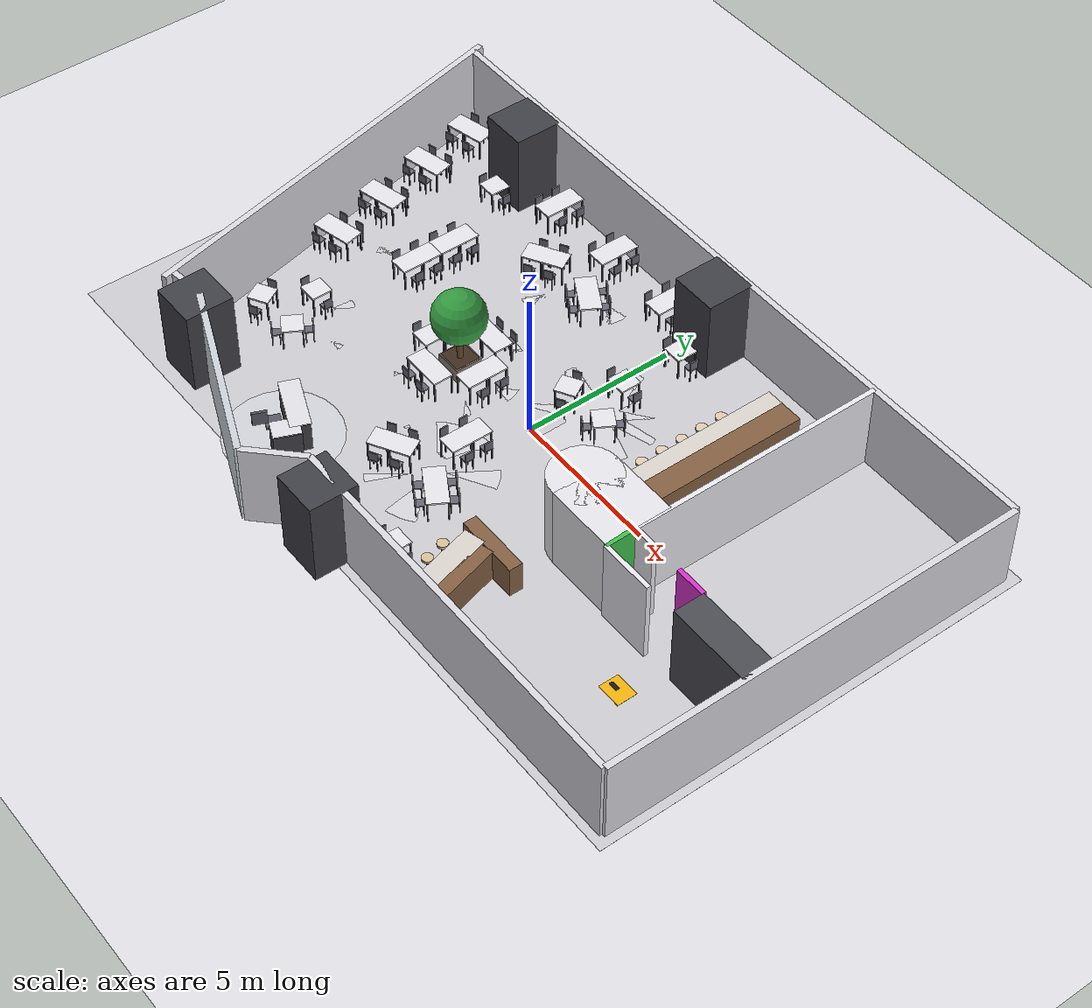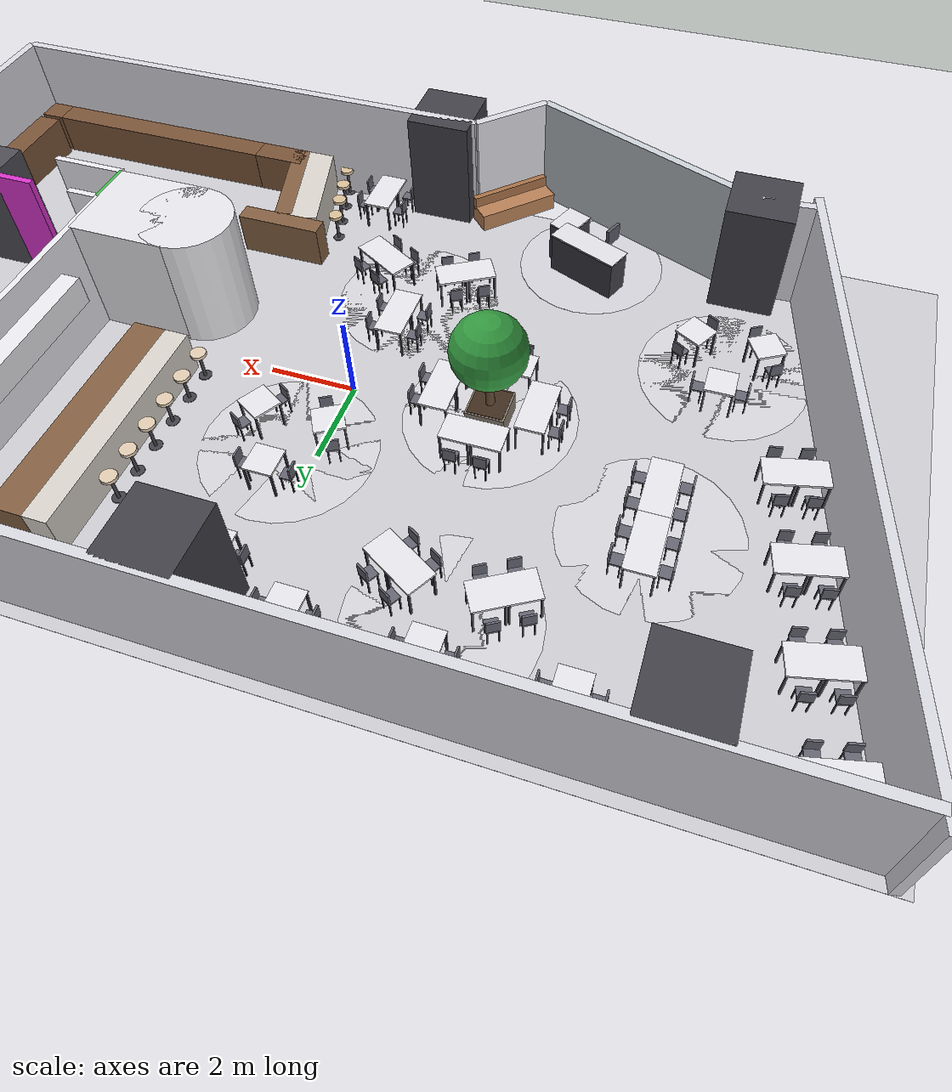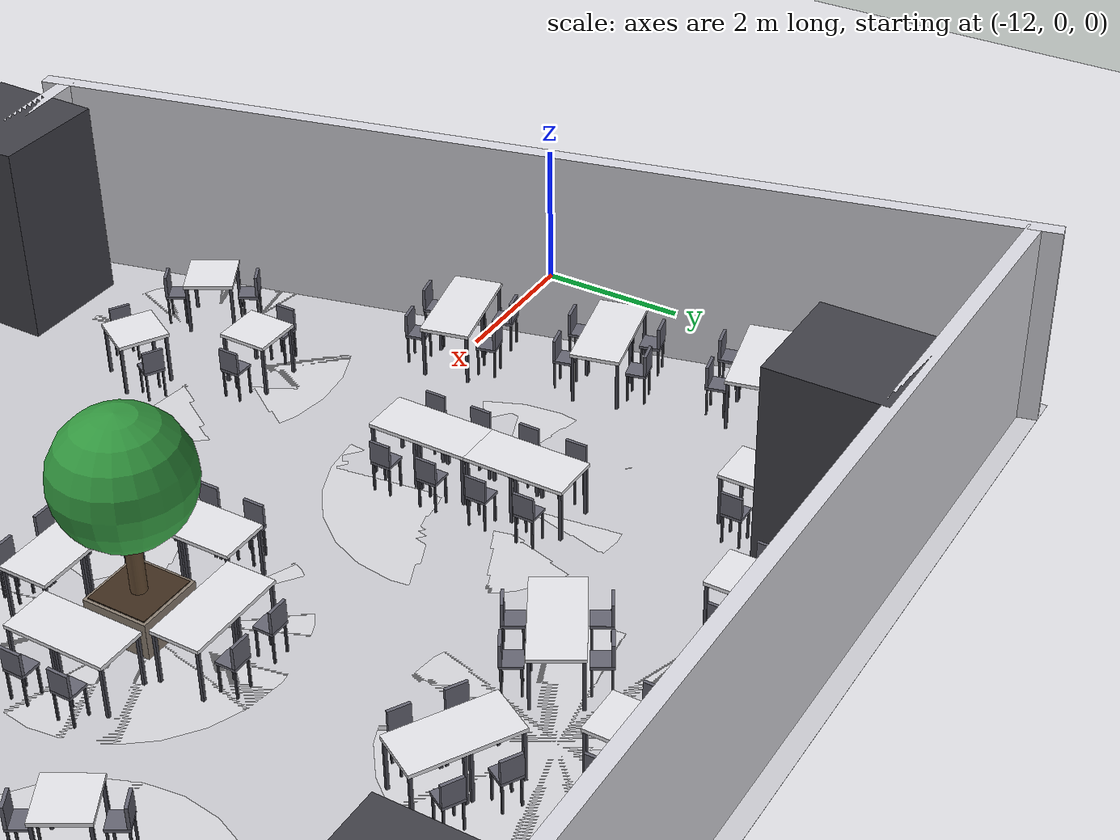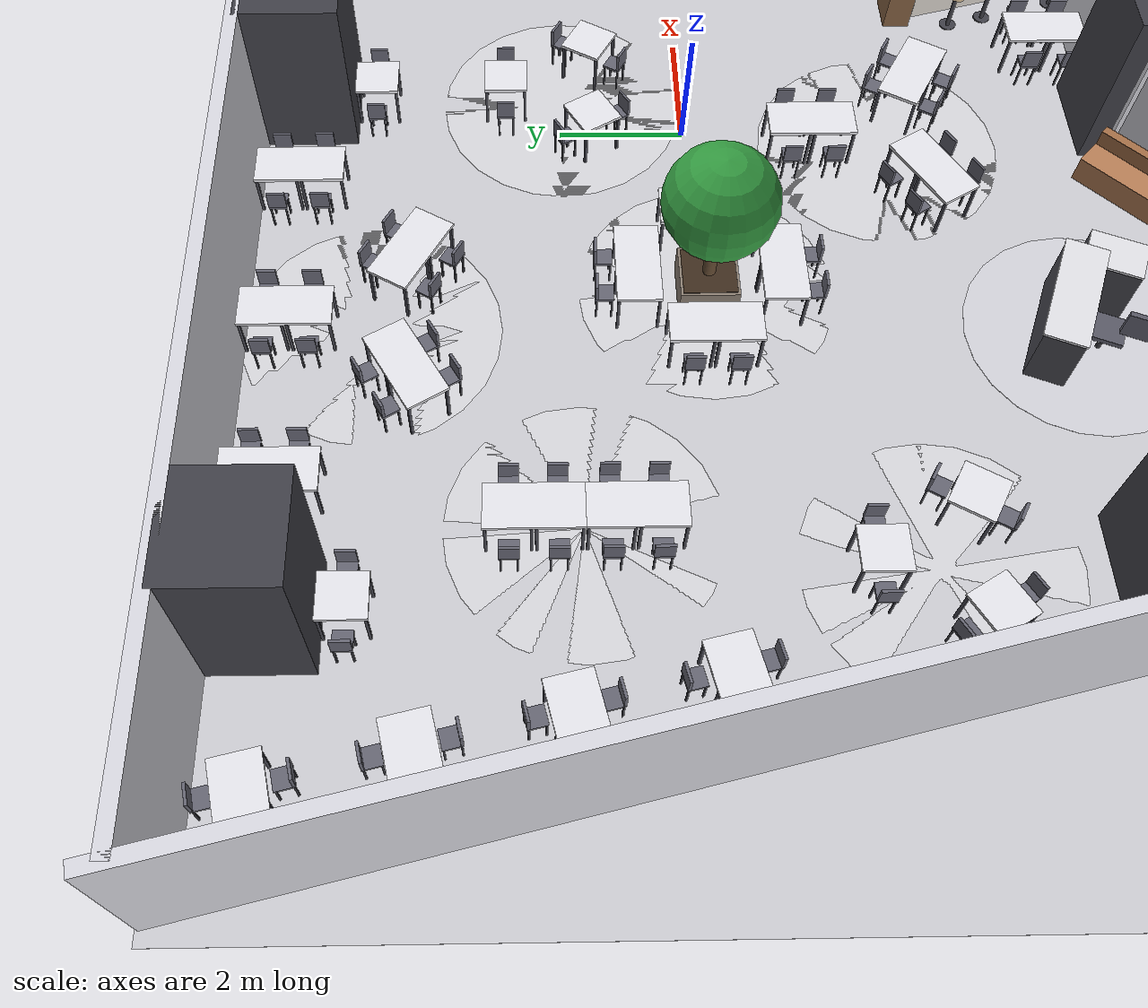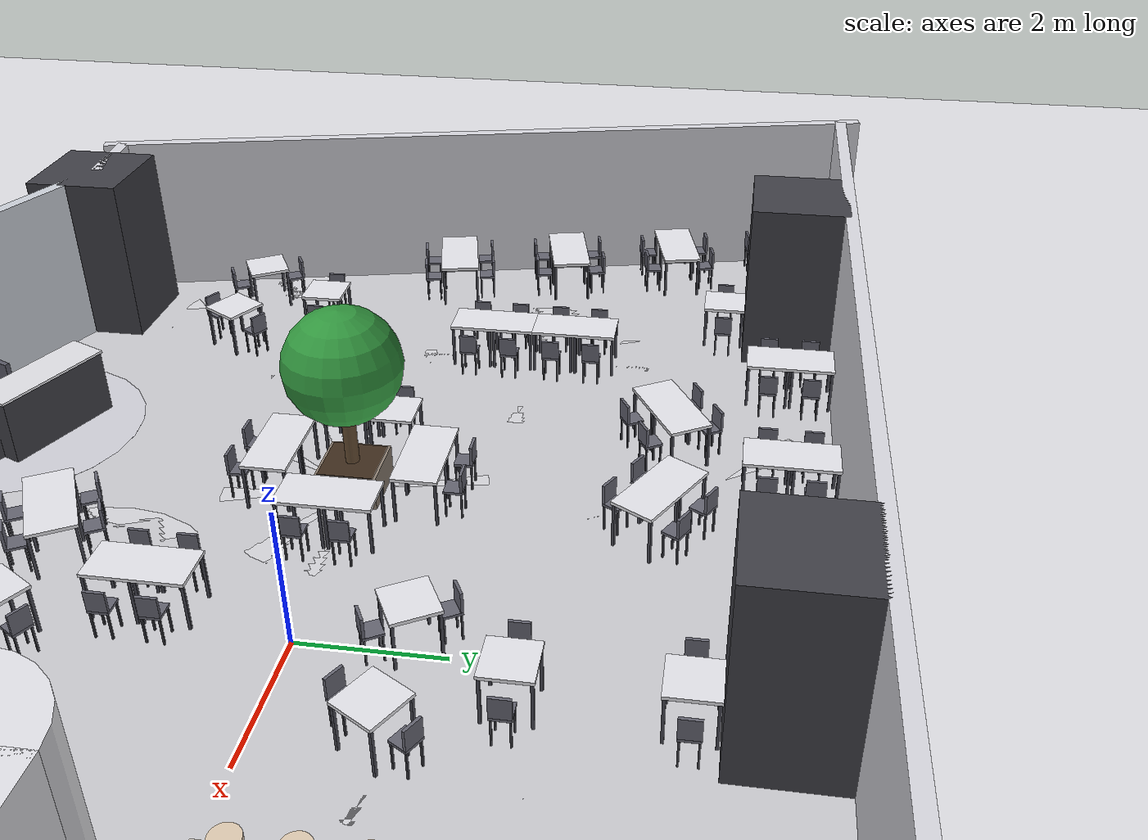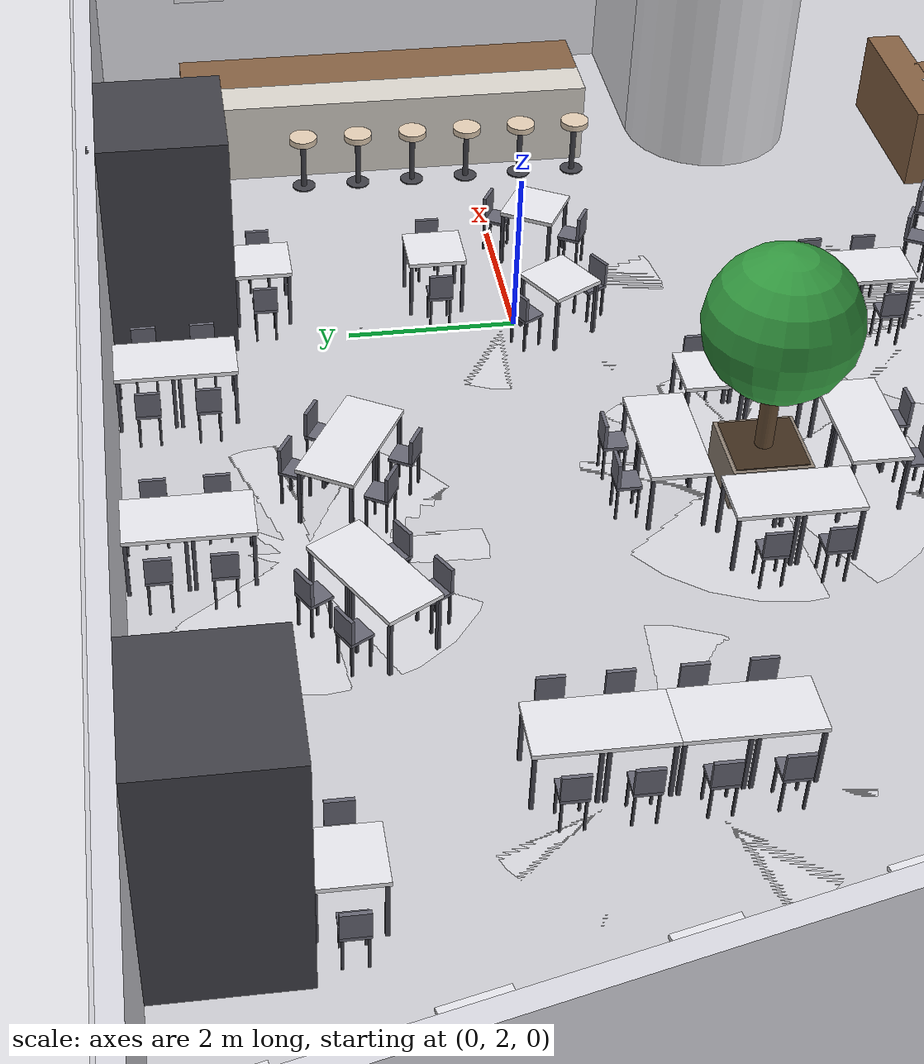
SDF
<?xml version="1.0" ?>
<sdf version="1.8">
  <world name="restaurant_blueprint_world">

    <!-- Physics Engine Configuration (Smooth 250 Hz for Real-time Sim) -->
    <physics name="4ms" type="ignored">
      <max_step_size>0.004</max_step_size>
      <real_time_factor>1.0</real_time_factor>
    </physics>

    <!-- Essential Gazebo Harmonic System Plugins -->
    <plugin filename="gz-sim-physics-system" name="gz::sim::systems::Physics"/>
    <plugin filename="gz-sim-user-commands-system" name="gz::sim::systems::UserCommands"/>
    <plugin filename="gz-sim-scene-broadcaster-system" name="gz::sim::systems::SceneBroadcaster"/>
    <plugin filename="gz-sim-sensors-system" name="gz::sim::systems::Sensors">
      <render_engine>ogre2</render_engine>
    </plugin>

    <!-- Sun Directional Light (Even, high visibility) -->
    <light type="directional" name="sun">
      <cast_shadows>false</cast_shadows>
      <pose>0 0 20 0 0 0</pose>
      <diffuse>0.92 0.92 0.92 1</diffuse>
      <specular>0.2 0.2 0.2 1</specular>
      <direction>-0.3 0.2 -0.9</direction>
    </light>

    <!-- Interior Fill Light 1 (West Dining Area) -->
    <light type="point" name="interior_light_west">
      <cast_shadows>false</cast_shadows>
      <pose>-6.0 0.0 4.0 0 0 0</pose>
      <diffuse>0.7 0.7 0.7 1</diffuse>
      <attenuation>
        <range>25</range>
        <constant>0.6</constant>
        <linear>0.04</linear>
        <quadratic>0.002</quadratic>
      </attenuation>
    </light>

    <!-- Interior Fill Light 2 (East Kitchen & Bar Area) -->
    <light type="point" name="interior_light_east">
      <cast_shadows>false</cast_shadows>
      <pose>6.0 0.0 4.0 0 0 0</pose>
      <diffuse>0.7 0.7 0.7 1</diffuse>
      <attenuation>
        <range>25</range>
        <constant>0.6</constant>
        <linear>0.04</linear>
        <quadratic>0.002</quadratic>
      </attenuation>
    </light>

    <!-- Scene Lighting & Background -->
    <scene>
      <ambient>0.82 0.82 0.85 1.0</ambient>
      <background>0.92 0.93 0.95 1.0</background>
      <shadows>false</shadows>
      <grid>true</grid>
    </scene>

    <!-- Global Ground Plane -->
    <model name="ground_plane">
      <static>true</static>
      <link name="link">
        <collision name="collision">
          <geometry><plane><normal>0 0 1</normal><size>120 120</size></plane></geometry>
        </collision>
        <visual name="visual">
          <geometry><plane><normal>0 0 1</normal><size>120 120</size></plane></geometry>
          <material>
            <ambient>0.88 0.88 0.90 1</ambient>
            <diffuse>0.88 0.88 0.90 1</diffuse>
            <specular>0.1 0.1 0.1 1</specular>
          </material>
        </visual>
      </link>
    </model>

    <!-- RESTAURANT ARCHITECTURAL BLUEPRINT BOUNDARY                    -->
    <!-- Generated directly from floor plan measurements:               -->
    <!--   - North Wall: 24.27 m                                        -->
    <!--   - East Wall: 13.78 m                                         -->
    <!--   - South-East Wall: 12.78 m                                   -->
    <!--   - Entrance Slant Right: 2.00 m                               -->
    <!--   - Main Entrance Facade: 6.25 m                               -->
    <!--   - Left Entrance Indent: 1.30 m                               -->
    <!--   - West Slanted Wall: 13.96 m                                 -->
    <!--   - Kitchen Vertical Partition: 9.40 m                         -->
    <!--   - Kitchen Horizontal Partition: 5.53 m                       -->
    <model name="restaurant_boundary">
      <static>true</static>

      <!-- 1. RESTAURANT INTERIOR TILE FLOOR SLAB -->
      <link name="interior_floor">
        <visual name="floor_vis">
          <pose>0.0 0.0 0.002 0 0 0</pose>
          <geometry>
            <box><size>25.0 14.5 0.004</size></box>
          </geometry>
          <material>
            <ambient>0.80 0.80 0.82 1</ambient>
            <diffuse>0.80 0.80 0.82 1</diffuse>
            <specular>0.15 0.15 0.15 1</specular>
          </material>
        </visual>
      </link>

      <!-- 2. OUTER PERIMETER BOUNDARY WALLS -->
      <link name="perimeter_walls">

        <!-- [WALL 1] Tường Bắc (North Wall - 24.27m) -->
        <!-- Từ (-12.135, 6.890) đến (12.135, 6.890) -->
        <visual name="wall_north_vis">
          <pose>0.0 6.890 1.40 0 0 0</pose>
          <geometry><box><size>24.27 0.20 2.80</size></box></geometry>
          <material><ambient>0.85 0.85 0.88 1</ambient><diffuse>0.85 0.85 0.88 1</diffuse></material>
        </visual>
        <collision name="wall_north_col">
          <pose>0.0 6.890 1.40 0 0 0</pose>
          <geometry><box><size>24.27 0.20 2.80</size></box></geometry>
        </collision>

        <!-- [WALL 2] Tường Đông (East Wall - 13.78m) -->
        <!-- Từ (12.135, 6.890) đến (12.135, -6.890) -->
        <visual name="wall_east_vis">
          <pose>12.135 0.0 1.40 0 0 -1.570796</pose>
          <geometry><box><size>13.78 0.20 2.80</size></box></geometry>
          <material><ambient>0.85 0.85 0.88 1</ambient><diffuse>0.85 0.85 0.88 1</diffuse></material>
        </visual>
        <collision name="wall_east_col">
          <pose>12.135 0.0 1.40 0 0 -1.570796</pose>
          <geometry><box><size>13.78 0.20 2.80</size></box></geometry>
        </collision>

        <!-- [WALL 3] Tường Nam bên phải (South-East Wall - 12.78m) -->
        <!-- Từ (12.135, -6.890) đến (-0.645, -6.890) -->
        <visual name="wall_south_east_vis">
          <pose>5.745 -6.890 1.40 0 0 0</pose>
          <geometry><box><size>12.78 0.20 2.80</size></box></geometry>
          <material><ambient>0.85 0.85 0.88 1</ambient><diffuse>0.85 0.85 0.88 1</diffuse></material>
        </visual>
        <collision name="wall_south_east_col">
          <pose>5.745 -6.890 1.40 0 0 0</pose>
          <geometry><box><size>12.78 0.20 2.80</size></box></geometry>
        </collision>

        <!-- [WALL 4] Đoạn vát sảnh vào bên phải (Entrance Slant Right - 2.00m) -->
        <!-- Từ (-0.645, -6.890) đến (-2.059, -8.304) -->
        <visual name="wall_entrance_slant_right_vis">
          <pose>-1.352 -7.597 1.40 0 0 -2.356194</pose>
          <geometry><box><size>2.00 0.20 2.80</size></box></geometry>
          <material><ambient>0.85 0.85 0.88 1</ambient><diffuse>0.85 0.85 0.88 1</diffuse></material>
        </visual>
        <collision name="wall_entrance_slant_right_col">
          <pose>-1.352 -7.597 1.40 0 0 -2.356194</pose>
          <geometry><box><size>2.00 0.20 2.80</size></box></geometry>
        </collision>

        <!-- [WALL 5] Mặt tiền sảnh chính (Main Entrance Facade - 6.25m) -->
        <!-- Từ (-2.059, -8.304) đến (-7.833, -5.912) -->
        <visual name="wall_main_entrance_vis">
          <pose>-4.946 -7.108 1.40 0 0 2.74889</pose>
          <geometry><box><size>6.25 0.20 2.80</size></box></geometry>
          <material><ambient>0.80 0.82 0.85 1</ambient><diffuse>0.80 0.82 0.85 1</diffuse></material>
        </visual>
        <collision name="wall_main_entrance_col">
          <pose>-4.946 -7.108 1.40 0 0 2.74889</pose>
          <geometry><box><size>6.25 0.20 2.80</size></box></geometry>
        </collision>

        <!-- [WALL 6] Đoạn gấp khúc thụt vào bên trái cửa (Entrance Indent - 1.30m) -->
        <!-- Từ (-7.833, -5.912) đến (-9.128, -6.025) -->
        <visual name="wall_entrance_indent_vis">
          <pose>-8.481 -5.969 1.40 0 0 -3.0545</pose>
          <geometry><box><size>1.30 0.20 2.80</size></box></geometry>
          <material><ambient>0.85 0.85 0.88 1</ambient><diffuse>0.85 0.85 0.88 1</diffuse></material>
        </visual>
        <collision name="wall_entrance_indent_col">
          <pose>-8.481 -5.969 1.40 0 0 -3.0545</pose>
          <geometry><box><size>1.30 0.20 2.80</size></box></geometry>
        </collision>

        <!-- [WALL 7] Tường chéo bên Tây (West Slanted Wall - 13.96m) -->
        <!-- Từ (-9.128, -6.025) đến (-12.135, 6.890) -->
        <visual name="wall_west_slant_vis">
          <pose>-10.631 0.432 1.40 0 0 1.7994</pose>
          <geometry><box><size>13.96 0.20 2.80</size></box></geometry>
          <material><ambient>0.85 0.85 0.88 1</ambient><diffuse>0.85 0.85 0.88 1</diffuse></material>
        </visual>
        <collision name="wall_west_slant_col">
          <pose>-10.631 0.432 1.40 0 0 1.7994</pose>
          <geometry><box><size>13.96 0.20 2.80</size></box></geometry>
        </collision>

      </link>

      <!-- 3. KITCHEN INTERIOR PARTITION WALLS & ROBOT SERVICE DOCK (Khu Bếp 09) -->
      <!-- Chuẩn hóa theo số đo thực tế lấy đường 5.53m làm chuẩn: -->
      <!--   - Đoạn tường màu xanh lá 1.00m (chỗ Robot quay lưng vào) -->
      <!--   - Cửa đi / Lối ra vào rộng 1.00m -->
      <!--   - Đoạn tường ngang màu tím hồng 1.00m -->
      <!--   - Khối lò nướng / bếp dày phía Đông -->
      <link name="kitchen_walls">

        <!-- [TƯỜNG DỌC CHÍNH BẾP] Từ tường Bắc xuống đến lối vào bếp: dài 8.40m -->
        <!-- Từ (6.605, 6.890) xuống (6.605, -1.510) -->
        <visual name="kitchen_vert_main_vis">
          <pose>6.605 2.690 1.40 0 0 -1.570796</pose>
          <geometry><box><size>8.40 0.15 2.80</size></box></geometry>
          <material><ambient>0.92 0.92 0.95 1</ambient><diffuse>0.92 0.92 0.95 1</diffuse></material>
        </visual>
        <collision name="kitchen_vert_main_col">
          <pose>6.605 2.690 1.40 0 0 -1.570796</pose>
          <geometry><box><size>8.40 0.15 2.80</size></box></geometry>
        </collision>

        <!-- [TƯỜNG XANH LÁ 1.00M] Đoạn tường Robot quay lưng vào để sạc / nhận thức ăn -->
        <!-- Từ (6.605, -1.510) xuống đến đường chuẩn (6.605, -2.510) -->
        <visual name="wall_robot_dock_green_vis">
          <pose>6.605 -2.010 1.40 0 0 -1.570796</pose>
          <geometry><box><size>1.00 0.15 2.80</size></box></geometry>
          <material>
            <ambient>0.20 0.65 0.25 1</ambient>
            <diffuse>0.25 0.75 0.30 1</diffuse>
            <specular>0.1 0.1 0.1 1</specular>
          </material>
        </visual>
        <collision name="wall_robot_dock_green_col">
          <pose>6.605 -2.010 1.40 0 0 -1.570796</pose>
          <geometry><box><size>1.00 0.15 2.80</size></box></geometry>
        </collision>

        <!-- [ĐOẠN TƯỜNG NGẮN CẠNH CỬA] Nối từ tường xanh lá ra mép cửa: dài 0.78m -->
        <!-- Tại Y = -1.510, từ X = 6.605 đến X = 7.385 -->
        <visual name="wall_dock_stub_vis">
          <pose>6.995 -1.510 1.40 0 0 0</pose>
          <geometry><box><size>0.78 0.15 2.80</size></box></geometry>
          <material><ambient>0.92 0.92 0.95 1</ambient><diffuse>0.92 0.92 0.95 1</diffuse></material>
        </visual>
        <collision name="wall_dock_stub_col">
          <pose>6.995 -1.510 1.40 0 0 0</pose>
          <geometry><box><size>0.78 0.15 2.80</size></box></geometry>
        </collision>

        <!-- KHOẢNG MỞ CỬA BẾP: Cửa rộng 1.00m (từ X = 7.385 đến X = 8.385 tại Y = -1.510) -->
        <!-- (Khoảng trống không có tường để Robot di chuyển ra vào) -->

        <!-- [TƯỜNG TÍM HỒNG 1.00M] Đoạn tường bên phải cửa bếp: dài 1.00m -->
        <!-- Tại Y = -1.510, từ X = 8.385 đến X = 9.385 -->
        <visual name="wall_dock_magenta_vis">
          <pose>8.885 -1.510 1.40 0 0 0</pose>
          <geometry><box><size>1.00 0.15 2.80</size></box></geometry>
          <material>
            <ambient>0.75 0.15 0.70 1</ambient>
            <diffuse>0.85 0.20 0.80 1</diffuse>
          </material>
        </visual>
        <collision name="wall_dock_magenta_col">
          <pose>8.885 -1.510 1.40 0 0 0</pose>
          <geometry><box><size>1.00 0.15 2.80</size></box></geometry>
        </collision>

        <!-- [KHỐI LÒ NƯỚNG / BẾP NẤU PHÍA ĐÔNG] Khối tường dày từ X = 9.385 đến tường Đông -->
        <visual name="kitchen_oven_block_vis">
          <pose>10.760 -2.010 1.40 0 0 0</pose>
          <geometry><box><size>2.75 1.00 2.80</size></box></geometry>
          <material><ambient>0.30 0.30 0.33 1</ambient><diffuse>0.30 0.30 0.33 1</diffuse></material>
        </visual>
        <collision name="kitchen_oven_block_col">
          <pose>10.760 -2.010 1.40 0 0 0</pose>
          <geometry><box><size>2.75 1.00 2.80</size></box></geometry>
        </collision>

        <!-- [TƯỜNG ĐƯỜNG CHUẨN ĐÃ KHOÉT CỬA 1.00M CHO ROBOT RA ĐẠI SẢNH (AREA 08)] -->
        <!-- Đoạn tường bên trái cửa: dài 1.78m từ X = 6.605 đến X = 8.385 tại Y = -2.510 -->
        <visual name="kitchen_horiz_left_vis">
          <pose>7.495 -2.510 1.40 0 0 0</pose>
          <geometry><box><size>1.78 0.15 2.80</size></box></geometry>
          <material><ambient>0.92 0.92 0.95 1</ambient><diffuse>0.92 0.92 0.95 1</diffuse></material>
        </visual>
        <collision name="kitchen_horiz_left_col">
          <pose>7.495 -2.510 1.40 0 0 0</pose>
          <geometry><box><size>1.78 0.15 2.80</size></box></geometry>
        </collision>

        <!-- KHOẢNG MỞ RA ĐẠI SẢNH: Cửa rộng 1.00m (từ X = 8.385 đến X = 9.385 tại Y = -2.510) -->
        <!-- Nằm đối diện trực diện với đoạn tường màu tím hồng để Robot đi thẳng ra đại sảnh -->

        <!-- [VỊ TRÍ ĐỖ XE ROBOT (HOME DOCK) - AREA 08 MAIN HALL] -->
        <!-- Đặt tại X = 8.85, Y = -3.80 (sảnh mở Area 08 ngoài cửa bếp, quay mặt về hướng Tây 3.14159 rad) -->
        <visual name="robot_dock_pad_vis">
          <pose>8.85 -3.80 0.008 0 0 3.14159</pose>
          <geometry><box><size>0.80 0.65 0.016</size></box></geometry>
          <material>
            <ambient>0.95 0.70 0.05 1</ambient>
            <diffuse>0.95 0.70 0.05 1</diffuse>
          </material>
        </visual>
        <visual name="robot_dock_arrow_vis">
          <pose>8.70 -3.80 0.018 0 0 3.14159</pose>
          <geometry><box><size>0.30 0.12 0.005</size></box></geometry>
          <material><ambient>0.1 0.1 0.1 1</ambient><diffuse>0.1 0.1 0.1 1</diffuse></material>
        </visual>

      </link>

      <!-- 4. AREA 08 STANDING COUNTERS & BAR 04 (Khu 08: Dãy bàn phục vụ khách đứng & Quầy Bar 04) -->
      <!-- Kích thước căn chuẩn xác theo số đo thực tế từ bản vẽ: -->
      <!--   - Bàn đứng dựa tường Đông: Rộng 0.69m x Dài 3.58m x Cao 1.05m -->
      <!--   - Bàn đứng dựa tường Nam: Rộng 0.69m x Dài 6.02m x Cao 1.05m -->
      <!--   - Góc tiếp giáp Đông - Nam: 0.69m x 0.69m x 1.05m -->
      <!--   - Quầy Bar 04: Thân dọc rộng 0.60m x dài 2.735m, đầu quầy rộng 0.42m, giật cấp 0.41m, lối đi 1.00m -->
      <!--   - 2 Bàn tròn quầy Booth trung tâm khu 08 -->
      <link name="area_08_furniture">

        <!-- [DÃY BÀN KHÁCH ĐỨNG - CẠNH ĐÔNG: 0.69m x 3.58m] -->
        <!-- Tựa vào tường Đông (X = 12.135m), dài 3.58m từ Y = -2.510 xuống Y = -6.090 -->
        <visual name="standing_counter_east_vis">
          <pose>11.790 -4.300 0.525 0 0 0</pose>
          <geometry><box><size>0.69 3.58 1.05</size></box></geometry>
          <material>
            <ambient>0.32 0.22 0.15 1</ambient>
            <diffuse>0.48 0.33 0.22 1</diffuse>
          </material>
        </visual>
        <collision name="standing_counter_east_col">
          <pose>11.790 -4.300 0.525 0 0 0</pose>
          <geometry><box><size>0.69 3.58 1.05</size></box></geometry>
        </collision>

        <!-- [GÓC NỐI ĐÔNG - NAM CỦA DÃY BÀN ĐỨNG: 0.69m x 0.69m] -->
        <visual name="standing_counter_corner_vis">
          <pose>11.790 -6.545 0.525 0 0 0</pose>
          <geometry><box><size>0.69 0.69 1.05</size></box></geometry>
          <material>
            <ambient>0.32 0.22 0.15 1</ambient>
            <diffuse>0.48 0.33 0.22 1</diffuse>
          </material>
        </visual>
        <collision name="standing_counter_corner_col">
          <pose>11.790 -6.545 0.525 0 0 0</pose>
          <geometry><box><size>0.69 0.69 1.05</size></box></geometry>
        </collision>

        <!-- [DÃY BÀN KHÁCH ĐỨNG - CẠNH NAM: 6.02m x 0.69m] -->
        <!-- Tựa vào tường Nam (Y = -6.890m), dài 6.02m từ X = 11.445 sang Tây đến X = 5.425 -->
        <visual name="standing_counter_south_vis">
          <pose>8.435 -6.545 0.525 0 0 0</pose>
          <geometry><box><size>6.02 0.69 1.05</size></box></geometry>
          <material>
            <ambient>0.32 0.22 0.15 1</ambient>
            <diffuse>0.48 0.33 0.22 1</diffuse>
          </material>
        </visual>
        <collision name="standing_counter_south_col">
          <pose>8.435 -6.545 0.525 0 0 0</pose>
          <geometry><box><size>6.02 0.69 1.05</size></box></geometry>
        </collision>

        <!-- [ĐOẠN NỐI LIỀN MẠCH BÀN PHÍA NAM VỚI CHÂN QUẦY BAR 04: Dài 1.325m x Rộng 0.69m] -->
        <!-- Nối từ mép bàn phía Nam X = 5.425m đến chân quầy nghiêng tại X = 4.10m, áp sát tường Nam -->
        <visual name="counter_south_join_vis">
          <pose>4.762 -6.545 0.525 0 0 0</pose>
          <geometry><box><size>1.325 0.69 1.05</size></box></geometry>
          <material>
            <ambient>0.32 0.22 0.15 1</ambient>
            <diffuse>0.48 0.33 0.22 1</diffuse>
          </material>
        </visual>
        <collision name="counter_south_join_col">
          <pose>4.762 -6.545 0.525 0 0 0</pose>
          <geometry><box><size>1.325 0.69 1.05</size></box></geometry>
        </collision>

        <!-- [DÃY BÀN QUẦY 04 - NGHIÊNG 105 ĐỘ PHÍA TÂY (QUẦY TRONG): Dày 0.44m x Dài 3.51m] -->
        <!-- Nghiêng 105 độ, thụt sâu xuống đụng thẳng vào dãy bàn phía Nam và tường Nam -->
        <visual name="bar_04_inner_slanted_vis">
          <pose>3.968 -5.520 0.525 0 0 0.2618</pose>
          <geometry><box><size>0.44 2.837 1.05</size></box></geometry>
          <material>
            <ambient>0.36 0.26 0.18 1</ambient>
            <diffuse>0.52 0.38 0.26 1</diffuse>
          </material>
        </visual>
        <collision name="bar_04_inner_slanted_col">
          <pose>3.968 -5.520 0.525 0 0 0.2618</pose>
          <geometry><box><size>0.44 2.837 1.05</size></box></geometry>
        </collision>

        <!-- [DÃY BÀN KẾ BÊN QUẦY 04 - NGHIÊNG 105 ĐỘ (QUẦY NGOÀI): Dày 0.69m x Dài 3.51m] -->
        <!-- Thiết kế đá granite sáng màu theo yêu cầu, áp khít mép Tây của quầy 0.44m, đụng thẳng vào tường Nam -->
        <visual name="bar_04_outer_slanted_vis">
          <pose>3.422 -5.520 0.525 0 0 0.2618</pose>
          <geometry><box><size>0.69 2.837 1.05</size></box></geometry>
          <material>
            <ambient>0.82 0.80 0.78 1</ambient>
            <diffuse>0.85 0.83 0.80 1</diffuse>
          </material>
        </visual>
        <collision name="bar_04_outer_slanted_col">
          <pose>3.422 -5.520 0.525 0 0 0.2618</pose>
          <geometry><box><size>0.69 2.837 1.05</size></box></geometry>
        </collision>

        <!-- [ĐẦU QUẦY BAR 04 PHÍA BẮC: Dài 2.11m x Dày 0.44m x Cao 1.05m] -->
        <!-- Liền mạch trên đỉnh 2 quầy nghiêng, lối đi thông thoáng lên phòng 07 -->
        <visual name="bar_04_top_cap_vis">
          <pose>3.550 -3.930 0.525 0 0 0</pose>
          <geometry><box><size>2.11 0.44 1.05</size></box></geometry>
          <material>
            <ambient>0.36 0.26 0.18 1</ambient>
            <diffuse>0.52 0.38 0.26 1</diffuse>
          </material>
        </visual>
        <collision name="bar_04_top_cap_col">
          <pose>3.550 -3.930 0.525 0 0 0</pose>
          <geometry><box><size>2.11 0.44 1.05</size></box></geometry>
        </collision>
                        <!-- [4 GHẾ TRÒN QUẦY BAR 04 PHÍA TÂY: Đường kính 0.34m, Cao 0.75m, chân trụ giữa] -->
        <!-- Ghế 1 (dưới cùng): X = 3.022m, Y = -6.733m -->
        <visual name="stool_1_cushion_vis">
          <pose>3.022 -6.733 0.710 0 0 0</pose>
          <geometry><cylinder><radius>0.17</radius><length>0.08</length></cylinder></geometry>
          <material><ambient>0.80 0.70 0.55 1</ambient><diffuse>0.85 0.75 0.60 1</diffuse></material>
        </visual>
        <visual name="stool_1_stem_vis">
          <pose>3.022 -6.733 0.345 0 0 0</pose>
          <geometry><cylinder><radius>0.035</radius><length>0.65</length></cylinder></geometry>
          <material><ambient>0.20 0.20 0.22 1</ambient><diffuse>0.25 0.25 0.28 1</diffuse></material>
        </visual>
        <visual name="stool_1_base_vis">
          <pose>3.022 -6.733 0.010 0 0 0</pose>
          <geometry><cylinder><radius>0.14</radius><length>0.02</length></cylinder></geometry>
          <material><ambient>0.20 0.20 0.22 1</ambient><diffuse>0.25 0.25 0.28 1</diffuse></material>
        </visual>
        <collision name="stool_1_cushion_col">
          <pose>3.022 -6.733 0.710 0 0 0</pose>
          <geometry><cylinder><radius>0.17</radius><length>0.08</length></cylinder></geometry>
        </collision>
        <collision name="stool_1_stem_col">
          <pose>3.022 -6.733 0.345 0 0 0</pose>
          <geometry><cylinder><radius>0.035</radius><length>0.65</length></cylinder></geometry>
        </collision>
        <collision name="stool_1_base_col">
          <pose>3.022 -6.733 0.010 0 0 0</pose>
          <geometry><cylinder><radius>0.14</radius><length>0.02</length></cylinder></geometry>
        </collision>

        <!-- Ghế 2: X = 2.854m, Y = -6.105m -->
        <visual name="stool_2_cushion_vis">
          <pose>2.854 -6.105 0.710 0 0 0</pose>
          <geometry><cylinder><radius>0.17</radius><length>0.08</length></cylinder></geometry>
          <material><ambient>0.80 0.70 0.55 1</ambient><diffuse>0.85 0.75 0.60 1</diffuse></material>
        </visual>
        <visual name="stool_2_stem_vis">
          <pose>2.854 -6.105 0.345 0 0 0</pose>
          <geometry><cylinder><radius>0.035</radius><length>0.65</length></cylinder></geometry>
          <material><ambient>0.20 0.20 0.22 1</ambient><diffuse>0.25 0.25 0.28 1</diffuse></material>
        </visual>
        <visual name="stool_2_base_vis">
          <pose>2.854 -6.105 0.010 0 0 0</pose>
          <geometry><cylinder><radius>0.14</radius><length>0.02</length></cylinder></geometry>
          <material><ambient>0.20 0.20 0.22 1</ambient><diffuse>0.25 0.25 0.28 1</diffuse></material>
        </visual>
        <collision name="stool_2_cushion_col">
          <pose>2.854 -6.105 0.710 0 0 0</pose>
          <geometry><cylinder><radius>0.17</radius><length>0.08</length></cylinder></geometry>
        </collision>
        <collision name="stool_2_stem_col">
          <pose>2.854 -6.105 0.345 0 0 0</pose>
          <geometry><cylinder><radius>0.035</radius><length>0.65</length></cylinder></geometry>
        </collision>
        <collision name="stool_2_base_col">
          <pose>2.854 -6.105 0.010 0 0 0</pose>
          <geometry><cylinder><radius>0.14</radius><length>0.02</length></cylinder></geometry>
        </collision>

        <!-- Ghế 3: X = 2.686m, Y = -5.478m -->
        <visual name="stool_3_cushion_vis">
          <pose>2.686 -5.478 0.710 0 0 0</pose>
          <geometry><cylinder><radius>0.17</radius><length>0.08</length></cylinder></geometry>
          <material><ambient>0.80 0.70 0.55 1</ambient><diffuse>0.85 0.75 0.60 1</diffuse></material>
        </visual>
        <visual name="stool_3_stem_vis">
          <pose>2.686 -5.478 0.345 0 0 0</pose>
          <geometry><cylinder><radius>0.035</radius><length>0.65</length></cylinder></geometry>
          <material><ambient>0.20 0.20 0.22 1</ambient><diffuse>0.25 0.25 0.28 1</diffuse></material>
        </visual>
        <visual name="stool_3_base_vis">
          <pose>2.686 -5.478 0.010 0 0 0</pose>
          <geometry><cylinder><radius>0.14</radius><length>0.02</length></cylinder></geometry>
          <material><ambient>0.20 0.20 0.22 1</ambient><diffuse>0.25 0.25 0.28 1</diffuse></material>
        </visual>
        <collision name="stool_3_cushion_col">
          <pose>2.686 -5.478 0.710 0 0 0</pose>
          <geometry><cylinder><radius>0.17</radius><length>0.08</length></cylinder></geometry>
        </collision>
        <collision name="stool_3_stem_col">
          <pose>2.686 -5.478 0.345 0 0 0</pose>
          <geometry><cylinder><radius>0.035</radius><length>0.65</length></cylinder></geometry>
        </collision>
        <collision name="stool_3_base_col">
          <pose>2.686 -5.478 0.010 0 0 0</pose>
          <geometry><cylinder><radius>0.14</radius><length>0.02</length></cylinder></geometry>
        </collision>

        <!-- Ghế 4 (trên cùng): X = 2.518m, Y = -4.850m -->
        <visual name="stool_4_cushion_vis">
          <pose>2.518 -4.850 0.710 0 0 0</pose>
          <geometry><cylinder><radius>0.17</radius><length>0.08</length></cylinder></geometry>
          <material><ambient>0.80 0.70 0.55 1</ambient><diffuse>0.85 0.75 0.60 1</diffuse></material>
        </visual>
        <visual name="stool_4_stem_vis">
          <pose>2.518 -4.850 0.345 0 0 0</pose>
          <geometry><cylinder><radius>0.035</radius><length>0.65</length></cylinder></geometry>
          <material><ambient>0.20 0.20 0.22 1</ambient><diffuse>0.25 0.25 0.28 1</diffuse></material>
        </visual>
        <visual name="stool_4_base_vis">
          <pose>2.518 -4.850 0.010 0 0 0</pose>
          <geometry><cylinder><radius>0.14</radius><length>0.02</length></cylinder></geometry>
          <material><ambient>0.20 0.20 0.22 1</ambient><diffuse>0.25 0.25 0.28 1</diffuse></material>
        </visual>
        <collision name="stool_4_cushion_col">
          <pose>2.518 -4.850 0.710 0 0 0</pose>
          <geometry><cylinder><radius>0.17</radius><length>0.08</length></cylinder></geometry>
        </collision>
        <collision name="stool_4_stem_col">
          <pose>2.518 -4.850 0.345 0 0 0</pose>
          <geometry><cylinder><radius>0.035</radius><length>0.65</length></cylinder></geometry>
        </collision>
        <collision name="stool_4_base_col">
          <pose>2.518 -4.850 0.010 0 0 0</pose>
          <geometry><cylinder><radius>0.14</radius><length>0.02</length></cylinder></geometry>
        </collision>

      </link>

      <!-- 5. GROUP 01 DINING SET (Cụm bàn ăn chuẩn Group 01: 1 bàn chữ nhật + 4 ghế ăn) -->
      <!-- Chuẩn module hóa thiết kế để tái sử dụng và nhân bản khắp nhà hàng: -->
      <!--   - Bàn chữ nhật chuẩn: Rộng 0.67m x Dài 1.38m x Cao 0.75m tại tâm (1.661, -6.187) -->
      <!--   - 4 Ghế ăn chuẩn: Khổ 0.28m x 0.28m x Cao 0.75m (đã thu nhỏ từ 0.36m để tránh chạm Cột SE) -->
      <!--     Khoảng cách hở chuẩn: 2.1cm so với mép bàn, 2.0cm so với Cột SE (X = 1.005m) -->
      <!--     2 ghế phía Đông: X = 2.157m, Y = -5.850m và Y = -6.520m -->
      <!--     2 ghế phía Tây:  X = 1.165m, Y = -5.850m và Y = -6.520m -->
      <!--   - Tọa độ tương đối so với tâm bàn (X0 = 1.661, Y0 = -6.187): -->
      <!--       Bàn:     (0, 0) -->
      <!--       Ghế E1:  (+0.496, +0.337) -->
      <!--       Ghế E2:  (+0.496, -0.333) -->
      <!--       Ghế W1:  (-0.496, +0.337) -->
      <!--       Ghế W2:  (-0.496, -0.333) -->
      <link name="group01">

        <!-- [BÀN ĂN HÌNH CHỮ NHẬT GROUP 01] -->
        <visual name="group01_table_vis">
          <pose>1.661 -6.187 0.725 0.0000 0.0000 0.0000</pose>
          <geometry><box><size>0.67 1.38 0.05</size></box></geometry>
          <material>
            <ambient>0.85 0.85 0.88 1</ambient>
            <diffuse>0.90 0.90 0.92 1</diffuse>
          </material>
        </visual>
        <visual name="group01_table_leg_1_vis">
          <pose>1.961 -5.532 0.350 0 0 0.0000</pose>
          <geometry><box><size>0.04 0.04 0.70</size></box></geometry>
          <material><ambient>0.22 0.22 0.25 1</ambient><diffuse>0.28 0.28 0.32 1</diffuse></material>
        </visual>
        <visual name="group01_table_leg_2_vis">
          <pose>1.361 -5.532 0.350 0 0 0.0000</pose>
          <geometry><box><size>0.04 0.04 0.70</size></box></geometry>
          <material><ambient>0.22 0.22 0.25 1</ambient><diffuse>0.28 0.28 0.32 1</diffuse></material>
        </visual>
        <visual name="group01_table_leg_3_vis">
          <pose>1.961 -6.152 0.350 0 0 0.0000</pose>
          <geometry><box><size>0.04 0.04 0.70</size></box></geometry>
          <material><ambient>0.22 0.22 0.25 1</ambient><diffuse>0.28 0.28 0.32 1</diffuse></material>
        </visual>
        <visual name="group01_table_leg_4_vis">
          <pose>1.361 -6.152 0.350 0 0 0.0000</pose>
          <geometry><box><size>0.04 0.04 0.70</size></box></geometry>
          <material><ambient>0.22 0.22 0.25 1</ambient><diffuse>0.28 0.28 0.32 1</diffuse></material>
        </visual>
        <visual name="group01_table_leg_5_vis">
          <pose>1.961 -6.222 0.350 0 0 0.0000</pose>
          <geometry><box><size>0.04 0.04 0.70</size></box></geometry>
          <material><ambient>0.22 0.22 0.25 1</ambient><diffuse>0.28 0.28 0.32 1</diffuse></material>
        </visual>
        <visual name="group01_table_leg_6_vis">
          <pose>1.361 -6.222 0.350 0 0 0.0000</pose>
          <geometry><box><size>0.04 0.04 0.70</size></box></geometry>
          <material><ambient>0.22 0.22 0.25 1</ambient><diffuse>0.28 0.28 0.32 1</diffuse></material>
        </visual>
        <visual name="group01_table_leg_7_vis">
          <pose>1.961 -6.842 0.350 0 0 0.0000</pose>
          <geometry><box><size>0.04 0.04 0.70</size></box></geometry>
          <material><ambient>0.22 0.22 0.25 1</ambient><diffuse>0.28 0.28 0.32 1</diffuse></material>
        </visual>
        <visual name="group01_table_leg_8_vis">
          <pose>1.361 -6.842 0.350 0 0 0.0000</pose>
          <geometry><box><size>0.04 0.04 0.70</size></box></geometry>
          <material><ambient>0.22 0.22 0.25 1</ambient><diffuse>0.28 0.28 0.32 1</diffuse></material>
        </visual>
        <collision name="group01_table_col">
          <pose>1.661 -6.187 0.725 0.0000 0.0000 0.0000</pose>
          <geometry><box><size>0.67 1.38 0.05</size></box></geometry>
        </collision>
        <collision name="group01_table_leg_1_col">
          <pose>1.961 -5.532 0.350 0 0 0.0000</pose>
          <geometry><box><size>0.04 0.04 0.70</size></box></geometry>
        </collision>
        <collision name="group01_table_leg_2_col">
          <pose>1.361 -5.532 0.350 0 0 0.0000</pose>
          <geometry><box><size>0.04 0.04 0.70</size></box></geometry>
        </collision>
        <collision name="group01_table_leg_3_col">
          <pose>1.961 -6.152 0.350 0 0 0.0000</pose>
          <geometry><box><size>0.04 0.04 0.70</size></box></geometry>
        </collision>
        <collision name="group01_table_leg_4_col">
          <pose>1.361 -6.152 0.350 0 0 0.0000</pose>
          <geometry><box><size>0.04 0.04 0.70</size></box></geometry>
        </collision>
        <collision name="group01_table_leg_5_col">
          <pose>1.961 -6.222 0.350 0 0 0.0000</pose>
          <geometry><box><size>0.04 0.04 0.70</size></box></geometry>
        </collision>
        <collision name="group01_table_leg_6_col">
          <pose>1.361 -6.222 0.350 0 0 0.0000</pose>
          <geometry><box><size>0.04 0.04 0.70</size></box></geometry>
        </collision>
        <collision name="group01_table_leg_7_col">
          <pose>1.961 -6.842 0.350 0 0 0.0000</pose>
          <geometry><box><size>0.04 0.04 0.70</size></box></geometry>
        </collision>
        <collision name="group01_table_leg_8_col">
          <pose>1.361 -6.842 0.350 0 0 0.0000</pose>
          <geometry><box><size>0.04 0.04 0.70</size></box></geometry>
        </collision>

        <!-- [4 GHẾ ĂN GROUP 01: Khổ 0.28m x 0.28m x Cao 0.75m, hở mép cột 2.0cm] -->
        <!-- Ghế Đông 1 (Đông Bắc) -->
        <visual name="group01_chair_e1_seat_vis">
          <pose>2.157 -5.850 0.430 0.0000 0.0000 0.0000</pose>
          <geometry><box><size>0.28 0.28 0.04</size></box></geometry>
          <material><ambient>0.30 0.30 0.33 1</ambient><diffuse>0.40 0.40 0.45 1</diffuse></material>
        </visual>
        <visual name="group01_chair_e1_back_vis">
          <pose>2.277 -5.850 0.600 0 0 0.0000</pose>
          <geometry><box><size>0.04 0.28 0.30</size></box></geometry>
          <material><ambient>0.30 0.30 0.33 1</ambient><diffuse>0.40 0.40 0.45 1</diffuse></material>
        </visual>
        <visual name="group01_chair_e1_leg_1_vis">
          <pose>2.272 -5.735 0.205 0 0 0.0000</pose>
          <geometry><box><size>0.025 0.025 0.41</size></box></geometry>
          <material><ambient>0.20 0.20 0.22 1</ambient><diffuse>0.25 0.25 0.28 1</diffuse></material>
        </visual>
        <visual name="group01_chair_e1_leg_2_vis">
          <pose>2.042 -5.735 0.205 0 0 0.0000</pose>
          <geometry><box><size>0.025 0.025 0.41</size></box></geometry>
          <material><ambient>0.20 0.20 0.22 1</ambient><diffuse>0.25 0.25 0.28 1</diffuse></material>
        </visual>
        <visual name="group01_chair_e1_leg_3_vis">
          <pose>2.272 -5.965 0.205 0 0 0.0000</pose>
          <geometry><box><size>0.025 0.025 0.41</size></box></geometry>
          <material><ambient>0.20 0.20 0.22 1</ambient><diffuse>0.25 0.25 0.28 1</diffuse></material>
        </visual>
        <visual name="group01_chair_e1_leg_4_vis">
          <pose>2.042 -5.965 0.205 0 0 0.0000</pose>
          <geometry><box><size>0.025 0.025 0.41</size></box></geometry>
          <material><ambient>0.20 0.20 0.22 1</ambient><diffuse>0.25 0.25 0.28 1</diffuse></material>
        </visual>
        <collision name="group01_chair_e1_seat_col">
          <pose>2.157 -5.850 0.430 0.0000 0.0000 0.0000</pose>
          <geometry><box><size>0.28 0.28 0.04</size></box></geometry>
        </collision>
        <collision name="group01_chair_e1_back_col">
          <pose>2.277 -5.850 0.600 0 0 0.0000</pose>
          <geometry><box><size>0.04 0.28 0.30</size></box></geometry>
        </collision>
        <collision name="group01_chair_e1_leg_1_col">
          <pose>2.272 -5.735 0.205 0 0 0.0000</pose>
          <geometry><box><size>0.025 0.025 0.41</size></box></geometry>
        </collision>
        <collision name="group01_chair_e1_leg_2_col">
          <pose>2.042 -5.735 0.205 0 0 0.0000</pose>
          <geometry><box><size>0.025 0.025 0.41</size></box></geometry>
        </collision>
        <collision name="group01_chair_e1_leg_3_col">
          <pose>2.272 -5.965 0.205 0 0 0.0000</pose>
          <geometry><box><size>0.025 0.025 0.41</size></box></geometry>
        </collision>
        <collision name="group01_chair_e1_leg_4_col">
          <pose>2.042 -5.965 0.205 0 0 0.0000</pose>
          <geometry><box><size>0.025 0.025 0.41</size></box></geometry>
        </collision>

        <!-- Ghế Đông 2 (Đông Nam) -->
        <visual name="group01_chair_e2_seat_vis">
          <pose>2.157 -6.520 0.430 0.0000 0.0000 0.0000</pose>
          <geometry><box><size>0.28 0.28 0.04</size></box></geometry>
          <material><ambient>0.30 0.30 0.33 1</ambient><diffuse>0.40 0.40 0.45 1</diffuse></material>
        </visual>
        <visual name="group01_chair_e2_back_vis">
          <pose>2.277 -6.520 0.600 0 0 0.0000</pose>
          <geometry><box><size>0.04 0.28 0.30</size></box></geometry>
          <material><ambient>0.30 0.30 0.33 1</ambient><diffuse>0.40 0.40 0.45 1</diffuse></material>
        </visual>
        <visual name="group01_chair_e2_leg_1_vis">
          <pose>2.272 -6.405 0.205 0 0 0.0000</pose>
          <geometry><box><size>0.025 0.025 0.41</size></box></geometry>
          <material><ambient>0.20 0.20 0.22 1</ambient><diffuse>0.25 0.25 0.28 1</diffuse></material>
        </visual>
        <visual name="group01_chair_e2_leg_2_vis">
          <pose>2.042 -6.405 0.205 0 0 0.0000</pose>
          <geometry><box><size>0.025 0.025 0.41</size></box></geometry>
          <material><ambient>0.20 0.20 0.22 1</ambient><diffuse>0.25 0.25 0.28 1</diffuse></material>
        </visual>
        <visual name="group01_chair_e2_leg_3_vis">
          <pose>2.272 -6.635 0.205 0 0 0.0000</pose>
          <geometry><box><size>0.025 0.025 0.41</size></box></geometry>
          <material><ambient>0.20 0.20 0.22 1</ambient><diffuse>0.25 0.25 0.28 1</diffuse></material>
        </visual>
        <visual name="group01_chair_e2_leg_4_vis">
          <pose>2.042 -6.635 0.205 0 0 0.0000</pose>
          <geometry><box><size>0.025 0.025 0.41</size></box></geometry>
          <material><ambient>0.20 0.20 0.22 1</ambient><diffuse>0.25 0.25 0.28 1</diffuse></material>
        </visual>
        <collision name="group01_chair_e2_seat_col">
          <pose>2.157 -6.520 0.430 0.0000 0.0000 0.0000</pose>
          <geometry><box><size>0.28 0.28 0.04</size></box></geometry>
        </collision>
        <collision name="group01_chair_e2_back_col">
          <pose>2.277 -6.520 0.600 0 0 0.0000</pose>
          <geometry><box><size>0.04 0.28 0.30</size></box></geometry>
        </collision>
        <collision name="group01_chair_e2_leg_1_col">
          <pose>2.272 -6.405 0.205 0 0 0.0000</pose>
          <geometry><box><size>0.025 0.025 0.41</size></box></geometry>
        </collision>
        <collision name="group01_chair_e2_leg_2_col">
          <pose>2.042 -6.405 0.205 0 0 0.0000</pose>
          <geometry><box><size>0.025 0.025 0.41</size></box></geometry>
        </collision>
        <collision name="group01_chair_e2_leg_3_col">
          <pose>2.272 -6.635 0.205 0 0 0.0000</pose>
          <geometry><box><size>0.025 0.025 0.41</size></box></geometry>
        </collision>
        <collision name="group01_chair_e2_leg_4_col">
          <pose>2.042 -6.635 0.205 0 0 0.0000</pose>
          <geometry><box><size>0.025 0.025 0.41</size></box></geometry>
        </collision>

        <!-- Ghế Tây 1 (Tây Bắc) -->
        <visual name="group01_chair_w1_seat_vis">
          <pose>1.165 -5.850 0.430 0.0000 0.0000 0.0000</pose>
          <geometry><box><size>0.28 0.28 0.04</size></box></geometry>
          <material><ambient>0.30 0.30 0.33 1</ambient><diffuse>0.40 0.40 0.45 1</diffuse></material>
        </visual>
        <visual name="group01_chair_w1_back_vis">
          <pose>1.045 -5.850 0.600 0 0 0.0000</pose>
          <geometry><box><size>0.04 0.28 0.30</size></box></geometry>
          <material><ambient>0.30 0.30 0.33 1</ambient><diffuse>0.40 0.40 0.45 1</diffuse></material>
        </visual>
        <visual name="group01_chair_w1_leg_1_vis">
          <pose>1.280 -5.735 0.205 0 0 0.0000</pose>
          <geometry><box><size>0.025 0.025 0.41</size></box></geometry>
          <material><ambient>0.20 0.20 0.22 1</ambient><diffuse>0.25 0.25 0.28 1</diffuse></material>
        </visual>
        <visual name="group01_chair_w1_leg_2_vis">
          <pose>1.050 -5.735 0.205 0 0 0.0000</pose>
          <geometry><box><size>0.025 0.025 0.41</size></box></geometry>
          <material><ambient>0.20 0.20 0.22 1</ambient><diffuse>0.25 0.25 0.28 1</diffuse></material>
        </visual>
        <visual name="group01_chair_w1_leg_3_vis">
          <pose>1.280 -5.965 0.205 0 0 0.0000</pose>
          <geometry><box><size>0.025 0.025 0.41</size></box></geometry>
          <material><ambient>0.20 0.20 0.22 1</ambient><diffuse>0.25 0.25 0.28 1</diffuse></material>
        </visual>
        <visual name="group01_chair_w1_leg_4_vis">
          <pose>1.050 -5.965 0.205 0 0 0.0000</pose>
          <geometry><box><size>0.025 0.025 0.41</size></box></geometry>
          <material><ambient>0.20 0.20 0.22 1</ambient><diffuse>0.25 0.25 0.28 1</diffuse></material>
        </visual>
        <collision name="group01_chair_w1_seat_col">
          <pose>1.165 -5.850 0.430 0.0000 0.0000 0.0000</pose>
          <geometry><box><size>0.28 0.28 0.04</size></box></geometry>
        </collision>
        <collision name="group01_chair_w1_back_col">
          <pose>1.045 -5.850 0.600 0 0 0.0000</pose>
          <geometry><box><size>0.04 0.28 0.30</size></box></geometry>
        </collision>
        <collision name="group01_chair_w1_leg_1_col">
          <pose>1.280 -5.735 0.205 0 0 0.0000</pose>
          <geometry><box><size>0.025 0.025 0.41</size></box></geometry>
        </collision>
        <collision name="group01_chair_w1_leg_2_col">
          <pose>1.050 -5.735 0.205 0 0 0.0000</pose>
          <geometry><box><size>0.025 0.025 0.41</size></box></geometry>
        </collision>
        <collision name="group01_chair_w1_leg_3_col">
          <pose>1.280 -5.965 0.205 0 0 0.0000</pose>
          <geometry><box><size>0.025 0.025 0.41</size></box></geometry>
        </collision>
        <collision name="group01_chair_w1_leg_4_col">
          <pose>1.050 -5.965 0.205 0 0 0.0000</pose>
          <geometry><box><size>0.025 0.025 0.41</size></box></geometry>
        </collision>

        <!-- Ghế Tây 2 (Tây Nam: Cách mép cột SE 2.0cm, hoàn toàn không chạm cột) -->
        <visual name="group01_chair_w2_seat_vis">
          <pose>1.165 -6.520 0.430 0.0000 0.0000 0.0000</pose>
          <geometry><box><size>0.28 0.28 0.04</size></box></geometry>
          <material><ambient>0.30 0.30 0.33 1</ambient><diffuse>0.40 0.40 0.45 1</diffuse></material>
        </visual>
        <visual name="group01_chair_w2_back_vis">
          <pose>1.045 -6.520 0.600 0 0 0.0000</pose>
          <geometry><box><size>0.04 0.28 0.30</size></box></geometry>
          <material><ambient>0.30 0.30 0.33 1</ambient><diffuse>0.40 0.40 0.45 1</diffuse></material>
        </visual>
        <visual name="group01_chair_w2_leg_1_vis">
          <pose>1.280 -6.405 0.205 0 0 0.0000</pose>
          <geometry><box><size>0.025 0.025 0.41</size></box></geometry>
          <material><ambient>0.20 0.20 0.22 1</ambient><diffuse>0.25 0.25 0.28 1</diffuse></material>
        </visual>
        <visual name="group01_chair_w2_leg_2_vis">
          <pose>1.050 -6.405 0.205 0 0 0.0000</pose>
          <geometry><box><size>0.025 0.025 0.41</size></box></geometry>
          <material><ambient>0.20 0.20 0.22 1</ambient><diffuse>0.25 0.25 0.28 1</diffuse></material>
        </visual>
        <visual name="group01_chair_w2_leg_3_vis">
          <pose>1.280 -6.635 0.205 0 0 0.0000</pose>
          <geometry><box><size>0.025 0.025 0.41</size></box></geometry>
          <material><ambient>0.20 0.20 0.22 1</ambient><diffuse>0.25 0.25 0.28 1</diffuse></material>
        </visual>
        <visual name="group01_chair_w2_leg_4_vis">
          <pose>1.050 -6.635 0.205 0 0 0.0000</pose>
          <geometry><box><size>0.025 0.025 0.41</size></box></geometry>
          <material><ambient>0.20 0.20 0.22 1</ambient><diffuse>0.25 0.25 0.28 1</diffuse></material>
        </visual>
        <collision name="group01_chair_w2_seat_col">
          <pose>1.165 -6.520 0.430 0.0000 0.0000 0.0000</pose>
          <geometry><box><size>0.28 0.28 0.04</size></box></geometry>
        </collision>
        <collision name="group01_chair_w2_back_col">
          <pose>1.045 -6.520 0.600 0 0 0.0000</pose>
          <geometry><box><size>0.04 0.28 0.30</size></box></geometry>
        </collision>
        <collision name="group01_chair_w2_leg_1_col">
          <pose>1.280 -6.405 0.205 0 0 0.0000</pose>
          <geometry><box><size>0.025 0.025 0.41</size></box></geometry>
        </collision>
        <collision name="group01_chair_w2_leg_2_col">
          <pose>1.050 -6.405 0.205 0 0 0.0000</pose>
          <geometry><box><size>0.025 0.025 0.41</size></box></geometry>
        </collision>
        <collision name="group01_chair_w2_leg_3_col">
          <pose>1.280 -6.635 0.205 0 0 0.0000</pose>
          <geometry><box><size>0.025 0.025 0.41</size></box></geometry>
        </collision>
        <collision name="group01_chair_w2_leg_4_col">
          <pose>1.050 -6.635 0.205 0 0 0.0000</pose>
          <geometry><box><size>0.025 0.025 0.41</size></box></geometry>
        </collision>

      </link>

      <!-- 6. CIRCULAR DINING CLUSTER (Cụm 3 bộ Group 01 quanh hình tròn ảo - Phía Bắc Cột SE) -->
      <!-- Kích thước căn chuẩn xác theo số đo thực tế từ bản vẽ và tối ưu hành lang di chuyển AMR: -->
      <!--   - Tâm hình tròn ảo: X = -0.349m, Y = -3.176m (tịnh tiến về Tây Bắc để hành lang Đông Nam thông thoáng >= 1.21m) -->
      <!--   - Bán kính hình tròn ảo R = 1.95m (mặt sàn ước lệ mỏng 2mm, không va chạm, không cản trở robot) -->
      <!--   - Chứa 3 bộ Group 01 cách đều nhau 120 độ quanh tâm: -->
      <!--     * Cạnh ngắn gần nhất của mỗi bàn cách tâm hình tròn ảo đúng 0.50m -->
      <!--     * Tâm bàn cách tâm vòng tròn: 0.50m + 1.38m/2 = 1.19m -->
      <!--     * Bộ Bắc (North Set): Hướng 90 độ (+Y), tâm (-0.349, -1.986, 0.375), yaw = 0 rad -->
      <!--     * Bộ Tây Nam (South-West Set): Hướng 210 độ (-150 độ), tâm (-1.380, -3.771, 0.375), yaw = 2.0944 rad (120 độ) -->
      <!--     * Bộ Đông Nam (South-East Set): Hướng 330 độ (-30 độ), tâm (0.682, -3.771, 0.375), yaw = -2.0944 rad (-120 độ) -->
      <link name="dining_cluster_circle">

        <!-- [HÌNH TRÒN ẢO - MẶT SÀN ƯỚC LỆ KHÔNG VA CHẠM: Bán kính R = 1.95m] -->
        <visual name="virtual_circle_disc_vis">
          <pose>-0.349 -3.176 0.003 0 0 0</pose>
          <geometry><cylinder><radius>1.95</radius><length>0.002</length></cylinder></geometry>
          <material>
            <ambient>0.84 0.84 0.86 1</ambient>
            <diffuse>0.84 0.84 0.86 1</diffuse>
          </material>
        </visual>

        <!-- ==================== BỘ 1: HƯỚNG BẮC (NORTH SET - 90 ĐỘ) ==================== -->
        <!-- Bàn ăn Group 01 Bắc: Tâm (-0.349, -1.986), cạnh Nam cách tâm vòng tròn đúng 0.50m -->
        <visual name="cluster_table_n_vis">
          <pose>-0.349 -1.986 0.725 0.0000 0.0000 0.0000</pose>
          <geometry><box><size>0.67 1.38 0.05</size></box></geometry>
          <material>
            <ambient>0.85 0.85 0.88 1</ambient>
            <diffuse>0.90 0.90 0.92 1</diffuse>
          </material>
        </visual>
        <visual name="cluster_table_n_leg_1_vis">
          <pose>-0.049 -1.331 0.350 0 0 0.0000</pose>
          <geometry><box><size>0.04 0.04 0.70</size></box></geometry>
          <material><ambient>0.22 0.22 0.25 1</ambient><diffuse>0.28 0.28 0.32 1</diffuse></material>
        </visual>
        <visual name="cluster_table_n_leg_2_vis">
          <pose>-0.649 -1.331 0.350 0 0 0.0000</pose>
          <geometry><box><size>0.04 0.04 0.70</size></box></geometry>
          <material><ambient>0.22 0.22 0.25 1</ambient><diffuse>0.28 0.28 0.32 1</diffuse></material>
        </visual>
        <visual name="cluster_table_n_leg_3_vis">
          <pose>-0.049 -1.951 0.350 0 0 0.0000</pose>
          <geometry><box><size>0.04 0.04 0.70</size></box></geometry>
          <material><ambient>0.22 0.22 0.25 1</ambient><diffuse>0.28 0.28 0.32 1</diffuse></material>
        </visual>
        <visual name="cluster_table_n_leg_4_vis">
          <pose>-0.649 -1.951 0.350 0 0 0.0000</pose>
          <geometry><box><size>0.04 0.04 0.70</size></box></geometry>
          <material><ambient>0.22 0.22 0.25 1</ambient><diffuse>0.28 0.28 0.32 1</diffuse></material>
        </visual>
        <visual name="cluster_table_n_leg_5_vis">
          <pose>-0.049 -2.021 0.350 0 0 0.0000</pose>
          <geometry><box><size>0.04 0.04 0.70</size></box></geometry>
          <material><ambient>0.22 0.22 0.25 1</ambient><diffuse>0.28 0.28 0.32 1</diffuse></material>
        </visual>
        <visual name="cluster_table_n_leg_6_vis">
          <pose>-0.649 -2.021 0.350 0 0 0.0000</pose>
          <geometry><box><size>0.04 0.04 0.70</size></box></geometry>
          <material><ambient>0.22 0.22 0.25 1</ambient><diffuse>0.28 0.28 0.32 1</diffuse></material>
        </visual>
        <visual name="cluster_table_n_leg_7_vis">
          <pose>-0.049 -2.641 0.350 0 0 0.0000</pose>
          <geometry><box><size>0.04 0.04 0.70</size></box></geometry>
          <material><ambient>0.22 0.22 0.25 1</ambient><diffuse>0.28 0.28 0.32 1</diffuse></material>
        </visual>
        <visual name="cluster_table_n_leg_8_vis">
          <pose>-0.649 -2.641 0.350 0 0 0.0000</pose>
          <geometry><box><size>0.04 0.04 0.70</size></box></geometry>
          <material><ambient>0.22 0.22 0.25 1</ambient><diffuse>0.28 0.28 0.32 1</diffuse></material>
        </visual>
        <collision name="cluster_table_n_col">
          <pose>-0.349 -1.986 0.725 0.0000 0.0000 0.0000</pose>
          <geometry><box><size>0.67 1.38 0.05</size></box></geometry>
        </collision>
        <collision name="cluster_table_n_leg_1_col">
          <pose>-0.049 -1.331 0.350 0 0 0.0000</pose>
          <geometry><box><size>0.04 0.04 0.70</size></box></geometry>
        </collision>
        <collision name="cluster_table_n_leg_2_col">
          <pose>-0.649 -1.331 0.350 0 0 0.0000</pose>
          <geometry><box><size>0.04 0.04 0.70</size></box></geometry>
        </collision>
        <collision name="cluster_table_n_leg_3_col">
          <pose>-0.049 -1.951 0.350 0 0 0.0000</pose>
          <geometry><box><size>0.04 0.04 0.70</size></box></geometry>
        </collision>
        <collision name="cluster_table_n_leg_4_col">
          <pose>-0.649 -1.951 0.350 0 0 0.0000</pose>
          <geometry><box><size>0.04 0.04 0.70</size></box></geometry>
        </collision>
        <collision name="cluster_table_n_leg_5_col">
          <pose>-0.049 -2.021 0.350 0 0 0.0000</pose>
          <geometry><box><size>0.04 0.04 0.70</size></box></geometry>
        </collision>
        <collision name="cluster_table_n_leg_6_col">
          <pose>-0.649 -2.021 0.350 0 0 0.0000</pose>
          <geometry><box><size>0.04 0.04 0.70</size></box></geometry>
        </collision>
        <collision name="cluster_table_n_leg_7_col">
          <pose>-0.049 -2.641 0.350 0 0 0.0000</pose>
          <geometry><box><size>0.04 0.04 0.70</size></box></geometry>
        </collision>
        <collision name="cluster_table_n_leg_8_col">
          <pose>-0.649 -2.641 0.350 0 0 0.0000</pose>
          <geometry><box><size>0.04 0.04 0.70</size></box></geometry>
        </collision>

        <!-- 4 Ghế ăn bộ Bắc -->
        <visual name="cluster_chair_n_e1_seat_vis">
          <pose>0.147 -1.651 0.430 0.0000 0.0000 0.0000</pose>
          <geometry><box><size>0.28 0.28 0.04</size></box></geometry>
          <material><ambient>0.30 0.30 0.33 1</ambient><diffuse>0.40 0.40 0.45 1</diffuse></material>
        </visual>
        <visual name="cluster_chair_n_e1_back_vis">
          <pose>0.267 -1.651 0.600 0 0 0.0000</pose>
          <geometry><box><size>0.04 0.28 0.30</size></box></geometry>
          <material><ambient>0.30 0.30 0.33 1</ambient><diffuse>0.40 0.40 0.45 1</diffuse></material>
        </visual>
        <visual name="cluster_chair_n_e1_leg_1_vis">
          <pose>0.262 -1.536 0.205 0 0 0.0000</pose>
          <geometry><box><size>0.025 0.025 0.41</size></box></geometry>
          <material><ambient>0.20 0.20 0.22 1</ambient><diffuse>0.25 0.25 0.28 1</diffuse></material>
        </visual>
        <visual name="cluster_chair_n_e1_leg_2_vis">
          <pose>0.032 -1.536 0.205 0 0 0.0000</pose>
          <geometry><box><size>0.025 0.025 0.41</size></box></geometry>
          <material><ambient>0.20 0.20 0.22 1</ambient><diffuse>0.25 0.25 0.28 1</diffuse></material>
        </visual>
        <visual name="cluster_chair_n_e1_leg_3_vis">
          <pose>0.262 -1.766 0.205 0 0 0.0000</pose>
          <geometry><box><size>0.025 0.025 0.41</size></box></geometry>
          <material><ambient>0.20 0.20 0.22 1</ambient><diffuse>0.25 0.25 0.28 1</diffuse></material>
        </visual>
        <visual name="cluster_chair_n_e1_leg_4_vis">
          <pose>0.032 -1.766 0.205 0 0 0.0000</pose>
          <geometry><box><size>0.025 0.025 0.41</size></box></geometry>
          <material><ambient>0.20 0.20 0.22 1</ambient><diffuse>0.25 0.25 0.28 1</diffuse></material>
        </visual>
        <collision name="cluster_chair_n_e1_seat_col">
          <pose>0.147 -1.651 0.430 0.0000 0.0000 0.0000</pose>
          <geometry><box><size>0.28 0.28 0.04</size></box></geometry>
        </collision>
        <collision name="cluster_chair_n_e1_back_col">
          <pose>0.267 -1.651 0.600 0 0 0.0000</pose>
          <geometry><box><size>0.04 0.28 0.30</size></box></geometry>
        </collision>
        <collision name="cluster_chair_n_e1_leg_1_col">
          <pose>0.262 -1.536 0.205 0 0 0.0000</pose>
          <geometry><box><size>0.025 0.025 0.41</size></box></geometry>
        </collision>
        <collision name="cluster_chair_n_e1_leg_2_col">
          <pose>0.032 -1.536 0.205 0 0 0.0000</pose>
          <geometry><box><size>0.025 0.025 0.41</size></box></geometry>
        </collision>
        <collision name="cluster_chair_n_e1_leg_3_col">
          <pose>0.262 -1.766 0.205 0 0 0.0000</pose>
          <geometry><box><size>0.025 0.025 0.41</size></box></geometry>
        </collision>
        <collision name="cluster_chair_n_e1_leg_4_col">
          <pose>0.032 -1.766 0.205 0 0 0.0000</pose>
          <geometry><box><size>0.025 0.025 0.41</size></box></geometry>
        </collision>

        <visual name="cluster_chair_n_e2_seat_vis">
          <pose>0.147 -2.321 0.430 0.0000 0.0000 0.0000</pose>
          <geometry><box><size>0.28 0.28 0.04</size></box></geometry>
          <material><ambient>0.30 0.30 0.33 1</ambient><diffuse>0.40 0.40 0.45 1</diffuse></material>
        </visual>
        <visual name="cluster_chair_n_e2_back_vis">
          <pose>0.267 -2.321 0.600 0 0 0.0000</pose>
          <geometry><box><size>0.04 0.28 0.30</size></box></geometry>
          <material><ambient>0.30 0.30 0.33 1</ambient><diffuse>0.40 0.40 0.45 1</diffuse></material>
        </visual>
        <visual name="cluster_chair_n_e2_leg_1_vis">
          <pose>0.262 -2.206 0.205 0 0 0.0000</pose>
          <geometry><box><size>0.025 0.025 0.41</size></box></geometry>
          <material><ambient>0.20 0.20 0.22 1</ambient><diffuse>0.25 0.25 0.28 1</diffuse></material>
        </visual>
        <visual name="cluster_chair_n_e2_leg_2_vis">
          <pose>0.032 -2.206 0.205 0 0 0.0000</pose>
          <geometry><box><size>0.025 0.025 0.41</size></box></geometry>
          <material><ambient>0.20 0.20 0.22 1</ambient><diffuse>0.25 0.25 0.28 1</diffuse></material>
        </visual>
        <visual name="cluster_chair_n_e2_leg_3_vis">
          <pose>0.262 -2.436 0.205 0 0 0.0000</pose>
          <geometry><box><size>0.025 0.025 0.41</size></box></geometry>
          <material><ambient>0.20 0.20 0.22 1</ambient><diffuse>0.25 0.25 0.28 1</diffuse></material>
        </visual>
        <visual name="cluster_chair_n_e2_leg_4_vis">
          <pose>0.032 -2.436 0.205 0 0 0.0000</pose>
          <geometry><box><size>0.025 0.025 0.41</size></box></geometry>
          <material><ambient>0.20 0.20 0.22 1</ambient><diffuse>0.25 0.25 0.28 1</diffuse></material>
        </visual>
        <collision name="cluster_chair_n_e2_seat_col">
          <pose>0.147 -2.321 0.430 0.0000 0.0000 0.0000</pose>
          <geometry><box><size>0.28 0.28 0.04</size></box></geometry>
        </collision>
        <collision name="cluster_chair_n_e2_back_col">
          <pose>0.267 -2.321 0.600 0 0 0.0000</pose>
          <geometry><box><size>0.04 0.28 0.30</size></box></geometry>
        </collision>
        <collision name="cluster_chair_n_e2_leg_1_col">
          <pose>0.262 -2.206 0.205 0 0 0.0000</pose>
          <geometry><box><size>0.025 0.025 0.41</size></box></geometry>
        </collision>
        <collision name="cluster_chair_n_e2_leg_2_col">
          <pose>0.032 -2.206 0.205 0 0 0.0000</pose>
          <geometry><box><size>0.025 0.025 0.41</size></box></geometry>
        </collision>
        <collision name="cluster_chair_n_e2_leg_3_col">
          <pose>0.262 -2.436 0.205 0 0 0.0000</pose>
          <geometry><box><size>0.025 0.025 0.41</size></box></geometry>
        </collision>
        <collision name="cluster_chair_n_e2_leg_4_col">
          <pose>0.032 -2.436 0.205 0 0 0.0000</pose>
          <geometry><box><size>0.025 0.025 0.41</size></box></geometry>
        </collision>

        <visual name="cluster_chair_n_w1_seat_vis">
          <pose>-0.845 -1.651 0.430 0.0000 0.0000 0.0000</pose>
          <geometry><box><size>0.28 0.28 0.04</size></box></geometry>
          <material><ambient>0.30 0.30 0.33 1</ambient><diffuse>0.40 0.40 0.45 1</diffuse></material>
        </visual>
        <visual name="cluster_chair_n_w1_back_vis">
          <pose>-0.965 -1.651 0.600 0 0 0.0000</pose>
          <geometry><box><size>0.04 0.28 0.30</size></box></geometry>
          <material><ambient>0.30 0.30 0.33 1</ambient><diffuse>0.40 0.40 0.45 1</diffuse></material>
        </visual>
        <visual name="cluster_chair_n_w1_leg_1_vis">
          <pose>-0.730 -1.536 0.205 0 0 0.0000</pose>
          <geometry><box><size>0.025 0.025 0.41</size></box></geometry>
          <material><ambient>0.20 0.20 0.22 1</ambient><diffuse>0.25 0.25 0.28 1</diffuse></material>
        </visual>
        <visual name="cluster_chair_n_w1_leg_2_vis">
          <pose>-0.960 -1.536 0.205 0 0 0.0000</pose>
          <geometry><box><size>0.025 0.025 0.41</size></box></geometry>
          <material><ambient>0.20 0.20 0.22 1</ambient><diffuse>0.25 0.25 0.28 1</diffuse></material>
        </visual>
        <visual name="cluster_chair_n_w1_leg_3_vis">
          <pose>-0.730 -1.766 0.205 0 0 0.0000</pose>
          <geometry><box><size>0.025 0.025 0.41</size></box></geometry>
          <material><ambient>0.20 0.20 0.22 1</ambient><diffuse>0.25 0.25 0.28 1</diffuse></material>
        </visual>
        <visual name="cluster_chair_n_w1_leg_4_vis">
          <pose>-0.960 -1.766 0.205 0 0 0.0000</pose>
          <geometry><box><size>0.025 0.025 0.41</size></box></geometry>
          <material><ambient>0.20 0.20 0.22 1</ambient><diffuse>0.25 0.25 0.28 1</diffuse></material>
        </visual>
        <collision name="cluster_chair_n_w1_seat_col">
          <pose>-0.845 -1.651 0.430 0.0000 0.0000 0.0000</pose>
          <geometry><box><size>0.28 0.28 0.04</size></box></geometry>
        </collision>
        <collision name="cluster_chair_n_w1_back_col">
          <pose>-0.965 -1.651 0.600 0 0 0.0000</pose>
          <geometry><box><size>0.04 0.28 0.30</size></box></geometry>
        </collision>
        <collision name="cluster_chair_n_w1_leg_1_col">
          <pose>-0.730 -1.536 0.205 0 0 0.0000</pose>
          <geometry><box><size>0.025 0.025 0.41</size></box></geometry>
        </collision>
        <collision name="cluster_chair_n_w1_leg_2_col">
          <pose>-0.960 -1.536 0.205 0 0 0.0000</pose>
          <geometry><box><size>0.025 0.025 0.41</size></box></geometry>
        </collision>
        <collision name="cluster_chair_n_w1_leg_3_col">
          <pose>-0.730 -1.766 0.205 0 0 0.0000</pose>
          <geometry><box><size>0.025 0.025 0.41</size></box></geometry>
        </collision>
        <collision name="cluster_chair_n_w1_leg_4_col">
          <pose>-0.960 -1.766 0.205 0 0 0.0000</pose>
          <geometry><box><size>0.025 0.025 0.41</size></box></geometry>
        </collision>

        <visual name="cluster_chair_n_w2_seat_vis">
          <pose>-0.845 -2.321 0.430 0.0000 0.0000 0.0000</pose>
          <geometry><box><size>0.28 0.28 0.04</size></box></geometry>
          <material><ambient>0.30 0.30 0.33 1</ambient><diffuse>0.40 0.40 0.45 1</diffuse></material>
        </visual>
        <visual name="cluster_chair_n_w2_back_vis">
          <pose>-0.965 -2.321 0.600 0 0 0.0000</pose>
          <geometry><box><size>0.04 0.28 0.30</size></box></geometry>
          <material><ambient>0.30 0.30 0.33 1</ambient><diffuse>0.40 0.40 0.45 1</diffuse></material>
        </visual>
        <visual name="cluster_chair_n_w2_leg_1_vis">
          <pose>-0.730 -2.206 0.205 0 0 0.0000</pose>
          <geometry><box><size>0.025 0.025 0.41</size></box></geometry>
          <material><ambient>0.20 0.20 0.22 1</ambient><diffuse>0.25 0.25 0.28 1</diffuse></material>
        </visual>
        <visual name="cluster_chair_n_w2_leg_2_vis">
          <pose>-0.960 -2.206 0.205 0 0 0.0000</pose>
          <geometry><box><size>0.025 0.025 0.41</size></box></geometry>
          <material><ambient>0.20 0.20 0.22 1</ambient><diffuse>0.25 0.25 0.28 1</diffuse></material>
        </visual>
        <visual name="cluster_chair_n_w2_leg_3_vis">
          <pose>-0.730 -2.436 0.205 0 0 0.0000</pose>
          <geometry><box><size>0.025 0.025 0.41</size></box></geometry>
          <material><ambient>0.20 0.20 0.22 1</ambient><diffuse>0.25 0.25 0.28 1</diffuse></material>
        </visual>
        <visual name="cluster_chair_n_w2_leg_4_vis">
          <pose>-0.960 -2.436 0.205 0 0 0.0000</pose>
          <geometry><box><size>0.025 0.025 0.41</size></box></geometry>
          <material><ambient>0.20 0.20 0.22 1</ambient><diffuse>0.25 0.25 0.28 1</diffuse></material>
        </visual>
        <collision name="cluster_chair_n_w2_seat_col">
          <pose>-0.845 -2.321 0.430 0.0000 0.0000 0.0000</pose>
          <geometry><box><size>0.28 0.28 0.04</size></box></geometry>
        </collision>
        <collision name="cluster_chair_n_w2_back_col">
          <pose>-0.965 -2.321 0.600 0 0 0.0000</pose>
          <geometry><box><size>0.04 0.28 0.30</size></box></geometry>
        </collision>
        <collision name="cluster_chair_n_w2_leg_1_col">
          <pose>-0.730 -2.206 0.205 0 0 0.0000</pose>
          <geometry><box><size>0.025 0.025 0.41</size></box></geometry>
        </collision>
        <collision name="cluster_chair_n_w2_leg_2_col">
          <pose>-0.960 -2.206 0.205 0 0 0.0000</pose>
          <geometry><box><size>0.025 0.025 0.41</size></box></geometry>
        </collision>
        <collision name="cluster_chair_n_w2_leg_3_col">
          <pose>-0.730 -2.436 0.205 0 0 0.0000</pose>
          <geometry><box><size>0.025 0.025 0.41</size></box></geometry>
        </collision>
        <collision name="cluster_chair_n_w2_leg_4_col">
          <pose>-0.960 -2.436 0.205 0 0 0.0000</pose>
          <geometry><box><size>0.025 0.025 0.41</size></box></geometry>
        </collision>

        <!-- ==================== BỘ 2: HƯỚNG TÂY NAM (SOUTH-WEST SET - 210 ĐỘ) ==================== -->
        <!-- Bàn ăn Group 01 Tây Nam: Tâm (-1.380, -3.771), cạnh Đông Bắc cách tâm vòng tròn đúng 0.50m, xoay 120 độ -->
        <visual name="cluster_table_sw_vis">
          <pose>-1.380 -3.771 0.725 0.0000 0.0000 2.0944</pose>
          <geometry><box><size>0.67 1.38 0.05</size></box></geometry>
          <material>
            <ambient>0.85 0.85 0.88 1</ambient>
            <diffuse>0.90 0.90 0.92 1</diffuse>
          </material>
        </visual>
        <visual name="cluster_table_sw_leg_1_vis">
          <pose>-2.097 -3.839 0.350 0 0 2.0944</pose>
          <geometry><box><size>0.04 0.04 0.70</size></box></geometry>
          <material><ambient>0.22 0.22 0.25 1</ambient><diffuse>0.28 0.28 0.32 1</diffuse></material>
        </visual>
        <visual name="cluster_table_sw_leg_2_vis">
          <pose>-1.797 -4.358 0.350 0 0 2.0944</pose>
          <geometry><box><size>0.04 0.04 0.70</size></box></geometry>
          <material><ambient>0.22 0.22 0.25 1</ambient><diffuse>0.28 0.28 0.32 1</diffuse></material>
        </visual>
        <visual name="cluster_table_sw_leg_3_vis">
          <pose>-1.560 -3.529 0.350 0 0 2.0944</pose>
          <geometry><box><size>0.04 0.04 0.70</size></box></geometry>
          <material><ambient>0.22 0.22 0.25 1</ambient><diffuse>0.28 0.28 0.32 1</diffuse></material>
        </visual>
        <visual name="cluster_table_sw_leg_4_vis">
          <pose>-1.260 -4.048 0.350 0 0 2.0944</pose>
          <geometry><box><size>0.04 0.04 0.70</size></box></geometry>
          <material><ambient>0.22 0.22 0.25 1</ambient><diffuse>0.28 0.28 0.32 1</diffuse></material>
        </visual>
        <visual name="cluster_table_sw_leg_5_vis">
          <pose>-1.500 -3.494 0.350 0 0 2.0944</pose>
          <geometry><box><size>0.04 0.04 0.70</size></box></geometry>
          <material><ambient>0.22 0.22 0.25 1</ambient><diffuse>0.28 0.28 0.32 1</diffuse></material>
        </visual>
        <visual name="cluster_table_sw_leg_6_vis">
          <pose>-1.200 -4.013 0.350 0 0 2.0944</pose>
          <geometry><box><size>0.04 0.04 0.70</size></box></geometry>
          <material><ambient>0.22 0.22 0.25 1</ambient><diffuse>0.28 0.28 0.32 1</diffuse></material>
        </visual>
        <visual name="cluster_table_sw_leg_7_vis">
          <pose>-0.963 -3.184 0.350 0 0 2.0944</pose>
          <geometry><box><size>0.04 0.04 0.70</size></box></geometry>
          <material><ambient>0.22 0.22 0.25 1</ambient><diffuse>0.28 0.28 0.32 1</diffuse></material>
        </visual>
        <visual name="cluster_table_sw_leg_8_vis">
          <pose>-0.663 -3.703 0.350 0 0 2.0944</pose>
          <geometry><box><size>0.04 0.04 0.70</size></box></geometry>
          <material><ambient>0.22 0.22 0.25 1</ambient><diffuse>0.28 0.28 0.32 1</diffuse></material>
        </visual>
        <collision name="cluster_table_sw_col">
          <pose>-1.380 -3.771 0.725 0.0000 0.0000 2.0944</pose>
          <geometry><box><size>0.67 1.38 0.05</size></box></geometry>
        </collision>
        <collision name="cluster_table_sw_leg_1_col">
          <pose>-2.097 -3.839 0.350 0 0 2.0944</pose>
          <geometry><box><size>0.04 0.04 0.70</size></box></geometry>
        </collision>
        <collision name="cluster_table_sw_leg_2_col">
          <pose>-1.797 -4.358 0.350 0 0 2.0944</pose>
          <geometry><box><size>0.04 0.04 0.70</size></box></geometry>
        </collision>
        <collision name="cluster_table_sw_leg_3_col">
          <pose>-1.560 -3.529 0.350 0 0 2.0944</pose>
          <geometry><box><size>0.04 0.04 0.70</size></box></geometry>
        </collision>
        <collision name="cluster_table_sw_leg_4_col">
          <pose>-1.260 -4.048 0.350 0 0 2.0944</pose>
          <geometry><box><size>0.04 0.04 0.70</size></box></geometry>
        </collision>
        <collision name="cluster_table_sw_leg_5_col">
          <pose>-1.500 -3.494 0.350 0 0 2.0944</pose>
          <geometry><box><size>0.04 0.04 0.70</size></box></geometry>
        </collision>
        <collision name="cluster_table_sw_leg_6_col">
          <pose>-1.200 -4.013 0.350 0 0 2.0944</pose>
          <geometry><box><size>0.04 0.04 0.70</size></box></geometry>
        </collision>
        <collision name="cluster_table_sw_leg_7_col">
          <pose>-0.963 -3.184 0.350 0 0 2.0944</pose>
          <geometry><box><size>0.04 0.04 0.70</size></box></geometry>
        </collision>
        <collision name="cluster_table_sw_leg_8_col">
          <pose>-0.663 -3.703 0.350 0 0 2.0944</pose>
          <geometry><box><size>0.04 0.04 0.70</size></box></geometry>
        </collision>

        <!-- 4 Ghế ăn bộ Tây Nam (xoay 120 độ) -->
        <visual name="cluster_chair_sw_e1_seat_vis">
          <pose>-1.918 -3.509 0.430 0.0000 0.0000 2.0944</pose>
          <geometry><box><size>0.28 0.28 0.04</size></box></geometry>
          <material><ambient>0.30 0.30 0.33 1</ambient><diffuse>0.40 0.40 0.45 1</diffuse></material>
        </visual>
        <visual name="cluster_chair_sw_e1_back_vis">
          <pose>-1.978 -3.405 0.600 0 0 2.0944</pose>
          <geometry><box><size>0.04 0.28 0.30</size></box></geometry>
          <material><ambient>0.30 0.30 0.33 1</ambient><diffuse>0.40 0.40 0.45 1</diffuse></material>
        </visual>
        <visual name="cluster_chair_sw_e1_leg_1_vis">
          <pose>-2.075 -3.467 0.205 0 0 2.0944</pose>
          <geometry><box><size>0.025 0.025 0.41</size></box></geometry>
          <material><ambient>0.20 0.20 0.22 1</ambient><diffuse>0.25 0.25 0.28 1</diffuse></material>
        </visual>
        <visual name="cluster_chair_sw_e1_leg_2_vis">
          <pose>-1.960 -3.666 0.205 0 0 2.0944</pose>
          <geometry><box><size>0.025 0.025 0.41</size></box></geometry>
          <material><ambient>0.20 0.20 0.22 1</ambient><diffuse>0.25 0.25 0.28 1</diffuse></material>
        </visual>
        <visual name="cluster_chair_sw_e1_leg_3_vis">
          <pose>-1.876 -3.352 0.205 0 0 2.0944</pose>
          <geometry><box><size>0.025 0.025 0.41</size></box></geometry>
          <material><ambient>0.20 0.20 0.22 1</ambient><diffuse>0.25 0.25 0.28 1</diffuse></material>
        </visual>
        <visual name="cluster_chair_sw_e1_leg_4_vis">
          <pose>-1.761 -3.551 0.205 0 0 2.0944</pose>
          <geometry><box><size>0.025 0.025 0.41</size></box></geometry>
          <material><ambient>0.20 0.20 0.22 1</ambient><diffuse>0.25 0.25 0.28 1</diffuse></material>
        </visual>
        <collision name="cluster_chair_sw_e1_seat_col">
          <pose>-1.918 -3.509 0.430 0.0000 0.0000 2.0944</pose>
          <geometry><box><size>0.28 0.28 0.04</size></box></geometry>
        </collision>
        <collision name="cluster_chair_sw_e1_back_col">
          <pose>-1.978 -3.405 0.600 0 0 2.0944</pose>
          <geometry><box><size>0.04 0.28 0.30</size></box></geometry>
        </collision>
        <collision name="cluster_chair_sw_e1_leg_1_col">
          <pose>-2.075 -3.467 0.205 0 0 2.0944</pose>
          <geometry><box><size>0.025 0.025 0.41</size></box></geometry>
        </collision>
        <collision name="cluster_chair_sw_e1_leg_2_col">
          <pose>-1.960 -3.666 0.205 0 0 2.0944</pose>
          <geometry><box><size>0.025 0.025 0.41</size></box></geometry>
        </collision>
        <collision name="cluster_chair_sw_e1_leg_3_col">
          <pose>-1.876 -3.352 0.205 0 0 2.0944</pose>
          <geometry><box><size>0.025 0.025 0.41</size></box></geometry>
        </collision>
        <collision name="cluster_chair_sw_e1_leg_4_col">
          <pose>-1.761 -3.551 0.205 0 0 2.0944</pose>
          <geometry><box><size>0.025 0.025 0.41</size></box></geometry>
        </collision>

        <visual name="cluster_chair_sw_e2_seat_vis">
          <pose>-1.337 -3.174 0.430 0.0000 0.0000 2.0944</pose>
          <geometry><box><size>0.28 0.28 0.04</size></box></geometry>
          <material><ambient>0.30 0.30 0.33 1</ambient><diffuse>0.40 0.40 0.45 1</diffuse></material>
        </visual>
        <visual name="cluster_chair_sw_e2_back_vis">
          <pose>-1.397 -3.070 0.600 0 0 2.0944</pose>
          <geometry><box><size>0.04 0.28 0.30</size></box></geometry>
          <material><ambient>0.30 0.30 0.33 1</ambient><diffuse>0.40 0.40 0.45 1</diffuse></material>
        </visual>
        <visual name="cluster_chair_sw_e2_leg_1_vis">
          <pose>-1.494 -3.132 0.205 0 0 2.0944</pose>
          <geometry><box><size>0.025 0.025 0.41</size></box></geometry>
          <material><ambient>0.20 0.20 0.22 1</ambient><diffuse>0.25 0.25 0.28 1</diffuse></material>
        </visual>
        <visual name="cluster_chair_sw_e2_leg_2_vis">
          <pose>-1.379 -3.331 0.205 0 0 2.0944</pose>
          <geometry><box><size>0.025 0.025 0.41</size></box></geometry>
          <material><ambient>0.20 0.20 0.22 1</ambient><diffuse>0.25 0.25 0.28 1</diffuse></material>
        </visual>
        <visual name="cluster_chair_sw_e2_leg_3_vis">
          <pose>-1.295 -3.017 0.205 0 0 2.0944</pose>
          <geometry><box><size>0.025 0.025 0.41</size></box></geometry>
          <material><ambient>0.20 0.20 0.22 1</ambient><diffuse>0.25 0.25 0.28 1</diffuse></material>
        </visual>
        <visual name="cluster_chair_sw_e2_leg_4_vis">
          <pose>-1.180 -3.216 0.205 0 0 2.0944</pose>
          <geometry><box><size>0.025 0.025 0.41</size></box></geometry>
          <material><ambient>0.20 0.20 0.22 1</ambient><diffuse>0.25 0.25 0.28 1</diffuse></material>
        </visual>
        <collision name="cluster_chair_sw_e2_seat_col">
          <pose>-1.337 -3.174 0.430 0.0000 0.0000 2.0944</pose>
          <geometry><box><size>0.28 0.28 0.04</size></box></geometry>
        </collision>
        <collision name="cluster_chair_sw_e2_back_col">
          <pose>-1.397 -3.070 0.600 0 0 2.0944</pose>
          <geometry><box><size>0.04 0.28 0.30</size></box></geometry>
        </collision>
        <collision name="cluster_chair_sw_e2_leg_1_col">
          <pose>-1.494 -3.132 0.205 0 0 2.0944</pose>
          <geometry><box><size>0.025 0.025 0.41</size></box></geometry>
        </collision>
        <collision name="cluster_chair_sw_e2_leg_2_col">
          <pose>-1.379 -3.331 0.205 0 0 2.0944</pose>
          <geometry><box><size>0.025 0.025 0.41</size></box></geometry>
        </collision>
        <collision name="cluster_chair_sw_e2_leg_3_col">
          <pose>-1.295 -3.017 0.205 0 0 2.0944</pose>
          <geometry><box><size>0.025 0.025 0.41</size></box></geometry>
        </collision>
        <collision name="cluster_chair_sw_e2_leg_4_col">
          <pose>-1.180 -3.216 0.205 0 0 2.0944</pose>
          <geometry><box><size>0.025 0.025 0.41</size></box></geometry>
        </collision>

        <visual name="cluster_chair_sw_w1_seat_vis">
          <pose>-1.422 -4.368 0.430 0.0000 0.0000 2.0944</pose>
          <geometry><box><size>0.28 0.28 0.04</size></box></geometry>
          <material><ambient>0.30 0.30 0.33 1</ambient><diffuse>0.40 0.40 0.45 1</diffuse></material>
        </visual>
        <visual name="cluster_chair_sw_w1_back_vis">
          <pose>-1.362 -4.472 0.600 0 0 2.0944</pose>
          <geometry><box><size>0.04 0.28 0.30</size></box></geometry>
          <material><ambient>0.30 0.30 0.33 1</ambient><diffuse>0.40 0.40 0.45 1</diffuse></material>
        </visual>
        <visual name="cluster_chair_sw_w1_leg_1_vis">
          <pose>-1.579 -4.326 0.205 0 0 2.0944</pose>
          <geometry><box><size>0.025 0.025 0.41</size></box></geometry>
          <material><ambient>0.20 0.20 0.22 1</ambient><diffuse>0.25 0.25 0.28 1</diffuse></material>
        </visual>
        <visual name="cluster_chair_sw_w1_leg_2_vis">
          <pose>-1.464 -4.525 0.205 0 0 2.0944</pose>
          <geometry><box><size>0.025 0.025 0.41</size></box></geometry>
          <material><ambient>0.20 0.20 0.22 1</ambient><diffuse>0.25 0.25 0.28 1</diffuse></material>
        </visual>
        <visual name="cluster_chair_sw_w1_leg_3_vis">
          <pose>-1.380 -4.211 0.205 0 0 2.0944</pose>
          <geometry><box><size>0.025 0.025 0.41</size></box></geometry>
          <material><ambient>0.20 0.20 0.22 1</ambient><diffuse>0.25 0.25 0.28 1</diffuse></material>
        </visual>
        <visual name="cluster_chair_sw_w1_leg_4_vis">
          <pose>-1.265 -4.410 0.205 0 0 2.0944</pose>
          <geometry><box><size>0.025 0.025 0.41</size></box></geometry>
          <material><ambient>0.20 0.20 0.22 1</ambient><diffuse>0.25 0.25 0.28 1</diffuse></material>
        </visual>
        <collision name="cluster_chair_sw_w1_seat_col">
          <pose>-1.422 -4.368 0.430 0.0000 0.0000 2.0944</pose>
          <geometry><box><size>0.28 0.28 0.04</size></box></geometry>
        </collision>
        <collision name="cluster_chair_sw_w1_back_col">
          <pose>-1.362 -4.472 0.600 0 0 2.0944</pose>
          <geometry><box><size>0.04 0.28 0.30</size></box></geometry>
        </collision>
        <collision name="cluster_chair_sw_w1_leg_1_col">
          <pose>-1.579 -4.326 0.205 0 0 2.0944</pose>
          <geometry><box><size>0.025 0.025 0.41</size></box></geometry>
        </collision>
        <collision name="cluster_chair_sw_w1_leg_2_col">
          <pose>-1.464 -4.525 0.205 0 0 2.0944</pose>
          <geometry><box><size>0.025 0.025 0.41</size></box></geometry>
        </collision>
        <collision name="cluster_chair_sw_w1_leg_3_col">
          <pose>-1.380 -4.211 0.205 0 0 2.0944</pose>
          <geometry><box><size>0.025 0.025 0.41</size></box></geometry>
        </collision>
        <collision name="cluster_chair_sw_w1_leg_4_col">
          <pose>-1.265 -4.410 0.205 0 0 2.0944</pose>
          <geometry><box><size>0.025 0.025 0.41</size></box></geometry>
        </collision>

        <visual name="cluster_chair_sw_w2_seat_vis">
          <pose>-0.841 -4.033 0.430 0.0000 0.0000 2.0944</pose>
          <geometry><box><size>0.28 0.28 0.04</size></box></geometry>
          <material><ambient>0.30 0.30 0.33 1</ambient><diffuse>0.40 0.40 0.45 1</diffuse></material>
        </visual>
        <visual name="cluster_chair_sw_w2_back_vis">
          <pose>-0.781 -4.137 0.600 0 0 2.0944</pose>
          <geometry><box><size>0.04 0.28 0.30</size></box></geometry>
          <material><ambient>0.30 0.30 0.33 1</ambient><diffuse>0.40 0.40 0.45 1</diffuse></material>
        </visual>
        <visual name="cluster_chair_sw_w2_leg_1_vis">
          <pose>-0.998 -3.991 0.205 0 0 2.0944</pose>
          <geometry><box><size>0.025 0.025 0.41</size></box></geometry>
          <material><ambient>0.20 0.20 0.22 1</ambient><diffuse>0.25 0.25 0.28 1</diffuse></material>
        </visual>
        <visual name="cluster_chair_sw_w2_leg_2_vis">
          <pose>-0.883 -4.190 0.205 0 0 2.0944</pose>
          <geometry><box><size>0.025 0.025 0.41</size></box></geometry>
          <material><ambient>0.20 0.20 0.22 1</ambient><diffuse>0.25 0.25 0.28 1</diffuse></material>
        </visual>
        <visual name="cluster_chair_sw_w2_leg_3_vis">
          <pose>-0.799 -3.876 0.205 0 0 2.0944</pose>
          <geometry><box><size>0.025 0.025 0.41</size></box></geometry>
          <material><ambient>0.20 0.20 0.22 1</ambient><diffuse>0.25 0.25 0.28 1</diffuse></material>
        </visual>
        <visual name="cluster_chair_sw_w2_leg_4_vis">
          <pose>-0.684 -4.075 0.205 0 0 2.0944</pose>
          <geometry><box><size>0.025 0.025 0.41</size></box></geometry>
          <material><ambient>0.20 0.20 0.22 1</ambient><diffuse>0.25 0.25 0.28 1</diffuse></material>
        </visual>
        <collision name="cluster_chair_sw_w2_seat_col">
          <pose>-0.841 -4.033 0.430 0.0000 0.0000 2.0944</pose>
          <geometry><box><size>0.28 0.28 0.04</size></box></geometry>
        </collision>
        <collision name="cluster_chair_sw_w2_back_col">
          <pose>-0.781 -4.137 0.600 0 0 2.0944</pose>
          <geometry><box><size>0.04 0.28 0.30</size></box></geometry>
        </collision>
        <collision name="cluster_chair_sw_w2_leg_1_col">
          <pose>-0.998 -3.991 0.205 0 0 2.0944</pose>
          <geometry><box><size>0.025 0.025 0.41</size></box></geometry>
        </collision>
        <collision name="cluster_chair_sw_w2_leg_2_col">
          <pose>-0.883 -4.190 0.205 0 0 2.0944</pose>
          <geometry><box><size>0.025 0.025 0.41</size></box></geometry>
        </collision>
        <collision name="cluster_chair_sw_w2_leg_3_col">
          <pose>-0.799 -3.876 0.205 0 0 2.0944</pose>
          <geometry><box><size>0.025 0.025 0.41</size></box></geometry>
        </collision>
        <collision name="cluster_chair_sw_w2_leg_4_col">
          <pose>-0.684 -4.075 0.205 0 0 2.0944</pose>
          <geometry><box><size>0.025 0.025 0.41</size></box></geometry>
        </collision>

        <!-- ==================== BỘ 3: HƯỚNG ĐÔNG NAM (SOUTH-EAST SET - 330 ĐỘ) ==================== -->
        <!-- Bàn ăn Group 01 Đông Nam: Tâm (0.682, -3.771), cạnh Tây Bắc cách tâm vòng tròn đúng 0.50m, xoay -120 độ -->
        <visual name="cluster_table_se_vis">
          <pose>0.682 -3.771 0.725 0.0000 0.0000 -2.0944</pose>
          <geometry><box><size>0.67 1.38 0.05</size></box></geometry>
          <material>
            <ambient>0.85 0.85 0.88 1</ambient>
            <diffuse>0.90 0.90 0.92 1</diffuse>
          </material>
        </visual>
        <visual name="cluster_table_se_leg_1_vis">
          <pose>1.099 -4.358 0.350 0 0 -2.0944</pose>
          <geometry><box><size>0.04 0.04 0.70</size></box></geometry>
          <material><ambient>0.22 0.22 0.25 1</ambient><diffuse>0.28 0.28 0.32 1</diffuse></material>
        </visual>
        <visual name="cluster_table_se_leg_2_vis">
          <pose>1.399 -3.839 0.350 0 0 -2.0944</pose>
          <geometry><box><size>0.04 0.04 0.70</size></box></geometry>
          <material><ambient>0.22 0.22 0.25 1</ambient><diffuse>0.28 0.28 0.32 1</diffuse></material>
        </visual>
        <visual name="cluster_table_se_leg_3_vis">
          <pose>0.562 -4.048 0.350 0 0 -2.0944</pose>
          <geometry><box><size>0.04 0.04 0.70</size></box></geometry>
          <material><ambient>0.22 0.22 0.25 1</ambient><diffuse>0.28 0.28 0.32 1</diffuse></material>
        </visual>
        <visual name="cluster_table_se_leg_4_vis">
          <pose>0.862 -3.529 0.350 0 0 -2.0944</pose>
          <geometry><box><size>0.04 0.04 0.70</size></box></geometry>
          <material><ambient>0.22 0.22 0.25 1</ambient><diffuse>0.28 0.28 0.32 1</diffuse></material>
        </visual>
        <visual name="cluster_table_se_leg_5_vis">
          <pose>0.502 -4.013 0.350 0 0 -2.0944</pose>
          <geometry><box><size>0.04 0.04 0.70</size></box></geometry>
          <material><ambient>0.22 0.22 0.25 1</ambient><diffuse>0.28 0.28 0.32 1</diffuse></material>
        </visual>
        <visual name="cluster_table_se_leg_6_vis">
          <pose>0.802 -3.494 0.350 0 0 -2.0944</pose>
          <geometry><box><size>0.04 0.04 0.70</size></box></geometry>
          <material><ambient>0.22 0.22 0.25 1</ambient><diffuse>0.28 0.28 0.32 1</diffuse></material>
        </visual>
        <visual name="cluster_table_se_leg_7_vis">
          <pose>-0.035 -3.703 0.350 0 0 -2.0944</pose>
          <geometry><box><size>0.04 0.04 0.70</size></box></geometry>
          <material><ambient>0.22 0.22 0.25 1</ambient><diffuse>0.28 0.28 0.32 1</diffuse></material>
        </visual>
        <visual name="cluster_table_se_leg_8_vis">
          <pose>0.265 -3.184 0.350 0 0 -2.0944</pose>
          <geometry><box><size>0.04 0.04 0.70</size></box></geometry>
          <material><ambient>0.22 0.22 0.25 1</ambient><diffuse>0.28 0.28 0.32 1</diffuse></material>
        </visual>
        <collision name="cluster_table_se_col">
          <pose>0.682 -3.771 0.725 0.0000 0.0000 -2.0944</pose>
          <geometry><box><size>0.67 1.38 0.05</size></box></geometry>
        </collision>
        <collision name="cluster_table_se_leg_1_col">
          <pose>1.099 -4.358 0.350 0 0 -2.0944</pose>
          <geometry><box><size>0.04 0.04 0.70</size></box></geometry>
        </collision>
        <collision name="cluster_table_se_leg_2_col">
          <pose>1.399 -3.839 0.350 0 0 -2.0944</pose>
          <geometry><box><size>0.04 0.04 0.70</size></box></geometry>
        </collision>
        <collision name="cluster_table_se_leg_3_col">
          <pose>0.562 -4.048 0.350 0 0 -2.0944</pose>
          <geometry><box><size>0.04 0.04 0.70</size></box></geometry>
        </collision>
        <collision name="cluster_table_se_leg_4_col">
          <pose>0.862 -3.529 0.350 0 0 -2.0944</pose>
          <geometry><box><size>0.04 0.04 0.70</size></box></geometry>
        </collision>
        <collision name="cluster_table_se_leg_5_col">
          <pose>0.502 -4.013 0.350 0 0 -2.0944</pose>
          <geometry><box><size>0.04 0.04 0.70</size></box></geometry>
        </collision>
        <collision name="cluster_table_se_leg_6_col">
          <pose>0.802 -3.494 0.350 0 0 -2.0944</pose>
          <geometry><box><size>0.04 0.04 0.70</size></box></geometry>
        </collision>
        <collision name="cluster_table_se_leg_7_col">
          <pose>-0.035 -3.703 0.350 0 0 -2.0944</pose>
          <geometry><box><size>0.04 0.04 0.70</size></box></geometry>
        </collision>
        <collision name="cluster_table_se_leg_8_col">
          <pose>0.265 -3.184 0.350 0 0 -2.0944</pose>
          <geometry><box><size>0.04 0.04 0.70</size></box></geometry>
        </collision>

        <!-- 4 Ghế ăn bộ Đông Nam (xoay -120 độ) -->
        <visual name="cluster_chair_se_e1_seat_vis">
          <pose>0.724 -4.368 0.430 0.0000 0.0000 -2.0944</pose>
          <geometry><box><size>0.28 0.28 0.04</size></box></geometry>
          <material><ambient>0.30 0.30 0.33 1</ambient><diffuse>0.40 0.40 0.45 1</diffuse></material>
        </visual>
        <visual name="cluster_chair_se_e1_back_vis">
          <pose>0.664 -4.472 0.600 0 0 -2.0944</pose>
          <geometry><box><size>0.04 0.28 0.30</size></box></geometry>
          <material><ambient>0.30 0.30 0.33 1</ambient><diffuse>0.40 0.40 0.45 1</diffuse></material>
        </visual>
        <visual name="cluster_chair_se_e1_leg_1_vis">
          <pose>0.766 -4.525 0.205 0 0 -2.0944</pose>
          <geometry><box><size>0.025 0.025 0.41</size></box></geometry>
          <material><ambient>0.20 0.20 0.22 1</ambient><diffuse>0.25 0.25 0.28 1</diffuse></material>
        </visual>
        <visual name="cluster_chair_se_e1_leg_2_vis">
          <pose>0.881 -4.326 0.205 0 0 -2.0944</pose>
          <geometry><box><size>0.025 0.025 0.41</size></box></geometry>
          <material><ambient>0.20 0.20 0.22 1</ambient><diffuse>0.25 0.25 0.28 1</diffuse></material>
        </visual>
        <visual name="cluster_chair_se_e1_leg_3_vis">
          <pose>0.567 -4.410 0.205 0 0 -2.0944</pose>
          <geometry><box><size>0.025 0.025 0.41</size></box></geometry>
          <material><ambient>0.20 0.20 0.22 1</ambient><diffuse>0.25 0.25 0.28 1</diffuse></material>
        </visual>
        <visual name="cluster_chair_se_e1_leg_4_vis">
          <pose>0.682 -4.211 0.205 0 0 -2.0944</pose>
          <geometry><box><size>0.025 0.025 0.41</size></box></geometry>
          <material><ambient>0.20 0.20 0.22 1</ambient><diffuse>0.25 0.25 0.28 1</diffuse></material>
        </visual>
        <collision name="cluster_chair_se_e1_seat_col">
          <pose>0.724 -4.368 0.430 0.0000 0.0000 -2.0944</pose>
          <geometry><box><size>0.28 0.28 0.04</size></box></geometry>
        </collision>
        <collision name="cluster_chair_se_e1_back_col">
          <pose>0.664 -4.472 0.600 0 0 -2.0944</pose>
          <geometry><box><size>0.04 0.28 0.30</size></box></geometry>
        </collision>
        <collision name="cluster_chair_se_e1_leg_1_col">
          <pose>0.766 -4.525 0.205 0 0 -2.0944</pose>
          <geometry><box><size>0.025 0.025 0.41</size></box></geometry>
        </collision>
        <collision name="cluster_chair_se_e1_leg_2_col">
          <pose>0.881 -4.326 0.205 0 0 -2.0944</pose>
          <geometry><box><size>0.025 0.025 0.41</size></box></geometry>
        </collision>
        <collision name="cluster_chair_se_e1_leg_3_col">
          <pose>0.567 -4.410 0.205 0 0 -2.0944</pose>
          <geometry><box><size>0.025 0.025 0.41</size></box></geometry>
        </collision>
        <collision name="cluster_chair_se_e1_leg_4_col">
          <pose>0.682 -4.211 0.205 0 0 -2.0944</pose>
          <geometry><box><size>0.025 0.025 0.41</size></box></geometry>
        </collision>

        <visual name="cluster_chair_se_e2_seat_vis">
          <pose>0.143 -4.033 0.430 0.0000 0.0000 -2.0944</pose>
          <geometry><box><size>0.28 0.28 0.04</size></box></geometry>
          <material><ambient>0.30 0.30 0.33 1</ambient><diffuse>0.40 0.40 0.45 1</diffuse></material>
        </visual>
        <visual name="cluster_chair_se_e2_back_vis">
          <pose>0.083 -4.137 0.600 0 0 -2.0944</pose>
          <geometry><box><size>0.04 0.28 0.30</size></box></geometry>
          <material><ambient>0.30 0.30 0.33 1</ambient><diffuse>0.40 0.40 0.45 1</diffuse></material>
        </visual>
        <visual name="cluster_chair_se_e2_leg_1_vis">
          <pose>0.185 -4.190 0.205 0 0 -2.0944</pose>
          <geometry><box><size>0.025 0.025 0.41</size></box></geometry>
          <material><ambient>0.20 0.20 0.22 1</ambient><diffuse>0.25 0.25 0.28 1</diffuse></material>
        </visual>
        <visual name="cluster_chair_se_e2_leg_2_vis">
          <pose>0.300 -3.991 0.205 0 0 -2.0944</pose>
          <geometry><box><size>0.025 0.025 0.41</size></box></geometry>
          <material><ambient>0.20 0.20 0.22 1</ambient><diffuse>0.25 0.25 0.28 1</diffuse></material>
        </visual>
        <visual name="cluster_chair_se_e2_leg_3_vis">
          <pose>-0.014 -4.075 0.205 0 0 -2.0944</pose>
          <geometry><box><size>0.025 0.025 0.41</size></box></geometry>
          <material><ambient>0.20 0.20 0.22 1</ambient><diffuse>0.25 0.25 0.28 1</diffuse></material>
        </visual>
        <visual name="cluster_chair_se_e2_leg_4_vis">
          <pose>0.101 -3.876 0.205 0 0 -2.0944</pose>
          <geometry><box><size>0.025 0.025 0.41</size></box></geometry>
          <material><ambient>0.20 0.20 0.22 1</ambient><diffuse>0.25 0.25 0.28 1</diffuse></material>
        </visual>
        <collision name="cluster_chair_se_e2_seat_col">
          <pose>0.143 -4.033 0.430 0.0000 0.0000 -2.0944</pose>
          <geometry><box><size>0.28 0.28 0.04</size></box></geometry>
        </collision>
        <collision name="cluster_chair_se_e2_back_col">
          <pose>0.083 -4.137 0.600 0 0 -2.0944</pose>
          <geometry><box><size>0.04 0.28 0.30</size></box></geometry>
        </collision>
        <collision name="cluster_chair_se_e2_leg_1_col">
          <pose>0.185 -4.190 0.205 0 0 -2.0944</pose>
          <geometry><box><size>0.025 0.025 0.41</size></box></geometry>
        </collision>
        <collision name="cluster_chair_se_e2_leg_2_col">
          <pose>0.300 -3.991 0.205 0 0 -2.0944</pose>
          <geometry><box><size>0.025 0.025 0.41</size></box></geometry>
        </collision>
        <collision name="cluster_chair_se_e2_leg_3_col">
          <pose>-0.014 -4.075 0.205 0 0 -2.0944</pose>
          <geometry><box><size>0.025 0.025 0.41</size></box></geometry>
        </collision>
        <collision name="cluster_chair_se_e2_leg_4_col">
          <pose>0.101 -3.876 0.205 0 0 -2.0944</pose>
          <geometry><box><size>0.025 0.025 0.41</size></box></geometry>
        </collision>

        <visual name="cluster_chair_se_w1_seat_vis">
          <pose>1.220 -3.509 0.430 0.0000 0.0000 -2.0944</pose>
          <geometry><box><size>0.28 0.28 0.04</size></box></geometry>
          <material><ambient>0.30 0.30 0.33 1</ambient><diffuse>0.40 0.40 0.45 1</diffuse></material>
        </visual>
        <visual name="cluster_chair_se_w1_back_vis">
          <pose>1.280 -3.405 0.600 0 0 -2.0944</pose>
          <geometry><box><size>0.04 0.28 0.30</size></box></geometry>
          <material><ambient>0.30 0.30 0.33 1</ambient><diffuse>0.40 0.40 0.45 1</diffuse></material>
        </visual>
        <visual name="cluster_chair_se_w1_leg_1_vis">
          <pose>1.262 -3.666 0.205 0 0 -2.0944</pose>
          <geometry><box><size>0.025 0.025 0.41</size></box></geometry>
          <material><ambient>0.20 0.20 0.22 1</ambient><diffuse>0.25 0.25 0.28 1</diffuse></material>
        </visual>
        <visual name="cluster_chair_se_w1_leg_2_vis">
          <pose>1.377 -3.467 0.205 0 0 -2.0944</pose>
          <geometry><box><size>0.025 0.025 0.41</size></box></geometry>
          <material><ambient>0.20 0.20 0.22 1</ambient><diffuse>0.25 0.25 0.28 1</diffuse></material>
        </visual>
        <visual name="cluster_chair_se_w1_leg_3_vis">
          <pose>1.063 -3.551 0.205 0 0 -2.0944</pose>
          <geometry><box><size>0.025 0.025 0.41</size></box></geometry>
          <material><ambient>0.20 0.20 0.22 1</ambient><diffuse>0.25 0.25 0.28 1</diffuse></material>
        </visual>
        <visual name="cluster_chair_se_w1_leg_4_vis">
          <pose>1.178 -3.352 0.205 0 0 -2.0944</pose>
          <geometry><box><size>0.025 0.025 0.41</size></box></geometry>
          <material><ambient>0.20 0.20 0.22 1</ambient><diffuse>0.25 0.25 0.28 1</diffuse></material>
        </visual>
        <collision name="cluster_chair_se_w1_seat_col">
          <pose>1.220 -3.509 0.430 0.0000 0.0000 -2.0944</pose>
          <geometry><box><size>0.28 0.28 0.04</size></box></geometry>
        </collision>
        <collision name="cluster_chair_se_w1_back_col">
          <pose>1.280 -3.405 0.600 0 0 -2.0944</pose>
          <geometry><box><size>0.04 0.28 0.30</size></box></geometry>
        </collision>
        <collision name="cluster_chair_se_w1_leg_1_col">
          <pose>1.262 -3.666 0.205 0 0 -2.0944</pose>
          <geometry><box><size>0.025 0.025 0.41</size></box></geometry>
        </collision>
        <collision name="cluster_chair_se_w1_leg_2_col">
          <pose>1.377 -3.467 0.205 0 0 -2.0944</pose>
          <geometry><box><size>0.025 0.025 0.41</size></box></geometry>
        </collision>
        <collision name="cluster_chair_se_w1_leg_3_col">
          <pose>1.063 -3.551 0.205 0 0 -2.0944</pose>
          <geometry><box><size>0.025 0.025 0.41</size></box></geometry>
        </collision>
        <collision name="cluster_chair_se_w1_leg_4_col">
          <pose>1.178 -3.352 0.205 0 0 -2.0944</pose>
          <geometry><box><size>0.025 0.025 0.41</size></box></geometry>
        </collision>

        <visual name="cluster_chair_se_w2_seat_vis">
          <pose>0.639 -3.174 0.430 0.0000 0.0000 -2.0944</pose>
          <geometry><box><size>0.28 0.28 0.04</size></box></geometry>
          <material><ambient>0.30 0.30 0.33 1</ambient><diffuse>0.40 0.40 0.45 1</diffuse></material>
        </visual>
        <visual name="cluster_chair_se_w2_back_vis">
          <pose>0.699 -3.070 0.600 0 0 -2.0944</pose>
          <geometry><box><size>0.04 0.28 0.30</size></box></geometry>
          <material><ambient>0.30 0.30 0.33 1</ambient><diffuse>0.40 0.40 0.45 1</diffuse></material>
        </visual>
        <visual name="cluster_chair_se_w2_leg_1_vis">
          <pose>0.681 -3.331 0.205 0 0 -2.0944</pose>
          <geometry><box><size>0.025 0.025 0.41</size></box></geometry>
          <material><ambient>0.20 0.20 0.22 1</ambient><diffuse>0.25 0.25 0.28 1</diffuse></material>
        </visual>
        <visual name="cluster_chair_se_w2_leg_2_vis">
          <pose>0.796 -3.132 0.205 0 0 -2.0944</pose>
          <geometry><box><size>0.025 0.025 0.41</size></box></geometry>
          <material><ambient>0.20 0.20 0.22 1</ambient><diffuse>0.25 0.25 0.28 1</diffuse></material>
        </visual>
        <visual name="cluster_chair_se_w2_leg_3_vis">
          <pose>0.482 -3.216 0.205 0 0 -2.0944</pose>
          <geometry><box><size>0.025 0.025 0.41</size></box></geometry>
          <material><ambient>0.20 0.20 0.22 1</ambient><diffuse>0.25 0.25 0.28 1</diffuse></material>
        </visual>
        <visual name="cluster_chair_se_w2_leg_4_vis">
          <pose>0.597 -3.017 0.205 0 0 -2.0944</pose>
          <geometry><box><size>0.025 0.025 0.41</size></box></geometry>
          <material><ambient>0.20 0.20 0.22 1</ambient><diffuse>0.25 0.25 0.28 1</diffuse></material>
        </visual>
        <collision name="cluster_chair_se_w2_seat_col">
          <pose>0.639 -3.174 0.430 0.0000 0.0000 -2.0944</pose>
          <geometry><box><size>0.28 0.28 0.04</size></box></geometry>
        </collision>
        <collision name="cluster_chair_se_w2_back_col">
          <pose>0.699 -3.070 0.600 0 0 -2.0944</pose>
          <geometry><box><size>0.04 0.28 0.30</size></box></geometry>
        </collision>
        <collision name="cluster_chair_se_w2_leg_1_col">
          <pose>0.681 -3.331 0.205 0 0 -2.0944</pose>
          <geometry><box><size>0.025 0.025 0.41</size></box></geometry>
        </collision>
        <collision name="cluster_chair_se_w2_leg_2_col">
          <pose>0.796 -3.132 0.205 0 0 -2.0944</pose>
          <geometry><box><size>0.025 0.025 0.41</size></box></geometry>
        </collision>
        <collision name="cluster_chair_se_w2_leg_3_col">
          <pose>0.482 -3.216 0.205 0 0 -2.0944</pose>
          <geometry><box><size>0.025 0.025 0.41</size></box></geometry>
        </collision>
        <collision name="cluster_chair_se_w2_leg_4_col">
          <pose>0.597 -3.017 0.205 0 0 -2.0944</pose>
          <geometry><box><size>0.025 0.025 0.41</size></box></geometry>
        </collision>

      </link>

      <!-- 7. CENTRAL GREENERY DINING ISLAND (GROUP_CENTER: Ô trung tâm chậu cây + 4 bàn ăn + 8 ghế) -->
      <!-- Kích thước căn chuẩn xác theo số đo thực tế từ bản vẽ: -->
      <!--   - Tâm vòng tròn ảo: X = -3.195m, Y = -0.140m (dời tịnh tiến lên phía Bắc 1.28m đồng bộ cùng Cụm Bắc) -->
      <!--   - Bán kính vòng tròn ảo: R = 1.95m (mặt sàn ước lệ mỏng 2mm, không va chạm) -->
      <!--   - Chậu cây vuông trung tâm: Cạnh 0.89m x 0.89m x Cao 0.50m tại tâm (-3.195, -0.140), có cây xanh cao 2.1m -->
      <!--   - 4 Bàn ăn chuẩn Group 01 (0.67m x 1.38m x 0.75m), cách cạnh chậu cây đúng 0.30m: -->
      <!--     * Bàn Bắc: Tâm (-3.195, 0.940, 0.375), dài 1.38m theo trục X, 2 ghế phía Bắc tại Y = 1.436m -->
      <!--     * Bàn Nam: Tâm (-3.195, -1.220, 0.375), dài 1.38m theo trục X, 2 ghế phía Nam tại Y = -1.716m -->
      <!--     * Bàn Đông: Tâm (-2.115, -0.140, 0.375), dài 1.38m theo trục Y, 2 ghế phía Đông tại X = -1.619m -->
      <!--     * Bàn Tây: Tâm (-4.275, -0.140, 0.375), dài 1.38m theo trục Y, 2 ghế phía Tây tại X = -4.771m -->
      <!--   - Mỗi bàn có 2 ghế ăn chuẩn Group 01 (0.28m x 0.28m x 0.75m) đặt ở phía ngoài đối xứng -->
      <link name="group_center">

        <!-- [VÒNG TRÒN ẢO GROUP_CENTER - MẶT SÀN ƯỚC LỆ KHÔNG VA CHẠM: Bán kính R = 1.95m] -->
        <visual name="group_center_floor_disc_vis">
          <pose>-3.195 -0.140 0.003 0 0 0</pose>
          <geometry><cylinder><radius>1.95</radius><length>0.002</length></cylinder></geometry>
          <material>
            <ambient>0.84 0.84 0.86 1</ambient>
            <diffuse>0.84 0.84 0.86 1</diffuse>
          </material>
        </visual>

        <!-- [CHẬU CÂY VUÔNG TRUNG TÂM: Cạnh 0.89m x 0.89m x Cao 0.50m] -->
        <visual name="center_planter_vis">
          <pose>-3.195 -0.140 0.250 0 0 0</pose>
          <geometry><box><size>0.89 0.89 0.50</size></box></geometry>
          <material>
            <ambient>0.45 0.40 0.35 1</ambient>
            <diffuse>0.55 0.50 0.45 1</diffuse>
          </material>
        </visual>
        <collision name="center_planter_col">
          <pose>-3.195 -0.140 0.250 0 0 0</pose>
          <geometry><box><size>0.89 0.89 0.50</size></box></geometry>
        </collision>

        <!-- Đất chậu cây -->
        <visual name="center_planter_soil_vis">
          <pose>-3.195 -0.140 0.505 0 0 0</pose>
          <geometry><box><size>0.81 0.81 0.02</size></box></geometry>
          <material>
            <ambient>0.20 0.15 0.10 1</ambient>
            <diffuse>0.25 0.18 0.12 1</diffuse>
          </material>
        </visual>

        <!-- Thân cây cảnh -->
        <visual name="center_tree_trunk_vis">
          <pose>-3.195 -0.140 1.200 0 0 0</pose>
          <geometry><cylinder><radius>0.10</radius><length>1.40</length></cylinder></geometry>
          <material>
            <ambient>0.35 0.25 0.15 1</ambient>
            <diffuse>0.40 0.30 0.20 1</diffuse>
          </material>
        </visual>
        <collision name="center_tree_trunk_col">
          <pose>-3.195 -0.140 1.200 0 0 0</pose>
          <geometry><cylinder><radius>0.10</radius><length>1.40</length></cylinder></geometry>
        </collision>

        <!-- Tán cây xanh mát -->
        <visual name="center_tree_foliage_vis">
          <pose>-3.195 -0.140 2.100 0 0 0</pose>
          <geometry><sphere><radius>0.85</radius></sphere></geometry>
          <material>
            <ambient>0.15 0.50 0.20 1</ambient>
            <diffuse>0.20 0.60 0.25 1</diffuse>
          </material>
        </visual>

        <!-- ==================== BÀN BẮC & 2 GHẾ (NORTH TABLE) ==================== -->
        <!-- Bàn Bắc: Dài 1.38m theo X, Rộng 0.67m theo Y, cách mép chậu cây 0.30m -->
        <visual name="center_table_n_vis">
          <pose>-3.195 0.940 0.725 0.0000 0.0000 0.0000</pose>
          <geometry><box><size>1.38 0.67 0.05</size></box></geometry>
          <material>
            <ambient>0.85 0.85 0.88 1</ambient>
            <diffuse>0.90 0.90 0.92 1</diffuse>
          </material>
        </visual>
        <visual name="center_table_n_leg_1_vis">
          <pose>-2.540 1.240 0.350 0 0 0.0000</pose>
          <geometry><box><size>0.04 0.04 0.70</size></box></geometry>
          <material><ambient>0.22 0.22 0.25 1</ambient><diffuse>0.28 0.28 0.32 1</diffuse></material>
        </visual>
        <visual name="center_table_n_leg_2_vis">
          <pose>-2.540 0.640 0.350 0 0 0.0000</pose>
          <geometry><box><size>0.04 0.04 0.70</size></box></geometry>
          <material><ambient>0.22 0.22 0.25 1</ambient><diffuse>0.28 0.28 0.32 1</diffuse></material>
        </visual>
        <visual name="center_table_n_leg_3_vis">
          <pose>-3.160 1.240 0.350 0 0 0.0000</pose>
          <geometry><box><size>0.04 0.04 0.70</size></box></geometry>
          <material><ambient>0.22 0.22 0.25 1</ambient><diffuse>0.28 0.28 0.32 1</diffuse></material>
        </visual>
        <visual name="center_table_n_leg_4_vis">
          <pose>-3.160 0.640 0.350 0 0 0.0000</pose>
          <geometry><box><size>0.04 0.04 0.70</size></box></geometry>
          <material><ambient>0.22 0.22 0.25 1</ambient><diffuse>0.28 0.28 0.32 1</diffuse></material>
        </visual>
        <visual name="center_table_n_leg_5_vis">
          <pose>-3.230 1.240 0.350 0 0 0.0000</pose>
          <geometry><box><size>0.04 0.04 0.70</size></box></geometry>
          <material><ambient>0.22 0.22 0.25 1</ambient><diffuse>0.28 0.28 0.32 1</diffuse></material>
        </visual>
        <visual name="center_table_n_leg_6_vis">
          <pose>-3.230 0.640 0.350 0 0 0.0000</pose>
          <geometry><box><size>0.04 0.04 0.70</size></box></geometry>
          <material><ambient>0.22 0.22 0.25 1</ambient><diffuse>0.28 0.28 0.32 1</diffuse></material>
        </visual>
        <visual name="center_table_n_leg_7_vis">
          <pose>-3.850 1.240 0.350 0 0 0.0000</pose>
          <geometry><box><size>0.04 0.04 0.70</size></box></geometry>
          <material><ambient>0.22 0.22 0.25 1</ambient><diffuse>0.28 0.28 0.32 1</diffuse></material>
        </visual>
        <visual name="center_table_n_leg_8_vis">
          <pose>-3.850 0.640 0.350 0 0 0.0000</pose>
          <geometry><box><size>0.04 0.04 0.70</size></box></geometry>
          <material><ambient>0.22 0.22 0.25 1</ambient><diffuse>0.28 0.28 0.32 1</diffuse></material>
        </visual>
        <collision name="center_table_n_col">
          <pose>-3.195 0.940 0.725 0.0000 0.0000 0.0000</pose>
          <geometry><box><size>1.38 0.67 0.05</size></box></geometry>
        </collision>
        <collision name="center_table_n_leg_1_col">
          <pose>-2.540 1.240 0.350 0 0 0.0000</pose>
          <geometry><box><size>0.04 0.04 0.70</size></box></geometry>
        </collision>
        <collision name="center_table_n_leg_2_col">
          <pose>-2.540 0.640 0.350 0 0 0.0000</pose>
          <geometry><box><size>0.04 0.04 0.70</size></box></geometry>
        </collision>
        <collision name="center_table_n_leg_3_col">
          <pose>-3.160 1.240 0.350 0 0 0.0000</pose>
          <geometry><box><size>0.04 0.04 0.70</size></box></geometry>
        </collision>
        <collision name="center_table_n_leg_4_col">
          <pose>-3.160 0.640 0.350 0 0 0.0000</pose>
          <geometry><box><size>0.04 0.04 0.70</size></box></geometry>
        </collision>
        <collision name="center_table_n_leg_5_col">
          <pose>-3.230 1.240 0.350 0 0 0.0000</pose>
          <geometry><box><size>0.04 0.04 0.70</size></box></geometry>
        </collision>
        <collision name="center_table_n_leg_6_col">
          <pose>-3.230 0.640 0.350 0 0 0.0000</pose>
          <geometry><box><size>0.04 0.04 0.70</size></box></geometry>
        </collision>
        <collision name="center_table_n_leg_7_col">
          <pose>-3.850 1.240 0.350 0 0 0.0000</pose>
          <geometry><box><size>0.04 0.04 0.70</size></box></geometry>
        </collision>
        <collision name="center_table_n_leg_8_col">
          <pose>-3.850 0.640 0.350 0 0 0.0000</pose>
          <geometry><box><size>0.04 0.04 0.70</size></box></geometry>
        </collision>

        <!-- 2 Ghế Bàn Bắc (phía ngoài, đối xứng qua tâm bàn) -->
        <visual name="center_chair_n1_seat_vis">
          <pose>-3.530 1.436 0.430 0.0000 0.0000 0.0000</pose>
          <geometry><box><size>0.28 0.28 0.04</size></box></geometry>
          <material><ambient>0.30 0.30 0.33 1</ambient><diffuse>0.40 0.40 0.45 1</diffuse></material>
        </visual>
        <visual name="center_chair_n1_back_vis">
          <pose>-3.530 1.556 0.600 0 0 0.0000</pose>
          <geometry><box><size>0.28 0.04 0.30</size></box></geometry>
          <material><ambient>0.30 0.30 0.33 1</ambient><diffuse>0.40 0.40 0.45 1</diffuse></material>
        </visual>
        <visual name="center_chair_n1_leg_1_vis">
          <pose>-3.415 1.551 0.205 0 0 0.0000</pose>
          <geometry><box><size>0.025 0.025 0.41</size></box></geometry>
          <material><ambient>0.20 0.20 0.22 1</ambient><diffuse>0.25 0.25 0.28 1</diffuse></material>
        </visual>
        <visual name="center_chair_n1_leg_2_vis">
          <pose>-3.645 1.551 0.205 0 0 0.0000</pose>
          <geometry><box><size>0.025 0.025 0.41</size></box></geometry>
          <material><ambient>0.20 0.20 0.22 1</ambient><diffuse>0.25 0.25 0.28 1</diffuse></material>
        </visual>
        <visual name="center_chair_n1_leg_3_vis">
          <pose>-3.415 1.321 0.205 0 0 0.0000</pose>
          <geometry><box><size>0.025 0.025 0.41</size></box></geometry>
          <material><ambient>0.20 0.20 0.22 1</ambient><diffuse>0.25 0.25 0.28 1</diffuse></material>
        </visual>
        <visual name="center_chair_n1_leg_4_vis">
          <pose>-3.645 1.321 0.205 0 0 0.0000</pose>
          <geometry><box><size>0.025 0.025 0.41</size></box></geometry>
          <material><ambient>0.20 0.20 0.22 1</ambient><diffuse>0.25 0.25 0.28 1</diffuse></material>
        </visual>
        <collision name="center_chair_n1_seat_col">
          <pose>-3.530 1.436 0.430 0.0000 0.0000 0.0000</pose>
          <geometry><box><size>0.28 0.28 0.04</size></box></geometry>
        </collision>
        <collision name="center_chair_n1_back_col">
          <pose>-3.530 1.556 0.600 0 0 0.0000</pose>
          <geometry><box><size>0.28 0.04 0.30</size></box></geometry>
        </collision>
        <collision name="center_chair_n1_leg_1_col">
          <pose>-3.415 1.551 0.205 0 0 0.0000</pose>
          <geometry><box><size>0.025 0.025 0.41</size></box></geometry>
        </collision>
        <collision name="center_chair_n1_leg_2_col">
          <pose>-3.645 1.551 0.205 0 0 0.0000</pose>
          <geometry><box><size>0.025 0.025 0.41</size></box></geometry>
        </collision>
        <collision name="center_chair_n1_leg_3_col">
          <pose>-3.415 1.321 0.205 0 0 0.0000</pose>
          <geometry><box><size>0.025 0.025 0.41</size></box></geometry>
        </collision>
        <collision name="center_chair_n1_leg_4_col">
          <pose>-3.645 1.321 0.205 0 0 0.0000</pose>
          <geometry><box><size>0.025 0.025 0.41</size></box></geometry>
        </collision>

        <visual name="center_chair_n2_seat_vis">
          <pose>-2.860 1.436 0.430 0.0000 0.0000 0.0000</pose>
          <geometry><box><size>0.28 0.28 0.04</size></box></geometry>
          <material><ambient>0.30 0.30 0.33 1</ambient><diffuse>0.40 0.40 0.45 1</diffuse></material>
        </visual>
        <visual name="center_chair_n2_back_vis">
          <pose>-2.860 1.556 0.600 0 0 0.0000</pose>
          <geometry><box><size>0.28 0.04 0.30</size></box></geometry>
          <material><ambient>0.30 0.30 0.33 1</ambient><diffuse>0.40 0.40 0.45 1</diffuse></material>
        </visual>
        <visual name="center_chair_n2_leg_1_vis">
          <pose>-2.745 1.551 0.205 0 0 0.0000</pose>
          <geometry><box><size>0.025 0.025 0.41</size></box></geometry>
          <material><ambient>0.20 0.20 0.22 1</ambient><diffuse>0.25 0.25 0.28 1</diffuse></material>
        </visual>
        <visual name="center_chair_n2_leg_2_vis">
          <pose>-2.975 1.551 0.205 0 0 0.0000</pose>
          <geometry><box><size>0.025 0.025 0.41</size></box></geometry>
          <material><ambient>0.20 0.20 0.22 1</ambient><diffuse>0.25 0.25 0.28 1</diffuse></material>
        </visual>
        <visual name="center_chair_n2_leg_3_vis">
          <pose>-2.745 1.321 0.205 0 0 0.0000</pose>
          <geometry><box><size>0.025 0.025 0.41</size></box></geometry>
          <material><ambient>0.20 0.20 0.22 1</ambient><diffuse>0.25 0.25 0.28 1</diffuse></material>
        </visual>
        <visual name="center_chair_n2_leg_4_vis">
          <pose>-2.975 1.321 0.205 0 0 0.0000</pose>
          <geometry><box><size>0.025 0.025 0.41</size></box></geometry>
          <material><ambient>0.20 0.20 0.22 1</ambient><diffuse>0.25 0.25 0.28 1</diffuse></material>
        </visual>
        <collision name="center_chair_n2_seat_col">
          <pose>-2.860 1.436 0.430 0.0000 0.0000 0.0000</pose>
          <geometry><box><size>0.28 0.28 0.04</size></box></geometry>
        </collision>
        <collision name="center_chair_n2_back_col">
          <pose>-2.860 1.556 0.600 0 0 0.0000</pose>
          <geometry><box><size>0.28 0.04 0.30</size></box></geometry>
        </collision>
        <collision name="center_chair_n2_leg_1_col">
          <pose>-2.745 1.551 0.205 0 0 0.0000</pose>
          <geometry><box><size>0.025 0.025 0.41</size></box></geometry>
        </collision>
        <collision name="center_chair_n2_leg_2_col">
          <pose>-2.975 1.551 0.205 0 0 0.0000</pose>
          <geometry><box><size>0.025 0.025 0.41</size></box></geometry>
        </collision>
        <collision name="center_chair_n2_leg_3_col">
          <pose>-2.745 1.321 0.205 0 0 0.0000</pose>
          <geometry><box><size>0.025 0.025 0.41</size></box></geometry>
        </collision>
        <collision name="center_chair_n2_leg_4_col">
          <pose>-2.975 1.321 0.205 0 0 0.0000</pose>
          <geometry><box><size>0.025 0.025 0.41</size></box></geometry>
        </collision>

        <!-- ==================== BÀN NAM & 2 GHẾ (SOUTH TABLE) ==================== -->
        <!-- Bàn Nam: Dài 1.38m theo X, Rộng 0.67m theo Y, cách mép chậu cây 0.30m -->
        <visual name="center_table_s_vis">
          <pose>-3.195 -1.220 0.725 0.0000 0.0000 0.0000</pose>
          <geometry><box><size>1.38 0.67 0.05</size></box></geometry>
          <material>
            <ambient>0.85 0.85 0.88 1</ambient>
            <diffuse>0.90 0.90 0.92 1</diffuse>
          </material>
        </visual>
        <visual name="center_table_s_leg_1_vis">
          <pose>-2.540 -0.920 0.350 0 0 0.0000</pose>
          <geometry><box><size>0.04 0.04 0.70</size></box></geometry>
          <material><ambient>0.22 0.22 0.25 1</ambient><diffuse>0.28 0.28 0.32 1</diffuse></material>
        </visual>
        <visual name="center_table_s_leg_2_vis">
          <pose>-2.540 -1.520 0.350 0 0 0.0000</pose>
          <geometry><box><size>0.04 0.04 0.70</size></box></geometry>
          <material><ambient>0.22 0.22 0.25 1</ambient><diffuse>0.28 0.28 0.32 1</diffuse></material>
        </visual>
        <visual name="center_table_s_leg_3_vis">
          <pose>-3.160 -0.920 0.350 0 0 0.0000</pose>
          <geometry><box><size>0.04 0.04 0.70</size></box></geometry>
          <material><ambient>0.22 0.22 0.25 1</ambient><diffuse>0.28 0.28 0.32 1</diffuse></material>
        </visual>
        <visual name="center_table_s_leg_4_vis">
          <pose>-3.160 -1.520 0.350 0 0 0.0000</pose>
          <geometry><box><size>0.04 0.04 0.70</size></box></geometry>
          <material><ambient>0.22 0.22 0.25 1</ambient><diffuse>0.28 0.28 0.32 1</diffuse></material>
        </visual>
        <visual name="center_table_s_leg_5_vis">
          <pose>-3.230 -0.920 0.350 0 0 0.0000</pose>
          <geometry><box><size>0.04 0.04 0.70</size></box></geometry>
          <material><ambient>0.22 0.22 0.25 1</ambient><diffuse>0.28 0.28 0.32 1</diffuse></material>
        </visual>
        <visual name="center_table_s_leg_6_vis">
          <pose>-3.230 -1.520 0.350 0 0 0.0000</pose>
          <geometry><box><size>0.04 0.04 0.70</size></box></geometry>
          <material><ambient>0.22 0.22 0.25 1</ambient><diffuse>0.28 0.28 0.32 1</diffuse></material>
        </visual>
        <visual name="center_table_s_leg_7_vis">
          <pose>-3.850 -0.920 0.350 0 0 0.0000</pose>
          <geometry><box><size>0.04 0.04 0.70</size></box></geometry>
          <material><ambient>0.22 0.22 0.25 1</ambient><diffuse>0.28 0.28 0.32 1</diffuse></material>
        </visual>
        <visual name="center_table_s_leg_8_vis">
          <pose>-3.850 -1.520 0.350 0 0 0.0000</pose>
          <geometry><box><size>0.04 0.04 0.70</size></box></geometry>
          <material><ambient>0.22 0.22 0.25 1</ambient><diffuse>0.28 0.28 0.32 1</diffuse></material>
        </visual>
        <collision name="center_table_s_col">
          <pose>-3.195 -1.220 0.725 0.0000 0.0000 0.0000</pose>
          <geometry><box><size>1.38 0.67 0.05</size></box></geometry>
        </collision>
        <collision name="center_table_s_leg_1_col">
          <pose>-2.540 -0.920 0.350 0 0 0.0000</pose>
          <geometry><box><size>0.04 0.04 0.70</size></box></geometry>
        </collision>
        <collision name="center_table_s_leg_2_col">
          <pose>-2.540 -1.520 0.350 0 0 0.0000</pose>
          <geometry><box><size>0.04 0.04 0.70</size></box></geometry>
        </collision>
        <collision name="center_table_s_leg_3_col">
          <pose>-3.160 -0.920 0.350 0 0 0.0000</pose>
          <geometry><box><size>0.04 0.04 0.70</size></box></geometry>
        </collision>
        <collision name="center_table_s_leg_4_col">
          <pose>-3.160 -1.520 0.350 0 0 0.0000</pose>
          <geometry><box><size>0.04 0.04 0.70</size></box></geometry>
        </collision>
        <collision name="center_table_s_leg_5_col">
          <pose>-3.230 -0.920 0.350 0 0 0.0000</pose>
          <geometry><box><size>0.04 0.04 0.70</size></box></geometry>
        </collision>
        <collision name="center_table_s_leg_6_col">
          <pose>-3.230 -1.520 0.350 0 0 0.0000</pose>
          <geometry><box><size>0.04 0.04 0.70</size></box></geometry>
        </collision>
        <collision name="center_table_s_leg_7_col">
          <pose>-3.850 -0.920 0.350 0 0 0.0000</pose>
          <geometry><box><size>0.04 0.04 0.70</size></box></geometry>
        </collision>
        <collision name="center_table_s_leg_8_col">
          <pose>-3.850 -1.520 0.350 0 0 0.0000</pose>
          <geometry><box><size>0.04 0.04 0.70</size></box></geometry>
        </collision>

        <!-- 2 Ghế Bàn Nam (phía ngoài) -->
        <visual name="center_chair_s1_seat_vis">
          <pose>-3.530 -1.716 0.430 0.0000 0.0000 0.0000</pose>
          <geometry><box><size>0.28 0.28 0.04</size></box></geometry>
          <material><ambient>0.30 0.30 0.33 1</ambient><diffuse>0.40 0.40 0.45 1</diffuse></material>
        </visual>
        <visual name="center_chair_s1_back_vis">
          <pose>-3.530 -1.836 0.600 0 0 0.0000</pose>
          <geometry><box><size>0.28 0.04 0.30</size></box></geometry>
          <material><ambient>0.30 0.30 0.33 1</ambient><diffuse>0.40 0.40 0.45 1</diffuse></material>
        </visual>
        <visual name="center_chair_s1_leg_1_vis">
          <pose>-3.415 -1.601 0.205 0 0 0.0000</pose>
          <geometry><box><size>0.025 0.025 0.41</size></box></geometry>
          <material><ambient>0.20 0.20 0.22 1</ambient><diffuse>0.25 0.25 0.28 1</diffuse></material>
        </visual>
        <visual name="center_chair_s1_leg_2_vis">
          <pose>-3.645 -1.601 0.205 0 0 0.0000</pose>
          <geometry><box><size>0.025 0.025 0.41</size></box></geometry>
          <material><ambient>0.20 0.20 0.22 1</ambient><diffuse>0.25 0.25 0.28 1</diffuse></material>
        </visual>
        <visual name="center_chair_s1_leg_3_vis">
          <pose>-3.415 -1.831 0.205 0 0 0.0000</pose>
          <geometry><box><size>0.025 0.025 0.41</size></box></geometry>
          <material><ambient>0.20 0.20 0.22 1</ambient><diffuse>0.25 0.25 0.28 1</diffuse></material>
        </visual>
        <visual name="center_chair_s1_leg_4_vis">
          <pose>-3.645 -1.831 0.205 0 0 0.0000</pose>
          <geometry><box><size>0.025 0.025 0.41</size></box></geometry>
          <material><ambient>0.20 0.20 0.22 1</ambient><diffuse>0.25 0.25 0.28 1</diffuse></material>
        </visual>
        <collision name="center_chair_s1_seat_col">
          <pose>-3.530 -1.716 0.430 0.0000 0.0000 0.0000</pose>
          <geometry><box><size>0.28 0.28 0.04</size></box></geometry>
        </collision>
        <collision name="center_chair_s1_back_col">
          <pose>-3.530 -1.836 0.600 0 0 0.0000</pose>
          <geometry><box><size>0.28 0.04 0.30</size></box></geometry>
        </collision>
        <collision name="center_chair_s1_leg_1_col">
          <pose>-3.415 -1.601 0.205 0 0 0.0000</pose>
          <geometry><box><size>0.025 0.025 0.41</size></box></geometry>
        </collision>
        <collision name="center_chair_s1_leg_2_col">
          <pose>-3.645 -1.601 0.205 0 0 0.0000</pose>
          <geometry><box><size>0.025 0.025 0.41</size></box></geometry>
        </collision>
        <collision name="center_chair_s1_leg_3_col">
          <pose>-3.415 -1.831 0.205 0 0 0.0000</pose>
          <geometry><box><size>0.025 0.025 0.41</size></box></geometry>
        </collision>
        <collision name="center_chair_s1_leg_4_col">
          <pose>-3.645 -1.831 0.205 0 0 0.0000</pose>
          <geometry><box><size>0.025 0.025 0.41</size></box></geometry>
        </collision>

        <visual name="center_chair_s2_seat_vis">
          <pose>-2.860 -1.716 0.430 0.0000 0.0000 0.0000</pose>
          <geometry><box><size>0.28 0.28 0.04</size></box></geometry>
          <material><ambient>0.30 0.30 0.33 1</ambient><diffuse>0.40 0.40 0.45 1</diffuse></material>
        </visual>
        <visual name="center_chair_s2_back_vis">
          <pose>-2.860 -1.836 0.600 0 0 0.0000</pose>
          <geometry><box><size>0.28 0.04 0.30</size></box></geometry>
          <material><ambient>0.30 0.30 0.33 1</ambient><diffuse>0.40 0.40 0.45 1</diffuse></material>
        </visual>
        <visual name="center_chair_s2_leg_1_vis">
          <pose>-2.745 -1.601 0.205 0 0 0.0000</pose>
          <geometry><box><size>0.025 0.025 0.41</size></box></geometry>
          <material><ambient>0.20 0.20 0.22 1</ambient><diffuse>0.25 0.25 0.28 1</diffuse></material>
        </visual>
        <visual name="center_chair_s2_leg_2_vis">
          <pose>-2.975 -1.601 0.205 0 0 0.0000</pose>
          <geometry><box><size>0.025 0.025 0.41</size></box></geometry>
          <material><ambient>0.20 0.20 0.22 1</ambient><diffuse>0.25 0.25 0.28 1</diffuse></material>
        </visual>
        <visual name="center_chair_s2_leg_3_vis">
          <pose>-2.745 -1.831 0.205 0 0 0.0000</pose>
          <geometry><box><size>0.025 0.025 0.41</size></box></geometry>
          <material><ambient>0.20 0.20 0.22 1</ambient><diffuse>0.25 0.25 0.28 1</diffuse></material>
        </visual>
        <visual name="center_chair_s2_leg_4_vis">
          <pose>-2.975 -1.831 0.205 0 0 0.0000</pose>
          <geometry><box><size>0.025 0.025 0.41</size></box></geometry>
          <material><ambient>0.20 0.20 0.22 1</ambient><diffuse>0.25 0.25 0.28 1</diffuse></material>
        </visual>
        <collision name="center_chair_s2_seat_col">
          <pose>-2.860 -1.716 0.430 0.0000 0.0000 0.0000</pose>
          <geometry><box><size>0.28 0.28 0.04</size></box></geometry>
        </collision>
        <collision name="center_chair_s2_back_col">
          <pose>-2.860 -1.836 0.600 0 0 0.0000</pose>
          <geometry><box><size>0.28 0.04 0.30</size></box></geometry>
        </collision>
        <collision name="center_chair_s2_leg_1_col">
          <pose>-2.745 -1.601 0.205 0 0 0.0000</pose>
          <geometry><box><size>0.025 0.025 0.41</size></box></geometry>
        </collision>
        <collision name="center_chair_s2_leg_2_col">
          <pose>-2.975 -1.601 0.205 0 0 0.0000</pose>
          <geometry><box><size>0.025 0.025 0.41</size></box></geometry>
        </collision>
        <collision name="center_chair_s2_leg_3_col">
          <pose>-2.745 -1.831 0.205 0 0 0.0000</pose>
          <geometry><box><size>0.025 0.025 0.41</size></box></geometry>
        </collision>
        <collision name="center_chair_s2_leg_4_col">
          <pose>-2.975 -1.831 0.205 0 0 0.0000</pose>
          <geometry><box><size>0.025 0.025 0.41</size></box></geometry>
        </collision>

        <!-- ==================== BÀN ĐÔNG & 2 GHẾ (EAST TABLE) ==================== -->
        <!-- Bàn Đông: Dài 1.38m theo Y, Rộng 0.67m theo X, cách mép chậu cây 0.30m -->
        <visual name="center_table_e_vis">
          <pose>-2.115 -0.140 0.725 0.0000 0.0000 0.0000</pose>
          <geometry><box><size>0.67 1.38 0.05</size></box></geometry>
          <material>
            <ambient>0.85 0.85 0.88 1</ambient>
            <diffuse>0.90 0.90 0.92 1</diffuse>
          </material>
        </visual>
        <visual name="center_table_e_leg_1_vis">
          <pose>-1.815 0.515 0.350 0 0 0.0000</pose>
          <geometry><box><size>0.04 0.04 0.70</size></box></geometry>
          <material><ambient>0.22 0.22 0.25 1</ambient><diffuse>0.28 0.28 0.32 1</diffuse></material>
        </visual>
        <visual name="center_table_e_leg_2_vis">
          <pose>-2.415 0.515 0.350 0 0 0.0000</pose>
          <geometry><box><size>0.04 0.04 0.70</size></box></geometry>
          <material><ambient>0.22 0.22 0.25 1</ambient><diffuse>0.28 0.28 0.32 1</diffuse></material>
        </visual>
        <visual name="center_table_e_leg_3_vis">
          <pose>-1.815 -0.105 0.350 0 0 0.0000</pose>
          <geometry><box><size>0.04 0.04 0.70</size></box></geometry>
          <material><ambient>0.22 0.22 0.25 1</ambient><diffuse>0.28 0.28 0.32 1</diffuse></material>
        </visual>
        <visual name="center_table_e_leg_4_vis">
          <pose>-2.415 -0.105 0.350 0 0 0.0000</pose>
          <geometry><box><size>0.04 0.04 0.70</size></box></geometry>
          <material><ambient>0.22 0.22 0.25 1</ambient><diffuse>0.28 0.28 0.32 1</diffuse></material>
        </visual>
        <visual name="center_table_e_leg_5_vis">
          <pose>-1.815 -0.175 0.350 0 0 0.0000</pose>
          <geometry><box><size>0.04 0.04 0.70</size></box></geometry>
          <material><ambient>0.22 0.22 0.25 1</ambient><diffuse>0.28 0.28 0.32 1</diffuse></material>
        </visual>
        <visual name="center_table_e_leg_6_vis">
          <pose>-2.415 -0.175 0.350 0 0 0.0000</pose>
          <geometry><box><size>0.04 0.04 0.70</size></box></geometry>
          <material><ambient>0.22 0.22 0.25 1</ambient><diffuse>0.28 0.28 0.32 1</diffuse></material>
        </visual>
        <visual name="center_table_e_leg_7_vis">
          <pose>-1.815 -0.795 0.350 0 0 0.0000</pose>
          <geometry><box><size>0.04 0.04 0.70</size></box></geometry>
          <material><ambient>0.22 0.22 0.25 1</ambient><diffuse>0.28 0.28 0.32 1</diffuse></material>
        </visual>
        <visual name="center_table_e_leg_8_vis">
          <pose>-2.415 -0.795 0.350 0 0 0.0000</pose>
          <geometry><box><size>0.04 0.04 0.70</size></box></geometry>
          <material><ambient>0.22 0.22 0.25 1</ambient><diffuse>0.28 0.28 0.32 1</diffuse></material>
        </visual>
        <collision name="center_table_e_col">
          <pose>-2.115 -0.140 0.725 0.0000 0.0000 0.0000</pose>
          <geometry><box><size>0.67 1.38 0.05</size></box></geometry>
        </collision>
        <collision name="center_table_e_leg_1_col">
          <pose>-1.815 0.515 0.350 0 0 0.0000</pose>
          <geometry><box><size>0.04 0.04 0.70</size></box></geometry>
        </collision>
        <collision name="center_table_e_leg_2_col">
          <pose>-2.415 0.515 0.350 0 0 0.0000</pose>
          <geometry><box><size>0.04 0.04 0.70</size></box></geometry>
        </collision>
        <collision name="center_table_e_leg_3_col">
          <pose>-1.815 -0.105 0.350 0 0 0.0000</pose>
          <geometry><box><size>0.04 0.04 0.70</size></box></geometry>
        </collision>
        <collision name="center_table_e_leg_4_col">
          <pose>-2.415 -0.105 0.350 0 0 0.0000</pose>
          <geometry><box><size>0.04 0.04 0.70</size></box></geometry>
        </collision>
        <collision name="center_table_e_leg_5_col">
          <pose>-1.815 -0.175 0.350 0 0 0.0000</pose>
          <geometry><box><size>0.04 0.04 0.70</size></box></geometry>
        </collision>
        <collision name="center_table_e_leg_6_col">
          <pose>-2.415 -0.175 0.350 0 0 0.0000</pose>
          <geometry><box><size>0.04 0.04 0.70</size></box></geometry>
        </collision>
        <collision name="center_table_e_leg_7_col">
          <pose>-1.815 -0.795 0.350 0 0 0.0000</pose>
          <geometry><box><size>0.04 0.04 0.70</size></box></geometry>
        </collision>
        <collision name="center_table_e_leg_8_col">
          <pose>-2.415 -0.795 0.350 0 0 0.0000</pose>
          <geometry><box><size>0.04 0.04 0.70</size></box></geometry>
        </collision>

        <!-- 2 Ghế Bàn Đông (phía ngoài) -->
        <visual name="center_chair_e1_seat_vis">
          <pose>-1.619 0.195 0.430 0.0000 0.0000 0.0000</pose>
          <geometry><box><size>0.28 0.28 0.04</size></box></geometry>
          <material><ambient>0.30 0.30 0.33 1</ambient><diffuse>0.40 0.40 0.45 1</diffuse></material>
        </visual>
        <visual name="center_chair_e1_back_vis">
          <pose>-1.499 0.195 0.600 0 0 0.0000</pose>
          <geometry><box><size>0.04 0.28 0.30</size></box></geometry>
          <material><ambient>0.30 0.30 0.33 1</ambient><diffuse>0.40 0.40 0.45 1</diffuse></material>
        </visual>
        <visual name="center_chair_e1_leg_1_vis">
          <pose>-1.504 0.310 0.205 0 0 0.0000</pose>
          <geometry><box><size>0.025 0.025 0.41</size></box></geometry>
          <material><ambient>0.20 0.20 0.22 1</ambient><diffuse>0.25 0.25 0.28 1</diffuse></material>
        </visual>
        <visual name="center_chair_e1_leg_2_vis">
          <pose>-1.734 0.310 0.205 0 0 0.0000</pose>
          <geometry><box><size>0.025 0.025 0.41</size></box></geometry>
          <material><ambient>0.20 0.20 0.22 1</ambient><diffuse>0.25 0.25 0.28 1</diffuse></material>
        </visual>
        <visual name="center_chair_e1_leg_3_vis">
          <pose>-1.504 0.080 0.205 0 0 0.0000</pose>
          <geometry><box><size>0.025 0.025 0.41</size></box></geometry>
          <material><ambient>0.20 0.20 0.22 1</ambient><diffuse>0.25 0.25 0.28 1</diffuse></material>
        </visual>
        <visual name="center_chair_e1_leg_4_vis">
          <pose>-1.734 0.080 0.205 0 0 0.0000</pose>
          <geometry><box><size>0.025 0.025 0.41</size></box></geometry>
          <material><ambient>0.20 0.20 0.22 1</ambient><diffuse>0.25 0.25 0.28 1</diffuse></material>
        </visual>
        <collision name="center_chair_e1_seat_col">
          <pose>-1.619 0.195 0.430 0.0000 0.0000 0.0000</pose>
          <geometry><box><size>0.28 0.28 0.04</size></box></geometry>
        </collision>
        <collision name="center_chair_e1_back_col">
          <pose>-1.499 0.195 0.600 0 0 0.0000</pose>
          <geometry><box><size>0.04 0.28 0.30</size></box></geometry>
        </collision>
        <collision name="center_chair_e1_leg_1_col">
          <pose>-1.504 0.310 0.205 0 0 0.0000</pose>
          <geometry><box><size>0.025 0.025 0.41</size></box></geometry>
        </collision>
        <collision name="center_chair_e1_leg_2_col">
          <pose>-1.734 0.310 0.205 0 0 0.0000</pose>
          <geometry><box><size>0.025 0.025 0.41</size></box></geometry>
        </collision>
        <collision name="center_chair_e1_leg_3_col">
          <pose>-1.504 0.080 0.205 0 0 0.0000</pose>
          <geometry><box><size>0.025 0.025 0.41</size></box></geometry>
        </collision>
        <collision name="center_chair_e1_leg_4_col">
          <pose>-1.734 0.080 0.205 0 0 0.0000</pose>
          <geometry><box><size>0.025 0.025 0.41</size></box></geometry>
        </collision>

        <visual name="center_chair_e2_seat_vis">
          <pose>-1.619 -0.475 0.430 0.0000 0.0000 0.0000</pose>
          <geometry><box><size>0.28 0.28 0.04</size></box></geometry>
          <material><ambient>0.30 0.30 0.33 1</ambient><diffuse>0.40 0.40 0.45 1</diffuse></material>
        </visual>
        <visual name="center_chair_e2_back_vis">
          <pose>-1.499 -0.475 0.600 0 0 0.0000</pose>
          <geometry><box><size>0.04 0.28 0.30</size></box></geometry>
          <material><ambient>0.30 0.30 0.33 1</ambient><diffuse>0.40 0.40 0.45 1</diffuse></material>
        </visual>
        <visual name="center_chair_e2_leg_1_vis">
          <pose>-1.504 -0.360 0.205 0 0 0.0000</pose>
          <geometry><box><size>0.025 0.025 0.41</size></box></geometry>
          <material><ambient>0.20 0.20 0.22 1</ambient><diffuse>0.25 0.25 0.28 1</diffuse></material>
        </visual>
        <visual name="center_chair_e2_leg_2_vis">
          <pose>-1.734 -0.360 0.205 0 0 0.0000</pose>
          <geometry><box><size>0.025 0.025 0.41</size></box></geometry>
          <material><ambient>0.20 0.20 0.22 1</ambient><diffuse>0.25 0.25 0.28 1</diffuse></material>
        </visual>
        <visual name="center_chair_e2_leg_3_vis">
          <pose>-1.504 -0.590 0.205 0 0 0.0000</pose>
          <geometry><box><size>0.025 0.025 0.41</size></box></geometry>
          <material><ambient>0.20 0.20 0.22 1</ambient><diffuse>0.25 0.25 0.28 1</diffuse></material>
        </visual>
        <visual name="center_chair_e2_leg_4_vis">
          <pose>-1.734 -0.590 0.205 0 0 0.0000</pose>
          <geometry><box><size>0.025 0.025 0.41</size></box></geometry>
          <material><ambient>0.20 0.20 0.22 1</ambient><diffuse>0.25 0.25 0.28 1</diffuse></material>
        </visual>
        <collision name="center_chair_e2_seat_col">
          <pose>-1.619 -0.475 0.430 0.0000 0.0000 0.0000</pose>
          <geometry><box><size>0.28 0.28 0.04</size></box></geometry>
        </collision>
        <collision name="center_chair_e2_back_col">
          <pose>-1.499 -0.475 0.600 0 0 0.0000</pose>
          <geometry><box><size>0.04 0.28 0.30</size></box></geometry>
        </collision>
        <collision name="center_chair_e2_leg_1_col">
          <pose>-1.504 -0.360 0.205 0 0 0.0000</pose>
          <geometry><box><size>0.025 0.025 0.41</size></box></geometry>
        </collision>
        <collision name="center_chair_e2_leg_2_col">
          <pose>-1.734 -0.360 0.205 0 0 0.0000</pose>
          <geometry><box><size>0.025 0.025 0.41</size></box></geometry>
        </collision>
        <collision name="center_chair_e2_leg_3_col">
          <pose>-1.504 -0.590 0.205 0 0 0.0000</pose>
          <geometry><box><size>0.025 0.025 0.41</size></box></geometry>
        </collision>
        <collision name="center_chair_e2_leg_4_col">
          <pose>-1.734 -0.590 0.205 0 0 0.0000</pose>
          <geometry><box><size>0.025 0.025 0.41</size></box></geometry>
        </collision>

        <!-- ==================== BÀN TÂY & 2 GHẾ (WEST TABLE) ==================== -->
        <!-- Bàn Tây: Dài 1.38m theo Y, Rộng 0.67m theo X, cách mép chậu cây 0.30m -->
        <visual name="center_table_w_vis">
          <pose>-4.275 -0.140 0.725 0.0000 0.0000 0.0000</pose>
          <geometry><box><size>0.67 1.38 0.05</size></box></geometry>
          <material>
            <ambient>0.85 0.85 0.88 1</ambient>
            <diffuse>0.90 0.90 0.92 1</diffuse>
          </material>
        </visual>
        <visual name="center_table_w_leg_1_vis">
          <pose>-3.975 0.515 0.350 0 0 0.0000</pose>
          <geometry><box><size>0.04 0.04 0.70</size></box></geometry>
          <material><ambient>0.22 0.22 0.25 1</ambient><diffuse>0.28 0.28 0.32 1</diffuse></material>
        </visual>
        <visual name="center_table_w_leg_2_vis">
          <pose>-4.575 0.515 0.350 0 0 0.0000</pose>
          <geometry><box><size>0.04 0.04 0.70</size></box></geometry>
          <material><ambient>0.22 0.22 0.25 1</ambient><diffuse>0.28 0.28 0.32 1</diffuse></material>
        </visual>
        <visual name="center_table_w_leg_3_vis">
          <pose>-3.975 -0.105 0.350 0 0 0.0000</pose>
          <geometry><box><size>0.04 0.04 0.70</size></box></geometry>
          <material><ambient>0.22 0.22 0.25 1</ambient><diffuse>0.28 0.28 0.32 1</diffuse></material>
        </visual>
        <visual name="center_table_w_leg_4_vis">
          <pose>-4.575 -0.105 0.350 0 0 0.0000</pose>
          <geometry><box><size>0.04 0.04 0.70</size></box></geometry>
          <material><ambient>0.22 0.22 0.25 1</ambient><diffuse>0.28 0.28 0.32 1</diffuse></material>
        </visual>
        <visual name="center_table_w_leg_5_vis">
          <pose>-3.975 -0.175 0.350 0 0 0.0000</pose>
          <geometry><box><size>0.04 0.04 0.70</size></box></geometry>
          <material><ambient>0.22 0.22 0.25 1</ambient><diffuse>0.28 0.28 0.32 1</diffuse></material>
        </visual>
        <visual name="center_table_w_leg_6_vis">
          <pose>-4.575 -0.175 0.350 0 0 0.0000</pose>
          <geometry><box><size>0.04 0.04 0.70</size></box></geometry>
          <material><ambient>0.22 0.22 0.25 1</ambient><diffuse>0.28 0.28 0.32 1</diffuse></material>
        </visual>
        <visual name="center_table_w_leg_7_vis">
          <pose>-3.975 -0.795 0.350 0 0 0.0000</pose>
          <geometry><box><size>0.04 0.04 0.70</size></box></geometry>
          <material><ambient>0.22 0.22 0.25 1</ambient><diffuse>0.28 0.28 0.32 1</diffuse></material>
        </visual>
        <visual name="center_table_w_leg_8_vis">
          <pose>-4.575 -0.795 0.350 0 0 0.0000</pose>
          <geometry><box><size>0.04 0.04 0.70</size></box></geometry>
          <material><ambient>0.22 0.22 0.25 1</ambient><diffuse>0.28 0.28 0.32 1</diffuse></material>
        </visual>
        <collision name="center_table_w_col">
          <pose>-4.275 -0.140 0.725 0.0000 0.0000 0.0000</pose>
          <geometry><box><size>0.67 1.38 0.05</size></box></geometry>
        </collision>
        <collision name="center_table_w_leg_1_col">
          <pose>-3.975 0.515 0.350 0 0 0.0000</pose>
          <geometry><box><size>0.04 0.04 0.70</size></box></geometry>
        </collision>
        <collision name="center_table_w_leg_2_col">
          <pose>-4.575 0.515 0.350 0 0 0.0000</pose>
          <geometry><box><size>0.04 0.04 0.70</size></box></geometry>
        </collision>
        <collision name="center_table_w_leg_3_col">
          <pose>-3.975 -0.105 0.350 0 0 0.0000</pose>
          <geometry><box><size>0.04 0.04 0.70</size></box></geometry>
        </collision>
        <collision name="center_table_w_leg_4_col">
          <pose>-4.575 -0.105 0.350 0 0 0.0000</pose>
          <geometry><box><size>0.04 0.04 0.70</size></box></geometry>
        </collision>
        <collision name="center_table_w_leg_5_col">
          <pose>-3.975 -0.175 0.350 0 0 0.0000</pose>
          <geometry><box><size>0.04 0.04 0.70</size></box></geometry>
        </collision>
        <collision name="center_table_w_leg_6_col">
          <pose>-4.575 -0.175 0.350 0 0 0.0000</pose>
          <geometry><box><size>0.04 0.04 0.70</size></box></geometry>
        </collision>
        <collision name="center_table_w_leg_7_col">
          <pose>-3.975 -0.795 0.350 0 0 0.0000</pose>
          <geometry><box><size>0.04 0.04 0.70</size></box></geometry>
        </collision>
        <collision name="center_table_w_leg_8_col">
          <pose>-4.575 -0.795 0.350 0 0 0.0000</pose>
          <geometry><box><size>0.04 0.04 0.70</size></box></geometry>
        </collision>

        <!-- 2 Ghế Bàn Tây (phía ngoài) -->
        <visual name="center_chair_w1_seat_vis">
          <pose>-4.771 0.195 0.430 0.0000 0.0000 0.0000</pose>
          <geometry><box><size>0.28 0.28 0.04</size></box></geometry>
          <material><ambient>0.30 0.30 0.33 1</ambient><diffuse>0.40 0.40 0.45 1</diffuse></material>
        </visual>
        <visual name="center_chair_w1_back_vis">
          <pose>-4.891 0.195 0.600 0 0 0.0000</pose>
          <geometry><box><size>0.04 0.28 0.30</size></box></geometry>
          <material><ambient>0.30 0.30 0.33 1</ambient><diffuse>0.40 0.40 0.45 1</diffuse></material>
        </visual>
        <visual name="center_chair_w1_leg_1_vis">
          <pose>-4.656 0.310 0.205 0 0 0.0000</pose>
          <geometry><box><size>0.025 0.025 0.41</size></box></geometry>
          <material><ambient>0.20 0.20 0.22 1</ambient><diffuse>0.25 0.25 0.28 1</diffuse></material>
        </visual>
        <visual name="center_chair_w1_leg_2_vis">
          <pose>-4.886 0.310 0.205 0 0 0.0000</pose>
          <geometry><box><size>0.025 0.025 0.41</size></box></geometry>
          <material><ambient>0.20 0.20 0.22 1</ambient><diffuse>0.25 0.25 0.28 1</diffuse></material>
        </visual>
        <visual name="center_chair_w1_leg_3_vis">
          <pose>-4.656 0.080 0.205 0 0 0.0000</pose>
          <geometry><box><size>0.025 0.025 0.41</size></box></geometry>
          <material><ambient>0.20 0.20 0.22 1</ambient><diffuse>0.25 0.25 0.28 1</diffuse></material>
        </visual>
        <visual name="center_chair_w1_leg_4_vis">
          <pose>-4.886 0.080 0.205 0 0 0.0000</pose>
          <geometry><box><size>0.025 0.025 0.41</size></box></geometry>
          <material><ambient>0.20 0.20 0.22 1</ambient><diffuse>0.25 0.25 0.28 1</diffuse></material>
        </visual>
        <collision name="center_chair_w1_seat_col">
          <pose>-4.771 0.195 0.430 0.0000 0.0000 0.0000</pose>
          <geometry><box><size>0.28 0.28 0.04</size></box></geometry>
        </collision>
        <collision name="center_chair_w1_back_col">
          <pose>-4.891 0.195 0.600 0 0 0.0000</pose>
          <geometry><box><size>0.04 0.28 0.30</size></box></geometry>
        </collision>
        <collision name="center_chair_w1_leg_1_col">
          <pose>-4.656 0.310 0.205 0 0 0.0000</pose>
          <geometry><box><size>0.025 0.025 0.41</size></box></geometry>
        </collision>
        <collision name="center_chair_w1_leg_2_col">
          <pose>-4.886 0.310 0.205 0 0 0.0000</pose>
          <geometry><box><size>0.025 0.025 0.41</size></box></geometry>
        </collision>
        <collision name="center_chair_w1_leg_3_col">
          <pose>-4.656 0.080 0.205 0 0 0.0000</pose>
          <geometry><box><size>0.025 0.025 0.41</size></box></geometry>
        </collision>
        <collision name="center_chair_w1_leg_4_col">
          <pose>-4.886 0.080 0.205 0 0 0.0000</pose>
          <geometry><box><size>0.025 0.025 0.41</size></box></geometry>
        </collision>

        <visual name="center_chair_w2_seat_vis">
          <pose>-4.771 -0.475 0.430 0.0000 0.0000 0.0000</pose>
          <geometry><box><size>0.28 0.28 0.04</size></box></geometry>
          <material><ambient>0.30 0.30 0.33 1</ambient><diffuse>0.40 0.40 0.45 1</diffuse></material>
        </visual>
        <visual name="center_chair_w2_back_vis">
          <pose>-4.891 -0.475 0.600 0 0 0.0000</pose>
          <geometry><box><size>0.04 0.28 0.30</size></box></geometry>
          <material><ambient>0.30 0.30 0.33 1</ambient><diffuse>0.40 0.40 0.45 1</diffuse></material>
        </visual>
        <visual name="center_chair_w2_leg_1_vis">
          <pose>-4.656 -0.360 0.205 0 0 0.0000</pose>
          <geometry><box><size>0.025 0.025 0.41</size></box></geometry>
          <material><ambient>0.20 0.20 0.22 1</ambient><diffuse>0.25 0.25 0.28 1</diffuse></material>
        </visual>
        <visual name="center_chair_w2_leg_2_vis">
          <pose>-4.886 -0.360 0.205 0 0 0.0000</pose>
          <geometry><box><size>0.025 0.025 0.41</size></box></geometry>
          <material><ambient>0.20 0.20 0.22 1</ambient><diffuse>0.25 0.25 0.28 1</diffuse></material>
        </visual>
        <visual name="center_chair_w2_leg_3_vis">
          <pose>-4.656 -0.590 0.205 0 0 0.0000</pose>
          <geometry><box><size>0.025 0.025 0.41</size></box></geometry>
          <material><ambient>0.20 0.20 0.22 1</ambient><diffuse>0.25 0.25 0.28 1</diffuse></material>
        </visual>
        <visual name="center_chair_w2_leg_4_vis">
          <pose>-4.886 -0.590 0.205 0 0 0.0000</pose>
          <geometry><box><size>0.025 0.025 0.41</size></box></geometry>
          <material><ambient>0.20 0.20 0.22 1</ambient><diffuse>0.25 0.25 0.28 1</diffuse></material>
        </visual>
        <collision name="center_chair_w2_seat_col">
          <pose>-4.771 -0.475 0.430 0.0000 0.0000 0.0000</pose>
          <geometry><box><size>0.28 0.28 0.04</size></box></geometry>
        </collision>
        <collision name="center_chair_w2_back_col">
          <pose>-4.891 -0.475 0.600 0 0 0.0000</pose>
          <geometry><box><size>0.04 0.28 0.30</size></box></geometry>
        </collision>
        <collision name="center_chair_w2_leg_1_col">
          <pose>-4.656 -0.360 0.205 0 0 0.0000</pose>
          <geometry><box><size>0.025 0.025 0.41</size></box></geometry>
        </collision>
        <collision name="center_chair_w2_leg_2_col">
          <pose>-4.886 -0.360 0.205 0 0 0.0000</pose>
          <geometry><box><size>0.025 0.025 0.41</size></box></geometry>
        </collision>
        <collision name="center_chair_w2_leg_3_col">
          <pose>-4.656 -0.590 0.205 0 0 0.0000</pose>
          <geometry><box><size>0.025 0.025 0.41</size></box></geometry>
        </collision>
        <collision name="center_chair_w2_leg_4_col">
          <pose>-4.886 -0.590 0.205 0 0 0.0000</pose>
          <geometry><box><size>0.025 0.025 0.41</size></box></geometry>
        </collision>

      </link>

      <!-- 8. CIRCULAR DINING CLUSTER NORTH (Cụm 3 bộ Group 01 phía Bắc - Dời cách đều 2 trụ đen tường Bắc) -->
      <!-- Kích thước căn chuẩn xác theo số đo thực tế từ bản vẽ: -->
      <!--   - Tâm vòng tròn ảo: X = -3.898m, Y = 4.910m (nằm chính giữa cách đều 2 trụ đen tường Bắc: Pillar NW X=-8.445m & Pillar NE X=0.650m) -->
      <!--   - Bán kính vòng tròn ảo: R = 1.95m (mặt sàn ước lệ mỏng 2mm, không va chạm) -->
      <!--   - Bố trí 3 bộ Group 01 cách đều 120 độ quanh tâm (cạnh bàn cách tâm 0.50m, tâm bàn cách tâm vòng tròn 1.19m): -->
      <!--     * Bàn Bắc: Tâm (-3.898, 6.100, 0.375), dài 1.38m theo Y, rộng 0.67m theo X (cạnh ngắn 0.67m đụng sát tường Bắc Y = 6.790m), yaw = 0 -->
      <!--     * Bàn Tây Nam: Tâm (-4.929, 4.315, 0.375), xoay 120 độ (yaw = 2.0944 rad) -->
      <!--     * Bàn Đông Nam: Tâm (-2.867, 4.315, 0.375), xoay -120 độ (yaw = -2.0944 rad) -->
      <!--   - Mỗi bàn có 4 ghế ăn chuẩn Group 01 (0.28m x 0.28m x 0.75m) đối xứng 2 bên cạnh dài -->
      <link name="dining_cluster_north">

        <!-- [VÒNG TRÒN ẢO PHÍA BẮC - MẶT SÀN ƯỚC LỆ KHÔNG VA CHẠM: Bán kính R = 1.95m] -->
        <visual name="north_cluster_floor_disc_vis">
          <pose>-3.898 4.910 0.003 0 0 0</pose>
          <geometry><cylinder><radius>1.95</radius><length>0.002</length></cylinder></geometry>
          <material>
            <ambient>0.84 0.84 0.86 1</ambient>
            <diffuse>0.84 0.84 0.86 1</diffuse>
          </material>
        </visual>

        <!-- ==================== BỘ 1: HƯỚNG BẮC (NORTH SET - 90 ĐỘ) ==================== -->
        <!-- Bàn ăn Group 01 Bắc: Cạnh ngắn (0.67m) đụng sát tường Bắc, tâm (-3.898, 6.100) -->
        <visual name="n_cluster_table_n_vis">
          <pose>-3.898 6.100 0.725 0.0000 0.0000 0.0000</pose>
          <geometry><box><size>0.67 1.38 0.05</size></box></geometry>
          <material>
            <ambient>0.85 0.85 0.88 1</ambient>
            <diffuse>0.90 0.90 0.92 1</diffuse>
          </material>
        </visual>
        <visual name="n_cluster_table_n_leg_1_vis">
          <pose>-3.598 6.755 0.350 0 0 0.0000</pose>
          <geometry><box><size>0.04 0.04 0.70</size></box></geometry>
          <material><ambient>0.22 0.22 0.25 1</ambient><diffuse>0.28 0.28 0.32 1</diffuse></material>
        </visual>
        <visual name="n_cluster_table_n_leg_2_vis">
          <pose>-4.198 6.755 0.350 0 0 0.0000</pose>
          <geometry><box><size>0.04 0.04 0.70</size></box></geometry>
          <material><ambient>0.22 0.22 0.25 1</ambient><diffuse>0.28 0.28 0.32 1</diffuse></material>
        </visual>
        <visual name="n_cluster_table_n_leg_3_vis">
          <pose>-3.598 6.135 0.350 0 0 0.0000</pose>
          <geometry><box><size>0.04 0.04 0.70</size></box></geometry>
          <material><ambient>0.22 0.22 0.25 1</ambient><diffuse>0.28 0.28 0.32 1</diffuse></material>
        </visual>
        <visual name="n_cluster_table_n_leg_4_vis">
          <pose>-4.198 6.135 0.350 0 0 0.0000</pose>
          <geometry><box><size>0.04 0.04 0.70</size></box></geometry>
          <material><ambient>0.22 0.22 0.25 1</ambient><diffuse>0.28 0.28 0.32 1</diffuse></material>
        </visual>
        <visual name="n_cluster_table_n_leg_5_vis">
          <pose>-3.598 6.065 0.350 0 0 0.0000</pose>
          <geometry><box><size>0.04 0.04 0.70</size></box></geometry>
          <material><ambient>0.22 0.22 0.25 1</ambient><diffuse>0.28 0.28 0.32 1</diffuse></material>
        </visual>
        <visual name="n_cluster_table_n_leg_6_vis">
          <pose>-4.198 6.065 0.350 0 0 0.0000</pose>
          <geometry><box><size>0.04 0.04 0.70</size></box></geometry>
          <material><ambient>0.22 0.22 0.25 1</ambient><diffuse>0.28 0.28 0.32 1</diffuse></material>
        </visual>
        <visual name="n_cluster_table_n_leg_7_vis">
          <pose>-3.598 5.445 0.350 0 0 0.0000</pose>
          <geometry><box><size>0.04 0.04 0.70</size></box></geometry>
          <material><ambient>0.22 0.22 0.25 1</ambient><diffuse>0.28 0.28 0.32 1</diffuse></material>
        </visual>
        <visual name="n_cluster_table_n_leg_8_vis">
          <pose>-4.198 5.445 0.350 0 0 0.0000</pose>
          <geometry><box><size>0.04 0.04 0.70</size></box></geometry>
          <material><ambient>0.22 0.22 0.25 1</ambient><diffuse>0.28 0.28 0.32 1</diffuse></material>
        </visual>
        <collision name="n_cluster_table_n_col">
          <pose>-3.898 6.100 0.725 0.0000 0.0000 0.0000</pose>
          <geometry><box><size>0.67 1.38 0.05</size></box></geometry>
        </collision>
        <collision name="n_cluster_table_n_leg_1_col">
          <pose>-3.598 6.755 0.350 0 0 0.0000</pose>
          <geometry><box><size>0.04 0.04 0.70</size></box></geometry>
        </collision>
        <collision name="n_cluster_table_n_leg_2_col">
          <pose>-4.198 6.755 0.350 0 0 0.0000</pose>
          <geometry><box><size>0.04 0.04 0.70</size></box></geometry>
        </collision>
        <collision name="n_cluster_table_n_leg_3_col">
          <pose>-3.598 6.135 0.350 0 0 0.0000</pose>
          <geometry><box><size>0.04 0.04 0.70</size></box></geometry>
        </collision>
        <collision name="n_cluster_table_n_leg_4_col">
          <pose>-4.198 6.135 0.350 0 0 0.0000</pose>
          <geometry><box><size>0.04 0.04 0.70</size></box></geometry>
        </collision>
        <collision name="n_cluster_table_n_leg_5_col">
          <pose>-3.598 6.065 0.350 0 0 0.0000</pose>
          <geometry><box><size>0.04 0.04 0.70</size></box></geometry>
        </collision>
        <collision name="n_cluster_table_n_leg_6_col">
          <pose>-4.198 6.065 0.350 0 0 0.0000</pose>
          <geometry><box><size>0.04 0.04 0.70</size></box></geometry>
        </collision>
        <collision name="n_cluster_table_n_leg_7_col">
          <pose>-3.598 5.445 0.350 0 0 0.0000</pose>
          <geometry><box><size>0.04 0.04 0.70</size></box></geometry>
        </collision>
        <collision name="n_cluster_table_n_leg_8_col">
          <pose>-4.198 5.445 0.350 0 0 0.0000</pose>
          <geometry><box><size>0.04 0.04 0.70</size></box></geometry>
        </collision>

        <!-- 4 Ghế ăn bộ Bắc -->
        <visual name="n_cluster_chair_n_e1_seat_vis">
          <pose>-3.402 6.435 0.430 0.0000 0.0000 0.0000</pose>
          <geometry><box><size>0.28 0.28 0.04</size></box></geometry>
          <material><ambient>0.30 0.30 0.33 1</ambient><diffuse>0.40 0.40 0.45 1</diffuse></material>
        </visual>
        <visual name="n_cluster_chair_n_e1_back_vis">
          <pose>-3.282 6.435 0.600 0 0 0.0000</pose>
          <geometry><box><size>0.04 0.28 0.30</size></box></geometry>
          <material><ambient>0.30 0.30 0.33 1</ambient><diffuse>0.40 0.40 0.45 1</diffuse></material>
        </visual>
        <visual name="n_cluster_chair_n_e1_leg_1_vis">
          <pose>-3.287 6.550 0.205 0 0 0.0000</pose>
          <geometry><box><size>0.025 0.025 0.41</size></box></geometry>
          <material><ambient>0.20 0.20 0.22 1</ambient><diffuse>0.25 0.25 0.28 1</diffuse></material>
        </visual>
        <visual name="n_cluster_chair_n_e1_leg_2_vis">
          <pose>-3.517 6.550 0.205 0 0 0.0000</pose>
          <geometry><box><size>0.025 0.025 0.41</size></box></geometry>
          <material><ambient>0.20 0.20 0.22 1</ambient><diffuse>0.25 0.25 0.28 1</diffuse></material>
        </visual>
        <visual name="n_cluster_chair_n_e1_leg_3_vis">
          <pose>-3.287 6.320 0.205 0 0 0.0000</pose>
          <geometry><box><size>0.025 0.025 0.41</size></box></geometry>
          <material><ambient>0.20 0.20 0.22 1</ambient><diffuse>0.25 0.25 0.28 1</diffuse></material>
        </visual>
        <visual name="n_cluster_chair_n_e1_leg_4_vis">
          <pose>-3.517 6.320 0.205 0 0 0.0000</pose>
          <geometry><box><size>0.025 0.025 0.41</size></box></geometry>
          <material><ambient>0.20 0.20 0.22 1</ambient><diffuse>0.25 0.25 0.28 1</diffuse></material>
        </visual>
        <collision name="n_cluster_chair_n_e1_seat_col">
          <pose>-3.402 6.435 0.430 0.0000 0.0000 0.0000</pose>
          <geometry><box><size>0.28 0.28 0.04</size></box></geometry>
        </collision>
        <collision name="n_cluster_chair_n_e1_back_col">
          <pose>-3.282 6.435 0.600 0 0 0.0000</pose>
          <geometry><box><size>0.04 0.28 0.30</size></box></geometry>
        </collision>
        <collision name="n_cluster_chair_n_e1_leg_1_col">
          <pose>-3.287 6.550 0.205 0 0 0.0000</pose>
          <geometry><box><size>0.025 0.025 0.41</size></box></geometry>
        </collision>
        <collision name="n_cluster_chair_n_e1_leg_2_col">
          <pose>-3.517 6.550 0.205 0 0 0.0000</pose>
          <geometry><box><size>0.025 0.025 0.41</size></box></geometry>
        </collision>
        <collision name="n_cluster_chair_n_e1_leg_3_col">
          <pose>-3.287 6.320 0.205 0 0 0.0000</pose>
          <geometry><box><size>0.025 0.025 0.41</size></box></geometry>
        </collision>
        <collision name="n_cluster_chair_n_e1_leg_4_col">
          <pose>-3.517 6.320 0.205 0 0 0.0000</pose>
          <geometry><box><size>0.025 0.025 0.41</size></box></geometry>
        </collision>

        <visual name="n_cluster_chair_n_e2_seat_vis">
          <pose>-3.402 5.765 0.430 0.0000 0.0000 0.0000</pose>
          <geometry><box><size>0.28 0.28 0.04</size></box></geometry>
          <material><ambient>0.30 0.30 0.33 1</ambient><diffuse>0.40 0.40 0.45 1</diffuse></material>
        </visual>
        <visual name="n_cluster_chair_n_e2_back_vis">
          <pose>-3.282 5.765 0.600 0 0 0.0000</pose>
          <geometry><box><size>0.04 0.28 0.30</size></box></geometry>
          <material><ambient>0.30 0.30 0.33 1</ambient><diffuse>0.40 0.40 0.45 1</diffuse></material>
        </visual>
        <visual name="n_cluster_chair_n_e2_leg_1_vis">
          <pose>-3.287 5.880 0.205 0 0 0.0000</pose>
          <geometry><box><size>0.025 0.025 0.41</size></box></geometry>
          <material><ambient>0.20 0.20 0.22 1</ambient><diffuse>0.25 0.25 0.28 1</diffuse></material>
        </visual>
        <visual name="n_cluster_chair_n_e2_leg_2_vis">
          <pose>-3.517 5.880 0.205 0 0 0.0000</pose>
          <geometry><box><size>0.025 0.025 0.41</size></box></geometry>
          <material><ambient>0.20 0.20 0.22 1</ambient><diffuse>0.25 0.25 0.28 1</diffuse></material>
        </visual>
        <visual name="n_cluster_chair_n_e2_leg_3_vis">
          <pose>-3.287 5.650 0.205 0 0 0.0000</pose>
          <geometry><box><size>0.025 0.025 0.41</size></box></geometry>
          <material><ambient>0.20 0.20 0.22 1</ambient><diffuse>0.25 0.25 0.28 1</diffuse></material>
        </visual>
        <visual name="n_cluster_chair_n_e2_leg_4_vis">
          <pose>-3.517 5.650 0.205 0 0 0.0000</pose>
          <geometry><box><size>0.025 0.025 0.41</size></box></geometry>
          <material><ambient>0.20 0.20 0.22 1</ambient><diffuse>0.25 0.25 0.28 1</diffuse></material>
        </visual>
        <collision name="n_cluster_chair_n_e2_seat_col">
          <pose>-3.402 5.765 0.430 0.0000 0.0000 0.0000</pose>
          <geometry><box><size>0.28 0.28 0.04</size></box></geometry>
        </collision>
        <collision name="n_cluster_chair_n_e2_back_col">
          <pose>-3.282 5.765 0.600 0 0 0.0000</pose>
          <geometry><box><size>0.04 0.28 0.30</size></box></geometry>
        </collision>
        <collision name="n_cluster_chair_n_e2_leg_1_col">
          <pose>-3.287 5.880 0.205 0 0 0.0000</pose>
          <geometry><box><size>0.025 0.025 0.41</size></box></geometry>
        </collision>
        <collision name="n_cluster_chair_n_e2_leg_2_col">
          <pose>-3.517 5.880 0.205 0 0 0.0000</pose>
          <geometry><box><size>0.025 0.025 0.41</size></box></geometry>
        </collision>
        <collision name="n_cluster_chair_n_e2_leg_3_col">
          <pose>-3.287 5.650 0.205 0 0 0.0000</pose>
          <geometry><box><size>0.025 0.025 0.41</size></box></geometry>
        </collision>
        <collision name="n_cluster_chair_n_e2_leg_4_col">
          <pose>-3.517 5.650 0.205 0 0 0.0000</pose>
          <geometry><box><size>0.025 0.025 0.41</size></box></geometry>
        </collision>

        <visual name="n_cluster_chair_n_w1_seat_vis">
          <pose>-4.394 6.435 0.430 0.0000 0.0000 0.0000</pose>
          <geometry><box><size>0.28 0.28 0.04</size></box></geometry>
          <material><ambient>0.30 0.30 0.33 1</ambient><diffuse>0.40 0.40 0.45 1</diffuse></material>
        </visual>
        <visual name="n_cluster_chair_n_w1_back_vis">
          <pose>-4.514 6.435 0.600 0 0 0.0000</pose>
          <geometry><box><size>0.04 0.28 0.30</size></box></geometry>
          <material><ambient>0.30 0.30 0.33 1</ambient><diffuse>0.40 0.40 0.45 1</diffuse></material>
        </visual>
        <visual name="n_cluster_chair_n_w1_leg_1_vis">
          <pose>-4.279 6.550 0.205 0 0 0.0000</pose>
          <geometry><box><size>0.025 0.025 0.41</size></box></geometry>
          <material><ambient>0.20 0.20 0.22 1</ambient><diffuse>0.25 0.25 0.28 1</diffuse></material>
        </visual>
        <visual name="n_cluster_chair_n_w1_leg_2_vis">
          <pose>-4.509 6.550 0.205 0 0 0.0000</pose>
          <geometry><box><size>0.025 0.025 0.41</size></box></geometry>
          <material><ambient>0.20 0.20 0.22 1</ambient><diffuse>0.25 0.25 0.28 1</diffuse></material>
        </visual>
        <visual name="n_cluster_chair_n_w1_leg_3_vis">
          <pose>-4.279 6.320 0.205 0 0 0.0000</pose>
          <geometry><box><size>0.025 0.025 0.41</size></box></geometry>
          <material><ambient>0.20 0.20 0.22 1</ambient><diffuse>0.25 0.25 0.28 1</diffuse></material>
        </visual>
        <visual name="n_cluster_chair_n_w1_leg_4_vis">
          <pose>-4.509 6.320 0.205 0 0 0.0000</pose>
          <geometry><box><size>0.025 0.025 0.41</size></box></geometry>
          <material><ambient>0.20 0.20 0.22 1</ambient><diffuse>0.25 0.25 0.28 1</diffuse></material>
        </visual>
        <collision name="n_cluster_chair_n_w1_seat_col">
          <pose>-4.394 6.435 0.430 0.0000 0.0000 0.0000</pose>
          <geometry><box><size>0.28 0.28 0.04</size></box></geometry>
        </collision>
        <collision name="n_cluster_chair_n_w1_back_col">
          <pose>-4.514 6.435 0.600 0 0 0.0000</pose>
          <geometry><box><size>0.04 0.28 0.30</size></box></geometry>
        </collision>
        <collision name="n_cluster_chair_n_w1_leg_1_col">
          <pose>-4.279 6.550 0.205 0 0 0.0000</pose>
          <geometry><box><size>0.025 0.025 0.41</size></box></geometry>
        </collision>
        <collision name="n_cluster_chair_n_w1_leg_2_col">
          <pose>-4.509 6.550 0.205 0 0 0.0000</pose>
          <geometry><box><size>0.025 0.025 0.41</size></box></geometry>
        </collision>
        <collision name="n_cluster_chair_n_w1_leg_3_col">
          <pose>-4.279 6.320 0.205 0 0 0.0000</pose>
          <geometry><box><size>0.025 0.025 0.41</size></box></geometry>
        </collision>
        <collision name="n_cluster_chair_n_w1_leg_4_col">
          <pose>-4.509 6.320 0.205 0 0 0.0000</pose>
          <geometry><box><size>0.025 0.025 0.41</size></box></geometry>
        </collision>

        <visual name="n_cluster_chair_n_w2_seat_vis">
          <pose>-4.394 5.765 0.430 0.0000 0.0000 0.0000</pose>
          <geometry><box><size>0.28 0.28 0.04</size></box></geometry>
          <material><ambient>0.30 0.30 0.33 1</ambient><diffuse>0.40 0.40 0.45 1</diffuse></material>
        </visual>
        <visual name="n_cluster_chair_n_w2_back_vis">
          <pose>-4.514 5.765 0.600 0 0 0.0000</pose>
          <geometry><box><size>0.04 0.28 0.30</size></box></geometry>
          <material><ambient>0.30 0.30 0.33 1</ambient><diffuse>0.40 0.40 0.45 1</diffuse></material>
        </visual>
        <visual name="n_cluster_chair_n_w2_leg_1_vis">
          <pose>-4.279 5.880 0.205 0 0 0.0000</pose>
          <geometry><box><size>0.025 0.025 0.41</size></box></geometry>
          <material><ambient>0.20 0.20 0.22 1</ambient><diffuse>0.25 0.25 0.28 1</diffuse></material>
        </visual>
        <visual name="n_cluster_chair_n_w2_leg_2_vis">
          <pose>-4.509 5.880 0.205 0 0 0.0000</pose>
          <geometry><box><size>0.025 0.025 0.41</size></box></geometry>
          <material><ambient>0.20 0.20 0.22 1</ambient><diffuse>0.25 0.25 0.28 1</diffuse></material>
        </visual>
        <visual name="n_cluster_chair_n_w2_leg_3_vis">
          <pose>-4.279 5.650 0.205 0 0 0.0000</pose>
          <geometry><box><size>0.025 0.025 0.41</size></box></geometry>
          <material><ambient>0.20 0.20 0.22 1</ambient><diffuse>0.25 0.25 0.28 1</diffuse></material>
        </visual>
        <visual name="n_cluster_chair_n_w2_leg_4_vis">
          <pose>-4.509 5.650 0.205 0 0 0.0000</pose>
          <geometry><box><size>0.025 0.025 0.41</size></box></geometry>
          <material><ambient>0.20 0.20 0.22 1</ambient><diffuse>0.25 0.25 0.28 1</diffuse></material>
        </visual>
        <collision name="n_cluster_chair_n_w2_seat_col">
          <pose>-4.394 5.765 0.430 0.0000 0.0000 0.0000</pose>
          <geometry><box><size>0.28 0.28 0.04</size></box></geometry>
        </collision>
        <collision name="n_cluster_chair_n_w2_back_col">
          <pose>-4.514 5.765 0.600 0 0 0.0000</pose>
          <geometry><box><size>0.04 0.28 0.30</size></box></geometry>
        </collision>
        <collision name="n_cluster_chair_n_w2_leg_1_col">
          <pose>-4.279 5.880 0.205 0 0 0.0000</pose>
          <geometry><box><size>0.025 0.025 0.41</size></box></geometry>
        </collision>
        <collision name="n_cluster_chair_n_w2_leg_2_col">
          <pose>-4.509 5.880 0.205 0 0 0.0000</pose>
          <geometry><box><size>0.025 0.025 0.41</size></box></geometry>
        </collision>
        <collision name="n_cluster_chair_n_w2_leg_3_col">
          <pose>-4.279 5.650 0.205 0 0 0.0000</pose>
          <geometry><box><size>0.025 0.025 0.41</size></box></geometry>
        </collision>
        <collision name="n_cluster_chair_n_w2_leg_4_col">
          <pose>-4.509 5.650 0.205 0 0 0.0000</pose>
          <geometry><box><size>0.025 0.025 0.41</size></box></geometry>
        </collision>

        <!-- ==================== BỘ 2: HƯỚNG TÂY NAM (SOUTH-WEST SET - 210 ĐỘ) ==================== -->
        <!-- Bàn ăn Group 01 Tây Nam: Tâm (-4.929, 4.315), xoay 120 độ -->
        <visual name="n_cluster_table_sw_vis">
          <pose>-4.929 4.315 0.725 0.0000 0.0000 2.0944</pose>
          <geometry><box><size>0.67 1.38 0.05</size></box></geometry>
          <material>
            <ambient>0.85 0.85 0.88 1</ambient>
            <diffuse>0.90 0.90 0.92 1</diffuse>
          </material>
        </visual>
        <visual name="n_cluster_table_sw_leg_1_vis">
          <pose>-5.646 4.247 0.350 0 0 2.0944</pose>
          <geometry><box><size>0.04 0.04 0.70</size></box></geometry>
          <material><ambient>0.22 0.22 0.25 1</ambient><diffuse>0.28 0.28 0.32 1</diffuse></material>
        </visual>
        <visual name="n_cluster_table_sw_leg_2_vis">
          <pose>-5.346 3.728 0.350 0 0 2.0944</pose>
          <geometry><box><size>0.04 0.04 0.70</size></box></geometry>
          <material><ambient>0.22 0.22 0.25 1</ambient><diffuse>0.28 0.28 0.32 1</diffuse></material>
        </visual>
        <visual name="n_cluster_table_sw_leg_3_vis">
          <pose>-5.109 4.557 0.350 0 0 2.0944</pose>
          <geometry><box><size>0.04 0.04 0.70</size></box></geometry>
          <material><ambient>0.22 0.22 0.25 1</ambient><diffuse>0.28 0.28 0.32 1</diffuse></material>
        </visual>
        <visual name="n_cluster_table_sw_leg_4_vis">
          <pose>-4.809 4.038 0.350 0 0 2.0944</pose>
          <geometry><box><size>0.04 0.04 0.70</size></box></geometry>
          <material><ambient>0.22 0.22 0.25 1</ambient><diffuse>0.28 0.28 0.32 1</diffuse></material>
        </visual>
        <visual name="n_cluster_table_sw_leg_5_vis">
          <pose>-5.049 4.592 0.350 0 0 2.0944</pose>
          <geometry><box><size>0.04 0.04 0.70</size></box></geometry>
          <material><ambient>0.22 0.22 0.25 1</ambient><diffuse>0.28 0.28 0.32 1</diffuse></material>
        </visual>
        <visual name="n_cluster_table_sw_leg_6_vis">
          <pose>-4.749 4.073 0.350 0 0 2.0944</pose>
          <geometry><box><size>0.04 0.04 0.70</size></box></geometry>
          <material><ambient>0.22 0.22 0.25 1</ambient><diffuse>0.28 0.28 0.32 1</diffuse></material>
        </visual>
        <visual name="n_cluster_table_sw_leg_7_vis">
          <pose>-4.512 4.902 0.350 0 0 2.0944</pose>
          <geometry><box><size>0.04 0.04 0.70</size></box></geometry>
          <material><ambient>0.22 0.22 0.25 1</ambient><diffuse>0.28 0.28 0.32 1</diffuse></material>
        </visual>
        <visual name="n_cluster_table_sw_leg_8_vis">
          <pose>-4.212 4.383 0.350 0 0 2.0944</pose>
          <geometry><box><size>0.04 0.04 0.70</size></box></geometry>
          <material><ambient>0.22 0.22 0.25 1</ambient><diffuse>0.28 0.28 0.32 1</diffuse></material>
        </visual>
        <collision name="n_cluster_table_sw_col">
          <pose>-4.929 4.315 0.725 0.0000 0.0000 2.0944</pose>
          <geometry><box><size>0.67 1.38 0.05</size></box></geometry>
        </collision>
        <collision name="n_cluster_table_sw_leg_1_col">
          <pose>-5.646 4.247 0.350 0 0 2.0944</pose>
          <geometry><box><size>0.04 0.04 0.70</size></box></geometry>
        </collision>
        <collision name="n_cluster_table_sw_leg_2_col">
          <pose>-5.346 3.728 0.350 0 0 2.0944</pose>
          <geometry><box><size>0.04 0.04 0.70</size></box></geometry>
        </collision>
        <collision name="n_cluster_table_sw_leg_3_col">
          <pose>-5.109 4.557 0.350 0 0 2.0944</pose>
          <geometry><box><size>0.04 0.04 0.70</size></box></geometry>
        </collision>
        <collision name="n_cluster_table_sw_leg_4_col">
          <pose>-4.809 4.038 0.350 0 0 2.0944</pose>
          <geometry><box><size>0.04 0.04 0.70</size></box></geometry>
        </collision>
        <collision name="n_cluster_table_sw_leg_5_col">
          <pose>-5.049 4.592 0.350 0 0 2.0944</pose>
          <geometry><box><size>0.04 0.04 0.70</size></box></geometry>
        </collision>
        <collision name="n_cluster_table_sw_leg_6_col">
          <pose>-4.749 4.073 0.350 0 0 2.0944</pose>
          <geometry><box><size>0.04 0.04 0.70</size></box></geometry>
        </collision>
        <collision name="n_cluster_table_sw_leg_7_col">
          <pose>-4.512 4.902 0.350 0 0 2.0944</pose>
          <geometry><box><size>0.04 0.04 0.70</size></box></geometry>
        </collision>
        <collision name="n_cluster_table_sw_leg_8_col">
          <pose>-4.212 4.383 0.350 0 0 2.0944</pose>
          <geometry><box><size>0.04 0.04 0.70</size></box></geometry>
        </collision>

        <!-- 4 Ghế ăn bộ Tây Nam (xoay 120 độ) -->
        <visual name="n_cluster_chair_sw_e1_seat_vis">
          <pose>-5.467 4.577 0.430 0.0000 0.0000 2.0944</pose>
          <geometry><box><size>0.28 0.28 0.04</size></box></geometry>
          <material><ambient>0.30 0.30 0.33 1</ambient><diffuse>0.40 0.40 0.45 1</diffuse></material>
        </visual>
        <visual name="n_cluster_chair_sw_e1_back_vis">
          <pose>-5.527 4.681 0.600 0 0 2.0944</pose>
          <geometry><box><size>0.04 0.28 0.30</size></box></geometry>
          <material><ambient>0.30 0.30 0.33 1</ambient><diffuse>0.40 0.40 0.45 1</diffuse></material>
        </visual>
        <visual name="n_cluster_chair_sw_e1_leg_1_vis">
          <pose>-5.624 4.619 0.205 0 0 2.0944</pose>
          <geometry><box><size>0.025 0.025 0.41</size></box></geometry>
          <material><ambient>0.20 0.20 0.22 1</ambient><diffuse>0.25 0.25 0.28 1</diffuse></material>
        </visual>
        <visual name="n_cluster_chair_sw_e1_leg_2_vis">
          <pose>-5.509 4.420 0.205 0 0 2.0944</pose>
          <geometry><box><size>0.025 0.025 0.41</size></box></geometry>
          <material><ambient>0.20 0.20 0.22 1</ambient><diffuse>0.25 0.25 0.28 1</diffuse></material>
        </visual>
        <visual name="n_cluster_chair_sw_e1_leg_3_vis">
          <pose>-5.425 4.734 0.205 0 0 2.0944</pose>
          <geometry><box><size>0.025 0.025 0.41</size></box></geometry>
          <material><ambient>0.20 0.20 0.22 1</ambient><diffuse>0.25 0.25 0.28 1</diffuse></material>
        </visual>
        <visual name="n_cluster_chair_sw_e1_leg_4_vis">
          <pose>-5.310 4.535 0.205 0 0 2.0944</pose>
          <geometry><box><size>0.025 0.025 0.41</size></box></geometry>
          <material><ambient>0.20 0.20 0.22 1</ambient><diffuse>0.25 0.25 0.28 1</diffuse></material>
        </visual>
        <collision name="n_cluster_chair_sw_e1_seat_col">
          <pose>-5.467 4.577 0.430 0.0000 0.0000 2.0944</pose>
          <geometry><box><size>0.28 0.28 0.04</size></box></geometry>
        </collision>
        <collision name="n_cluster_chair_sw_e1_back_col">
          <pose>-5.527 4.681 0.600 0 0 2.0944</pose>
          <geometry><box><size>0.04 0.28 0.30</size></box></geometry>
        </collision>
        <collision name="n_cluster_chair_sw_e1_leg_1_col">
          <pose>-5.624 4.619 0.205 0 0 2.0944</pose>
          <geometry><box><size>0.025 0.025 0.41</size></box></geometry>
        </collision>
        <collision name="n_cluster_chair_sw_e1_leg_2_col">
          <pose>-5.509 4.420 0.205 0 0 2.0944</pose>
          <geometry><box><size>0.025 0.025 0.41</size></box></geometry>
        </collision>
        <collision name="n_cluster_chair_sw_e1_leg_3_col">
          <pose>-5.425 4.734 0.205 0 0 2.0944</pose>
          <geometry><box><size>0.025 0.025 0.41</size></box></geometry>
        </collision>
        <collision name="n_cluster_chair_sw_e1_leg_4_col">
          <pose>-5.310 4.535 0.205 0 0 2.0944</pose>
          <geometry><box><size>0.025 0.025 0.41</size></box></geometry>
        </collision>

        <visual name="n_cluster_chair_sw_e2_seat_vis">
          <pose>-4.886 4.912 0.430 0.0000 0.0000 2.0944</pose>
          <geometry><box><size>0.28 0.28 0.04</size></box></geometry>
          <material><ambient>0.30 0.30 0.33 1</ambient><diffuse>0.40 0.40 0.45 1</diffuse></material>
        </visual>
        <visual name="n_cluster_chair_sw_e2_back_vis">
          <pose>-4.946 5.016 0.600 0 0 2.0944</pose>
          <geometry><box><size>0.04 0.28 0.30</size></box></geometry>
          <material><ambient>0.30 0.30 0.33 1</ambient><diffuse>0.40 0.40 0.45 1</diffuse></material>
        </visual>
        <visual name="n_cluster_chair_sw_e2_leg_1_vis">
          <pose>-5.043 4.954 0.205 0 0 2.0944</pose>
          <geometry><box><size>0.025 0.025 0.41</size></box></geometry>
          <material><ambient>0.20 0.20 0.22 1</ambient><diffuse>0.25 0.25 0.28 1</diffuse></material>
        </visual>
        <visual name="n_cluster_chair_sw_e2_leg_2_vis">
          <pose>-4.928 4.755 0.205 0 0 2.0944</pose>
          <geometry><box><size>0.025 0.025 0.41</size></box></geometry>
          <material><ambient>0.20 0.20 0.22 1</ambient><diffuse>0.25 0.25 0.28 1</diffuse></material>
        </visual>
        <visual name="n_cluster_chair_sw_e2_leg_3_vis">
          <pose>-4.844 5.069 0.205 0 0 2.0944</pose>
          <geometry><box><size>0.025 0.025 0.41</size></box></geometry>
          <material><ambient>0.20 0.20 0.22 1</ambient><diffuse>0.25 0.25 0.28 1</diffuse></material>
        </visual>
        <visual name="n_cluster_chair_sw_e2_leg_4_vis">
          <pose>-4.729 4.870 0.205 0 0 2.0944</pose>
          <geometry><box><size>0.025 0.025 0.41</size></box></geometry>
          <material><ambient>0.20 0.20 0.22 1</ambient><diffuse>0.25 0.25 0.28 1</diffuse></material>
        </visual>
        <collision name="n_cluster_chair_sw_e2_seat_col">
          <pose>-4.886 4.912 0.430 0.0000 0.0000 2.0944</pose>
          <geometry><box><size>0.28 0.28 0.04</size></box></geometry>
        </collision>
        <collision name="n_cluster_chair_sw_e2_back_col">
          <pose>-4.946 5.016 0.600 0 0 2.0944</pose>
          <geometry><box><size>0.04 0.28 0.30</size></box></geometry>
        </collision>
        <collision name="n_cluster_chair_sw_e2_leg_1_col">
          <pose>-5.043 4.954 0.205 0 0 2.0944</pose>
          <geometry><box><size>0.025 0.025 0.41</size></box></geometry>
        </collision>
        <collision name="n_cluster_chair_sw_e2_leg_2_col">
          <pose>-4.928 4.755 0.205 0 0 2.0944</pose>
          <geometry><box><size>0.025 0.025 0.41</size></box></geometry>
        </collision>
        <collision name="n_cluster_chair_sw_e2_leg_3_col">
          <pose>-4.844 5.069 0.205 0 0 2.0944</pose>
          <geometry><box><size>0.025 0.025 0.41</size></box></geometry>
        </collision>
        <collision name="n_cluster_chair_sw_e2_leg_4_col">
          <pose>-4.729 4.870 0.205 0 0 2.0944</pose>
          <geometry><box><size>0.025 0.025 0.41</size></box></geometry>
        </collision>

        <visual name="n_cluster_chair_sw_w1_seat_vis">
          <pose>-4.971 3.718 0.430 0.0000 0.0000 2.0944</pose>
          <geometry><box><size>0.28 0.28 0.04</size></box></geometry>
          <material><ambient>0.30 0.30 0.33 1</ambient><diffuse>0.40 0.40 0.45 1</diffuse></material>
        </visual>
        <visual name="n_cluster_chair_sw_w1_back_vis">
          <pose>-4.911 3.614 0.600 0 0 2.0944</pose>
          <geometry><box><size>0.04 0.28 0.30</size></box></geometry>
          <material><ambient>0.30 0.30 0.33 1</ambient><diffuse>0.40 0.40 0.45 1</diffuse></material>
        </visual>
        <visual name="n_cluster_chair_sw_w1_leg_1_vis">
          <pose>-5.128 3.760 0.205 0 0 2.0944</pose>
          <geometry><box><size>0.025 0.025 0.41</size></box></geometry>
          <material><ambient>0.20 0.20 0.22 1</ambient><diffuse>0.25 0.25 0.28 1</diffuse></material>
        </visual>
        <visual name="n_cluster_chair_sw_w1_leg_2_vis">
          <pose>-5.013 3.561 0.205 0 0 2.0944</pose>
          <geometry><box><size>0.025 0.025 0.41</size></box></geometry>
          <material><ambient>0.20 0.20 0.22 1</ambient><diffuse>0.25 0.25 0.28 1</diffuse></material>
        </visual>
        <visual name="n_cluster_chair_sw_w1_leg_3_vis">
          <pose>-4.929 3.875 0.205 0 0 2.0944</pose>
          <geometry><box><size>0.025 0.025 0.41</size></box></geometry>
          <material><ambient>0.20 0.20 0.22 1</ambient><diffuse>0.25 0.25 0.28 1</diffuse></material>
        </visual>
        <visual name="n_cluster_chair_sw_w1_leg_4_vis">
          <pose>-4.814 3.676 0.205 0 0 2.0944</pose>
          <geometry><box><size>0.025 0.025 0.41</size></box></geometry>
          <material><ambient>0.20 0.20 0.22 1</ambient><diffuse>0.25 0.25 0.28 1</diffuse></material>
        </visual>
        <collision name="n_cluster_chair_sw_w1_seat_col">
          <pose>-4.971 3.718 0.430 0.0000 0.0000 2.0944</pose>
          <geometry><box><size>0.28 0.28 0.04</size></box></geometry>
        </collision>
        <collision name="n_cluster_chair_sw_w1_back_col">
          <pose>-4.911 3.614 0.600 0 0 2.0944</pose>
          <geometry><box><size>0.04 0.28 0.30</size></box></geometry>
        </collision>
        <collision name="n_cluster_chair_sw_w1_leg_1_col">
          <pose>-5.128 3.760 0.205 0 0 2.0944</pose>
          <geometry><box><size>0.025 0.025 0.41</size></box></geometry>
        </collision>
        <collision name="n_cluster_chair_sw_w1_leg_2_col">
          <pose>-5.013 3.561 0.205 0 0 2.0944</pose>
          <geometry><box><size>0.025 0.025 0.41</size></box></geometry>
        </collision>
        <collision name="n_cluster_chair_sw_w1_leg_3_col">
          <pose>-4.929 3.875 0.205 0 0 2.0944</pose>
          <geometry><box><size>0.025 0.025 0.41</size></box></geometry>
        </collision>
        <collision name="n_cluster_chair_sw_w1_leg_4_col">
          <pose>-4.814 3.676 0.205 0 0 2.0944</pose>
          <geometry><box><size>0.025 0.025 0.41</size></box></geometry>
        </collision>

        <visual name="n_cluster_chair_sw_w2_seat_vis">
          <pose>-4.390 4.053 0.430 0.0000 0.0000 2.0944</pose>
          <geometry><box><size>0.28 0.28 0.04</size></box></geometry>
          <material><ambient>0.30 0.30 0.33 1</ambient><diffuse>0.40 0.40 0.45 1</diffuse></material>
        </visual>
        <visual name="n_cluster_chair_sw_w2_back_vis">
          <pose>-4.330 3.949 0.600 0 0 2.0944</pose>
          <geometry><box><size>0.04 0.28 0.30</size></box></geometry>
          <material><ambient>0.30 0.30 0.33 1</ambient><diffuse>0.40 0.40 0.45 1</diffuse></material>
        </visual>
        <visual name="n_cluster_chair_sw_w2_leg_1_vis">
          <pose>-4.547 4.095 0.205 0 0 2.0944</pose>
          <geometry><box><size>0.025 0.025 0.41</size></box></geometry>
          <material><ambient>0.20 0.20 0.22 1</ambient><diffuse>0.25 0.25 0.28 1</diffuse></material>
        </visual>
        <visual name="n_cluster_chair_sw_w2_leg_2_vis">
          <pose>-4.432 3.896 0.205 0 0 2.0944</pose>
          <geometry><box><size>0.025 0.025 0.41</size></box></geometry>
          <material><ambient>0.20 0.20 0.22 1</ambient><diffuse>0.25 0.25 0.28 1</diffuse></material>
        </visual>
        <visual name="n_cluster_chair_sw_w2_leg_3_vis">
          <pose>-4.348 4.210 0.205 0 0 2.0944</pose>
          <geometry><box><size>0.025 0.025 0.41</size></box></geometry>
          <material><ambient>0.20 0.20 0.22 1</ambient><diffuse>0.25 0.25 0.28 1</diffuse></material>
        </visual>
        <visual name="n_cluster_chair_sw_w2_leg_4_vis">
          <pose>-4.233 4.011 0.205 0 0 2.0944</pose>
          <geometry><box><size>0.025 0.025 0.41</size></box></geometry>
          <material><ambient>0.20 0.20 0.22 1</ambient><diffuse>0.25 0.25 0.28 1</diffuse></material>
        </visual>
        <collision name="n_cluster_chair_sw_w2_seat_col">
          <pose>-4.390 4.053 0.430 0.0000 0.0000 2.0944</pose>
          <geometry><box><size>0.28 0.28 0.04</size></box></geometry>
        </collision>
        <collision name="n_cluster_chair_sw_w2_back_col">
          <pose>-4.330 3.949 0.600 0 0 2.0944</pose>
          <geometry><box><size>0.04 0.28 0.30</size></box></geometry>
        </collision>
        <collision name="n_cluster_chair_sw_w2_leg_1_col">
          <pose>-4.547 4.095 0.205 0 0 2.0944</pose>
          <geometry><box><size>0.025 0.025 0.41</size></box></geometry>
        </collision>
        <collision name="n_cluster_chair_sw_w2_leg_2_col">
          <pose>-4.432 3.896 0.205 0 0 2.0944</pose>
          <geometry><box><size>0.025 0.025 0.41</size></box></geometry>
        </collision>
        <collision name="n_cluster_chair_sw_w2_leg_3_col">
          <pose>-4.348 4.210 0.205 0 0 2.0944</pose>
          <geometry><box><size>0.025 0.025 0.41</size></box></geometry>
        </collision>
        <collision name="n_cluster_chair_sw_w2_leg_4_col">
          <pose>-4.233 4.011 0.205 0 0 2.0944</pose>
          <geometry><box><size>0.025 0.025 0.41</size></box></geometry>
        </collision>

        <!-- ==================== BỘ 3: HƯỚNG ĐÔNG NAM (SOUTH-EAST SET - 330 ĐỘ) ==================== -->
        <!-- Bàn ăn Group 01 Đông Nam: Tâm (-2.867, 4.315), xoay -120 độ -->
        <visual name="n_cluster_table_se_vis">
          <pose>-2.867 4.315 0.725 0.0000 0.0000 -2.0944</pose>
          <geometry><box><size>0.67 1.38 0.05</size></box></geometry>
          <material>
            <ambient>0.85 0.85 0.88 1</ambient>
            <diffuse>0.90 0.90 0.92 1</diffuse>
          </material>
        </visual>
        <visual name="n_cluster_table_se_leg_1_vis">
          <pose>-2.450 3.728 0.350 0 0 -2.0944</pose>
          <geometry><box><size>0.04 0.04 0.70</size></box></geometry>
          <material><ambient>0.22 0.22 0.25 1</ambient><diffuse>0.28 0.28 0.32 1</diffuse></material>
        </visual>
        <visual name="n_cluster_table_se_leg_2_vis">
          <pose>-2.150 4.247 0.350 0 0 -2.0944</pose>
          <geometry><box><size>0.04 0.04 0.70</size></box></geometry>
          <material><ambient>0.22 0.22 0.25 1</ambient><diffuse>0.28 0.28 0.32 1</diffuse></material>
        </visual>
        <visual name="n_cluster_table_se_leg_3_vis">
          <pose>-2.987 4.038 0.350 0 0 -2.0944</pose>
          <geometry><box><size>0.04 0.04 0.70</size></box></geometry>
          <material><ambient>0.22 0.22 0.25 1</ambient><diffuse>0.28 0.28 0.32 1</diffuse></material>
        </visual>
        <visual name="n_cluster_table_se_leg_4_vis">
          <pose>-2.687 4.557 0.350 0 0 -2.0944</pose>
          <geometry><box><size>0.04 0.04 0.70</size></box></geometry>
          <material><ambient>0.22 0.22 0.25 1</ambient><diffuse>0.28 0.28 0.32 1</diffuse></material>
        </visual>
        <visual name="n_cluster_table_se_leg_5_vis">
          <pose>-3.047 4.073 0.350 0 0 -2.0944</pose>
          <geometry><box><size>0.04 0.04 0.70</size></box></geometry>
          <material><ambient>0.22 0.22 0.25 1</ambient><diffuse>0.28 0.28 0.32 1</diffuse></material>
        </visual>
        <visual name="n_cluster_table_se_leg_6_vis">
          <pose>-2.747 4.592 0.350 0 0 -2.0944</pose>
          <geometry><box><size>0.04 0.04 0.70</size></box></geometry>
          <material><ambient>0.22 0.22 0.25 1</ambient><diffuse>0.28 0.28 0.32 1</diffuse></material>
        </visual>
        <visual name="n_cluster_table_se_leg_7_vis">
          <pose>-3.584 4.383 0.350 0 0 -2.0944</pose>
          <geometry><box><size>0.04 0.04 0.70</size></box></geometry>
          <material><ambient>0.22 0.22 0.25 1</ambient><diffuse>0.28 0.28 0.32 1</diffuse></material>
        </visual>
        <visual name="n_cluster_table_se_leg_8_vis">
          <pose>-3.284 4.902 0.350 0 0 -2.0944</pose>
          <geometry><box><size>0.04 0.04 0.70</size></box></geometry>
          <material><ambient>0.22 0.22 0.25 1</ambient><diffuse>0.28 0.28 0.32 1</diffuse></material>
        </visual>
        <collision name="n_cluster_table_se_col">
          <pose>-2.867 4.315 0.725 0.0000 0.0000 -2.0944</pose>
          <geometry><box><size>0.67 1.38 0.05</size></box></geometry>
        </collision>
        <collision name="n_cluster_table_se_leg_1_col">
          <pose>-2.450 3.728 0.350 0 0 -2.0944</pose>
          <geometry><box><size>0.04 0.04 0.70</size></box></geometry>
        </collision>
        <collision name="n_cluster_table_se_leg_2_col">
          <pose>-2.150 4.247 0.350 0 0 -2.0944</pose>
          <geometry><box><size>0.04 0.04 0.70</size></box></geometry>
        </collision>
        <collision name="n_cluster_table_se_leg_3_col">
          <pose>-2.987 4.038 0.350 0 0 -2.0944</pose>
          <geometry><box><size>0.04 0.04 0.70</size></box></geometry>
        </collision>
        <collision name="n_cluster_table_se_leg_4_col">
          <pose>-2.687 4.557 0.350 0 0 -2.0944</pose>
          <geometry><box><size>0.04 0.04 0.70</size></box></geometry>
        </collision>
        <collision name="n_cluster_table_se_leg_5_col">
          <pose>-3.047 4.073 0.350 0 0 -2.0944</pose>
          <geometry><box><size>0.04 0.04 0.70</size></box></geometry>
        </collision>
        <collision name="n_cluster_table_se_leg_6_col">
          <pose>-2.747 4.592 0.350 0 0 -2.0944</pose>
          <geometry><box><size>0.04 0.04 0.70</size></box></geometry>
        </collision>
        <collision name="n_cluster_table_se_leg_7_col">
          <pose>-3.584 4.383 0.350 0 0 -2.0944</pose>
          <geometry><box><size>0.04 0.04 0.70</size></box></geometry>
        </collision>
        <collision name="n_cluster_table_se_leg_8_col">
          <pose>-3.284 4.902 0.350 0 0 -2.0944</pose>
          <geometry><box><size>0.04 0.04 0.70</size></box></geometry>
        </collision>

        <!-- 4 Ghế ăn bộ Đông Nam (xoay -120 độ) -->
        <visual name="n_cluster_chair_se_e1_seat_vis">
          <pose>-2.825 3.718 0.430 0.0000 0.0000 -2.0944</pose>
          <geometry><box><size>0.28 0.28 0.04</size></box></geometry>
          <material><ambient>0.30 0.30 0.33 1</ambient><diffuse>0.40 0.40 0.45 1</diffuse></material>
        </visual>
        <visual name="n_cluster_chair_se_e1_back_vis">
          <pose>-2.885 3.614 0.600 0 0 -2.0944</pose>
          <geometry><box><size>0.04 0.28 0.30</size></box></geometry>
          <material><ambient>0.30 0.30 0.33 1</ambient><diffuse>0.40 0.40 0.45 1</diffuse></material>
        </visual>
        <visual name="n_cluster_chair_se_e1_leg_1_vis">
          <pose>-2.783 3.561 0.205 0 0 -2.0944</pose>
          <geometry><box><size>0.025 0.025 0.41</size></box></geometry>
          <material><ambient>0.20 0.20 0.22 1</ambient><diffuse>0.25 0.25 0.28 1</diffuse></material>
        </visual>
        <visual name="n_cluster_chair_se_e1_leg_2_vis">
          <pose>-2.668 3.760 0.205 0 0 -2.0944</pose>
          <geometry><box><size>0.025 0.025 0.41</size></box></geometry>
          <material><ambient>0.20 0.20 0.22 1</ambient><diffuse>0.25 0.25 0.28 1</diffuse></material>
        </visual>
        <visual name="n_cluster_chair_se_e1_leg_3_vis">
          <pose>-2.982 3.676 0.205 0 0 -2.0944</pose>
          <geometry><box><size>0.025 0.025 0.41</size></box></geometry>
          <material><ambient>0.20 0.20 0.22 1</ambient><diffuse>0.25 0.25 0.28 1</diffuse></material>
        </visual>
        <visual name="n_cluster_chair_se_e1_leg_4_vis">
          <pose>-2.867 3.875 0.205 0 0 -2.0944</pose>
          <geometry><box><size>0.025 0.025 0.41</size></box></geometry>
          <material><ambient>0.20 0.20 0.22 1</ambient><diffuse>0.25 0.25 0.28 1</diffuse></material>
        </visual>
        <collision name="n_cluster_chair_se_e1_seat_col">
          <pose>-2.825 3.718 0.430 0.0000 0.0000 -2.0944</pose>
          <geometry><box><size>0.28 0.28 0.04</size></box></geometry>
        </collision>
        <collision name="n_cluster_chair_se_e1_back_col">
          <pose>-2.885 3.614 0.600 0 0 -2.0944</pose>
          <geometry><box><size>0.04 0.28 0.30</size></box></geometry>
        </collision>
        <collision name="n_cluster_chair_se_e1_leg_1_col">
          <pose>-2.783 3.561 0.205 0 0 -2.0944</pose>
          <geometry><box><size>0.025 0.025 0.41</size></box></geometry>
        </collision>
        <collision name="n_cluster_chair_se_e1_leg_2_col">
          <pose>-2.668 3.760 0.205 0 0 -2.0944</pose>
          <geometry><box><size>0.025 0.025 0.41</size></box></geometry>
        </collision>
        <collision name="n_cluster_chair_se_e1_leg_3_col">
          <pose>-2.982 3.676 0.205 0 0 -2.0944</pose>
          <geometry><box><size>0.025 0.025 0.41</size></box></geometry>
        </collision>
        <collision name="n_cluster_chair_se_e1_leg_4_col">
          <pose>-2.867 3.875 0.205 0 0 -2.0944</pose>
          <geometry><box><size>0.025 0.025 0.41</size></box></geometry>
        </collision>

        <visual name="n_cluster_chair_se_e2_seat_vis">
          <pose>-3.406 4.053 0.430 0.0000 0.0000 -2.0944</pose>
          <geometry><box><size>0.28 0.28 0.04</size></box></geometry>
          <material><ambient>0.30 0.30 0.33 1</ambient><diffuse>0.40 0.40 0.45 1</diffuse></material>
        </visual>
        <visual name="n_cluster_chair_se_e2_back_vis">
          <pose>-3.466 3.949 0.600 0 0 -2.0944</pose>
          <geometry><box><size>0.04 0.28 0.30</size></box></geometry>
          <material><ambient>0.30 0.30 0.33 1</ambient><diffuse>0.40 0.40 0.45 1</diffuse></material>
        </visual>
        <visual name="n_cluster_chair_se_e2_leg_1_vis">
          <pose>-3.364 3.896 0.205 0 0 -2.0944</pose>
          <geometry><box><size>0.025 0.025 0.41</size></box></geometry>
          <material><ambient>0.20 0.20 0.22 1</ambient><diffuse>0.25 0.25 0.28 1</diffuse></material>
        </visual>
        <visual name="n_cluster_chair_se_e2_leg_2_vis">
          <pose>-3.249 4.095 0.205 0 0 -2.0944</pose>
          <geometry><box><size>0.025 0.025 0.41</size></box></geometry>
          <material><ambient>0.20 0.20 0.22 1</ambient><diffuse>0.25 0.25 0.28 1</diffuse></material>
        </visual>
        <visual name="n_cluster_chair_se_e2_leg_3_vis">
          <pose>-3.563 4.011 0.205 0 0 -2.0944</pose>
          <geometry><box><size>0.025 0.025 0.41</size></box></geometry>
          <material><ambient>0.20 0.20 0.22 1</ambient><diffuse>0.25 0.25 0.28 1</diffuse></material>
        </visual>
        <visual name="n_cluster_chair_se_e2_leg_4_vis">
          <pose>-3.448 4.210 0.205 0 0 -2.0944</pose>
          <geometry><box><size>0.025 0.025 0.41</size></box></geometry>
          <material><ambient>0.20 0.20 0.22 1</ambient><diffuse>0.25 0.25 0.28 1</diffuse></material>
        </visual>
        <collision name="n_cluster_chair_se_e2_seat_col">
          <pose>-3.406 4.053 0.430 0.0000 0.0000 -2.0944</pose>
          <geometry><box><size>0.28 0.28 0.04</size></box></geometry>
        </collision>
        <collision name="n_cluster_chair_se_e2_back_col">
          <pose>-3.466 3.949 0.600 0 0 -2.0944</pose>
          <geometry><box><size>0.04 0.28 0.30</size></box></geometry>
        </collision>
        <collision name="n_cluster_chair_se_e2_leg_1_col">
          <pose>-3.364 3.896 0.205 0 0 -2.0944</pose>
          <geometry><box><size>0.025 0.025 0.41</size></box></geometry>
        </collision>
        <collision name="n_cluster_chair_se_e2_leg_2_col">
          <pose>-3.249 4.095 0.205 0 0 -2.0944</pose>
          <geometry><box><size>0.025 0.025 0.41</size></box></geometry>
        </collision>
        <collision name="n_cluster_chair_se_e2_leg_3_col">
          <pose>-3.563 4.011 0.205 0 0 -2.0944</pose>
          <geometry><box><size>0.025 0.025 0.41</size></box></geometry>
        </collision>
        <collision name="n_cluster_chair_se_e2_leg_4_col">
          <pose>-3.448 4.210 0.205 0 0 -2.0944</pose>
          <geometry><box><size>0.025 0.025 0.41</size></box></geometry>
        </collision>

        <visual name="n_cluster_chair_se_w1_seat_vis">
          <pose>-2.329 4.577 0.430 0.0000 0.0000 -2.0944</pose>
          <geometry><box><size>0.28 0.28 0.04</size></box></geometry>
          <material><ambient>0.30 0.30 0.33 1</ambient><diffuse>0.40 0.40 0.45 1</diffuse></material>
        </visual>
        <visual name="n_cluster_chair_se_w1_back_vis">
          <pose>-2.269 4.681 0.600 0 0 -2.0944</pose>
          <geometry><box><size>0.04 0.28 0.30</size></box></geometry>
          <material><ambient>0.30 0.30 0.33 1</ambient><diffuse>0.40 0.40 0.45 1</diffuse></material>
        </visual>
        <visual name="n_cluster_chair_se_w1_leg_1_vis">
          <pose>-2.287 4.420 0.205 0 0 -2.0944</pose>
          <geometry><box><size>0.025 0.025 0.41</size></box></geometry>
          <material><ambient>0.20 0.20 0.22 1</ambient><diffuse>0.25 0.25 0.28 1</diffuse></material>
        </visual>
        <visual name="n_cluster_chair_se_w1_leg_2_vis">
          <pose>-2.172 4.619 0.205 0 0 -2.0944</pose>
          <geometry><box><size>0.025 0.025 0.41</size></box></geometry>
          <material><ambient>0.20 0.20 0.22 1</ambient><diffuse>0.25 0.25 0.28 1</diffuse></material>
        </visual>
        <visual name="n_cluster_chair_se_w1_leg_3_vis">
          <pose>-2.486 4.535 0.205 0 0 -2.0944</pose>
          <geometry><box><size>0.025 0.025 0.41</size></box></geometry>
          <material><ambient>0.20 0.20 0.22 1</ambient><diffuse>0.25 0.25 0.28 1</diffuse></material>
        </visual>
        <visual name="n_cluster_chair_se_w1_leg_4_vis">
          <pose>-2.371 4.734 0.205 0 0 -2.0944</pose>
          <geometry><box><size>0.025 0.025 0.41</size></box></geometry>
          <material><ambient>0.20 0.20 0.22 1</ambient><diffuse>0.25 0.25 0.28 1</diffuse></material>
        </visual>
        <collision name="n_cluster_chair_se_w1_seat_col">
          <pose>-2.329 4.577 0.430 0.0000 0.0000 -2.0944</pose>
          <geometry><box><size>0.28 0.28 0.04</size></box></geometry>
        </collision>
        <collision name="n_cluster_chair_se_w1_back_col">
          <pose>-2.269 4.681 0.600 0 0 -2.0944</pose>
          <geometry><box><size>0.04 0.28 0.30</size></box></geometry>
        </collision>
        <collision name="n_cluster_chair_se_w1_leg_1_col">
          <pose>-2.287 4.420 0.205 0 0 -2.0944</pose>
          <geometry><box><size>0.025 0.025 0.41</size></box></geometry>
        </collision>
        <collision name="n_cluster_chair_se_w1_leg_2_col">
          <pose>-2.172 4.619 0.205 0 0 -2.0944</pose>
          <geometry><box><size>0.025 0.025 0.41</size></box></geometry>
        </collision>
        <collision name="n_cluster_chair_se_w1_leg_3_col">
          <pose>-2.486 4.535 0.205 0 0 -2.0944</pose>
          <geometry><box><size>0.025 0.025 0.41</size></box></geometry>
        </collision>
        <collision name="n_cluster_chair_se_w1_leg_4_col">
          <pose>-2.371 4.734 0.205 0 0 -2.0944</pose>
          <geometry><box><size>0.025 0.025 0.41</size></box></geometry>
        </collision>

        <visual name="n_cluster_chair_se_w2_seat_vis">
          <pose>-2.910 4.912 0.430 0.0000 0.0000 -2.0944</pose>
          <geometry><box><size>0.28 0.28 0.04</size></box></geometry>
          <material><ambient>0.30 0.30 0.33 1</ambient><diffuse>0.40 0.40 0.45 1</diffuse></material>
        </visual>
        <visual name="n_cluster_chair_se_w2_back_vis">
          <pose>-2.850 5.016 0.600 0 0 -2.0944</pose>
          <geometry><box><size>0.04 0.28 0.30</size></box></geometry>
          <material><ambient>0.30 0.30 0.33 1</ambient><diffuse>0.40 0.40 0.45 1</diffuse></material>
        </visual>
        <visual name="n_cluster_chair_se_w2_leg_1_vis">
          <pose>-2.868 4.755 0.205 0 0 -2.0944</pose>
          <geometry><box><size>0.025 0.025 0.41</size></box></geometry>
          <material><ambient>0.20 0.20 0.22 1</ambient><diffuse>0.25 0.25 0.28 1</diffuse></material>
        </visual>
        <visual name="n_cluster_chair_se_w2_leg_2_vis">
          <pose>-2.753 4.954 0.205 0 0 -2.0944</pose>
          <geometry><box><size>0.025 0.025 0.41</size></box></geometry>
          <material><ambient>0.20 0.20 0.22 1</ambient><diffuse>0.25 0.25 0.28 1</diffuse></material>
        </visual>
        <visual name="n_cluster_chair_se_w2_leg_3_vis">
          <pose>-3.067 4.870 0.205 0 0 -2.0944</pose>
          <geometry><box><size>0.025 0.025 0.41</size></box></geometry>
          <material><ambient>0.20 0.20 0.22 1</ambient><diffuse>0.25 0.25 0.28 1</diffuse></material>
        </visual>
        <visual name="n_cluster_chair_se_w2_leg_4_vis">
          <pose>-2.952 5.069 0.205 0 0 -2.0944</pose>
          <geometry><box><size>0.025 0.025 0.41</size></box></geometry>
          <material><ambient>0.20 0.20 0.22 1</ambient><diffuse>0.25 0.25 0.28 1</diffuse></material>
        </visual>
        <collision name="n_cluster_chair_se_w2_seat_col">
          <pose>-2.910 4.912 0.430 0.0000 0.0000 -2.0944</pose>
          <geometry><box><size>0.28 0.28 0.04</size></box></geometry>
        </collision>
        <collision name="n_cluster_chair_se_w2_back_col">
          <pose>-2.850 5.016 0.600 0 0 -2.0944</pose>
          <geometry><box><size>0.04 0.28 0.30</size></box></geometry>
        </collision>
        <collision name="n_cluster_chair_se_w2_leg_1_col">
          <pose>-2.868 4.755 0.205 0 0 -2.0944</pose>
          <geometry><box><size>0.025 0.025 0.41</size></box></geometry>
        </collision>
        <collision name="n_cluster_chair_se_w2_leg_2_col">
          <pose>-2.753 4.954 0.205 0 0 -2.0944</pose>
          <geometry><box><size>0.025 0.025 0.41</size></box></geometry>
        </collision>
        <collision name="n_cluster_chair_se_w2_leg_3_col">
          <pose>-3.067 4.870 0.205 0 0 -2.0944</pose>
          <geometry><box><size>0.025 0.025 0.41</size></box></geometry>
        </collision>
        <collision name="n_cluster_chair_se_w2_leg_4_col">
          <pose>-2.952 5.069 0.205 0 0 -2.0944</pose>
          <geometry><box><size>0.025 0.025 0.41</size></box></geometry>
        </collision>

      </link>

      <!-- 9. BAR 05 COUNTER (Quầy Bar/Buffet 05 phía Bắc Phòng 06 - Gồm 2 lớp) -->
      <!-- Kích thước căn chuẩn xác theo số đo thực tế từ bản vẽ: -->
      <!--   - Vị trí: Cách tường bếp 1.49m về phía Tây, cách đỉnh phòng bán nguyệt 06 đúng 0.76m về phía Bắc -->
      <!--   - Chiều dài: 5.29m (chạy dọc từ Y = 0.430m đến Y = 5.720m, tâm Y = 3.075m) -->
      <!--   - Lớp bên trái (Quầy ngoài / Khách ngồi): Rộng 0.56m, từ X = 3.700m đến X = 4.260m (tâm X = 3.980m), cao 1.05m -->
      <!--   - Lớp bên phải (Quầy trong / Thao tác): Rộng 0.78m, từ X = 4.260m đến X = 5.040m (tâm X = 4.650m), cao 1.05m -->
      <!--   - Tổng bề rộng quầy: 1.34m, hành lang phía Đông vào bếp rộng 1.49m -->
      <link name="bar_05_counter">

        <!-- [LỚP BÊN PHẢI: Quầy trong / Thao tác - Rộng 0.78m x Dài 5.29m x Cao 1.05m] -->
        <visual name="bar_05_right_layer_vis">
          <pose>4.650 3.075 0.525 0 0 0</pose>
          <geometry><box><size>0.78 5.29 1.05</size></box></geometry>
          <material>
            <ambient>0.36 0.26 0.18 1</ambient>
            <diffuse>0.52 0.38 0.26 1</diffuse>
          </material>
        </visual>
        <collision name="bar_05_right_layer_col">
          <pose>4.650 3.075 0.525 0 0 0</pose>
          <geometry><box><size>0.78 5.29 1.05</size></box></geometry>
        </collision>

        <!-- [LỚP BÊN TRÁI: Quầy ngoài / Khách ngồi - Rộng 0.56m x Dài 5.29m x Cao 1.05m] -->
        <visual name="bar_05_left_layer_vis">
          <pose>3.980 3.075 0.525 0 0 0</pose>
          <geometry><box><size>0.56 5.29 1.05</size></box></geometry>
          <material>
            <ambient>0.82 0.80 0.78 1</ambient>
            <diffuse>0.85 0.83 0.80 1</diffuse>
          </material>
        </visual>
        <collision name="bar_05_left_layer_col">
          <pose>3.980 3.075 0.525 0 0 0</pose>
          <geometry><box><size>0.56 5.29 1.05</size></box></geometry>
        </collision>

        <!-- [DÃY TỦ TREO TƯỜNG BẾP PHÍA ĐÔNG BAR 05: Rộng 0.45m x Dài 5.29m x Cao 0.70m, treo cao Z = 1.40m -> 2.10m] -->
        <visual name="bar_05_wall_cabinet_vis">
          <pose>6.305 3.075 1.750 0 0 0</pose>
          <geometry><box><size>0.45 5.29 0.70</size></box></geometry>
          <material>
            <ambient>0.88 0.88 0.90 1</ambient>
            <diffuse>0.92 0.92 0.94 1</diffuse>
            <specular>0.2 0.2 0.2 1</specular>
          </material>
        </visual>
        <collision name="bar_05_wall_cabinet_col">
          <pose>6.305 3.075 1.750 0 0 0</pose>
          <geometry><box><size>0.45 5.29 0.70</size></box></geometry>
        </collision>

        <!-- [GHẾ TRÒN QUẦY BAR 05 #1: D=0.36m, Cao 0.75m, 1 chân trụ ở tâm] -->
        <visual name="bar_05_stool_1_cushion_vis">
          <pose>3.420 0.610 0.710 0 0 0</pose>
          <geometry><cylinder><radius>0.18</radius><length>0.08</length></cylinder></geometry>
          <material><ambient>0.82 0.75 0.65 1</ambient><diffuse>0.88 0.80 0.70 1</diffuse></material>
        </visual>
        <collision name="bar_05_stool_1_cushion_col">
          <pose>3.420 0.610 0.710 0 0 0</pose>
          <geometry><cylinder><radius>0.18</radius><length>0.08</length></cylinder></geometry>
        </collision>
        <visual name="bar_05_stool_1_stem_vis">
          <pose>3.420 0.610 0.345 0 0 0</pose>
          <geometry><cylinder><radius>0.035</radius><length>0.65</length></cylinder></geometry>
          <material><ambient>0.20 0.20 0.22 1</ambient><diffuse>0.25 0.25 0.28 1</diffuse></material>
        </visual>
        <collision name="bar_05_stool_1_stem_col">
          <pose>3.420 0.610 0.345 0 0 0</pose>
          <geometry><cylinder><radius>0.035</radius><length>0.65</length></cylinder></geometry>
        </collision>
        <visual name="bar_05_stool_1_base_vis">
          <pose>3.420 0.610 0.010 0 0 0</pose>
          <geometry><cylinder><radius>0.15</radius><length>0.02</length></cylinder></geometry>
          <material><ambient>0.20 0.20 0.22 1</ambient><diffuse>0.25 0.25 0.28 1</diffuse></material>
        </visual>
        <collision name="bar_05_stool_1_base_col">
          <pose>3.420 0.610 0.010 0 0 0</pose>
          <geometry><cylinder><radius>0.15</radius><length>0.02</length></cylinder></geometry>
        </collision>

        <!-- [GHẾ TRÒN QUẦY BAR 05 #2: D=0.36m, Cao 0.75m, 1 chân trụ ở tâm] -->
        <visual name="bar_05_stool_2_cushion_vis">
          <pose>3.420 1.330 0.710 0 0 0</pose>
          <geometry><cylinder><radius>0.18</radius><length>0.08</length></cylinder></geometry>
          <material><ambient>0.82 0.75 0.65 1</ambient><diffuse>0.88 0.80 0.70 1</diffuse></material>
        </visual>
        <collision name="bar_05_stool_2_cushion_col">
          <pose>3.420 1.330 0.710 0 0 0</pose>
          <geometry><cylinder><radius>0.18</radius><length>0.08</length></cylinder></geometry>
        </collision>
        <visual name="bar_05_stool_2_stem_vis">
          <pose>3.420 1.330 0.345 0 0 0</pose>
          <geometry><cylinder><radius>0.035</radius><length>0.65</length></cylinder></geometry>
          <material><ambient>0.20 0.20 0.22 1</ambient><diffuse>0.25 0.25 0.28 1</diffuse></material>
        </visual>
        <collision name="bar_05_stool_2_stem_col">
          <pose>3.420 1.330 0.345 0 0 0</pose>
          <geometry><cylinder><radius>0.035</radius><length>0.65</length></cylinder></geometry>
        </collision>
        <visual name="bar_05_stool_2_base_vis">
          <pose>3.420 1.330 0.010 0 0 0</pose>
          <geometry><cylinder><radius>0.15</radius><length>0.02</length></cylinder></geometry>
          <material><ambient>0.20 0.20 0.22 1</ambient><diffuse>0.25 0.25 0.28 1</diffuse></material>
        </visual>
        <collision name="bar_05_stool_2_base_col">
          <pose>3.420 1.330 0.010 0 0 0</pose>
          <geometry><cylinder><radius>0.15</radius><length>0.02</length></cylinder></geometry>
        </collision>

        <!-- [GHẾ TRÒN QUẦY BAR 05 #3: D=0.36m, Cao 0.75m, 1 chân trụ ở tâm] -->
        <visual name="bar_05_stool_3_cushion_vis">
          <pose>3.420 2.050 0.710 0 0 0</pose>
          <geometry><cylinder><radius>0.18</radius><length>0.08</length></cylinder></geometry>
          <material><ambient>0.82 0.75 0.65 1</ambient><diffuse>0.88 0.80 0.70 1</diffuse></material>
        </visual>
        <collision name="bar_05_stool_3_cushion_col">
          <pose>3.420 2.050 0.710 0 0 0</pose>
          <geometry><cylinder><radius>0.18</radius><length>0.08</length></cylinder></geometry>
        </collision>
        <visual name="bar_05_stool_3_stem_vis">
          <pose>3.420 2.050 0.345 0 0 0</pose>
          <geometry><cylinder><radius>0.035</radius><length>0.65</length></cylinder></geometry>
          <material><ambient>0.20 0.20 0.22 1</ambient><diffuse>0.25 0.25 0.28 1</diffuse></material>
        </visual>
        <collision name="bar_05_stool_3_stem_col">
          <pose>3.420 2.050 0.345 0 0 0</pose>
          <geometry><cylinder><radius>0.035</radius><length>0.65</length></cylinder></geometry>
        </collision>
        <visual name="bar_05_stool_3_base_vis">
          <pose>3.420 2.050 0.010 0 0 0</pose>
          <geometry><cylinder><radius>0.15</radius><length>0.02</length></cylinder></geometry>
          <material><ambient>0.20 0.20 0.22 1</ambient><diffuse>0.25 0.25 0.28 1</diffuse></material>
        </visual>
        <collision name="bar_05_stool_3_base_col">
          <pose>3.420 2.050 0.010 0 0 0</pose>
          <geometry><cylinder><radius>0.15</radius><length>0.02</length></cylinder></geometry>
        </collision>

        <!-- [GHẾ TRÒN QUẦY BAR 05 #4: D=0.36m, Cao 0.75m, 1 chân trụ ở tâm] -->
        <visual name="bar_05_stool_4_cushion_vis">
          <pose>3.420 2.770 0.710 0 0 0</pose>
          <geometry><cylinder><radius>0.18</radius><length>0.08</length></cylinder></geometry>
          <material><ambient>0.82 0.75 0.65 1</ambient><diffuse>0.88 0.80 0.70 1</diffuse></material>
        </visual>
        <collision name="bar_05_stool_4_cushion_col">
          <pose>3.420 2.770 0.710 0 0 0</pose>
          <geometry><cylinder><radius>0.18</radius><length>0.08</length></cylinder></geometry>
        </collision>
        <visual name="bar_05_stool_4_stem_vis">
          <pose>3.420 2.770 0.345 0 0 0</pose>
          <geometry><cylinder><radius>0.035</radius><length>0.65</length></cylinder></geometry>
          <material><ambient>0.20 0.20 0.22 1</ambient><diffuse>0.25 0.25 0.28 1</diffuse></material>
        </visual>
        <collision name="bar_05_stool_4_stem_col">
          <pose>3.420 2.770 0.345 0 0 0</pose>
          <geometry><cylinder><radius>0.035</radius><length>0.65</length></cylinder></geometry>
        </collision>
        <visual name="bar_05_stool_4_base_vis">
          <pose>3.420 2.770 0.010 0 0 0</pose>
          <geometry><cylinder><radius>0.15</radius><length>0.02</length></cylinder></geometry>
          <material><ambient>0.20 0.20 0.22 1</ambient><diffuse>0.25 0.25 0.28 1</diffuse></material>
        </visual>
        <collision name="bar_05_stool_4_base_col">
          <pose>3.420 2.770 0.010 0 0 0</pose>
          <geometry><cylinder><radius>0.15</radius><length>0.02</length></cylinder></geometry>
        </collision>

        <!-- [GHẾ TRÒN QUẦY BAR 05 #5: D=0.36m, Cao 0.75m, 1 chân trụ ở tâm] -->
        <visual name="bar_05_stool_5_cushion_vis">
          <pose>3.420 3.490 0.710 0 0 0</pose>
          <geometry><cylinder><radius>0.18</radius><length>0.08</length></cylinder></geometry>
          <material><ambient>0.82 0.75 0.65 1</ambient><diffuse>0.88 0.80 0.70 1</diffuse></material>
        </visual>
        <collision name="bar_05_stool_5_cushion_col">
          <pose>3.420 3.490 0.710 0 0 0</pose>
          <geometry><cylinder><radius>0.18</radius><length>0.08</length></cylinder></geometry>
        </collision>
        <visual name="bar_05_stool_5_stem_vis">
          <pose>3.420 3.490 0.345 0 0 0</pose>
          <geometry><cylinder><radius>0.035</radius><length>0.65</length></cylinder></geometry>
          <material><ambient>0.20 0.20 0.22 1</ambient><diffuse>0.25 0.25 0.28 1</diffuse></material>
        </visual>
        <collision name="bar_05_stool_5_stem_col">
          <pose>3.420 3.490 0.345 0 0 0</pose>
          <geometry><cylinder><radius>0.035</radius><length>0.65</length></cylinder></geometry>
        </collision>
        <visual name="bar_05_stool_5_base_vis">
          <pose>3.420 3.490 0.010 0 0 0</pose>
          <geometry><cylinder><radius>0.15</radius><length>0.02</length></cylinder></geometry>
          <material><ambient>0.20 0.20 0.22 1</ambient><diffuse>0.25 0.25 0.28 1</diffuse></material>
        </visual>
        <collision name="bar_05_stool_5_base_col">
          <pose>3.420 3.490 0.010 0 0 0</pose>
          <geometry><cylinder><radius>0.15</radius><length>0.02</length></cylinder></geometry>
        </collision>

        <!-- [GHẾ TRÒN QUẦY BAR 05 #6: D=0.36m, Cao 0.75m, 1 chân trụ ở tâm] -->
        <visual name="bar_05_stool_6_cushion_vis">
          <pose>3.420 4.210 0.710 0 0 0</pose>
          <geometry><cylinder><radius>0.18</radius><length>0.08</length></cylinder></geometry>
          <material><ambient>0.82 0.75 0.65 1</ambient><diffuse>0.88 0.80 0.70 1</diffuse></material>
        </visual>
        <collision name="bar_05_stool_6_cushion_col">
          <pose>3.420 4.210 0.710 0 0 0</pose>
          <geometry><cylinder><radius>0.18</radius><length>0.08</length></cylinder></geometry>
        </collision>
        <visual name="bar_05_stool_6_stem_vis">
          <pose>3.420 4.210 0.345 0 0 0</pose>
          <geometry><cylinder><radius>0.035</radius><length>0.65</length></cylinder></geometry>
          <material><ambient>0.20 0.20 0.22 1</ambient><diffuse>0.25 0.25 0.28 1</diffuse></material>
        </visual>
        <collision name="bar_05_stool_6_stem_col">
          <pose>3.420 4.210 0.345 0 0 0</pose>
          <geometry><cylinder><radius>0.035</radius><length>0.65</length></cylinder></geometry>
        </collision>
        <visual name="bar_05_stool_6_base_vis">
          <pose>3.420 4.210 0.010 0 0 0</pose>
          <geometry><cylinder><radius>0.15</radius><length>0.02</length></cylinder></geometry>
          <material><ambient>0.20 0.20 0.22 1</ambient><diffuse>0.25 0.25 0.28 1</diffuse></material>
        </visual>
        <collision name="bar_05_stool_6_base_col">
          <pose>3.420 4.210 0.010 0 0 0</pose>
          <geometry><cylinder><radius>0.15</radius><length>0.02</length></cylinder></geometry>
        </collision>

      </link>

      <!-- 10. NORTH WALL PILLAR DINING (Bàn đơn dưới 2 cột đen & bàn tiêu chuẩn 4 ghế cạnh cột) -->
      <!-- Kích thước căn chuẩn xác theo số đo thực tế từ bản vẽ: -->
      <!--   - Bàn đơn dưới Cột Tây Bắc (-8.445m): Kích thước 0.67m x 0.69m x 0.75m tại (-8.445, 4.985, 0.375), 2 ghế tại X = -8.941m và -7.949m -->
      <!--   - Bàn đơn dưới Cột Đông Bắc (0.225m): Kích thước 0.67m x 0.69m x 0.75m tại (0.225, 4.985, 0.375), 2 ghế tại X = -0.271m và 0.721m -->
      <!--   - Bàn tiêu chuẩn 4 ghế phía Đông Cột Tây Bắc: Cách cột 0.73m, tâm (-6.600, 6.100, 0.375), đụng sát tường Bắc -->
      <!--   - Bàn tiêu chuẩn 4 ghế phía Tây Cột Đông Bắc: Cách cột 0.73m, tâm (-1.620, 6.100, 0.375), đụng sát tường Bắc -->
      <link name="north_wall_dining">

        <!-- ==================== BÀN ĐƠN DƯỚI CỘT TÂY BẮC (PILLAR NW SINGLE TABLE) ==================== -->
        <visual name="single_table_nw_vis">
          <pose>-8.445 4.985 0.725 0.0000 0.0000 0.0000</pose>
          <geometry><box><size>0.67 0.69 0.05</size></box></geometry>
          <material>
            <ambient>0.85 0.85 0.88 1</ambient>
            <diffuse>0.90 0.90 0.92 1</diffuse>
          </material>
        </visual>
        <visual name="single_table_nw_leg_1_vis">
          <pose>-8.145 5.295 0.350 0 0 0.0000</pose>
          <geometry><box><size>0.04 0.04 0.70</size></box></geometry>
          <material><ambient>0.22 0.22 0.25 1</ambient><diffuse>0.28 0.28 0.32 1</diffuse></material>
        </visual>
        <visual name="single_table_nw_leg_2_vis">
          <pose>-8.745 5.295 0.350 0 0 0.0000</pose>
          <geometry><box><size>0.04 0.04 0.70</size></box></geometry>
          <material><ambient>0.22 0.22 0.25 1</ambient><diffuse>0.28 0.28 0.32 1</diffuse></material>
        </visual>
        <visual name="single_table_nw_leg_3_vis">
          <pose>-8.145 4.675 0.350 0 0 0.0000</pose>
          <geometry><box><size>0.04 0.04 0.70</size></box></geometry>
          <material><ambient>0.22 0.22 0.25 1</ambient><diffuse>0.28 0.28 0.32 1</diffuse></material>
        </visual>
        <visual name="single_table_nw_leg_4_vis">
          <pose>-8.745 4.675 0.350 0 0 0.0000</pose>
          <geometry><box><size>0.04 0.04 0.70</size></box></geometry>
          <material><ambient>0.22 0.22 0.25 1</ambient><diffuse>0.28 0.28 0.32 1</diffuse></material>
        </visual>
        <collision name="single_table_nw_col">
          <pose>-8.445 4.985 0.725 0.0000 0.0000 0.0000</pose>
          <geometry><box><size>0.67 0.69 0.05</size></box></geometry>
        </collision>
        <collision name="single_table_nw_leg_1_col">
          <pose>-8.145 5.295 0.350 0 0 0.0000</pose>
          <geometry><box><size>0.04 0.04 0.70</size></box></geometry>
        </collision>
        <collision name="single_table_nw_leg_2_col">
          <pose>-8.745 5.295 0.350 0 0 0.0000</pose>
          <geometry><box><size>0.04 0.04 0.70</size></box></geometry>
        </collision>
        <collision name="single_table_nw_leg_3_col">
          <pose>-8.145 4.675 0.350 0 0 0.0000</pose>
          <geometry><box><size>0.04 0.04 0.70</size></box></geometry>
        </collision>
        <collision name="single_table_nw_leg_4_col">
          <pose>-8.745 4.675 0.350 0 0 0.0000</pose>
          <geometry><box><size>0.04 0.04 0.70</size></box></geometry>
        </collision>

        <!-- 2 Ghế Bàn đơn Tây Bắc (phía Tây và Đông) -->
        <visual name="single_chair_nw_w_seat_vis">
          <pose>-8.941 4.985 0.430 0.0000 0.0000 0.0000</pose>
          <geometry><box><size>0.28 0.28 0.04</size></box></geometry>
          <material><ambient>0.30 0.30 0.33 1</ambient><diffuse>0.40 0.40 0.45 1</diffuse></material>
        </visual>
        <visual name="single_chair_nw_w_back_vis">
          <pose>-9.061 4.985 0.600 0 0 0.0000</pose>
          <geometry><box><size>0.04 0.28 0.30</size></box></geometry>
          <material><ambient>0.30 0.30 0.33 1</ambient><diffuse>0.40 0.40 0.45 1</diffuse></material>
        </visual>
        <visual name="single_chair_nw_w_leg_1_vis">
          <pose>-8.826 5.100 0.205 0 0 0.0000</pose>
          <geometry><box><size>0.025 0.025 0.41</size></box></geometry>
          <material><ambient>0.20 0.20 0.22 1</ambient><diffuse>0.25 0.25 0.28 1</diffuse></material>
        </visual>
        <visual name="single_chair_nw_w_leg_2_vis">
          <pose>-9.056 5.100 0.205 0 0 0.0000</pose>
          <geometry><box><size>0.025 0.025 0.41</size></box></geometry>
          <material><ambient>0.20 0.20 0.22 1</ambient><diffuse>0.25 0.25 0.28 1</diffuse></material>
        </visual>
        <visual name="single_chair_nw_w_leg_3_vis">
          <pose>-8.826 4.870 0.205 0 0 0.0000</pose>
          <geometry><box><size>0.025 0.025 0.41</size></box></geometry>
          <material><ambient>0.20 0.20 0.22 1</ambient><diffuse>0.25 0.25 0.28 1</diffuse></material>
        </visual>
        <visual name="single_chair_nw_w_leg_4_vis">
          <pose>-9.056 4.870 0.205 0 0 0.0000</pose>
          <geometry><box><size>0.025 0.025 0.41</size></box></geometry>
          <material><ambient>0.20 0.20 0.22 1</ambient><diffuse>0.25 0.25 0.28 1</diffuse></material>
        </visual>
        <collision name="single_chair_nw_w_seat_col">
          <pose>-8.941 4.985 0.430 0.0000 0.0000 0.0000</pose>
          <geometry><box><size>0.28 0.28 0.04</size></box></geometry>
        </collision>
        <collision name="single_chair_nw_w_back_col">
          <pose>-9.061 4.985 0.600 0 0 0.0000</pose>
          <geometry><box><size>0.04 0.28 0.30</size></box></geometry>
        </collision>
        <collision name="single_chair_nw_w_leg_1_col">
          <pose>-8.826 5.100 0.205 0 0 0.0000</pose>
          <geometry><box><size>0.025 0.025 0.41</size></box></geometry>
        </collision>
        <collision name="single_chair_nw_w_leg_2_col">
          <pose>-9.056 5.100 0.205 0 0 0.0000</pose>
          <geometry><box><size>0.025 0.025 0.41</size></box></geometry>
        </collision>
        <collision name="single_chair_nw_w_leg_3_col">
          <pose>-8.826 4.870 0.205 0 0 0.0000</pose>
          <geometry><box><size>0.025 0.025 0.41</size></box></geometry>
        </collision>
        <collision name="single_chair_nw_w_leg_4_col">
          <pose>-9.056 4.870 0.205 0 0 0.0000</pose>
          <geometry><box><size>0.025 0.025 0.41</size></box></geometry>
        </collision>

        <visual name="single_chair_nw_e_seat_vis">
          <pose>-7.949 4.985 0.430 0.0000 0.0000 0.0000</pose>
          <geometry><box><size>0.28 0.28 0.04</size></box></geometry>
          <material><ambient>0.30 0.30 0.33 1</ambient><diffuse>0.40 0.40 0.45 1</diffuse></material>
        </visual>
        <visual name="single_chair_nw_e_back_vis">
          <pose>-7.829 4.985 0.600 0 0 0.0000</pose>
          <geometry><box><size>0.04 0.28 0.30</size></box></geometry>
          <material><ambient>0.30 0.30 0.33 1</ambient><diffuse>0.40 0.40 0.45 1</diffuse></material>
        </visual>
        <visual name="single_chair_nw_e_leg_1_vis">
          <pose>-7.834 5.100 0.205 0 0 0.0000</pose>
          <geometry><box><size>0.025 0.025 0.41</size></box></geometry>
          <material><ambient>0.20 0.20 0.22 1</ambient><diffuse>0.25 0.25 0.28 1</diffuse></material>
        </visual>
        <visual name="single_chair_nw_e_leg_2_vis">
          <pose>-8.064 5.100 0.205 0 0 0.0000</pose>
          <geometry><box><size>0.025 0.025 0.41</size></box></geometry>
          <material><ambient>0.20 0.20 0.22 1</ambient><diffuse>0.25 0.25 0.28 1</diffuse></material>
        </visual>
        <visual name="single_chair_nw_e_leg_3_vis">
          <pose>-7.834 4.870 0.205 0 0 0.0000</pose>
          <geometry><box><size>0.025 0.025 0.41</size></box></geometry>
          <material><ambient>0.20 0.20 0.22 1</ambient><diffuse>0.25 0.25 0.28 1</diffuse></material>
        </visual>
        <visual name="single_chair_nw_e_leg_4_vis">
          <pose>-8.064 4.870 0.205 0 0 0.0000</pose>
          <geometry><box><size>0.025 0.025 0.41</size></box></geometry>
          <material><ambient>0.20 0.20 0.22 1</ambient><diffuse>0.25 0.25 0.28 1</diffuse></material>
        </visual>
        <collision name="single_chair_nw_e_seat_col">
          <pose>-7.949 4.985 0.430 0.0000 0.0000 0.0000</pose>
          <geometry><box><size>0.28 0.28 0.04</size></box></geometry>
        </collision>
        <collision name="single_chair_nw_e_back_col">
          <pose>-7.829 4.985 0.600 0 0 0.0000</pose>
          <geometry><box><size>0.04 0.28 0.30</size></box></geometry>
        </collision>
        <collision name="single_chair_nw_e_leg_1_col">
          <pose>-7.834 5.100 0.205 0 0 0.0000</pose>
          <geometry><box><size>0.025 0.025 0.41</size></box></geometry>
        </collision>
        <collision name="single_chair_nw_e_leg_2_col">
          <pose>-8.064 5.100 0.205 0 0 0.0000</pose>
          <geometry><box><size>0.025 0.025 0.41</size></box></geometry>
        </collision>
        <collision name="single_chair_nw_e_leg_3_col">
          <pose>-7.834 4.870 0.205 0 0 0.0000</pose>
          <geometry><box><size>0.025 0.025 0.41</size></box></geometry>
        </collision>
        <collision name="single_chair_nw_e_leg_4_col">
          <pose>-8.064 4.870 0.205 0 0 0.0000</pose>
          <geometry><box><size>0.025 0.025 0.41</size></box></geometry>
        </collision>

        <!-- ==================== BÀN TIÊU CHUẨN PHÍA ĐÔNG CỘT TÂY BẮC (TABLE EAST OF NW PILLAR) ==================== -->
        <!-- Cách mặt Đông cột 0.73m, đụng sát tường Bắc Y = 6.790m -->
        <visual name="table_nw_east_vis">
          <pose>-6.600 6.100 0.725 0.0000 0.0000 0.0000</pose>
          <geometry><box><size>0.67 1.38 0.05</size></box></geometry>
          <material>
            <ambient>0.85 0.85 0.88 1</ambient>
            <diffuse>0.90 0.90 0.92 1</diffuse>
          </material>
        </visual>
        <visual name="table_nw_east_leg_1_vis">
          <pose>-6.300 6.755 0.350 0 0 0.0000</pose>
          <geometry><box><size>0.04 0.04 0.70</size></box></geometry>
          <material><ambient>0.22 0.22 0.25 1</ambient><diffuse>0.28 0.28 0.32 1</diffuse></material>
        </visual>
        <visual name="table_nw_east_leg_2_vis">
          <pose>-6.900 6.755 0.350 0 0 0.0000</pose>
          <geometry><box><size>0.04 0.04 0.70</size></box></geometry>
          <material><ambient>0.22 0.22 0.25 1</ambient><diffuse>0.28 0.28 0.32 1</diffuse></material>
        </visual>
        <visual name="table_nw_east_leg_3_vis">
          <pose>-6.300 6.135 0.350 0 0 0.0000</pose>
          <geometry><box><size>0.04 0.04 0.70</size></box></geometry>
          <material><ambient>0.22 0.22 0.25 1</ambient><diffuse>0.28 0.28 0.32 1</diffuse></material>
        </visual>
        <visual name="table_nw_east_leg_4_vis">
          <pose>-6.900 6.135 0.350 0 0 0.0000</pose>
          <geometry><box><size>0.04 0.04 0.70</size></box></geometry>
          <material><ambient>0.22 0.22 0.25 1</ambient><diffuse>0.28 0.28 0.32 1</diffuse></material>
        </visual>
        <visual name="table_nw_east_leg_5_vis">
          <pose>-6.300 6.065 0.350 0 0 0.0000</pose>
          <geometry><box><size>0.04 0.04 0.70</size></box></geometry>
          <material><ambient>0.22 0.22 0.25 1</ambient><diffuse>0.28 0.28 0.32 1</diffuse></material>
        </visual>
        <visual name="table_nw_east_leg_6_vis">
          <pose>-6.900 6.065 0.350 0 0 0.0000</pose>
          <geometry><box><size>0.04 0.04 0.70</size></box></geometry>
          <material><ambient>0.22 0.22 0.25 1</ambient><diffuse>0.28 0.28 0.32 1</diffuse></material>
        </visual>
        <visual name="table_nw_east_leg_7_vis">
          <pose>-6.300 5.445 0.350 0 0 0.0000</pose>
          <geometry><box><size>0.04 0.04 0.70</size></box></geometry>
          <material><ambient>0.22 0.22 0.25 1</ambient><diffuse>0.28 0.28 0.32 1</diffuse></material>
        </visual>
        <visual name="table_nw_east_leg_8_vis">
          <pose>-6.900 5.445 0.350 0 0 0.0000</pose>
          <geometry><box><size>0.04 0.04 0.70</size></box></geometry>
          <material><ambient>0.22 0.22 0.25 1</ambient><diffuse>0.28 0.28 0.32 1</diffuse></material>
        </visual>
        <collision name="table_nw_east_col">
          <pose>-6.600 6.100 0.725 0.0000 0.0000 0.0000</pose>
          <geometry><box><size>0.67 1.38 0.05</size></box></geometry>
        </collision>
        <collision name="table_nw_east_leg_1_col">
          <pose>-6.300 6.755 0.350 0 0 0.0000</pose>
          <geometry><box><size>0.04 0.04 0.70</size></box></geometry>
        </collision>
        <collision name="table_nw_east_leg_2_col">
          <pose>-6.900 6.755 0.350 0 0 0.0000</pose>
          <geometry><box><size>0.04 0.04 0.70</size></box></geometry>
        </collision>
        <collision name="table_nw_east_leg_3_col">
          <pose>-6.300 6.135 0.350 0 0 0.0000</pose>
          <geometry><box><size>0.04 0.04 0.70</size></box></geometry>
        </collision>
        <collision name="table_nw_east_leg_4_col">
          <pose>-6.900 6.135 0.350 0 0 0.0000</pose>
          <geometry><box><size>0.04 0.04 0.70</size></box></geometry>
        </collision>
        <collision name="table_nw_east_leg_5_col">
          <pose>-6.300 6.065 0.350 0 0 0.0000</pose>
          <geometry><box><size>0.04 0.04 0.70</size></box></geometry>
        </collision>
        <collision name="table_nw_east_leg_6_col">
          <pose>-6.900 6.065 0.350 0 0 0.0000</pose>
          <geometry><box><size>0.04 0.04 0.70</size></box></geometry>
        </collision>
        <collision name="table_nw_east_leg_7_col">
          <pose>-6.300 5.445 0.350 0 0 0.0000</pose>
          <geometry><box><size>0.04 0.04 0.70</size></box></geometry>
        </collision>
        <collision name="table_nw_east_leg_8_col">
          <pose>-6.900 5.445 0.350 0 0 0.0000</pose>
          <geometry><box><size>0.04 0.04 0.70</size></box></geometry>
        </collision>

        <!-- 4 Ghế bàn phía Đông Cột Tây Bắc -->
        <visual name="chair_nw_east_w1_seat_vis">
          <pose>-7.096 6.435 0.430 0.0000 0.0000 0.0000</pose>
          <geometry><box><size>0.28 0.28 0.04</size></box></geometry>
          <material><ambient>0.30 0.30 0.33 1</ambient><diffuse>0.40 0.40 0.45 1</diffuse></material>
        </visual>
        <visual name="chair_nw_east_w1_back_vis">
          <pose>-7.216 6.435 0.600 0 0 0.0000</pose>
          <geometry><box><size>0.04 0.28 0.30</size></box></geometry>
          <material><ambient>0.30 0.30 0.33 1</ambient><diffuse>0.40 0.40 0.45 1</diffuse></material>
        </visual>
        <visual name="chair_nw_east_w1_leg_1_vis">
          <pose>-6.981 6.550 0.205 0 0 0.0000</pose>
          <geometry><box><size>0.025 0.025 0.41</size></box></geometry>
          <material><ambient>0.20 0.20 0.22 1</ambient><diffuse>0.25 0.25 0.28 1</diffuse></material>
        </visual>
        <visual name="chair_nw_east_w1_leg_2_vis">
          <pose>-7.211 6.550 0.205 0 0 0.0000</pose>
          <geometry><box><size>0.025 0.025 0.41</size></box></geometry>
          <material><ambient>0.20 0.20 0.22 1</ambient><diffuse>0.25 0.25 0.28 1</diffuse></material>
        </visual>
        <visual name="chair_nw_east_w1_leg_3_vis">
          <pose>-6.981 6.320 0.205 0 0 0.0000</pose>
          <geometry><box><size>0.025 0.025 0.41</size></box></geometry>
          <material><ambient>0.20 0.20 0.22 1</ambient><diffuse>0.25 0.25 0.28 1</diffuse></material>
        </visual>
        <visual name="chair_nw_east_w1_leg_4_vis">
          <pose>-7.211 6.320 0.205 0 0 0.0000</pose>
          <geometry><box><size>0.025 0.025 0.41</size></box></geometry>
          <material><ambient>0.20 0.20 0.22 1</ambient><diffuse>0.25 0.25 0.28 1</diffuse></material>
        </visual>
        <collision name="chair_nw_east_w1_seat_col">
          <pose>-7.096 6.435 0.430 0.0000 0.0000 0.0000</pose>
          <geometry><box><size>0.28 0.28 0.04</size></box></geometry>
        </collision>
        <collision name="chair_nw_east_w1_back_col">
          <pose>-7.216 6.435 0.600 0 0 0.0000</pose>
          <geometry><box><size>0.04 0.28 0.30</size></box></geometry>
        </collision>
        <collision name="chair_nw_east_w1_leg_1_col">
          <pose>-6.981 6.550 0.205 0 0 0.0000</pose>
          <geometry><box><size>0.025 0.025 0.41</size></box></geometry>
        </collision>
        <collision name="chair_nw_east_w1_leg_2_col">
          <pose>-7.211 6.550 0.205 0 0 0.0000</pose>
          <geometry><box><size>0.025 0.025 0.41</size></box></geometry>
        </collision>
        <collision name="chair_nw_east_w1_leg_3_col">
          <pose>-6.981 6.320 0.205 0 0 0.0000</pose>
          <geometry><box><size>0.025 0.025 0.41</size></box></geometry>
        </collision>
        <collision name="chair_nw_east_w1_leg_4_col">
          <pose>-7.211 6.320 0.205 0 0 0.0000</pose>
          <geometry><box><size>0.025 0.025 0.41</size></box></geometry>
        </collision>

        <visual name="chair_nw_east_w2_seat_vis">
          <pose>-7.096 5.765 0.430 0.0000 0.0000 0.0000</pose>
          <geometry><box><size>0.28 0.28 0.04</size></box></geometry>
          <material><ambient>0.30 0.30 0.33 1</ambient><diffuse>0.40 0.40 0.45 1</diffuse></material>
        </visual>
        <visual name="chair_nw_east_w2_back_vis">
          <pose>-7.216 5.765 0.600 0 0 0.0000</pose>
          <geometry><box><size>0.04 0.28 0.30</size></box></geometry>
          <material><ambient>0.30 0.30 0.33 1</ambient><diffuse>0.40 0.40 0.45 1</diffuse></material>
        </visual>
        <visual name="chair_nw_east_w2_leg_1_vis">
          <pose>-6.981 5.880 0.205 0 0 0.0000</pose>
          <geometry><box><size>0.025 0.025 0.41</size></box></geometry>
          <material><ambient>0.20 0.20 0.22 1</ambient><diffuse>0.25 0.25 0.28 1</diffuse></material>
        </visual>
        <visual name="chair_nw_east_w2_leg_2_vis">
          <pose>-7.211 5.880 0.205 0 0 0.0000</pose>
          <geometry><box><size>0.025 0.025 0.41</size></box></geometry>
          <material><ambient>0.20 0.20 0.22 1</ambient><diffuse>0.25 0.25 0.28 1</diffuse></material>
        </visual>
        <visual name="chair_nw_east_w2_leg_3_vis">
          <pose>-6.981 5.650 0.205 0 0 0.0000</pose>
          <geometry><box><size>0.025 0.025 0.41</size></box></geometry>
          <material><ambient>0.20 0.20 0.22 1</ambient><diffuse>0.25 0.25 0.28 1</diffuse></material>
        </visual>
        <visual name="chair_nw_east_w2_leg_4_vis">
          <pose>-7.211 5.650 0.205 0 0 0.0000</pose>
          <geometry><box><size>0.025 0.025 0.41</size></box></geometry>
          <material><ambient>0.20 0.20 0.22 1</ambient><diffuse>0.25 0.25 0.28 1</diffuse></material>
        </visual>
        <collision name="chair_nw_east_w2_seat_col">
          <pose>-7.096 5.765 0.430 0.0000 0.0000 0.0000</pose>
          <geometry><box><size>0.28 0.28 0.04</size></box></geometry>
        </collision>
        <collision name="chair_nw_east_w2_back_col">
          <pose>-7.216 5.765 0.600 0 0 0.0000</pose>
          <geometry><box><size>0.04 0.28 0.30</size></box></geometry>
        </collision>
        <collision name="chair_nw_east_w2_leg_1_col">
          <pose>-6.981 5.880 0.205 0 0 0.0000</pose>
          <geometry><box><size>0.025 0.025 0.41</size></box></geometry>
        </collision>
        <collision name="chair_nw_east_w2_leg_2_col">
          <pose>-7.211 5.880 0.205 0 0 0.0000</pose>
          <geometry><box><size>0.025 0.025 0.41</size></box></geometry>
        </collision>
        <collision name="chair_nw_east_w2_leg_3_col">
          <pose>-6.981 5.650 0.205 0 0 0.0000</pose>
          <geometry><box><size>0.025 0.025 0.41</size></box></geometry>
        </collision>
        <collision name="chair_nw_east_w2_leg_4_col">
          <pose>-7.211 5.650 0.205 0 0 0.0000</pose>
          <geometry><box><size>0.025 0.025 0.41</size></box></geometry>
        </collision>

        <visual name="chair_nw_east_e1_seat_vis">
          <pose>-6.104 6.435 0.430 0.0000 0.0000 0.0000</pose>
          <geometry><box><size>0.28 0.28 0.04</size></box></geometry>
          <material><ambient>0.30 0.30 0.33 1</ambient><diffuse>0.40 0.40 0.45 1</diffuse></material>
        </visual>
        <visual name="chair_nw_east_e1_back_vis">
          <pose>-5.984 6.435 0.600 0 0 0.0000</pose>
          <geometry><box><size>0.04 0.28 0.30</size></box></geometry>
          <material><ambient>0.30 0.30 0.33 1</ambient><diffuse>0.40 0.40 0.45 1</diffuse></material>
        </visual>
        <visual name="chair_nw_east_e1_leg_1_vis">
          <pose>-5.989 6.550 0.205 0 0 0.0000</pose>
          <geometry><box><size>0.025 0.025 0.41</size></box></geometry>
          <material><ambient>0.20 0.20 0.22 1</ambient><diffuse>0.25 0.25 0.28 1</diffuse></material>
        </visual>
        <visual name="chair_nw_east_e1_leg_2_vis">
          <pose>-6.219 6.550 0.205 0 0 0.0000</pose>
          <geometry><box><size>0.025 0.025 0.41</size></box></geometry>
          <material><ambient>0.20 0.20 0.22 1</ambient><diffuse>0.25 0.25 0.28 1</diffuse></material>
        </visual>
        <visual name="chair_nw_east_e1_leg_3_vis">
          <pose>-5.989 6.320 0.205 0 0 0.0000</pose>
          <geometry><box><size>0.025 0.025 0.41</size></box></geometry>
          <material><ambient>0.20 0.20 0.22 1</ambient><diffuse>0.25 0.25 0.28 1</diffuse></material>
        </visual>
        <visual name="chair_nw_east_e1_leg_4_vis">
          <pose>-6.219 6.320 0.205 0 0 0.0000</pose>
          <geometry><box><size>0.025 0.025 0.41</size></box></geometry>
          <material><ambient>0.20 0.20 0.22 1</ambient><diffuse>0.25 0.25 0.28 1</diffuse></material>
        </visual>
        <collision name="chair_nw_east_e1_seat_col">
          <pose>-6.104 6.435 0.430 0.0000 0.0000 0.0000</pose>
          <geometry><box><size>0.28 0.28 0.04</size></box></geometry>
        </collision>
        <collision name="chair_nw_east_e1_back_col">
          <pose>-5.984 6.435 0.600 0 0 0.0000</pose>
          <geometry><box><size>0.04 0.28 0.30</size></box></geometry>
        </collision>
        <collision name="chair_nw_east_e1_leg_1_col">
          <pose>-5.989 6.550 0.205 0 0 0.0000</pose>
          <geometry><box><size>0.025 0.025 0.41</size></box></geometry>
        </collision>
        <collision name="chair_nw_east_e1_leg_2_col">
          <pose>-6.219 6.550 0.205 0 0 0.0000</pose>
          <geometry><box><size>0.025 0.025 0.41</size></box></geometry>
        </collision>
        <collision name="chair_nw_east_e1_leg_3_col">
          <pose>-5.989 6.320 0.205 0 0 0.0000</pose>
          <geometry><box><size>0.025 0.025 0.41</size></box></geometry>
        </collision>
        <collision name="chair_nw_east_e1_leg_4_col">
          <pose>-6.219 6.320 0.205 0 0 0.0000</pose>
          <geometry><box><size>0.025 0.025 0.41</size></box></geometry>
        </collision>

        <visual name="chair_nw_east_e2_seat_vis">
          <pose>-6.104 5.765 0.430 0.0000 0.0000 0.0000</pose>
          <geometry><box><size>0.28 0.28 0.04</size></box></geometry>
          <material><ambient>0.30 0.30 0.33 1</ambient><diffuse>0.40 0.40 0.45 1</diffuse></material>
        </visual>
        <visual name="chair_nw_east_e2_back_vis">
          <pose>-5.984 5.765 0.600 0 0 0.0000</pose>
          <geometry><box><size>0.04 0.28 0.30</size></box></geometry>
          <material><ambient>0.30 0.30 0.33 1</ambient><diffuse>0.40 0.40 0.45 1</diffuse></material>
        </visual>
        <visual name="chair_nw_east_e2_leg_1_vis">
          <pose>-5.989 5.880 0.205 0 0 0.0000</pose>
          <geometry><box><size>0.025 0.025 0.41</size></box></geometry>
          <material><ambient>0.20 0.20 0.22 1</ambient><diffuse>0.25 0.25 0.28 1</diffuse></material>
        </visual>
        <visual name="chair_nw_east_e2_leg_2_vis">
          <pose>-6.219 5.880 0.205 0 0 0.0000</pose>
          <geometry><box><size>0.025 0.025 0.41</size></box></geometry>
          <material><ambient>0.20 0.20 0.22 1</ambient><diffuse>0.25 0.25 0.28 1</diffuse></material>
        </visual>
        <visual name="chair_nw_east_e2_leg_3_vis">
          <pose>-5.989 5.650 0.205 0 0 0.0000</pose>
          <geometry><box><size>0.025 0.025 0.41</size></box></geometry>
          <material><ambient>0.20 0.20 0.22 1</ambient><diffuse>0.25 0.25 0.28 1</diffuse></material>
        </visual>
        <visual name="chair_nw_east_e2_leg_4_vis">
          <pose>-6.219 5.650 0.205 0 0 0.0000</pose>
          <geometry><box><size>0.025 0.025 0.41</size></box></geometry>
          <material><ambient>0.20 0.20 0.22 1</ambient><diffuse>0.25 0.25 0.28 1</diffuse></material>
        </visual>
        <collision name="chair_nw_east_e2_seat_col">
          <pose>-6.104 5.765 0.430 0.0000 0.0000 0.0000</pose>
          <geometry><box><size>0.28 0.28 0.04</size></box></geometry>
        </collision>
        <collision name="chair_nw_east_e2_back_col">
          <pose>-5.984 5.765 0.600 0 0 0.0000</pose>
          <geometry><box><size>0.04 0.28 0.30</size></box></geometry>
        </collision>
        <collision name="chair_nw_east_e2_leg_1_col">
          <pose>-5.989 5.880 0.205 0 0 0.0000</pose>
          <geometry><box><size>0.025 0.025 0.41</size></box></geometry>
        </collision>
        <collision name="chair_nw_east_e2_leg_2_col">
          <pose>-6.219 5.880 0.205 0 0 0.0000</pose>
          <geometry><box><size>0.025 0.025 0.41</size></box></geometry>
        </collision>
        <collision name="chair_nw_east_e2_leg_3_col">
          <pose>-5.989 5.650 0.205 0 0 0.0000</pose>
          <geometry><box><size>0.025 0.025 0.41</size></box></geometry>
        </collision>
        <collision name="chair_nw_east_e2_leg_4_col">
          <pose>-6.219 5.650 0.205 0 0 0.0000</pose>
          <geometry><box><size>0.025 0.025 0.41</size></box></geometry>
        </collision>

        <!-- ==================== BÀN TIÊU CHUẨN PHÍA TÂY CỘT ĐÔNG BẮC (TABLE WEST OF NE PILLAR) ==================== -->
        <!-- Cách mặt Tây cột đúng 0.73m (theo thước đo hình vẽ), đụng sát tường Bắc Y = 6.790m -->
        <visual name="table_ne_west_vis">
          <pose>-1.195 6.100 0.725 0.0000 0.0000 0.0000</pose>
          <geometry><box><size>0.67 1.38 0.05</size></box></geometry>
          <material>
            <ambient>0.85 0.85 0.88 1</ambient>
            <diffuse>0.90 0.90 0.92 1</diffuse>
          </material>
        </visual>
        <visual name="table_ne_west_leg_1_vis">
          <pose>-0.895 6.755 0.350 0 0 0.0000</pose>
          <geometry><box><size>0.04 0.04 0.70</size></box></geometry>
          <material><ambient>0.22 0.22 0.25 1</ambient><diffuse>0.28 0.28 0.32 1</diffuse></material>
        </visual>
        <visual name="table_ne_west_leg_2_vis">
          <pose>-1.495 6.755 0.350 0 0 0.0000</pose>
          <geometry><box><size>0.04 0.04 0.70</size></box></geometry>
          <material><ambient>0.22 0.22 0.25 1</ambient><diffuse>0.28 0.28 0.32 1</diffuse></material>
        </visual>
        <visual name="table_ne_west_leg_3_vis">
          <pose>-0.895 6.135 0.350 0 0 0.0000</pose>
          <geometry><box><size>0.04 0.04 0.70</size></box></geometry>
          <material><ambient>0.22 0.22 0.25 1</ambient><diffuse>0.28 0.28 0.32 1</diffuse></material>
        </visual>
        <visual name="table_ne_west_leg_4_vis">
          <pose>-1.495 6.135 0.350 0 0 0.0000</pose>
          <geometry><box><size>0.04 0.04 0.70</size></box></geometry>
          <material><ambient>0.22 0.22 0.25 1</ambient><diffuse>0.28 0.28 0.32 1</diffuse></material>
        </visual>
        <visual name="table_ne_west_leg_5_vis">
          <pose>-0.895 6.065 0.350 0 0 0.0000</pose>
          <geometry><box><size>0.04 0.04 0.70</size></box></geometry>
          <material><ambient>0.22 0.22 0.25 1</ambient><diffuse>0.28 0.28 0.32 1</diffuse></material>
        </visual>
        <visual name="table_ne_west_leg_6_vis">
          <pose>-1.495 6.065 0.350 0 0 0.0000</pose>
          <geometry><box><size>0.04 0.04 0.70</size></box></geometry>
          <material><ambient>0.22 0.22 0.25 1</ambient><diffuse>0.28 0.28 0.32 1</diffuse></material>
        </visual>
        <visual name="table_ne_west_leg_7_vis">
          <pose>-0.895 5.445 0.350 0 0 0.0000</pose>
          <geometry><box><size>0.04 0.04 0.70</size></box></geometry>
          <material><ambient>0.22 0.22 0.25 1</ambient><diffuse>0.28 0.28 0.32 1</diffuse></material>
        </visual>
        <visual name="table_ne_west_leg_8_vis">
          <pose>-1.495 5.445 0.350 0 0 0.0000</pose>
          <geometry><box><size>0.04 0.04 0.70</size></box></geometry>
          <material><ambient>0.22 0.22 0.25 1</ambient><diffuse>0.28 0.28 0.32 1</diffuse></material>
        </visual>
        <collision name="table_ne_west_col">
          <pose>-1.195 6.100 0.725 0.0000 0.0000 0.0000</pose>
          <geometry><box><size>0.67 1.38 0.05</size></box></geometry>
        </collision>
        <collision name="table_ne_west_leg_1_col">
          <pose>-0.895 6.755 0.350 0 0 0.0000</pose>
          <geometry><box><size>0.04 0.04 0.70</size></box></geometry>
        </collision>
        <collision name="table_ne_west_leg_2_col">
          <pose>-1.495 6.755 0.350 0 0 0.0000</pose>
          <geometry><box><size>0.04 0.04 0.70</size></box></geometry>
        </collision>
        <collision name="table_ne_west_leg_3_col">
          <pose>-0.895 6.135 0.350 0 0 0.0000</pose>
          <geometry><box><size>0.04 0.04 0.70</size></box></geometry>
        </collision>
        <collision name="table_ne_west_leg_4_col">
          <pose>-1.495 6.135 0.350 0 0 0.0000</pose>
          <geometry><box><size>0.04 0.04 0.70</size></box></geometry>
        </collision>
        <collision name="table_ne_west_leg_5_col">
          <pose>-0.895 6.065 0.350 0 0 0.0000</pose>
          <geometry><box><size>0.04 0.04 0.70</size></box></geometry>
        </collision>
        <collision name="table_ne_west_leg_6_col">
          <pose>-1.495 6.065 0.350 0 0 0.0000</pose>
          <geometry><box><size>0.04 0.04 0.70</size></box></geometry>
        </collision>
        <collision name="table_ne_west_leg_7_col">
          <pose>-0.895 5.445 0.350 0 0 0.0000</pose>
          <geometry><box><size>0.04 0.04 0.70</size></box></geometry>
        </collision>
        <collision name="table_ne_west_leg_8_col">
          <pose>-1.495 5.445 0.350 0 0 0.0000</pose>
          <geometry><box><size>0.04 0.04 0.70</size></box></geometry>
        </collision>

        <!-- 4 Ghế bàn phía Tây Cột Đông Bắc -->
        <visual name="chair_ne_west_w1_seat_vis">
          <pose>-1.691 6.435 0.430 0.0000 0.0000 0.0000</pose>
          <geometry><box><size>0.28 0.28 0.04</size></box></geometry>
          <material><ambient>0.30 0.30 0.33 1</ambient><diffuse>0.40 0.40 0.45 1</diffuse></material>
        </visual>
        <visual name="chair_ne_west_w1_back_vis">
          <pose>-1.811 6.435 0.600 0 0 0.0000</pose>
          <geometry><box><size>0.04 0.28 0.30</size></box></geometry>
          <material><ambient>0.30 0.30 0.33 1</ambient><diffuse>0.40 0.40 0.45 1</diffuse></material>
        </visual>
        <visual name="chair_ne_west_w1_leg_1_vis">
          <pose>-1.576 6.550 0.205 0 0 0.0000</pose>
          <geometry><box><size>0.025 0.025 0.41</size></box></geometry>
          <material><ambient>0.20 0.20 0.22 1</ambient><diffuse>0.25 0.25 0.28 1</diffuse></material>
        </visual>
        <visual name="chair_ne_west_w1_leg_2_vis">
          <pose>-1.806 6.550 0.205 0 0 0.0000</pose>
          <geometry><box><size>0.025 0.025 0.41</size></box></geometry>
          <material><ambient>0.20 0.20 0.22 1</ambient><diffuse>0.25 0.25 0.28 1</diffuse></material>
        </visual>
        <visual name="chair_ne_west_w1_leg_3_vis">
          <pose>-1.576 6.320 0.205 0 0 0.0000</pose>
          <geometry><box><size>0.025 0.025 0.41</size></box></geometry>
          <material><ambient>0.20 0.20 0.22 1</ambient><diffuse>0.25 0.25 0.28 1</diffuse></material>
        </visual>
        <visual name="chair_ne_west_w1_leg_4_vis">
          <pose>-1.806 6.320 0.205 0 0 0.0000</pose>
          <geometry><box><size>0.025 0.025 0.41</size></box></geometry>
          <material><ambient>0.20 0.20 0.22 1</ambient><diffuse>0.25 0.25 0.28 1</diffuse></material>
        </visual>
        <collision name="chair_ne_west_w1_seat_col">
          <pose>-1.691 6.435 0.430 0.0000 0.0000 0.0000</pose>
          <geometry><box><size>0.28 0.28 0.04</size></box></geometry>
        </collision>
        <collision name="chair_ne_west_w1_back_col">
          <pose>-1.811 6.435 0.600 0 0 0.0000</pose>
          <geometry><box><size>0.04 0.28 0.30</size></box></geometry>
        </collision>
        <collision name="chair_ne_west_w1_leg_1_col">
          <pose>-1.576 6.550 0.205 0 0 0.0000</pose>
          <geometry><box><size>0.025 0.025 0.41</size></box></geometry>
        </collision>
        <collision name="chair_ne_west_w1_leg_2_col">
          <pose>-1.806 6.550 0.205 0 0 0.0000</pose>
          <geometry><box><size>0.025 0.025 0.41</size></box></geometry>
        </collision>
        <collision name="chair_ne_west_w1_leg_3_col">
          <pose>-1.576 6.320 0.205 0 0 0.0000</pose>
          <geometry><box><size>0.025 0.025 0.41</size></box></geometry>
        </collision>
        <collision name="chair_ne_west_w1_leg_4_col">
          <pose>-1.806 6.320 0.205 0 0 0.0000</pose>
          <geometry><box><size>0.025 0.025 0.41</size></box></geometry>
        </collision>

        <visual name="chair_ne_west_w2_seat_vis">
          <pose>-1.691 5.765 0.430 0.0000 0.0000 0.0000</pose>
          <geometry><box><size>0.28 0.28 0.04</size></box></geometry>
          <material><ambient>0.30 0.30 0.33 1</ambient><diffuse>0.40 0.40 0.45 1</diffuse></material>
        </visual>
        <visual name="chair_ne_west_w2_back_vis">
          <pose>-1.811 5.765 0.600 0 0 0.0000</pose>
          <geometry><box><size>0.04 0.28 0.30</size></box></geometry>
          <material><ambient>0.30 0.30 0.33 1</ambient><diffuse>0.40 0.40 0.45 1</diffuse></material>
        </visual>
        <visual name="chair_ne_west_w2_leg_1_vis">
          <pose>-1.576 5.880 0.205 0 0 0.0000</pose>
          <geometry><box><size>0.025 0.025 0.41</size></box></geometry>
          <material><ambient>0.20 0.20 0.22 1</ambient><diffuse>0.25 0.25 0.28 1</diffuse></material>
        </visual>
        <visual name="chair_ne_west_w2_leg_2_vis">
          <pose>-1.806 5.880 0.205 0 0 0.0000</pose>
          <geometry><box><size>0.025 0.025 0.41</size></box></geometry>
          <material><ambient>0.20 0.20 0.22 1</ambient><diffuse>0.25 0.25 0.28 1</diffuse></material>
        </visual>
        <visual name="chair_ne_west_w2_leg_3_vis">
          <pose>-1.576 5.650 0.205 0 0 0.0000</pose>
          <geometry><box><size>0.025 0.025 0.41</size></box></geometry>
          <material><ambient>0.20 0.20 0.22 1</ambient><diffuse>0.25 0.25 0.28 1</diffuse></material>
        </visual>
        <visual name="chair_ne_west_w2_leg_4_vis">
          <pose>-1.806 5.650 0.205 0 0 0.0000</pose>
          <geometry><box><size>0.025 0.025 0.41</size></box></geometry>
          <material><ambient>0.20 0.20 0.22 1</ambient><diffuse>0.25 0.25 0.28 1</diffuse></material>
        </visual>
        <collision name="chair_ne_west_w2_seat_col">
          <pose>-1.691 5.765 0.430 0.0000 0.0000 0.0000</pose>
          <geometry><box><size>0.28 0.28 0.04</size></box></geometry>
        </collision>
        <collision name="chair_ne_west_w2_back_col">
          <pose>-1.811 5.765 0.600 0 0 0.0000</pose>
          <geometry><box><size>0.04 0.28 0.30</size></box></geometry>
        </collision>
        <collision name="chair_ne_west_w2_leg_1_col">
          <pose>-1.576 5.880 0.205 0 0 0.0000</pose>
          <geometry><box><size>0.025 0.025 0.41</size></box></geometry>
        </collision>
        <collision name="chair_ne_west_w2_leg_2_col">
          <pose>-1.806 5.880 0.205 0 0 0.0000</pose>
          <geometry><box><size>0.025 0.025 0.41</size></box></geometry>
        </collision>
        <collision name="chair_ne_west_w2_leg_3_col">
          <pose>-1.576 5.650 0.205 0 0 0.0000</pose>
          <geometry><box><size>0.025 0.025 0.41</size></box></geometry>
        </collision>
        <collision name="chair_ne_west_w2_leg_4_col">
          <pose>-1.806 5.650 0.205 0 0 0.0000</pose>
          <geometry><box><size>0.025 0.025 0.41</size></box></geometry>
        </collision>

        <visual name="chair_ne_west_e1_seat_vis">
          <pose>-0.699 6.435 0.430 0.0000 0.0000 0.0000</pose>
          <geometry><box><size>0.28 0.28 0.04</size></box></geometry>
          <material><ambient>0.30 0.30 0.33 1</ambient><diffuse>0.40 0.40 0.45 1</diffuse></material>
        </visual>
        <visual name="chair_ne_west_e1_back_vis">
          <pose>-0.579 6.435 0.600 0 0 0.0000</pose>
          <geometry><box><size>0.04 0.28 0.30</size></box></geometry>
          <material><ambient>0.30 0.30 0.33 1</ambient><diffuse>0.40 0.40 0.45 1</diffuse></material>
        </visual>
        <visual name="chair_ne_west_e1_leg_1_vis">
          <pose>-0.584 6.550 0.205 0 0 0.0000</pose>
          <geometry><box><size>0.025 0.025 0.41</size></box></geometry>
          <material><ambient>0.20 0.20 0.22 1</ambient><diffuse>0.25 0.25 0.28 1</diffuse></material>
        </visual>
        <visual name="chair_ne_west_e1_leg_2_vis">
          <pose>-0.814 6.550 0.205 0 0 0.0000</pose>
          <geometry><box><size>0.025 0.025 0.41</size></box></geometry>
          <material><ambient>0.20 0.20 0.22 1</ambient><diffuse>0.25 0.25 0.28 1</diffuse></material>
        </visual>
        <visual name="chair_ne_west_e1_leg_3_vis">
          <pose>-0.584 6.320 0.205 0 0 0.0000</pose>
          <geometry><box><size>0.025 0.025 0.41</size></box></geometry>
          <material><ambient>0.20 0.20 0.22 1</ambient><diffuse>0.25 0.25 0.28 1</diffuse></material>
        </visual>
        <visual name="chair_ne_west_e1_leg_4_vis">
          <pose>-0.814 6.320 0.205 0 0 0.0000</pose>
          <geometry><box><size>0.025 0.025 0.41</size></box></geometry>
          <material><ambient>0.20 0.20 0.22 1</ambient><diffuse>0.25 0.25 0.28 1</diffuse></material>
        </visual>
        <collision name="chair_ne_west_e1_seat_col">
          <pose>-0.699 6.435 0.430 0.0000 0.0000 0.0000</pose>
          <geometry><box><size>0.28 0.28 0.04</size></box></geometry>
        </collision>
        <collision name="chair_ne_west_e1_back_col">
          <pose>-0.579 6.435 0.600 0 0 0.0000</pose>
          <geometry><box><size>0.04 0.28 0.30</size></box></geometry>
        </collision>
        <collision name="chair_ne_west_e1_leg_1_col">
          <pose>-0.584 6.550 0.205 0 0 0.0000</pose>
          <geometry><box><size>0.025 0.025 0.41</size></box></geometry>
        </collision>
        <collision name="chair_ne_west_e1_leg_2_col">
          <pose>-0.814 6.550 0.205 0 0 0.0000</pose>
          <geometry><box><size>0.025 0.025 0.41</size></box></geometry>
        </collision>
        <collision name="chair_ne_west_e1_leg_3_col">
          <pose>-0.584 6.320 0.205 0 0 0.0000</pose>
          <geometry><box><size>0.025 0.025 0.41</size></box></geometry>
        </collision>
        <collision name="chair_ne_west_e1_leg_4_col">
          <pose>-0.814 6.320 0.205 0 0 0.0000</pose>
          <geometry><box><size>0.025 0.025 0.41</size></box></geometry>
        </collision>

        <visual name="chair_ne_west_e2_seat_vis">
          <pose>-0.699 5.765 0.430 0.0000 0.0000 0.0000</pose>
          <geometry><box><size>0.28 0.28 0.04</size></box></geometry>
          <material><ambient>0.30 0.30 0.33 1</ambient><diffuse>0.40 0.40 0.45 1</diffuse></material>
        </visual>
        <visual name="chair_ne_west_e2_back_vis">
          <pose>-0.579 5.765 0.600 0 0 0.0000</pose>
          <geometry><box><size>0.04 0.28 0.30</size></box></geometry>
          <material><ambient>0.30 0.30 0.33 1</ambient><diffuse>0.40 0.40 0.45 1</diffuse></material>
        </visual>
        <visual name="chair_ne_west_e2_leg_1_vis">
          <pose>-0.584 5.880 0.205 0 0 0.0000</pose>
          <geometry><box><size>0.025 0.025 0.41</size></box></geometry>
          <material><ambient>0.20 0.20 0.22 1</ambient><diffuse>0.25 0.25 0.28 1</diffuse></material>
        </visual>
        <visual name="chair_ne_west_e2_leg_2_vis">
          <pose>-0.814 5.880 0.205 0 0 0.0000</pose>
          <geometry><box><size>0.025 0.025 0.41</size></box></geometry>
          <material><ambient>0.20 0.20 0.22 1</ambient><diffuse>0.25 0.25 0.28 1</diffuse></material>
        </visual>
        <visual name="chair_ne_west_e2_leg_3_vis">
          <pose>-0.584 5.650 0.205 0 0 0.0000</pose>
          <geometry><box><size>0.025 0.025 0.41</size></box></geometry>
          <material><ambient>0.20 0.20 0.22 1</ambient><diffuse>0.25 0.25 0.28 1</diffuse></material>
        </visual>
        <visual name="chair_ne_west_e2_leg_4_vis">
          <pose>-0.814 5.650 0.205 0 0 0.0000</pose>
          <geometry><box><size>0.025 0.025 0.41</size></box></geometry>
          <material><ambient>0.20 0.20 0.22 1</ambient><diffuse>0.25 0.25 0.28 1</diffuse></material>
        </visual>
        <collision name="chair_ne_west_e2_seat_col">
          <pose>-0.699 5.765 0.430 0.0000 0.0000 0.0000</pose>
          <geometry><box><size>0.28 0.28 0.04</size></box></geometry>
        </collision>
        <collision name="chair_ne_west_e2_back_col">
          <pose>-0.579 5.765 0.600 0 0 0.0000</pose>
          <geometry><box><size>0.04 0.28 0.30</size></box></geometry>
        </collision>
        <collision name="chair_ne_west_e2_leg_1_col">
          <pose>-0.584 5.880 0.205 0 0 0.0000</pose>
          <geometry><box><size>0.025 0.025 0.41</size></box></geometry>
        </collision>
        <collision name="chair_ne_west_e2_leg_2_col">
          <pose>-0.814 5.880 0.205 0 0 0.0000</pose>
          <geometry><box><size>0.025 0.025 0.41</size></box></geometry>
        </collision>
        <collision name="chair_ne_west_e2_leg_3_col">
          <pose>-0.584 5.650 0.205 0 0 0.0000</pose>
          <geometry><box><size>0.025 0.025 0.41</size></box></geometry>
        </collision>
        <collision name="chair_ne_west_e2_leg_4_col">
          <pose>-0.814 5.650 0.205 0 0 0.0000</pose>
          <geometry><box><size>0.025 0.025 0.41</size></box></geometry>
        </collision>

        <!-- ==================== BÀN ĐƠN DƯỚI CỘT ĐÔNG BẮC (PILLAR NE SINGLE TABLE) ==================== -->
        <visual name="single_table_ne_vis">
          <pose>0.650 4.985 0.725 0.0000 0.0000 0.0000</pose>
          <geometry><box><size>0.67 0.69 0.05</size></box></geometry>
          <material>
            <ambient>0.85 0.85 0.88 1</ambient>
            <diffuse>0.90 0.90 0.92 1</diffuse>
          </material>
        </visual>
        <visual name="single_table_ne_leg_1_vis">
          <pose>0.950 5.295 0.350 0 0 0.0000</pose>
          <geometry><box><size>0.04 0.04 0.70</size></box></geometry>
          <material><ambient>0.22 0.22 0.25 1</ambient><diffuse>0.28 0.28 0.32 1</diffuse></material>
        </visual>
        <visual name="single_table_ne_leg_2_vis">
          <pose>0.350 5.295 0.350 0 0 0.0000</pose>
          <geometry><box><size>0.04 0.04 0.70</size></box></geometry>
          <material><ambient>0.22 0.22 0.25 1</ambient><diffuse>0.28 0.28 0.32 1</diffuse></material>
        </visual>
        <visual name="single_table_ne_leg_3_vis">
          <pose>0.950 4.675 0.350 0 0 0.0000</pose>
          <geometry><box><size>0.04 0.04 0.70</size></box></geometry>
          <material><ambient>0.22 0.22 0.25 1</ambient><diffuse>0.28 0.28 0.32 1</diffuse></material>
        </visual>
        <visual name="single_table_ne_leg_4_vis">
          <pose>0.350 4.675 0.350 0 0 0.0000</pose>
          <geometry><box><size>0.04 0.04 0.70</size></box></geometry>
          <material><ambient>0.22 0.22 0.25 1</ambient><diffuse>0.28 0.28 0.32 1</diffuse></material>
        </visual>
        <collision name="single_table_ne_col">
          <pose>0.650 4.985 0.725 0.0000 0.0000 0.0000</pose>
          <geometry><box><size>0.67 0.69 0.05</size></box></geometry>
        </collision>
        <collision name="single_table_ne_leg_1_col">
          <pose>0.950 5.295 0.350 0 0 0.0000</pose>
          <geometry><box><size>0.04 0.04 0.70</size></box></geometry>
        </collision>
        <collision name="single_table_ne_leg_2_col">
          <pose>0.350 5.295 0.350 0 0 0.0000</pose>
          <geometry><box><size>0.04 0.04 0.70</size></box></geometry>
        </collision>
        <collision name="single_table_ne_leg_3_col">
          <pose>0.950 4.675 0.350 0 0 0.0000</pose>
          <geometry><box><size>0.04 0.04 0.70</size></box></geometry>
        </collision>
        <collision name="single_table_ne_leg_4_col">
          <pose>0.350 4.675 0.350 0 0 0.0000</pose>
          <geometry><box><size>0.04 0.04 0.70</size></box></geometry>
        </collision>

        <!-- 2 Ghế Bàn đơn Đông Bắc (phía Tây và Đông) -->
        <visual name="single_chair_ne_w_seat_vis">
          <pose>0.154 4.985 0.430 0.0000 0.0000 0.0000</pose>
          <geometry><box><size>0.28 0.28 0.04</size></box></geometry>
          <material><ambient>0.30 0.30 0.33 1</ambient><diffuse>0.40 0.40 0.45 1</diffuse></material>
        </visual>
        <visual name="single_chair_ne_w_back_vis">
          <pose>0.034 4.985 0.600 0 0 0.0000</pose>
          <geometry><box><size>0.04 0.28 0.30</size></box></geometry>
          <material><ambient>0.30 0.30 0.33 1</ambient><diffuse>0.40 0.40 0.45 1</diffuse></material>
        </visual>
        <visual name="single_chair_ne_w_leg_1_vis">
          <pose>0.269 5.100 0.205 0 0 0.0000</pose>
          <geometry><box><size>0.025 0.025 0.41</size></box></geometry>
          <material><ambient>0.20 0.20 0.22 1</ambient><diffuse>0.25 0.25 0.28 1</diffuse></material>
        </visual>
        <visual name="single_chair_ne_w_leg_2_vis">
          <pose>0.039 5.100 0.205 0 0 0.0000</pose>
          <geometry><box><size>0.025 0.025 0.41</size></box></geometry>
          <material><ambient>0.20 0.20 0.22 1</ambient><diffuse>0.25 0.25 0.28 1</diffuse></material>
        </visual>
        <visual name="single_chair_ne_w_leg_3_vis">
          <pose>0.269 4.870 0.205 0 0 0.0000</pose>
          <geometry><box><size>0.025 0.025 0.41</size></box></geometry>
          <material><ambient>0.20 0.20 0.22 1</ambient><diffuse>0.25 0.25 0.28 1</diffuse></material>
        </visual>
        <visual name="single_chair_ne_w_leg_4_vis">
          <pose>0.039 4.870 0.205 0 0 0.0000</pose>
          <geometry><box><size>0.025 0.025 0.41</size></box></geometry>
          <material><ambient>0.20 0.20 0.22 1</ambient><diffuse>0.25 0.25 0.28 1</diffuse></material>
        </visual>
        <collision name="single_chair_ne_w_seat_col">
          <pose>0.154 4.985 0.430 0.0000 0.0000 0.0000</pose>
          <geometry><box><size>0.28 0.28 0.04</size></box></geometry>
        </collision>
        <collision name="single_chair_ne_w_back_col">
          <pose>0.034 4.985 0.600 0 0 0.0000</pose>
          <geometry><box><size>0.04 0.28 0.30</size></box></geometry>
        </collision>
        <collision name="single_chair_ne_w_leg_1_col">
          <pose>0.269 5.100 0.205 0 0 0.0000</pose>
          <geometry><box><size>0.025 0.025 0.41</size></box></geometry>
        </collision>
        <collision name="single_chair_ne_w_leg_2_col">
          <pose>0.039 5.100 0.205 0 0 0.0000</pose>
          <geometry><box><size>0.025 0.025 0.41</size></box></geometry>
        </collision>
        <collision name="single_chair_ne_w_leg_3_col">
          <pose>0.269 4.870 0.205 0 0 0.0000</pose>
          <geometry><box><size>0.025 0.025 0.41</size></box></geometry>
        </collision>
        <collision name="single_chair_ne_w_leg_4_col">
          <pose>0.039 4.870 0.205 0 0 0.0000</pose>
          <geometry><box><size>0.025 0.025 0.41</size></box></geometry>
        </collision>

        <visual name="single_chair_ne_e_seat_vis">
          <pose>1.146 4.985 0.430 0.0000 0.0000 0.0000</pose>
          <geometry><box><size>0.28 0.28 0.04</size></box></geometry>
          <material><ambient>0.30 0.30 0.33 1</ambient><diffuse>0.40 0.40 0.45 1</diffuse></material>
        </visual>
        <visual name="single_chair_ne_e_back_vis">
          <pose>1.266 4.985 0.600 0 0 0.0000</pose>
          <geometry><box><size>0.04 0.28 0.30</size></box></geometry>
          <material><ambient>0.30 0.30 0.33 1</ambient><diffuse>0.40 0.40 0.45 1</diffuse></material>
        </visual>
        <visual name="single_chair_ne_e_leg_1_vis">
          <pose>1.261 5.100 0.205 0 0 0.0000</pose>
          <geometry><box><size>0.025 0.025 0.41</size></box></geometry>
          <material><ambient>0.20 0.20 0.22 1</ambient><diffuse>0.25 0.25 0.28 1</diffuse></material>
        </visual>
        <visual name="single_chair_ne_e_leg_2_vis">
          <pose>1.031 5.100 0.205 0 0 0.0000</pose>
          <geometry><box><size>0.025 0.025 0.41</size></box></geometry>
          <material><ambient>0.20 0.20 0.22 1</ambient><diffuse>0.25 0.25 0.28 1</diffuse></material>
        </visual>
        <visual name="single_chair_ne_e_leg_3_vis">
          <pose>1.261 4.870 0.205 0 0 0.0000</pose>
          <geometry><box><size>0.025 0.025 0.41</size></box></geometry>
          <material><ambient>0.20 0.20 0.22 1</ambient><diffuse>0.25 0.25 0.28 1</diffuse></material>
        </visual>
        <visual name="single_chair_ne_e_leg_4_vis">
          <pose>1.031 4.870 0.205 0 0 0.0000</pose>
          <geometry><box><size>0.025 0.025 0.41</size></box></geometry>
          <material><ambient>0.20 0.20 0.22 1</ambient><diffuse>0.25 0.25 0.28 1</diffuse></material>
        </visual>
        <collision name="single_chair_ne_e_seat_col">
          <pose>1.146 4.985 0.430 0.0000 0.0000 0.0000</pose>
          <geometry><box><size>0.28 0.28 0.04</size></box></geometry>
        </collision>
        <collision name="single_chair_ne_e_back_col">
          <pose>1.266 4.985 0.600 0 0 0.0000</pose>
          <geometry><box><size>0.04 0.28 0.30</size></box></geometry>
        </collision>
        <collision name="single_chair_ne_e_leg_1_col">
          <pose>1.261 5.100 0.205 0 0 0.0000</pose>
          <geometry><box><size>0.025 0.025 0.41</size></box></geometry>
        </collision>
        <collision name="single_chair_ne_e_leg_2_col">
          <pose>1.031 5.100 0.205 0 0 0.0000</pose>
          <geometry><box><size>0.025 0.025 0.41</size></box></geometry>
        </collision>
        <collision name="single_chair_ne_e_leg_3_col">
          <pose>1.261 4.870 0.205 0 0 0.0000</pose>
          <geometry><box><size>0.025 0.025 0.41</size></box></geometry>
        </collision>
        <collision name="single_chair_ne_e_leg_4_col">
          <pose>1.031 4.870 0.205 0 0 0.0000</pose>
          <geometry><box><size>0.025 0.025 0.41</size></box></geometry>
        </collision>

      </link>

      <!-- 11. WEST PILLAR DINING ROW (Dãy bàn phía Nam Cột Tây Bắc - Cách cột 2.11m) -->
      <!-- Kích thước căn chuẩn xác theo số đo thực tế từ bản vẽ: -->
      <!--   - Vị trí: Cách mép Nam Cột Tây Bắc (Y = 5.330m) đúng 2.11m về phía Nam -> Mép Bắc dãy bàn tại Y = 3.220m -->
      <!--   - Cấu trúc: 2 bàn dài chuẩn Group 01 (0.67m x 1.38m x 0.75m) ghép dọc lại (tổng chiều dài 2.76m, từ Y = 0.460m đến Y = 3.220m) -->
      <!--   - Tâm điểm nối 2 bàn: (-8.445, 1.840, 0.0), thẳng hàng dọc theo trục Cột Tây Bắc (X = -8.445m) -->
      <!--   - Mỗi bàn có 4 ghế ăn tiêu chuẩn Group 01 (0.28m x 0.28m x 0.75m), tổng cộng 8 ghế -->
      <!--   - Đĩa sàn ảo ước lệ: Bán kính R = 1.95m tại (-8.445, 1.840, 0.003) -->
      <link name="west_pillar_dining_row">

        <!-- [VÒNG TRÒN ẢO PHÍA TÂY - MẶT SÀN ƯỚC LỆ KHÔNG VA CHẠM: Bán kính R = 1.95m] -->
        <visual name="west_pillar_floor_disc_vis">
          <pose>-7.200 1.840 0.003 0 0 0</pose>
          <geometry><cylinder><radius>1.95</radius><length>0.002</length></cylinder></geometry>
          <material>
            <ambient>0.84 0.84 0.86 1</ambient>
            <diffuse>0.84 0.84 0.86 1</diffuse>
          </material>
        </visual>

        <!-- ==================== BÀN 1: PHÍA BẮC (NORTH TABLE) ==================== -->
        <!-- Tâm: (-7.200, 2.530, 0.375) -->
        <visual name="west_row_table_n_vis">
          <pose>-7.200 2.530 0.725 0.0000 0.0000 0.0000</pose>
          <geometry><box><size>0.67 1.38 0.05</size></box></geometry>
          <material>
            <ambient>0.85 0.85 0.88 1</ambient>
            <diffuse>0.90 0.90 0.92 1</diffuse>
          </material>
        </visual>
        <visual name="west_row_table_n_leg_1_vis">
          <pose>-6.900 3.185 0.350 0 0 0.0000</pose>
          <geometry><box><size>0.04 0.04 0.70</size></box></geometry>
          <material><ambient>0.22 0.22 0.25 1</ambient><diffuse>0.28 0.28 0.32 1</diffuse></material>
        </visual>
        <visual name="west_row_table_n_leg_2_vis">
          <pose>-7.500 3.185 0.350 0 0 0.0000</pose>
          <geometry><box><size>0.04 0.04 0.70</size></box></geometry>
          <material><ambient>0.22 0.22 0.25 1</ambient><diffuse>0.28 0.28 0.32 1</diffuse></material>
        </visual>
        <visual name="west_row_table_n_leg_3_vis">
          <pose>-6.900 2.565 0.350 0 0 0.0000</pose>
          <geometry><box><size>0.04 0.04 0.70</size></box></geometry>
          <material><ambient>0.22 0.22 0.25 1</ambient><diffuse>0.28 0.28 0.32 1</diffuse></material>
        </visual>
        <visual name="west_row_table_n_leg_4_vis">
          <pose>-7.500 2.565 0.350 0 0 0.0000</pose>
          <geometry><box><size>0.04 0.04 0.70</size></box></geometry>
          <material><ambient>0.22 0.22 0.25 1</ambient><diffuse>0.28 0.28 0.32 1</diffuse></material>
        </visual>
        <visual name="west_row_table_n_leg_5_vis">
          <pose>-6.900 2.495 0.350 0 0 0.0000</pose>
          <geometry><box><size>0.04 0.04 0.70</size></box></geometry>
          <material><ambient>0.22 0.22 0.25 1</ambient><diffuse>0.28 0.28 0.32 1</diffuse></material>
        </visual>
        <visual name="west_row_table_n_leg_6_vis">
          <pose>-7.500 2.495 0.350 0 0 0.0000</pose>
          <geometry><box><size>0.04 0.04 0.70</size></box></geometry>
          <material><ambient>0.22 0.22 0.25 1</ambient><diffuse>0.28 0.28 0.32 1</diffuse></material>
        </visual>
        <visual name="west_row_table_n_leg_7_vis">
          <pose>-6.900 1.875 0.350 0 0 0.0000</pose>
          <geometry><box><size>0.04 0.04 0.70</size></box></geometry>
          <material><ambient>0.22 0.22 0.25 1</ambient><diffuse>0.28 0.28 0.32 1</diffuse></material>
        </visual>
        <visual name="west_row_table_n_leg_8_vis">
          <pose>-7.500 1.875 0.350 0 0 0.0000</pose>
          <geometry><box><size>0.04 0.04 0.70</size></box></geometry>
          <material><ambient>0.22 0.22 0.25 1</ambient><diffuse>0.28 0.28 0.32 1</diffuse></material>
        </visual>
        <collision name="west_row_table_n_col">
          <pose>-7.200 2.530 0.725 0.0000 0.0000 0.0000</pose>
          <geometry><box><size>0.67 1.38 0.05</size></box></geometry>
        </collision>
        <collision name="west_row_table_n_leg_1_col">
          <pose>-6.900 3.185 0.350 0 0 0.0000</pose>
          <geometry><box><size>0.04 0.04 0.70</size></box></geometry>
        </collision>
        <collision name="west_row_table_n_leg_2_col">
          <pose>-7.500 3.185 0.350 0 0 0.0000</pose>
          <geometry><box><size>0.04 0.04 0.70</size></box></geometry>
        </collision>
        <collision name="west_row_table_n_leg_3_col">
          <pose>-6.900 2.565 0.350 0 0 0.0000</pose>
          <geometry><box><size>0.04 0.04 0.70</size></box></geometry>
        </collision>
        <collision name="west_row_table_n_leg_4_col">
          <pose>-7.500 2.565 0.350 0 0 0.0000</pose>
          <geometry><box><size>0.04 0.04 0.70</size></box></geometry>
        </collision>
        <collision name="west_row_table_n_leg_5_col">
          <pose>-6.900 2.495 0.350 0 0 0.0000</pose>
          <geometry><box><size>0.04 0.04 0.70</size></box></geometry>
        </collision>
        <collision name="west_row_table_n_leg_6_col">
          <pose>-7.500 2.495 0.350 0 0 0.0000</pose>
          <geometry><box><size>0.04 0.04 0.70</size></box></geometry>
        </collision>
        <collision name="west_row_table_n_leg_7_col">
          <pose>-6.900 1.875 0.350 0 0 0.0000</pose>
          <geometry><box><size>0.04 0.04 0.70</size></box></geometry>
        </collision>
        <collision name="west_row_table_n_leg_8_col">
          <pose>-7.500 1.875 0.350 0 0 0.0000</pose>
          <geometry><box><size>0.04 0.04 0.70</size></box></geometry>
        </collision>

        <!-- 4 Ghế Bàn 1 (Bắc) -->
        <visual name="west_row_chair_n_w1_seat_vis">
          <pose>-7.696 2.865 0.430 0.0000 0.0000 0.0000</pose>
          <geometry><box><size>0.28 0.28 0.04</size></box></geometry>
          <material><ambient>0.30 0.30 0.33 1</ambient><diffuse>0.40 0.40 0.45 1</diffuse></material>
        </visual>
        <visual name="west_row_chair_n_w1_back_vis">
          <pose>-7.816 2.865 0.600 0 0 0.0000</pose>
          <geometry><box><size>0.04 0.28 0.30</size></box></geometry>
          <material><ambient>0.30 0.30 0.33 1</ambient><diffuse>0.40 0.40 0.45 1</diffuse></material>
        </visual>
        <visual name="west_row_chair_n_w1_leg_1_vis">
          <pose>-7.581 2.980 0.205 0 0 0.0000</pose>
          <geometry><box><size>0.025 0.025 0.41</size></box></geometry>
          <material><ambient>0.20 0.20 0.22 1</ambient><diffuse>0.25 0.25 0.28 1</diffuse></material>
        </visual>
        <visual name="west_row_chair_n_w1_leg_2_vis">
          <pose>-7.811 2.980 0.205 0 0 0.0000</pose>
          <geometry><box><size>0.025 0.025 0.41</size></box></geometry>
          <material><ambient>0.20 0.20 0.22 1</ambient><diffuse>0.25 0.25 0.28 1</diffuse></material>
        </visual>
        <visual name="west_row_chair_n_w1_leg_3_vis">
          <pose>-7.581 2.750 0.205 0 0 0.0000</pose>
          <geometry><box><size>0.025 0.025 0.41</size></box></geometry>
          <material><ambient>0.20 0.20 0.22 1</ambient><diffuse>0.25 0.25 0.28 1</diffuse></material>
        </visual>
        <visual name="west_row_chair_n_w1_leg_4_vis">
          <pose>-7.811 2.750 0.205 0 0 0.0000</pose>
          <geometry><box><size>0.025 0.025 0.41</size></box></geometry>
          <material><ambient>0.20 0.20 0.22 1</ambient><diffuse>0.25 0.25 0.28 1</diffuse></material>
        </visual>
        <collision name="west_row_chair_n_w1_seat_col">
          <pose>-7.696 2.865 0.430 0.0000 0.0000 0.0000</pose>
          <geometry><box><size>0.28 0.28 0.04</size></box></geometry>
        </collision>
        <collision name="west_row_chair_n_w1_back_col">
          <pose>-7.816 2.865 0.600 0 0 0.0000</pose>
          <geometry><box><size>0.04 0.28 0.30</size></box></geometry>
        </collision>
        <collision name="west_row_chair_n_w1_leg_1_col">
          <pose>-7.581 2.980 0.205 0 0 0.0000</pose>
          <geometry><box><size>0.025 0.025 0.41</size></box></geometry>
        </collision>
        <collision name="west_row_chair_n_w1_leg_2_col">
          <pose>-7.811 2.980 0.205 0 0 0.0000</pose>
          <geometry><box><size>0.025 0.025 0.41</size></box></geometry>
        </collision>
        <collision name="west_row_chair_n_w1_leg_3_col">
          <pose>-7.581 2.750 0.205 0 0 0.0000</pose>
          <geometry><box><size>0.025 0.025 0.41</size></box></geometry>
        </collision>
        <collision name="west_row_chair_n_w1_leg_4_col">
          <pose>-7.811 2.750 0.205 0 0 0.0000</pose>
          <geometry><box><size>0.025 0.025 0.41</size></box></geometry>
        </collision>

        <visual name="west_row_chair_n_w2_seat_vis">
          <pose>-7.696 2.195 0.430 0.0000 0.0000 0.0000</pose>
          <geometry><box><size>0.28 0.28 0.04</size></box></geometry>
          <material><ambient>0.30 0.30 0.33 1</ambient><diffuse>0.40 0.40 0.45 1</diffuse></material>
        </visual>
        <visual name="west_row_chair_n_w2_back_vis">
          <pose>-7.816 2.195 0.600 0 0 0.0000</pose>
          <geometry><box><size>0.04 0.28 0.30</size></box></geometry>
          <material><ambient>0.30 0.30 0.33 1</ambient><diffuse>0.40 0.40 0.45 1</diffuse></material>
        </visual>
        <visual name="west_row_chair_n_w2_leg_1_vis">
          <pose>-7.581 2.310 0.205 0 0 0.0000</pose>
          <geometry><box><size>0.025 0.025 0.41</size></box></geometry>
          <material><ambient>0.20 0.20 0.22 1</ambient><diffuse>0.25 0.25 0.28 1</diffuse></material>
        </visual>
        <visual name="west_row_chair_n_w2_leg_2_vis">
          <pose>-7.811 2.310 0.205 0 0 0.0000</pose>
          <geometry><box><size>0.025 0.025 0.41</size></box></geometry>
          <material><ambient>0.20 0.20 0.22 1</ambient><diffuse>0.25 0.25 0.28 1</diffuse></material>
        </visual>
        <visual name="west_row_chair_n_w2_leg_3_vis">
          <pose>-7.581 2.080 0.205 0 0 0.0000</pose>
          <geometry><box><size>0.025 0.025 0.41</size></box></geometry>
          <material><ambient>0.20 0.20 0.22 1</ambient><diffuse>0.25 0.25 0.28 1</diffuse></material>
        </visual>
        <visual name="west_row_chair_n_w2_leg_4_vis">
          <pose>-7.811 2.080 0.205 0 0 0.0000</pose>
          <geometry><box><size>0.025 0.025 0.41</size></box></geometry>
          <material><ambient>0.20 0.20 0.22 1</ambient><diffuse>0.25 0.25 0.28 1</diffuse></material>
        </visual>
        <collision name="west_row_chair_n_w2_seat_col">
          <pose>-7.696 2.195 0.430 0.0000 0.0000 0.0000</pose>
          <geometry><box><size>0.28 0.28 0.04</size></box></geometry>
        </collision>
        <collision name="west_row_chair_n_w2_back_col">
          <pose>-7.816 2.195 0.600 0 0 0.0000</pose>
          <geometry><box><size>0.04 0.28 0.30</size></box></geometry>
        </collision>
        <collision name="west_row_chair_n_w2_leg_1_col">
          <pose>-7.581 2.310 0.205 0 0 0.0000</pose>
          <geometry><box><size>0.025 0.025 0.41</size></box></geometry>
        </collision>
        <collision name="west_row_chair_n_w2_leg_2_col">
          <pose>-7.811 2.310 0.205 0 0 0.0000</pose>
          <geometry><box><size>0.025 0.025 0.41</size></box></geometry>
        </collision>
        <collision name="west_row_chair_n_w2_leg_3_col">
          <pose>-7.581 2.080 0.205 0 0 0.0000</pose>
          <geometry><box><size>0.025 0.025 0.41</size></box></geometry>
        </collision>
        <collision name="west_row_chair_n_w2_leg_4_col">
          <pose>-7.811 2.080 0.205 0 0 0.0000</pose>
          <geometry><box><size>0.025 0.025 0.41</size></box></geometry>
        </collision>

        <visual name="west_row_chair_n_e1_seat_vis">
          <pose>-6.704 2.865 0.430 0.0000 0.0000 0.0000</pose>
          <geometry><box><size>0.28 0.28 0.04</size></box></geometry>
          <material><ambient>0.30 0.30 0.33 1</ambient><diffuse>0.40 0.40 0.45 1</diffuse></material>
        </visual>
        <visual name="west_row_chair_n_e1_back_vis">
          <pose>-6.584 2.865 0.600 0 0 0.0000</pose>
          <geometry><box><size>0.04 0.28 0.30</size></box></geometry>
          <material><ambient>0.30 0.30 0.33 1</ambient><diffuse>0.40 0.40 0.45 1</diffuse></material>
        </visual>
        <visual name="west_row_chair_n_e1_leg_1_vis">
          <pose>-6.589 2.980 0.205 0 0 0.0000</pose>
          <geometry><box><size>0.025 0.025 0.41</size></box></geometry>
          <material><ambient>0.20 0.20 0.22 1</ambient><diffuse>0.25 0.25 0.28 1</diffuse></material>
        </visual>
        <visual name="west_row_chair_n_e1_leg_2_vis">
          <pose>-6.819 2.980 0.205 0 0 0.0000</pose>
          <geometry><box><size>0.025 0.025 0.41</size></box></geometry>
          <material><ambient>0.20 0.20 0.22 1</ambient><diffuse>0.25 0.25 0.28 1</diffuse></material>
        </visual>
        <visual name="west_row_chair_n_e1_leg_3_vis">
          <pose>-6.589 2.750 0.205 0 0 0.0000</pose>
          <geometry><box><size>0.025 0.025 0.41</size></box></geometry>
          <material><ambient>0.20 0.20 0.22 1</ambient><diffuse>0.25 0.25 0.28 1</diffuse></material>
        </visual>
        <visual name="west_row_chair_n_e1_leg_4_vis">
          <pose>-6.819 2.750 0.205 0 0 0.0000</pose>
          <geometry><box><size>0.025 0.025 0.41</size></box></geometry>
          <material><ambient>0.20 0.20 0.22 1</ambient><diffuse>0.25 0.25 0.28 1</diffuse></material>
        </visual>
        <collision name="west_row_chair_n_e1_seat_col">
          <pose>-6.704 2.865 0.430 0.0000 0.0000 0.0000</pose>
          <geometry><box><size>0.28 0.28 0.04</size></box></geometry>
        </collision>
        <collision name="west_row_chair_n_e1_back_col">
          <pose>-6.584 2.865 0.600 0 0 0.0000</pose>
          <geometry><box><size>0.04 0.28 0.30</size></box></geometry>
        </collision>
        <collision name="west_row_chair_n_e1_leg_1_col">
          <pose>-6.589 2.980 0.205 0 0 0.0000</pose>
          <geometry><box><size>0.025 0.025 0.41</size></box></geometry>
        </collision>
        <collision name="west_row_chair_n_e1_leg_2_col">
          <pose>-6.819 2.980 0.205 0 0 0.0000</pose>
          <geometry><box><size>0.025 0.025 0.41</size></box></geometry>
        </collision>
        <collision name="west_row_chair_n_e1_leg_3_col">
          <pose>-6.589 2.750 0.205 0 0 0.0000</pose>
          <geometry><box><size>0.025 0.025 0.41</size></box></geometry>
        </collision>
        <collision name="west_row_chair_n_e1_leg_4_col">
          <pose>-6.819 2.750 0.205 0 0 0.0000</pose>
          <geometry><box><size>0.025 0.025 0.41</size></box></geometry>
        </collision>

        <visual name="west_row_chair_n_e2_seat_vis">
          <pose>-6.704 2.195 0.430 0.0000 0.0000 0.0000</pose>
          <geometry><box><size>0.28 0.28 0.04</size></box></geometry>
          <material><ambient>0.30 0.30 0.33 1</ambient><diffuse>0.40 0.40 0.45 1</diffuse></material>
        </visual>
        <visual name="west_row_chair_n_e2_back_vis">
          <pose>-6.584 2.195 0.600 0 0 0.0000</pose>
          <geometry><box><size>0.04 0.28 0.30</size></box></geometry>
          <material><ambient>0.30 0.30 0.33 1</ambient><diffuse>0.40 0.40 0.45 1</diffuse></material>
        </visual>
        <visual name="west_row_chair_n_e2_leg_1_vis">
          <pose>-6.589 2.310 0.205 0 0 0.0000</pose>
          <geometry><box><size>0.025 0.025 0.41</size></box></geometry>
          <material><ambient>0.20 0.20 0.22 1</ambient><diffuse>0.25 0.25 0.28 1</diffuse></material>
        </visual>
        <visual name="west_row_chair_n_e2_leg_2_vis">
          <pose>-6.819 2.310 0.205 0 0 0.0000</pose>
          <geometry><box><size>0.025 0.025 0.41</size></box></geometry>
          <material><ambient>0.20 0.20 0.22 1</ambient><diffuse>0.25 0.25 0.28 1</diffuse></material>
        </visual>
        <visual name="west_row_chair_n_e2_leg_3_vis">
          <pose>-6.589 2.080 0.205 0 0 0.0000</pose>
          <geometry><box><size>0.025 0.025 0.41</size></box></geometry>
          <material><ambient>0.20 0.20 0.22 1</ambient><diffuse>0.25 0.25 0.28 1</diffuse></material>
        </visual>
        <visual name="west_row_chair_n_e2_leg_4_vis">
          <pose>-6.819 2.080 0.205 0 0 0.0000</pose>
          <geometry><box><size>0.025 0.025 0.41</size></box></geometry>
          <material><ambient>0.20 0.20 0.22 1</ambient><diffuse>0.25 0.25 0.28 1</diffuse></material>
        </visual>
        <collision name="west_row_chair_n_e2_seat_col">
          <pose>-6.704 2.195 0.430 0.0000 0.0000 0.0000</pose>
          <geometry><box><size>0.28 0.28 0.04</size></box></geometry>
        </collision>
        <collision name="west_row_chair_n_e2_back_col">
          <pose>-6.584 2.195 0.600 0 0 0.0000</pose>
          <geometry><box><size>0.04 0.28 0.30</size></box></geometry>
        </collision>
        <collision name="west_row_chair_n_e2_leg_1_col">
          <pose>-6.589 2.310 0.205 0 0 0.0000</pose>
          <geometry><box><size>0.025 0.025 0.41</size></box></geometry>
        </collision>
        <collision name="west_row_chair_n_e2_leg_2_col">
          <pose>-6.819 2.310 0.205 0 0 0.0000</pose>
          <geometry><box><size>0.025 0.025 0.41</size></box></geometry>
        </collision>
        <collision name="west_row_chair_n_e2_leg_3_col">
          <pose>-6.589 2.080 0.205 0 0 0.0000</pose>
          <geometry><box><size>0.025 0.025 0.41</size></box></geometry>
        </collision>
        <collision name="west_row_chair_n_e2_leg_4_col">
          <pose>-6.819 2.080 0.205 0 0 0.0000</pose>
          <geometry><box><size>0.025 0.025 0.41</size></box></geometry>
        </collision>

        <!-- ==================== BÀN 2: PHÍA NAM (SOUTH TABLE) ==================== -->
        <!-- Tâm: (-7.200, 1.150, 0.375) -->
        <visual name="west_row_table_s_vis">
          <pose>-7.200 1.150 0.725 0.0000 0.0000 0.0000</pose>
          <geometry><box><size>0.67 1.38 0.05</size></box></geometry>
          <material>
            <ambient>0.85 0.85 0.88 1</ambient>
            <diffuse>0.90 0.90 0.92 1</diffuse>
          </material>
        </visual>
        <visual name="west_row_table_s_leg_1_vis">
          <pose>-6.900 1.805 0.350 0 0 0.0000</pose>
          <geometry><box><size>0.04 0.04 0.70</size></box></geometry>
          <material><ambient>0.22 0.22 0.25 1</ambient><diffuse>0.28 0.28 0.32 1</diffuse></material>
        </visual>
        <visual name="west_row_table_s_leg_2_vis">
          <pose>-7.500 1.805 0.350 0 0 0.0000</pose>
          <geometry><box><size>0.04 0.04 0.70</size></box></geometry>
          <material><ambient>0.22 0.22 0.25 1</ambient><diffuse>0.28 0.28 0.32 1</diffuse></material>
        </visual>
        <visual name="west_row_table_s_leg_3_vis">
          <pose>-6.900 1.185 0.350 0 0 0.0000</pose>
          <geometry><box><size>0.04 0.04 0.70</size></box></geometry>
          <material><ambient>0.22 0.22 0.25 1</ambient><diffuse>0.28 0.28 0.32 1</diffuse></material>
        </visual>
        <visual name="west_row_table_s_leg_4_vis">
          <pose>-7.500 1.185 0.350 0 0 0.0000</pose>
          <geometry><box><size>0.04 0.04 0.70</size></box></geometry>
          <material><ambient>0.22 0.22 0.25 1</ambient><diffuse>0.28 0.28 0.32 1</diffuse></material>
        </visual>
        <visual name="west_row_table_s_leg_5_vis">
          <pose>-6.900 1.115 0.350 0 0 0.0000</pose>
          <geometry><box><size>0.04 0.04 0.70</size></box></geometry>
          <material><ambient>0.22 0.22 0.25 1</ambient><diffuse>0.28 0.28 0.32 1</diffuse></material>
        </visual>
        <visual name="west_row_table_s_leg_6_vis">
          <pose>-7.500 1.115 0.350 0 0 0.0000</pose>
          <geometry><box><size>0.04 0.04 0.70</size></box></geometry>
          <material><ambient>0.22 0.22 0.25 1</ambient><diffuse>0.28 0.28 0.32 1</diffuse></material>
        </visual>
        <visual name="west_row_table_s_leg_7_vis">
          <pose>-6.900 0.495 0.350 0 0 0.0000</pose>
          <geometry><box><size>0.04 0.04 0.70</size></box></geometry>
          <material><ambient>0.22 0.22 0.25 1</ambient><diffuse>0.28 0.28 0.32 1</diffuse></material>
        </visual>
        <visual name="west_row_table_s_leg_8_vis">
          <pose>-7.500 0.495 0.350 0 0 0.0000</pose>
          <geometry><box><size>0.04 0.04 0.70</size></box></geometry>
          <material><ambient>0.22 0.22 0.25 1</ambient><diffuse>0.28 0.28 0.32 1</diffuse></material>
        </visual>
        <collision name="west_row_table_s_col">
          <pose>-7.200 1.150 0.725 0.0000 0.0000 0.0000</pose>
          <geometry><box><size>0.67 1.38 0.05</size></box></geometry>
        </collision>
        <collision name="west_row_table_s_leg_1_col">
          <pose>-6.900 1.805 0.350 0 0 0.0000</pose>
          <geometry><box><size>0.04 0.04 0.70</size></box></geometry>
        </collision>
        <collision name="west_row_table_s_leg_2_col">
          <pose>-7.500 1.805 0.350 0 0 0.0000</pose>
          <geometry><box><size>0.04 0.04 0.70</size></box></geometry>
        </collision>
        <collision name="west_row_table_s_leg_3_col">
          <pose>-6.900 1.185 0.350 0 0 0.0000</pose>
          <geometry><box><size>0.04 0.04 0.70</size></box></geometry>
        </collision>
        <collision name="west_row_table_s_leg_4_col">
          <pose>-7.500 1.185 0.350 0 0 0.0000</pose>
          <geometry><box><size>0.04 0.04 0.70</size></box></geometry>
        </collision>
        <collision name="west_row_table_s_leg_5_col">
          <pose>-6.900 1.115 0.350 0 0 0.0000</pose>
          <geometry><box><size>0.04 0.04 0.70</size></box></geometry>
        </collision>
        <collision name="west_row_table_s_leg_6_col">
          <pose>-7.500 1.115 0.350 0 0 0.0000</pose>
          <geometry><box><size>0.04 0.04 0.70</size></box></geometry>
        </collision>
        <collision name="west_row_table_s_leg_7_col">
          <pose>-6.900 0.495 0.350 0 0 0.0000</pose>
          <geometry><box><size>0.04 0.04 0.70</size></box></geometry>
        </collision>
        <collision name="west_row_table_s_leg_8_col">
          <pose>-7.500 0.495 0.350 0 0 0.0000</pose>
          <geometry><box><size>0.04 0.04 0.70</size></box></geometry>
        </collision>

        <!-- 4 Ghế Bàn 2 (Nam) -->
        <visual name="west_row_chair_s_w1_seat_vis">
          <pose>-7.696 1.485 0.430 0.0000 0.0000 0.0000</pose>
          <geometry><box><size>0.28 0.28 0.04</size></box></geometry>
          <material><ambient>0.30 0.30 0.33 1</ambient><diffuse>0.40 0.40 0.45 1</diffuse></material>
        </visual>
        <visual name="west_row_chair_s_w1_back_vis">
          <pose>-7.816 1.485 0.600 0 0 0.0000</pose>
          <geometry><box><size>0.04 0.28 0.30</size></box></geometry>
          <material><ambient>0.30 0.30 0.33 1</ambient><diffuse>0.40 0.40 0.45 1</diffuse></material>
        </visual>
        <visual name="west_row_chair_s_w1_leg_1_vis">
          <pose>-7.581 1.600 0.205 0 0 0.0000</pose>
          <geometry><box><size>0.025 0.025 0.41</size></box></geometry>
          <material><ambient>0.20 0.20 0.22 1</ambient><diffuse>0.25 0.25 0.28 1</diffuse></material>
        </visual>
        <visual name="west_row_chair_s_w1_leg_2_vis">
          <pose>-7.811 1.600 0.205 0 0 0.0000</pose>
          <geometry><box><size>0.025 0.025 0.41</size></box></geometry>
          <material><ambient>0.20 0.20 0.22 1</ambient><diffuse>0.25 0.25 0.28 1</diffuse></material>
        </visual>
        <visual name="west_row_chair_s_w1_leg_3_vis">
          <pose>-7.581 1.370 0.205 0 0 0.0000</pose>
          <geometry><box><size>0.025 0.025 0.41</size></box></geometry>
          <material><ambient>0.20 0.20 0.22 1</ambient><diffuse>0.25 0.25 0.28 1</diffuse></material>
        </visual>
        <visual name="west_row_chair_s_w1_leg_4_vis">
          <pose>-7.811 1.370 0.205 0 0 0.0000</pose>
          <geometry><box><size>0.025 0.025 0.41</size></box></geometry>
          <material><ambient>0.20 0.20 0.22 1</ambient><diffuse>0.25 0.25 0.28 1</diffuse></material>
        </visual>
        <collision name="west_row_chair_s_w1_seat_col">
          <pose>-7.696 1.485 0.430 0.0000 0.0000 0.0000</pose>
          <geometry><box><size>0.28 0.28 0.04</size></box></geometry>
        </collision>
        <collision name="west_row_chair_s_w1_back_col">
          <pose>-7.816 1.485 0.600 0 0 0.0000</pose>
          <geometry><box><size>0.04 0.28 0.30</size></box></geometry>
        </collision>
        <collision name="west_row_chair_s_w1_leg_1_col">
          <pose>-7.581 1.600 0.205 0 0 0.0000</pose>
          <geometry><box><size>0.025 0.025 0.41</size></box></geometry>
        </collision>
        <collision name="west_row_chair_s_w1_leg_2_col">
          <pose>-7.811 1.600 0.205 0 0 0.0000</pose>
          <geometry><box><size>0.025 0.025 0.41</size></box></geometry>
        </collision>
        <collision name="west_row_chair_s_w1_leg_3_col">
          <pose>-7.581 1.370 0.205 0 0 0.0000</pose>
          <geometry><box><size>0.025 0.025 0.41</size></box></geometry>
        </collision>
        <collision name="west_row_chair_s_w1_leg_4_col">
          <pose>-7.811 1.370 0.205 0 0 0.0000</pose>
          <geometry><box><size>0.025 0.025 0.41</size></box></geometry>
        </collision>

        <visual name="west_row_chair_s_w2_seat_vis">
          <pose>-7.696 0.815 0.430 0.0000 0.0000 0.0000</pose>
          <geometry><box><size>0.28 0.28 0.04</size></box></geometry>
          <material><ambient>0.30 0.30 0.33 1</ambient><diffuse>0.40 0.40 0.45 1</diffuse></material>
        </visual>
        <visual name="west_row_chair_s_w2_back_vis">
          <pose>-7.816 0.815 0.600 0 0 0.0000</pose>
          <geometry><box><size>0.04 0.28 0.30</size></box></geometry>
          <material><ambient>0.30 0.30 0.33 1</ambient><diffuse>0.40 0.40 0.45 1</diffuse></material>
        </visual>
        <visual name="west_row_chair_s_w2_leg_1_vis">
          <pose>-7.581 0.930 0.205 0 0 0.0000</pose>
          <geometry><box><size>0.025 0.025 0.41</size></box></geometry>
          <material><ambient>0.20 0.20 0.22 1</ambient><diffuse>0.25 0.25 0.28 1</diffuse></material>
        </visual>
        <visual name="west_row_chair_s_w2_leg_2_vis">
          <pose>-7.811 0.930 0.205 0 0 0.0000</pose>
          <geometry><box><size>0.025 0.025 0.41</size></box></geometry>
          <material><ambient>0.20 0.20 0.22 1</ambient><diffuse>0.25 0.25 0.28 1</diffuse></material>
        </visual>
        <visual name="west_row_chair_s_w2_leg_3_vis">
          <pose>-7.581 0.700 0.205 0 0 0.0000</pose>
          <geometry><box><size>0.025 0.025 0.41</size></box></geometry>
          <material><ambient>0.20 0.20 0.22 1</ambient><diffuse>0.25 0.25 0.28 1</diffuse></material>
        </visual>
        <visual name="west_row_chair_s_w2_leg_4_vis">
          <pose>-7.811 0.700 0.205 0 0 0.0000</pose>
          <geometry><box><size>0.025 0.025 0.41</size></box></geometry>
          <material><ambient>0.20 0.20 0.22 1</ambient><diffuse>0.25 0.25 0.28 1</diffuse></material>
        </visual>
        <collision name="west_row_chair_s_w2_seat_col">
          <pose>-7.696 0.815 0.430 0.0000 0.0000 0.0000</pose>
          <geometry><box><size>0.28 0.28 0.04</size></box></geometry>
        </collision>
        <collision name="west_row_chair_s_w2_back_col">
          <pose>-7.816 0.815 0.600 0 0 0.0000</pose>
          <geometry><box><size>0.04 0.28 0.30</size></box></geometry>
        </collision>
        <collision name="west_row_chair_s_w2_leg_1_col">
          <pose>-7.581 0.930 0.205 0 0 0.0000</pose>
          <geometry><box><size>0.025 0.025 0.41</size></box></geometry>
        </collision>
        <collision name="west_row_chair_s_w2_leg_2_col">
          <pose>-7.811 0.930 0.205 0 0 0.0000</pose>
          <geometry><box><size>0.025 0.025 0.41</size></box></geometry>
        </collision>
        <collision name="west_row_chair_s_w2_leg_3_col">
          <pose>-7.581 0.700 0.205 0 0 0.0000</pose>
          <geometry><box><size>0.025 0.025 0.41</size></box></geometry>
        </collision>
        <collision name="west_row_chair_s_w2_leg_4_col">
          <pose>-7.811 0.700 0.205 0 0 0.0000</pose>
          <geometry><box><size>0.025 0.025 0.41</size></box></geometry>
        </collision>

        <visual name="west_row_chair_s_e1_seat_vis">
          <pose>-6.704 1.485 0.430 0.0000 0.0000 0.0000</pose>
          <geometry><box><size>0.28 0.28 0.04</size></box></geometry>
          <material><ambient>0.30 0.30 0.33 1</ambient><diffuse>0.40 0.40 0.45 1</diffuse></material>
        </visual>
        <visual name="west_row_chair_s_e1_back_vis">
          <pose>-6.584 1.485 0.600 0 0 0.0000</pose>
          <geometry><box><size>0.04 0.28 0.30</size></box></geometry>
          <material><ambient>0.30 0.30 0.33 1</ambient><diffuse>0.40 0.40 0.45 1</diffuse></material>
        </visual>
        <visual name="west_row_chair_s_e1_leg_1_vis">
          <pose>-6.589 1.600 0.205 0 0 0.0000</pose>
          <geometry><box><size>0.025 0.025 0.41</size></box></geometry>
          <material><ambient>0.20 0.20 0.22 1</ambient><diffuse>0.25 0.25 0.28 1</diffuse></material>
        </visual>
        <visual name="west_row_chair_s_e1_leg_2_vis">
          <pose>-6.819 1.600 0.205 0 0 0.0000</pose>
          <geometry><box><size>0.025 0.025 0.41</size></box></geometry>
          <material><ambient>0.20 0.20 0.22 1</ambient><diffuse>0.25 0.25 0.28 1</diffuse></material>
        </visual>
        <visual name="west_row_chair_s_e1_leg_3_vis">
          <pose>-6.589 1.370 0.205 0 0 0.0000</pose>
          <geometry><box><size>0.025 0.025 0.41</size></box></geometry>
          <material><ambient>0.20 0.20 0.22 1</ambient><diffuse>0.25 0.25 0.28 1</diffuse></material>
        </visual>
        <visual name="west_row_chair_s_e1_leg_4_vis">
          <pose>-6.819 1.370 0.205 0 0 0.0000</pose>
          <geometry><box><size>0.025 0.025 0.41</size></box></geometry>
          <material><ambient>0.20 0.20 0.22 1</ambient><diffuse>0.25 0.25 0.28 1</diffuse></material>
        </visual>
        <collision name="west_row_chair_s_e1_seat_col">
          <pose>-6.704 1.485 0.430 0.0000 0.0000 0.0000</pose>
          <geometry><box><size>0.28 0.28 0.04</size></box></geometry>
        </collision>
        <collision name="west_row_chair_s_e1_back_col">
          <pose>-6.584 1.485 0.600 0 0 0.0000</pose>
          <geometry><box><size>0.04 0.28 0.30</size></box></geometry>
        </collision>
        <collision name="west_row_chair_s_e1_leg_1_col">
          <pose>-6.589 1.600 0.205 0 0 0.0000</pose>
          <geometry><box><size>0.025 0.025 0.41</size></box></geometry>
        </collision>
        <collision name="west_row_chair_s_e1_leg_2_col">
          <pose>-6.819 1.600 0.205 0 0 0.0000</pose>
          <geometry><box><size>0.025 0.025 0.41</size></box></geometry>
        </collision>
        <collision name="west_row_chair_s_e1_leg_3_col">
          <pose>-6.589 1.370 0.205 0 0 0.0000</pose>
          <geometry><box><size>0.025 0.025 0.41</size></box></geometry>
        </collision>
        <collision name="west_row_chair_s_e1_leg_4_col">
          <pose>-6.819 1.370 0.205 0 0 0.0000</pose>
          <geometry><box><size>0.025 0.025 0.41</size></box></geometry>
        </collision>

        <visual name="west_row_chair_s_e2_seat_vis">
          <pose>-6.704 0.815 0.430 0.0000 0.0000 0.0000</pose>
          <geometry><box><size>0.28 0.28 0.04</size></box></geometry>
          <material><ambient>0.30 0.30 0.33 1</ambient><diffuse>0.40 0.40 0.45 1</diffuse></material>
        </visual>
        <visual name="west_row_chair_s_e2_back_vis">
          <pose>-6.584 0.815 0.600 0 0 0.0000</pose>
          <geometry><box><size>0.04 0.28 0.30</size></box></geometry>
          <material><ambient>0.30 0.30 0.33 1</ambient><diffuse>0.40 0.40 0.45 1</diffuse></material>
        </visual>
        <visual name="west_row_chair_s_e2_leg_1_vis">
          <pose>-6.589 0.930 0.205 0 0 0.0000</pose>
          <geometry><box><size>0.025 0.025 0.41</size></box></geometry>
          <material><ambient>0.20 0.20 0.22 1</ambient><diffuse>0.25 0.25 0.28 1</diffuse></material>
        </visual>
        <visual name="west_row_chair_s_e2_leg_2_vis">
          <pose>-6.819 0.930 0.205 0 0 0.0000</pose>
          <geometry><box><size>0.025 0.025 0.41</size></box></geometry>
          <material><ambient>0.20 0.20 0.22 1</ambient><diffuse>0.25 0.25 0.28 1</diffuse></material>
        </visual>
        <visual name="west_row_chair_s_e2_leg_3_vis">
          <pose>-6.589 0.700 0.205 0 0 0.0000</pose>
          <geometry><box><size>0.025 0.025 0.41</size></box></geometry>
          <material><ambient>0.20 0.20 0.22 1</ambient><diffuse>0.25 0.25 0.28 1</diffuse></material>
        </visual>
        <visual name="west_row_chair_s_e2_leg_4_vis">
          <pose>-6.819 0.700 0.205 0 0 0.0000</pose>
          <geometry><box><size>0.025 0.025 0.41</size></box></geometry>
          <material><ambient>0.20 0.20 0.22 1</ambient><diffuse>0.25 0.25 0.28 1</diffuse></material>
        </visual>
        <collision name="west_row_chair_s_e2_seat_col">
          <pose>-6.704 0.815 0.430 0.0000 0.0000 0.0000</pose>
          <geometry><box><size>0.28 0.28 0.04</size></box></geometry>
        </collision>
        <collision name="west_row_chair_s_e2_back_col">
          <pose>-6.584 0.815 0.600 0 0 0.0000</pose>
          <geometry><box><size>0.04 0.28 0.30</size></box></geometry>
        </collision>
        <collision name="west_row_chair_s_e2_leg_1_col">
          <pose>-6.589 0.930 0.205 0 0 0.0000</pose>
          <geometry><box><size>0.025 0.025 0.41</size></box></geometry>
        </collision>
        <collision name="west_row_chair_s_e2_leg_2_col">
          <pose>-6.819 0.930 0.205 0 0 0.0000</pose>
          <geometry><box><size>0.025 0.025 0.41</size></box></geometry>
        </collision>
        <collision name="west_row_chair_s_e2_leg_3_col">
          <pose>-6.589 0.700 0.205 0 0 0.0000</pose>
          <geometry><box><size>0.025 0.025 0.41</size></box></geometry>
        </collision>
        <collision name="west_row_chair_s_e2_leg_4_col">
          <pose>-6.819 0.700 0.205 0 0 0.0000</pose>
          <geometry><box><size>0.025 0.025 0.41</size></box></geometry>
        </collision>

      </link>

      <!-- 12. GROUP 02 (Cụm 3 bàn đơn phía Nam Cột Đông Bắc - Cách cột 3.36m) -->
      <!-- Kích thước căn chuẩn xác theo số đo thực tế từ bản vẽ: -->
      <!--   - Tâm vòng tròn ảo: X = 0.650m (thẳng hàng Cột Đông Bắc), Y = 5.330 - 3.36 = 1.970m -->
      <!--   - Bán kính vòng tròn ảo: R = 1.95m (mặt sàn ước lệ mỏng 2mm, không va chạm) -->
      <!--   - 3 bàn đơn (0.67m x 0.69m x 0.75m) bố trí góc 120 độ quanh tâm: -->
      <!--     * Cạnh trong của bàn cách tâm vòng tròn: 0.58m -> Tâm bàn cách tâm vòng tròn: 0.925m -->
      <!--     * Mỗi bàn đơn kèm 2 ghế ăn chuẩn Group 01 (0.28m x 0.28m x 0.75m) đặt 2 bên cạnh bàn -->
      <!--     * Bàn Bắc: Tâm (0.650, 2.895, 0.375), yaw = 0 -->
      <!--     * Bàn Tây Nam: Tâm (-0.151, 1.507, 0.375), xoay 120 độ (yaw = 2.0944 rad) -->
      <!--     * Bàn Đông Nam: Tâm (1.451, 1.507, 0.375), xoay -120 độ (yaw = -2.0944 rad) -->
      <link name="group02">

        <!-- [VÒNG TRÒN ẢO PHÍA ĐÔNG - MẶT SÀN ƯỚC LỆ KHÔNG VA CHẠM: Bán kính R = 1.95m] -->
        <visual name="east_pillar_floor_disc_vis">
          <pose>0.650 1.970 0.003 0 0 0</pose>
          <geometry><cylinder><radius>1.95</radius><length>0.002</length></cylinder></geometry>
          <material>
            <ambient>0.84 0.84 0.86 1</ambient>
            <diffuse>0.84 0.84 0.86 1</diffuse>
          </material>
        </visual>

        <!-- ==================== BỘ 1: HƯỚNG BẮC (NORTH SET - 90 ĐỘ) ==================== -->
        <!-- Bàn đơn Bắc: Cạnh trong cách tâm 0.58m, tâm (0.650, 2.895) -->
        <visual name="e_cluster_table_n_vis">
          <pose>0.650 2.895 0.725 0.0000 0.0000 0.0000</pose>
          <geometry><box><size>0.67 0.69 0.05</size></box></geometry>
          <material>
            <ambient>0.85 0.85 0.88 1</ambient>
            <diffuse>0.90 0.90 0.92 1</diffuse>
          </material>
        </visual>
        <visual name="e_cluster_table_n_leg_1_vis">
          <pose>0.950 3.205 0.350 0 0 0.0000</pose>
          <geometry><box><size>0.04 0.04 0.70</size></box></geometry>
          <material><ambient>0.22 0.22 0.25 1</ambient><diffuse>0.28 0.28 0.32 1</diffuse></material>
        </visual>
        <visual name="e_cluster_table_n_leg_2_vis">
          <pose>0.350 3.205 0.350 0 0 0.0000</pose>
          <geometry><box><size>0.04 0.04 0.70</size></box></geometry>
          <material><ambient>0.22 0.22 0.25 1</ambient><diffuse>0.28 0.28 0.32 1</diffuse></material>
        </visual>
        <visual name="e_cluster_table_n_leg_3_vis">
          <pose>0.950 2.585 0.350 0 0 0.0000</pose>
          <geometry><box><size>0.04 0.04 0.70</size></box></geometry>
          <material><ambient>0.22 0.22 0.25 1</ambient><diffuse>0.28 0.28 0.32 1</diffuse></material>
        </visual>
        <visual name="e_cluster_table_n_leg_4_vis">
          <pose>0.350 2.585 0.350 0 0 0.0000</pose>
          <geometry><box><size>0.04 0.04 0.70</size></box></geometry>
          <material><ambient>0.22 0.22 0.25 1</ambient><diffuse>0.28 0.28 0.32 1</diffuse></material>
        </visual>
        <collision name="e_cluster_table_n_col">
          <pose>0.650 2.895 0.725 0.0000 0.0000 0.0000</pose>
          <geometry><box><size>0.67 0.69 0.05</size></box></geometry>
        </collision>
        <collision name="e_cluster_table_n_leg_1_col">
          <pose>0.950 3.205 0.350 0 0 0.0000</pose>
          <geometry><box><size>0.04 0.04 0.70</size></box></geometry>
        </collision>
        <collision name="e_cluster_table_n_leg_2_col">
          <pose>0.350 3.205 0.350 0 0 0.0000</pose>
          <geometry><box><size>0.04 0.04 0.70</size></box></geometry>
        </collision>
        <collision name="e_cluster_table_n_leg_3_col">
          <pose>0.950 2.585 0.350 0 0 0.0000</pose>
          <geometry><box><size>0.04 0.04 0.70</size></box></geometry>
        </collision>
        <collision name="e_cluster_table_n_leg_4_col">
          <pose>0.350 2.585 0.350 0 0 0.0000</pose>
          <geometry><box><size>0.04 0.04 0.70</size></box></geometry>
        </collision>

        <!-- 2 Ghế Bàn đơn Bắc (phía Đông và Tây) -->
        <visual name="e_cluster_chair_n_e_seat_vis">
          <pose>1.146 2.895 0.430 0.0000 0.0000 0.0000</pose>
          <geometry><box><size>0.28 0.28 0.04</size></box></geometry>
          <material><ambient>0.30 0.30 0.33 1</ambient><diffuse>0.40 0.40 0.45 1</diffuse></material>
        </visual>
        <visual name="e_cluster_chair_n_e_back_vis">
          <pose>1.266 2.895 0.600 0 0 0.0000</pose>
          <geometry><box><size>0.04 0.28 0.30</size></box></geometry>
          <material><ambient>0.30 0.30 0.33 1</ambient><diffuse>0.40 0.40 0.45 1</diffuse></material>
        </visual>
        <visual name="e_cluster_chair_n_e_leg_1_vis">
          <pose>1.261 3.010 0.205 0 0 0.0000</pose>
          <geometry><box><size>0.025 0.025 0.41</size></box></geometry>
          <material><ambient>0.20 0.20 0.22 1</ambient><diffuse>0.25 0.25 0.28 1</diffuse></material>
        </visual>
        <visual name="e_cluster_chair_n_e_leg_2_vis">
          <pose>1.031 3.010 0.205 0 0 0.0000</pose>
          <geometry><box><size>0.025 0.025 0.41</size></box></geometry>
          <material><ambient>0.20 0.20 0.22 1</ambient><diffuse>0.25 0.25 0.28 1</diffuse></material>
        </visual>
        <visual name="e_cluster_chair_n_e_leg_3_vis">
          <pose>1.261 2.780 0.205 0 0 0.0000</pose>
          <geometry><box><size>0.025 0.025 0.41</size></box></geometry>
          <material><ambient>0.20 0.20 0.22 1</ambient><diffuse>0.25 0.25 0.28 1</diffuse></material>
        </visual>
        <visual name="e_cluster_chair_n_e_leg_4_vis">
          <pose>1.031 2.780 0.205 0 0 0.0000</pose>
          <geometry><box><size>0.025 0.025 0.41</size></box></geometry>
          <material><ambient>0.20 0.20 0.22 1</ambient><diffuse>0.25 0.25 0.28 1</diffuse></material>
        </visual>
        <collision name="e_cluster_chair_n_e_seat_col">
          <pose>1.146 2.895 0.430 0.0000 0.0000 0.0000</pose>
          <geometry><box><size>0.28 0.28 0.04</size></box></geometry>
        </collision>
        <collision name="e_cluster_chair_n_e_back_col">
          <pose>1.266 2.895 0.600 0 0 0.0000</pose>
          <geometry><box><size>0.04 0.28 0.30</size></box></geometry>
        </collision>
        <collision name="e_cluster_chair_n_e_leg_1_col">
          <pose>1.261 3.010 0.205 0 0 0.0000</pose>
          <geometry><box><size>0.025 0.025 0.41</size></box></geometry>
        </collision>
        <collision name="e_cluster_chair_n_e_leg_2_col">
          <pose>1.031 3.010 0.205 0 0 0.0000</pose>
          <geometry><box><size>0.025 0.025 0.41</size></box></geometry>
        </collision>
        <collision name="e_cluster_chair_n_e_leg_3_col">
          <pose>1.261 2.780 0.205 0 0 0.0000</pose>
          <geometry><box><size>0.025 0.025 0.41</size></box></geometry>
        </collision>
        <collision name="e_cluster_chair_n_e_leg_4_col">
          <pose>1.031 2.780 0.205 0 0 0.0000</pose>
          <geometry><box><size>0.025 0.025 0.41</size></box></geometry>
        </collision>

        <visual name="e_cluster_chair_n_w_seat_vis">
          <pose>0.154 2.895 0.430 0.0000 0.0000 0.0000</pose>
          <geometry><box><size>0.28 0.28 0.04</size></box></geometry>
          <material><ambient>0.30 0.30 0.33 1</ambient><diffuse>0.40 0.40 0.45 1</diffuse></material>
        </visual>
        <visual name="e_cluster_chair_n_w_back_vis">
          <pose>0.034 2.895 0.600 0 0 0.0000</pose>
          <geometry><box><size>0.04 0.28 0.30</size></box></geometry>
          <material><ambient>0.30 0.30 0.33 1</ambient><diffuse>0.40 0.40 0.45 1</diffuse></material>
        </visual>
        <visual name="e_cluster_chair_n_w_leg_1_vis">
          <pose>0.269 3.010 0.205 0 0 0.0000</pose>
          <geometry><box><size>0.025 0.025 0.41</size></box></geometry>
          <material><ambient>0.20 0.20 0.22 1</ambient><diffuse>0.25 0.25 0.28 1</diffuse></material>
        </visual>
        <visual name="e_cluster_chair_n_w_leg_2_vis">
          <pose>0.039 3.010 0.205 0 0 0.0000</pose>
          <geometry><box><size>0.025 0.025 0.41</size></box></geometry>
          <material><ambient>0.20 0.20 0.22 1</ambient><diffuse>0.25 0.25 0.28 1</diffuse></material>
        </visual>
        <visual name="e_cluster_chair_n_w_leg_3_vis">
          <pose>0.269 2.780 0.205 0 0 0.0000</pose>
          <geometry><box><size>0.025 0.025 0.41</size></box></geometry>
          <material><ambient>0.20 0.20 0.22 1</ambient><diffuse>0.25 0.25 0.28 1</diffuse></material>
        </visual>
        <visual name="e_cluster_chair_n_w_leg_4_vis">
          <pose>0.039 2.780 0.205 0 0 0.0000</pose>
          <geometry><box><size>0.025 0.025 0.41</size></box></geometry>
          <material><ambient>0.20 0.20 0.22 1</ambient><diffuse>0.25 0.25 0.28 1</diffuse></material>
        </visual>
        <collision name="e_cluster_chair_n_w_seat_col">
          <pose>0.154 2.895 0.430 0.0000 0.0000 0.0000</pose>
          <geometry><box><size>0.28 0.28 0.04</size></box></geometry>
        </collision>
        <collision name="e_cluster_chair_n_w_back_col">
          <pose>0.034 2.895 0.600 0 0 0.0000</pose>
          <geometry><box><size>0.04 0.28 0.30</size></box></geometry>
        </collision>
        <collision name="e_cluster_chair_n_w_leg_1_col">
          <pose>0.269 3.010 0.205 0 0 0.0000</pose>
          <geometry><box><size>0.025 0.025 0.41</size></box></geometry>
        </collision>
        <collision name="e_cluster_chair_n_w_leg_2_col">
          <pose>0.039 3.010 0.205 0 0 0.0000</pose>
          <geometry><box><size>0.025 0.025 0.41</size></box></geometry>
        </collision>
        <collision name="e_cluster_chair_n_w_leg_3_col">
          <pose>0.269 2.780 0.205 0 0 0.0000</pose>
          <geometry><box><size>0.025 0.025 0.41</size></box></geometry>
        </collision>
        <collision name="e_cluster_chair_n_w_leg_4_col">
          <pose>0.039 2.780 0.205 0 0 0.0000</pose>
          <geometry><box><size>0.025 0.025 0.41</size></box></geometry>
        </collision>

        <!-- ==================== BỘ 2: HƯỚNG TÂY NAM (SOUTH-WEST SET - 210 ĐỘ) ==================== -->
        <!-- Bàn đơn Tây Nam: Tâm (-0.151, 1.507), xoay 120 độ -->
        <visual name="e_cluster_table_sw_vis">
          <pose>-0.151 1.507 0.725 0.0000 0.0000 2.0944</pose>
          <geometry><box><size>0.67 0.69 0.05</size></box></geometry>
          <material>
            <ambient>0.85 0.85 0.88 1</ambient>
            <diffuse>0.90 0.90 0.92 1</diffuse>
          </material>
        </visual>
        <visual name="e_cluster_table_sw_leg_1_vis">
          <pose>-0.569 1.612 0.350 0 0 2.0944</pose>
          <geometry><box><size>0.04 0.04 0.70</size></box></geometry>
          <material><ambient>0.22 0.22 0.25 1</ambient><diffuse>0.28 0.28 0.32 1</diffuse></material>
        </visual>
        <visual name="e_cluster_table_sw_leg_2_vis">
          <pose>-0.269 1.092 0.350 0 0 2.0944</pose>
          <geometry><box><size>0.04 0.04 0.70</size></box></geometry>
          <material><ambient>0.22 0.22 0.25 1</ambient><diffuse>0.28 0.28 0.32 1</diffuse></material>
        </visual>
        <visual name="e_cluster_table_sw_leg_3_vis">
          <pose>-0.033 1.922 0.350 0 0 2.0944</pose>
          <geometry><box><size>0.04 0.04 0.70</size></box></geometry>
          <material><ambient>0.22 0.22 0.25 1</ambient><diffuse>0.28 0.28 0.32 1</diffuse></material>
        </visual>
        <visual name="e_cluster_table_sw_leg_4_vis">
          <pose>0.267 1.402 0.350 0 0 2.0944</pose>
          <geometry><box><size>0.04 0.04 0.70</size></box></geometry>
          <material><ambient>0.22 0.22 0.25 1</ambient><diffuse>0.28 0.28 0.32 1</diffuse></material>
        </visual>
        <collision name="e_cluster_table_sw_col">
          <pose>-0.151 1.507 0.725 0.0000 0.0000 2.0944</pose>
          <geometry><box><size>0.67 0.69 0.05</size></box></geometry>
        </collision>
        <collision name="e_cluster_table_sw_leg_1_col">
          <pose>-0.569 1.612 0.350 0 0 2.0944</pose>
          <geometry><box><size>0.04 0.04 0.70</size></box></geometry>
        </collision>
        <collision name="e_cluster_table_sw_leg_2_col">
          <pose>-0.269 1.092 0.350 0 0 2.0944</pose>
          <geometry><box><size>0.04 0.04 0.70</size></box></geometry>
        </collision>
        <collision name="e_cluster_table_sw_leg_3_col">
          <pose>-0.033 1.922 0.350 0 0 2.0944</pose>
          <geometry><box><size>0.04 0.04 0.70</size></box></geometry>
        </collision>
        <collision name="e_cluster_table_sw_leg_4_col">
          <pose>0.267 1.402 0.350 0 0 2.0944</pose>
          <geometry><box><size>0.04 0.04 0.70</size></box></geometry>
        </collision>

        <!-- 2 Ghế Bàn đơn Tây Nam (xoay 120 độ) -->
        <visual name="e_cluster_chair_sw_1_seat_vis">
          <pose>-0.399 1.937 0.430 0.0000 0.0000 2.0944</pose>
          <geometry><box><size>0.28 0.28 0.04</size></box></geometry>
          <material><ambient>0.30 0.30 0.33 1</ambient><diffuse>0.40 0.40 0.45 1</diffuse></material>
        </visual>
        <visual name="e_cluster_chair_sw_1_back_vis">
          <pose>-0.459 2.041 0.600 0 0 2.0944</pose>
          <geometry><box><size>0.04 0.28 0.30</size></box></geometry>
          <material><ambient>0.30 0.30 0.33 1</ambient><diffuse>0.40 0.40 0.45 1</diffuse></material>
        </visual>
        <visual name="e_cluster_chair_sw_1_leg_1_vis">
          <pose>-0.556 1.979 0.205 0 0 2.0944</pose>
          <geometry><box><size>0.025 0.025 0.41</size></box></geometry>
          <material><ambient>0.20 0.20 0.22 1</ambient><diffuse>0.25 0.25 0.28 1</diffuse></material>
        </visual>
        <visual name="e_cluster_chair_sw_1_leg_2_vis">
          <pose>-0.441 1.780 0.205 0 0 2.0944</pose>
          <geometry><box><size>0.025 0.025 0.41</size></box></geometry>
          <material><ambient>0.20 0.20 0.22 1</ambient><diffuse>0.25 0.25 0.28 1</diffuse></material>
        </visual>
        <visual name="e_cluster_chair_sw_1_leg_3_vis">
          <pose>-0.357 2.094 0.205 0 0 2.0944</pose>
          <geometry><box><size>0.025 0.025 0.41</size></box></geometry>
          <material><ambient>0.20 0.20 0.22 1</ambient><diffuse>0.25 0.25 0.28 1</diffuse></material>
        </visual>
        <visual name="e_cluster_chair_sw_1_leg_4_vis">
          <pose>-0.242 1.895 0.205 0 0 2.0944</pose>
          <geometry><box><size>0.025 0.025 0.41</size></box></geometry>
          <material><ambient>0.20 0.20 0.22 1</ambient><diffuse>0.25 0.25 0.28 1</diffuse></material>
        </visual>
        <collision name="e_cluster_chair_sw_1_seat_col">
          <pose>-0.399 1.937 0.430 0.0000 0.0000 2.0944</pose>
          <geometry><box><size>0.28 0.28 0.04</size></box></geometry>
        </collision>
        <collision name="e_cluster_chair_sw_1_back_col">
          <pose>-0.459 2.041 0.600 0 0 2.0944</pose>
          <geometry><box><size>0.04 0.28 0.30</size></box></geometry>
        </collision>
        <collision name="e_cluster_chair_sw_1_leg_1_col">
          <pose>-0.556 1.979 0.205 0 0 2.0944</pose>
          <geometry><box><size>0.025 0.025 0.41</size></box></geometry>
        </collision>
        <collision name="e_cluster_chair_sw_1_leg_2_col">
          <pose>-0.441 1.780 0.205 0 0 2.0944</pose>
          <geometry><box><size>0.025 0.025 0.41</size></box></geometry>
        </collision>
        <collision name="e_cluster_chair_sw_1_leg_3_col">
          <pose>-0.357 2.094 0.205 0 0 2.0944</pose>
          <geometry><box><size>0.025 0.025 0.41</size></box></geometry>
        </collision>
        <collision name="e_cluster_chair_sw_1_leg_4_col">
          <pose>-0.242 1.895 0.205 0 0 2.0944</pose>
          <geometry><box><size>0.025 0.025 0.41</size></box></geometry>
        </collision>

        <visual name="e_cluster_chair_sw_2_seat_vis">
          <pose>0.097 1.078 0.430 0.0000 0.0000 2.0944</pose>
          <geometry><box><size>0.28 0.28 0.04</size></box></geometry>
          <material><ambient>0.30 0.30 0.33 1</ambient><diffuse>0.40 0.40 0.45 1</diffuse></material>
        </visual>
        <visual name="e_cluster_chair_sw_2_back_vis">
          <pose>0.157 0.974 0.600 0 0 2.0944</pose>
          <geometry><box><size>0.04 0.28 0.30</size></box></geometry>
          <material><ambient>0.30 0.30 0.33 1</ambient><diffuse>0.40 0.40 0.45 1</diffuse></material>
        </visual>
        <visual name="e_cluster_chair_sw_2_leg_1_vis">
          <pose>-0.060 1.120 0.205 0 0 2.0944</pose>
          <geometry><box><size>0.025 0.025 0.41</size></box></geometry>
          <material><ambient>0.20 0.20 0.22 1</ambient><diffuse>0.25 0.25 0.28 1</diffuse></material>
        </visual>
        <visual name="e_cluster_chair_sw_2_leg_2_vis">
          <pose>0.055 0.921 0.205 0 0 2.0944</pose>
          <geometry><box><size>0.025 0.025 0.41</size></box></geometry>
          <material><ambient>0.20 0.20 0.22 1</ambient><diffuse>0.25 0.25 0.28 1</diffuse></material>
        </visual>
        <visual name="e_cluster_chair_sw_2_leg_3_vis">
          <pose>0.139 1.235 0.205 0 0 2.0944</pose>
          <geometry><box><size>0.025 0.025 0.41</size></box></geometry>
          <material><ambient>0.20 0.20 0.22 1</ambient><diffuse>0.25 0.25 0.28 1</diffuse></material>
        </visual>
        <visual name="e_cluster_chair_sw_2_leg_4_vis">
          <pose>0.254 1.036 0.205 0 0 2.0944</pose>
          <geometry><box><size>0.025 0.025 0.41</size></box></geometry>
          <material><ambient>0.20 0.20 0.22 1</ambient><diffuse>0.25 0.25 0.28 1</diffuse></material>
        </visual>
        <collision name="e_cluster_chair_sw_2_seat_col">
          <pose>0.097 1.078 0.430 0.0000 0.0000 2.0944</pose>
          <geometry><box><size>0.28 0.28 0.04</size></box></geometry>
        </collision>
        <collision name="e_cluster_chair_sw_2_back_col">
          <pose>0.157 0.974 0.600 0 0 2.0944</pose>
          <geometry><box><size>0.04 0.28 0.30</size></box></geometry>
        </collision>
        <collision name="e_cluster_chair_sw_2_leg_1_col">
          <pose>-0.060 1.120 0.205 0 0 2.0944</pose>
          <geometry><box><size>0.025 0.025 0.41</size></box></geometry>
        </collision>
        <collision name="e_cluster_chair_sw_2_leg_2_col">
          <pose>0.055 0.921 0.205 0 0 2.0944</pose>
          <geometry><box><size>0.025 0.025 0.41</size></box></geometry>
        </collision>
        <collision name="e_cluster_chair_sw_2_leg_3_col">
          <pose>0.139 1.235 0.205 0 0 2.0944</pose>
          <geometry><box><size>0.025 0.025 0.41</size></box></geometry>
        </collision>
        <collision name="e_cluster_chair_sw_2_leg_4_col">
          <pose>0.254 1.036 0.205 0 0 2.0944</pose>
          <geometry><box><size>0.025 0.025 0.41</size></box></geometry>
        </collision>

        <!-- ==================== BỘ 3: HƯỚNG ĐÔNG NAM (SOUTH-EAST SET - 330 ĐỘ) ==================== -->
        <!-- Bàn đơn Đông Nam: Tâm (1.451, 1.507), xoay -120 độ -->
        <visual name="e_cluster_table_se_vis">
          <pose>1.451 1.507 0.725 0.0000 0.0000 -2.0944</pose>
          <geometry><box><size>0.67 0.69 0.05</size></box></geometry>
          <material>
            <ambient>0.85 0.85 0.88 1</ambient>
            <diffuse>0.90 0.90 0.92 1</diffuse>
          </material>
        </visual>
        <visual name="e_cluster_table_se_leg_1_vis">
          <pose>1.569 1.092 0.350 0 0 -2.0944</pose>
          <geometry><box><size>0.04 0.04 0.70</size></box></geometry>
          <material><ambient>0.22 0.22 0.25 1</ambient><diffuse>0.28 0.28 0.32 1</diffuse></material>
        </visual>
        <visual name="e_cluster_table_se_leg_2_vis">
          <pose>1.869 1.612 0.350 0 0 -2.0944</pose>
          <geometry><box><size>0.04 0.04 0.70</size></box></geometry>
          <material><ambient>0.22 0.22 0.25 1</ambient><diffuse>0.28 0.28 0.32 1</diffuse></material>
        </visual>
        <visual name="e_cluster_table_se_leg_3_vis">
          <pose>1.033 1.402 0.350 0 0 -2.0944</pose>
          <geometry><box><size>0.04 0.04 0.70</size></box></geometry>
          <material><ambient>0.22 0.22 0.25 1</ambient><diffuse>0.28 0.28 0.32 1</diffuse></material>
        </visual>
        <visual name="e_cluster_table_se_leg_4_vis">
          <pose>1.333 1.922 0.350 0 0 -2.0944</pose>
          <geometry><box><size>0.04 0.04 0.70</size></box></geometry>
          <material><ambient>0.22 0.22 0.25 1</ambient><diffuse>0.28 0.28 0.32 1</diffuse></material>
        </visual>
        <collision name="e_cluster_table_se_col">
          <pose>1.451 1.507 0.725 0.0000 0.0000 -2.0944</pose>
          <geometry><box><size>0.67 0.69 0.05</size></box></geometry>
        </collision>
        <collision name="e_cluster_table_se_leg_1_col">
          <pose>1.569 1.092 0.350 0 0 -2.0944</pose>
          <geometry><box><size>0.04 0.04 0.70</size></box></geometry>
        </collision>
        <collision name="e_cluster_table_se_leg_2_col">
          <pose>1.869 1.612 0.350 0 0 -2.0944</pose>
          <geometry><box><size>0.04 0.04 0.70</size></box></geometry>
        </collision>
        <collision name="e_cluster_table_se_leg_3_col">
          <pose>1.033 1.402 0.350 0 0 -2.0944</pose>
          <geometry><box><size>0.04 0.04 0.70</size></box></geometry>
        </collision>
        <collision name="e_cluster_table_se_leg_4_col">
          <pose>1.333 1.922 0.350 0 0 -2.0944</pose>
          <geometry><box><size>0.04 0.04 0.70</size></box></geometry>
        </collision>

        <!-- 2 Ghế Bàn đơn Đông Nam (xoay -120 độ) -->
        <visual name="e_cluster_chair_se_1_seat_vis">
          <pose>1.203 1.078 0.430 0.0000 0.0000 -2.0944</pose>
          <geometry><box><size>0.28 0.28 0.04</size></box></geometry>
          <material><ambient>0.30 0.30 0.33 1</ambient><diffuse>0.40 0.40 0.45 1</diffuse></material>
        </visual>
        <visual name="e_cluster_chair_se_1_back_vis">
          <pose>1.143 0.974 0.600 0 0 -2.0944</pose>
          <geometry><box><size>0.04 0.28 0.30</size></box></geometry>
          <material><ambient>0.30 0.30 0.33 1</ambient><diffuse>0.40 0.40 0.45 1</diffuse></material>
        </visual>
        <visual name="e_cluster_chair_se_1_leg_1_vis">
          <pose>1.245 0.921 0.205 0 0 -2.0944</pose>
          <geometry><box><size>0.025 0.025 0.41</size></box></geometry>
          <material><ambient>0.20 0.20 0.22 1</ambient><diffuse>0.25 0.25 0.28 1</diffuse></material>
        </visual>
        <visual name="e_cluster_chair_se_1_leg_2_vis">
          <pose>1.360 1.120 0.205 0 0 -2.0944</pose>
          <geometry><box><size>0.025 0.025 0.41</size></box></geometry>
          <material><ambient>0.20 0.20 0.22 1</ambient><diffuse>0.25 0.25 0.28 1</diffuse></material>
        </visual>
        <visual name="e_cluster_chair_se_1_leg_3_vis">
          <pose>1.046 1.036 0.205 0 0 -2.0944</pose>
          <geometry><box><size>0.025 0.025 0.41</size></box></geometry>
          <material><ambient>0.20 0.20 0.22 1</ambient><diffuse>0.25 0.25 0.28 1</diffuse></material>
        </visual>
        <visual name="e_cluster_chair_se_1_leg_4_vis">
          <pose>1.161 1.235 0.205 0 0 -2.0944</pose>
          <geometry><box><size>0.025 0.025 0.41</size></box></geometry>
          <material><ambient>0.20 0.20 0.22 1</ambient><diffuse>0.25 0.25 0.28 1</diffuse></material>
        </visual>
        <collision name="e_cluster_chair_se_1_seat_col">
          <pose>1.203 1.078 0.430 0.0000 0.0000 -2.0944</pose>
          <geometry><box><size>0.28 0.28 0.04</size></box></geometry>
        </collision>
        <collision name="e_cluster_chair_se_1_back_col">
          <pose>1.143 0.974 0.600 0 0 -2.0944</pose>
          <geometry><box><size>0.04 0.28 0.30</size></box></geometry>
        </collision>
        <collision name="e_cluster_chair_se_1_leg_1_col">
          <pose>1.245 0.921 0.205 0 0 -2.0944</pose>
          <geometry><box><size>0.025 0.025 0.41</size></box></geometry>
        </collision>
        <collision name="e_cluster_chair_se_1_leg_2_col">
          <pose>1.360 1.120 0.205 0 0 -2.0944</pose>
          <geometry><box><size>0.025 0.025 0.41</size></box></geometry>
        </collision>
        <collision name="e_cluster_chair_se_1_leg_3_col">
          <pose>1.046 1.036 0.205 0 0 -2.0944</pose>
          <geometry><box><size>0.025 0.025 0.41</size></box></geometry>
        </collision>
        <collision name="e_cluster_chair_se_1_leg_4_col">
          <pose>1.161 1.235 0.205 0 0 -2.0944</pose>
          <geometry><box><size>0.025 0.025 0.41</size></box></geometry>
        </collision>

        <visual name="e_cluster_chair_se_2_seat_vis">
          <pose>1.699 1.937 0.430 0.0000 0.0000 -2.0944</pose>
          <geometry><box><size>0.28 0.28 0.04</size></box></geometry>
          <material><ambient>0.30 0.30 0.33 1</ambient><diffuse>0.40 0.40 0.45 1</diffuse></material>
        </visual>
        <visual name="e_cluster_chair_se_2_back_vis">
          <pose>1.759 2.041 0.600 0 0 -2.0944</pose>
          <geometry><box><size>0.04 0.28 0.30</size></box></geometry>
          <material><ambient>0.30 0.30 0.33 1</ambient><diffuse>0.40 0.40 0.45 1</diffuse></material>
        </visual>
        <visual name="e_cluster_chair_se_2_leg_1_vis">
          <pose>1.741 1.780 0.205 0 0 -2.0944</pose>
          <geometry><box><size>0.025 0.025 0.41</size></box></geometry>
          <material><ambient>0.20 0.20 0.22 1</ambient><diffuse>0.25 0.25 0.28 1</diffuse></material>
        </visual>
        <visual name="e_cluster_chair_se_2_leg_2_vis">
          <pose>1.856 1.979 0.205 0 0 -2.0944</pose>
          <geometry><box><size>0.025 0.025 0.41</size></box></geometry>
          <material><ambient>0.20 0.20 0.22 1</ambient><diffuse>0.25 0.25 0.28 1</diffuse></material>
        </visual>
        <visual name="e_cluster_chair_se_2_leg_3_vis">
          <pose>1.542 1.895 0.205 0 0 -2.0944</pose>
          <geometry><box><size>0.025 0.025 0.41</size></box></geometry>
          <material><ambient>0.20 0.20 0.22 1</ambient><diffuse>0.25 0.25 0.28 1</diffuse></material>
        </visual>
        <visual name="e_cluster_chair_se_2_leg_4_vis">
          <pose>1.657 2.094 0.205 0 0 -2.0944</pose>
          <geometry><box><size>0.025 0.025 0.41</size></box></geometry>
          <material><ambient>0.20 0.20 0.22 1</ambient><diffuse>0.25 0.25 0.28 1</diffuse></material>
        </visual>
        <collision name="e_cluster_chair_se_2_seat_col">
          <pose>1.699 1.937 0.430 0.0000 0.0000 -2.0944</pose>
          <geometry><box><size>0.28 0.28 0.04</size></box></geometry>
        </collision>
        <collision name="e_cluster_chair_se_2_back_col">
          <pose>1.759 2.041 0.600 0 0 -2.0944</pose>
          <geometry><box><size>0.04 0.28 0.30</size></box></geometry>
        </collision>
        <collision name="e_cluster_chair_se_2_leg_1_col">
          <pose>1.741 1.780 0.205 0 0 -2.0944</pose>
          <geometry><box><size>0.025 0.025 0.41</size></box></geometry>
        </collision>
        <collision name="e_cluster_chair_se_2_leg_2_col">
          <pose>1.856 1.979 0.205 0 0 -2.0944</pose>
          <geometry><box><size>0.025 0.025 0.41</size></box></geometry>
        </collision>
        <collision name="e_cluster_chair_se_2_leg_3_col">
          <pose>1.542 1.895 0.205 0 0 -2.0944</pose>
          <geometry><box><size>0.025 0.025 0.41</size></box></geometry>
        </collision>
        <collision name="e_cluster_chair_se_2_leg_4_col">
          <pose>1.657 2.094 0.205 0 0 -2.0944</pose>
          <geometry><box><size>0.025 0.025 0.41</size></box></geometry>
        </collision>

      </link>

      <!-- 13. GROUP 02 PILLAR SW (Cụm Group 02 phía Bắc Cột Tây Nam - Cách cột 2.29m) -->
      <!-- Kích thước căn chuẩn xác theo số đo thực tế từ bản vẽ: -->
      <!--   - Vị trí: Cách mép Bắc Cột Tây Nam (Y = -5.245m) đúng 2.29m về phía Bắc -> Tâm tại (-7.878m, -2.955m) -->
      <!--   - Bán kính vòng tròn ảo: R = 1.95m (mặt sàn ước lệ mỏng 2mm, không va chạm) -->
      <!--   - 3 bàn đơn (0.67m x 0.69m x 0.75m) bố trí góc 120 độ quanh tâm: -->
      <!--     * Cạnh trong của bàn cách tâm: 0.58m -> Tâm bàn cách tâm vòng tròn: 0.925m -->
      <!--     * Mỗi bàn đơn kèm 2 ghế ăn chuẩn Group 01 (0.28m x 0.28m x 0.75m) đặt 2 bên cạnh bàn -->
      <!--     * Bàn Bắc: Tâm (-7.878, -2.030, 0.375), yaw = 0 -->
      <!--     * Bàn Tây Nam: Tâm (-8.679, -3.418, 0.375), xoay 120 độ (yaw = 2.0944 rad) -->
      <!--     * Bàn Đông Nam: Tâm (-7.077, -3.418, 0.375), xoay -120 độ (yaw = -2.0944 rad) -->
      <link name="group02_pillar_sw">

        <!-- [VÒNG TRÒN ẢO PHÍA TÂY NAM - MẶT SÀN ƯỚC LỆ KHÔNG VA CHẠM: Bán kính R = 1.95m] -->
        <visual name="sw_cluster_floor_disc_vis">
          <pose>-7.878 -2.955 0.003 0 0 0</pose>
          <geometry><cylinder><radius>1.95</radius><length>0.002</length></cylinder></geometry>
          <material>
            <ambient>0.84 0.84 0.86 1</ambient>
            <diffuse>0.84 0.84 0.86 1</diffuse>
          </material>
        </visual>

        <!-- ==================== BỘ 1: HƯỚNG BẮC (NORTH SET - 90 ĐỘ) ==================== -->
        <!-- Bàn đơn Bắc: Cạnh trong cách tâm 0.58m, tâm (-7.878, -2.030) -->
        <visual name="sw_cluster_table_n_vis">
          <pose>-7.878 -2.030 0.725 0.0000 0.0000 0.0000</pose>
          <geometry><box><size>0.67 0.69 0.05</size></box></geometry>
          <material>
            <ambient>0.85 0.85 0.88 1</ambient>
            <diffuse>0.90 0.90 0.92 1</diffuse>
          </material>
        </visual>
        <visual name="sw_cluster_table_n_leg_1_vis">
          <pose>-7.578 -1.720 0.350 0 0 0.0000</pose>
          <geometry><box><size>0.04 0.04 0.70</size></box></geometry>
          <material><ambient>0.22 0.22 0.25 1</ambient><diffuse>0.28 0.28 0.32 1</diffuse></material>
        </visual>
        <visual name="sw_cluster_table_n_leg_2_vis">
          <pose>-8.178 -1.720 0.350 0 0 0.0000</pose>
          <geometry><box><size>0.04 0.04 0.70</size></box></geometry>
          <material><ambient>0.22 0.22 0.25 1</ambient><diffuse>0.28 0.28 0.32 1</diffuse></material>
        </visual>
        <visual name="sw_cluster_table_n_leg_3_vis">
          <pose>-7.578 -2.340 0.350 0 0 0.0000</pose>
          <geometry><box><size>0.04 0.04 0.70</size></box></geometry>
          <material><ambient>0.22 0.22 0.25 1</ambient><diffuse>0.28 0.28 0.32 1</diffuse></material>
        </visual>
        <visual name="sw_cluster_table_n_leg_4_vis">
          <pose>-8.178 -2.340 0.350 0 0 0.0000</pose>
          <geometry><box><size>0.04 0.04 0.70</size></box></geometry>
          <material><ambient>0.22 0.22 0.25 1</ambient><diffuse>0.28 0.28 0.32 1</diffuse></material>
        </visual>
        <collision name="sw_cluster_table_n_col">
          <pose>-7.878 -2.030 0.725 0.0000 0.0000 0.0000</pose>
          <geometry><box><size>0.67 0.69 0.05</size></box></geometry>
        </collision>
        <collision name="sw_cluster_table_n_leg_1_col">
          <pose>-7.578 -1.720 0.350 0 0 0.0000</pose>
          <geometry><box><size>0.04 0.04 0.70</size></box></geometry>
        </collision>
        <collision name="sw_cluster_table_n_leg_2_col">
          <pose>-8.178 -1.720 0.350 0 0 0.0000</pose>
          <geometry><box><size>0.04 0.04 0.70</size></box></geometry>
        </collision>
        <collision name="sw_cluster_table_n_leg_3_col">
          <pose>-7.578 -2.340 0.350 0 0 0.0000</pose>
          <geometry><box><size>0.04 0.04 0.70</size></box></geometry>
        </collision>
        <collision name="sw_cluster_table_n_leg_4_col">
          <pose>-8.178 -2.340 0.350 0 0 0.0000</pose>
          <geometry><box><size>0.04 0.04 0.70</size></box></geometry>
        </collision>

        <!-- 2 Ghế Bàn đơn Bắc (phía Đông và Tây) -->
        <visual name="sw_cluster_chair_n_e_seat_vis">
          <pose>-7.382 -2.030 0.430 0.0000 0.0000 0.0000</pose>
          <geometry><box><size>0.28 0.28 0.04</size></box></geometry>
          <material><ambient>0.30 0.30 0.33 1</ambient><diffuse>0.40 0.40 0.45 1</diffuse></material>
        </visual>
        <visual name="sw_cluster_chair_n_e_back_vis">
          <pose>-7.262 -2.030 0.600 0 0 0.0000</pose>
          <geometry><box><size>0.04 0.28 0.30</size></box></geometry>
          <material><ambient>0.30 0.30 0.33 1</ambient><diffuse>0.40 0.40 0.45 1</diffuse></material>
        </visual>
        <visual name="sw_cluster_chair_n_e_leg_1_vis">
          <pose>-7.267 -1.915 0.205 0 0 0.0000</pose>
          <geometry><box><size>0.025 0.025 0.41</size></box></geometry>
          <material><ambient>0.20 0.20 0.22 1</ambient><diffuse>0.25 0.25 0.28 1</diffuse></material>
        </visual>
        <visual name="sw_cluster_chair_n_e_leg_2_vis">
          <pose>-7.497 -1.915 0.205 0 0 0.0000</pose>
          <geometry><box><size>0.025 0.025 0.41</size></box></geometry>
          <material><ambient>0.20 0.20 0.22 1</ambient><diffuse>0.25 0.25 0.28 1</diffuse></material>
        </visual>
        <visual name="sw_cluster_chair_n_e_leg_3_vis">
          <pose>-7.267 -2.145 0.205 0 0 0.0000</pose>
          <geometry><box><size>0.025 0.025 0.41</size></box></geometry>
          <material><ambient>0.20 0.20 0.22 1</ambient><diffuse>0.25 0.25 0.28 1</diffuse></material>
        </visual>
        <visual name="sw_cluster_chair_n_e_leg_4_vis">
          <pose>-7.497 -2.145 0.205 0 0 0.0000</pose>
          <geometry><box><size>0.025 0.025 0.41</size></box></geometry>
          <material><ambient>0.20 0.20 0.22 1</ambient><diffuse>0.25 0.25 0.28 1</diffuse></material>
        </visual>
        <collision name="sw_cluster_chair_n_e_seat_col">
          <pose>-7.382 -2.030 0.430 0.0000 0.0000 0.0000</pose>
          <geometry><box><size>0.28 0.28 0.04</size></box></geometry>
        </collision>
        <collision name="sw_cluster_chair_n_e_back_col">
          <pose>-7.262 -2.030 0.600 0 0 0.0000</pose>
          <geometry><box><size>0.04 0.28 0.30</size></box></geometry>
        </collision>
        <collision name="sw_cluster_chair_n_e_leg_1_col">
          <pose>-7.267 -1.915 0.205 0 0 0.0000</pose>
          <geometry><box><size>0.025 0.025 0.41</size></box></geometry>
        </collision>
        <collision name="sw_cluster_chair_n_e_leg_2_col">
          <pose>-7.497 -1.915 0.205 0 0 0.0000</pose>
          <geometry><box><size>0.025 0.025 0.41</size></box></geometry>
        </collision>
        <collision name="sw_cluster_chair_n_e_leg_3_col">
          <pose>-7.267 -2.145 0.205 0 0 0.0000</pose>
          <geometry><box><size>0.025 0.025 0.41</size></box></geometry>
        </collision>
        <collision name="sw_cluster_chair_n_e_leg_4_col">
          <pose>-7.497 -2.145 0.205 0 0 0.0000</pose>
          <geometry><box><size>0.025 0.025 0.41</size></box></geometry>
        </collision>

        <visual name="sw_cluster_chair_n_w_seat_vis">
          <pose>-8.374 -2.030 0.430 0.0000 0.0000 0.0000</pose>
          <geometry><box><size>0.28 0.28 0.04</size></box></geometry>
          <material><ambient>0.30 0.30 0.33 1</ambient><diffuse>0.40 0.40 0.45 1</diffuse></material>
        </visual>
        <visual name="sw_cluster_chair_n_w_back_vis">
          <pose>-8.494 -2.030 0.600 0 0 0.0000</pose>
          <geometry><box><size>0.04 0.28 0.30</size></box></geometry>
          <material><ambient>0.30 0.30 0.33 1</ambient><diffuse>0.40 0.40 0.45 1</diffuse></material>
        </visual>
        <visual name="sw_cluster_chair_n_w_leg_1_vis">
          <pose>-8.259 -1.915 0.205 0 0 0.0000</pose>
          <geometry><box><size>0.025 0.025 0.41</size></box></geometry>
          <material><ambient>0.20 0.20 0.22 1</ambient><diffuse>0.25 0.25 0.28 1</diffuse></material>
        </visual>
        <visual name="sw_cluster_chair_n_w_leg_2_vis">
          <pose>-8.489 -1.915 0.205 0 0 0.0000</pose>
          <geometry><box><size>0.025 0.025 0.41</size></box></geometry>
          <material><ambient>0.20 0.20 0.22 1</ambient><diffuse>0.25 0.25 0.28 1</diffuse></material>
        </visual>
        <visual name="sw_cluster_chair_n_w_leg_3_vis">
          <pose>-8.259 -2.145 0.205 0 0 0.0000</pose>
          <geometry><box><size>0.025 0.025 0.41</size></box></geometry>
          <material><ambient>0.20 0.20 0.22 1</ambient><diffuse>0.25 0.25 0.28 1</diffuse></material>
        </visual>
        <visual name="sw_cluster_chair_n_w_leg_4_vis">
          <pose>-8.489 -2.145 0.205 0 0 0.0000</pose>
          <geometry><box><size>0.025 0.025 0.41</size></box></geometry>
          <material><ambient>0.20 0.20 0.22 1</ambient><diffuse>0.25 0.25 0.28 1</diffuse></material>
        </visual>
        <collision name="sw_cluster_chair_n_w_seat_col">
          <pose>-8.374 -2.030 0.430 0.0000 0.0000 0.0000</pose>
          <geometry><box><size>0.28 0.28 0.04</size></box></geometry>
        </collision>
        <collision name="sw_cluster_chair_n_w_back_col">
          <pose>-8.494 -2.030 0.600 0 0 0.0000</pose>
          <geometry><box><size>0.04 0.28 0.30</size></box></geometry>
        </collision>
        <collision name="sw_cluster_chair_n_w_leg_1_col">
          <pose>-8.259 -1.915 0.205 0 0 0.0000</pose>
          <geometry><box><size>0.025 0.025 0.41</size></box></geometry>
        </collision>
        <collision name="sw_cluster_chair_n_w_leg_2_col">
          <pose>-8.489 -1.915 0.205 0 0 0.0000</pose>
          <geometry><box><size>0.025 0.025 0.41</size></box></geometry>
        </collision>
        <collision name="sw_cluster_chair_n_w_leg_3_col">
          <pose>-8.259 -2.145 0.205 0 0 0.0000</pose>
          <geometry><box><size>0.025 0.025 0.41</size></box></geometry>
        </collision>
        <collision name="sw_cluster_chair_n_w_leg_4_col">
          <pose>-8.489 -2.145 0.205 0 0 0.0000</pose>
          <geometry><box><size>0.025 0.025 0.41</size></box></geometry>
        </collision>

        <!-- ==================== BỘ 2: HƯỚNG TÂY NAM (SOUTH-WEST SET - 210 ĐỘ) ==================== -->
        <!-- Bàn đơn Tây Nam: Tâm (-8.679, -3.418), xoay 120 độ -->
        <visual name="sw_cluster_table_sw_vis">
          <pose>-8.679 -3.418 0.725 0.0000 0.0000 2.0944</pose>
          <geometry><box><size>0.67 0.69 0.05</size></box></geometry>
          <material>
            <ambient>0.85 0.85 0.88 1</ambient>
            <diffuse>0.90 0.90 0.92 1</diffuse>
          </material>
        </visual>
        <visual name="sw_cluster_table_sw_leg_1_vis">
          <pose>-9.097 -3.313 0.350 0 0 2.0944</pose>
          <geometry><box><size>0.04 0.04 0.70</size></box></geometry>
          <material><ambient>0.22 0.22 0.25 1</ambient><diffuse>0.28 0.28 0.32 1</diffuse></material>
        </visual>
        <visual name="sw_cluster_table_sw_leg_2_vis">
          <pose>-8.797 -3.833 0.350 0 0 2.0944</pose>
          <geometry><box><size>0.04 0.04 0.70</size></box></geometry>
          <material><ambient>0.22 0.22 0.25 1</ambient><diffuse>0.28 0.28 0.32 1</diffuse></material>
        </visual>
        <visual name="sw_cluster_table_sw_leg_3_vis">
          <pose>-8.561 -3.003 0.350 0 0 2.0944</pose>
          <geometry><box><size>0.04 0.04 0.70</size></box></geometry>
          <material><ambient>0.22 0.22 0.25 1</ambient><diffuse>0.28 0.28 0.32 1</diffuse></material>
        </visual>
        <visual name="sw_cluster_table_sw_leg_4_vis">
          <pose>-8.261 -3.523 0.350 0 0 2.0944</pose>
          <geometry><box><size>0.04 0.04 0.70</size></box></geometry>
          <material><ambient>0.22 0.22 0.25 1</ambient><diffuse>0.28 0.28 0.32 1</diffuse></material>
        </visual>
        <collision name="sw_cluster_table_sw_col">
          <pose>-8.679 -3.418 0.725 0.0000 0.0000 2.0944</pose>
          <geometry><box><size>0.67 0.69 0.05</size></box></geometry>
        </collision>
        <collision name="sw_cluster_table_sw_leg_1_col">
          <pose>-9.097 -3.313 0.350 0 0 2.0944</pose>
          <geometry><box><size>0.04 0.04 0.70</size></box></geometry>
        </collision>
        <collision name="sw_cluster_table_sw_leg_2_col">
          <pose>-8.797 -3.833 0.350 0 0 2.0944</pose>
          <geometry><box><size>0.04 0.04 0.70</size></box></geometry>
        </collision>
        <collision name="sw_cluster_table_sw_leg_3_col">
          <pose>-8.561 -3.003 0.350 0 0 2.0944</pose>
          <geometry><box><size>0.04 0.04 0.70</size></box></geometry>
        </collision>
        <collision name="sw_cluster_table_sw_leg_4_col">
          <pose>-8.261 -3.523 0.350 0 0 2.0944</pose>
          <geometry><box><size>0.04 0.04 0.70</size></box></geometry>
        </collision>

        <!-- 2 Ghế Bàn đơn Tây Nam (xoay 120 độ) -->
        <visual name="sw_cluster_chair_sw_1_seat_vis">
          <pose>-8.927 -2.988 0.430 0.0000 0.0000 2.0944</pose>
          <geometry><box><size>0.28 0.28 0.04</size></box></geometry>
          <material><ambient>0.30 0.30 0.33 1</ambient><diffuse>0.40 0.40 0.45 1</diffuse></material>
        </visual>
        <visual name="sw_cluster_chair_sw_1_back_vis">
          <pose>-8.987 -2.884 0.600 0 0 2.0944</pose>
          <geometry><box><size>0.04 0.28 0.30</size></box></geometry>
          <material><ambient>0.30 0.30 0.33 1</ambient><diffuse>0.40 0.40 0.45 1</diffuse></material>
        </visual>
        <visual name="sw_cluster_chair_sw_1_leg_1_vis">
          <pose>-9.084 -2.946 0.205 0 0 2.0944</pose>
          <geometry><box><size>0.025 0.025 0.41</size></box></geometry>
          <material><ambient>0.20 0.20 0.22 1</ambient><diffuse>0.25 0.25 0.28 1</diffuse></material>
        </visual>
        <visual name="sw_cluster_chair_sw_1_leg_2_vis">
          <pose>-8.969 -3.145 0.205 0 0 2.0944</pose>
          <geometry><box><size>0.025 0.025 0.41</size></box></geometry>
          <material><ambient>0.20 0.20 0.22 1</ambient><diffuse>0.25 0.25 0.28 1</diffuse></material>
        </visual>
        <visual name="sw_cluster_chair_sw_1_leg_3_vis">
          <pose>-8.885 -2.831 0.205 0 0 2.0944</pose>
          <geometry><box><size>0.025 0.025 0.41</size></box></geometry>
          <material><ambient>0.20 0.20 0.22 1</ambient><diffuse>0.25 0.25 0.28 1</diffuse></material>
        </visual>
        <visual name="sw_cluster_chair_sw_1_leg_4_vis">
          <pose>-8.770 -3.030 0.205 0 0 2.0944</pose>
          <geometry><box><size>0.025 0.025 0.41</size></box></geometry>
          <material><ambient>0.20 0.20 0.22 1</ambient><diffuse>0.25 0.25 0.28 1</diffuse></material>
        </visual>
        <collision name="sw_cluster_chair_sw_1_seat_col">
          <pose>-8.927 -2.988 0.430 0.0000 0.0000 2.0944</pose>
          <geometry><box><size>0.28 0.28 0.04</size></box></geometry>
        </collision>
        <collision name="sw_cluster_chair_sw_1_back_col">
          <pose>-8.987 -2.884 0.600 0 0 2.0944</pose>
          <geometry><box><size>0.04 0.28 0.30</size></box></geometry>
        </collision>
        <collision name="sw_cluster_chair_sw_1_leg_1_col">
          <pose>-9.084 -2.946 0.205 0 0 2.0944</pose>
          <geometry><box><size>0.025 0.025 0.41</size></box></geometry>
        </collision>
        <collision name="sw_cluster_chair_sw_1_leg_2_col">
          <pose>-8.969 -3.145 0.205 0 0 2.0944</pose>
          <geometry><box><size>0.025 0.025 0.41</size></box></geometry>
        </collision>
        <collision name="sw_cluster_chair_sw_1_leg_3_col">
          <pose>-8.885 -2.831 0.205 0 0 2.0944</pose>
          <geometry><box><size>0.025 0.025 0.41</size></box></geometry>
        </collision>
        <collision name="sw_cluster_chair_sw_1_leg_4_col">
          <pose>-8.770 -3.030 0.205 0 0 2.0944</pose>
          <geometry><box><size>0.025 0.025 0.41</size></box></geometry>
        </collision>

        <visual name="sw_cluster_chair_sw_2_seat_vis">
          <pose>-8.431 -3.847 0.430 0.0000 0.0000 2.0944</pose>
          <geometry><box><size>0.28 0.28 0.04</size></box></geometry>
          <material><ambient>0.30 0.30 0.33 1</ambient><diffuse>0.40 0.40 0.45 1</diffuse></material>
        </visual>
        <visual name="sw_cluster_chair_sw_2_back_vis">
          <pose>-8.371 -3.951 0.600 0 0 2.0944</pose>
          <geometry><box><size>0.04 0.28 0.30</size></box></geometry>
          <material><ambient>0.30 0.30 0.33 1</ambient><diffuse>0.40 0.40 0.45 1</diffuse></material>
        </visual>
        <visual name="sw_cluster_chair_sw_2_leg_1_vis">
          <pose>-8.588 -3.805 0.205 0 0 2.0944</pose>
          <geometry><box><size>0.025 0.025 0.41</size></box></geometry>
          <material><ambient>0.20 0.20 0.22 1</ambient><diffuse>0.25 0.25 0.28 1</diffuse></material>
        </visual>
        <visual name="sw_cluster_chair_sw_2_leg_2_vis">
          <pose>-8.473 -4.004 0.205 0 0 2.0944</pose>
          <geometry><box><size>0.025 0.025 0.41</size></box></geometry>
          <material><ambient>0.20 0.20 0.22 1</ambient><diffuse>0.25 0.25 0.28 1</diffuse></material>
        </visual>
        <visual name="sw_cluster_chair_sw_2_leg_3_vis">
          <pose>-8.389 -3.690 0.205 0 0 2.0944</pose>
          <geometry><box><size>0.025 0.025 0.41</size></box></geometry>
          <material><ambient>0.20 0.20 0.22 1</ambient><diffuse>0.25 0.25 0.28 1</diffuse></material>
        </visual>
        <visual name="sw_cluster_chair_sw_2_leg_4_vis">
          <pose>-8.274 -3.889 0.205 0 0 2.0944</pose>
          <geometry><box><size>0.025 0.025 0.41</size></box></geometry>
          <material><ambient>0.20 0.20 0.22 1</ambient><diffuse>0.25 0.25 0.28 1</diffuse></material>
        </visual>
        <collision name="sw_cluster_chair_sw_2_seat_col">
          <pose>-8.431 -3.847 0.430 0.0000 0.0000 2.0944</pose>
          <geometry><box><size>0.28 0.28 0.04</size></box></geometry>
        </collision>
        <collision name="sw_cluster_chair_sw_2_back_col">
          <pose>-8.371 -3.951 0.600 0 0 2.0944</pose>
          <geometry><box><size>0.04 0.28 0.30</size></box></geometry>
        </collision>
        <collision name="sw_cluster_chair_sw_2_leg_1_col">
          <pose>-8.588 -3.805 0.205 0 0 2.0944</pose>
          <geometry><box><size>0.025 0.025 0.41</size></box></geometry>
        </collision>
        <collision name="sw_cluster_chair_sw_2_leg_2_col">
          <pose>-8.473 -4.004 0.205 0 0 2.0944</pose>
          <geometry><box><size>0.025 0.025 0.41</size></box></geometry>
        </collision>
        <collision name="sw_cluster_chair_sw_2_leg_3_col">
          <pose>-8.389 -3.690 0.205 0 0 2.0944</pose>
          <geometry><box><size>0.025 0.025 0.41</size></box></geometry>
        </collision>
        <collision name="sw_cluster_chair_sw_2_leg_4_col">
          <pose>-8.274 -3.889 0.205 0 0 2.0944</pose>
          <geometry><box><size>0.025 0.025 0.41</size></box></geometry>
        </collision>

        <!-- ==================== BỘ 3: HƯỚNG ĐÔNG NAM (SOUTH-EAST SET - 330 ĐỘ) ==================== -->
        <!-- Bàn đơn Đông Nam: Tâm (-7.077, -3.418), xoay -120 độ -->
        <visual name="sw_cluster_table_se_vis">
          <pose>-7.077 -3.418 0.725 0.0000 0.0000 -2.0944</pose>
          <geometry><box><size>0.67 0.69 0.05</size></box></geometry>
          <material>
            <ambient>0.85 0.85 0.88 1</ambient>
            <diffuse>0.90 0.90 0.92 1</diffuse>
          </material>
        </visual>
        <visual name="sw_cluster_table_se_leg_1_vis">
          <pose>-6.959 -3.833 0.350 0 0 -2.0944</pose>
          <geometry><box><size>0.04 0.04 0.70</size></box></geometry>
          <material><ambient>0.22 0.22 0.25 1</ambient><diffuse>0.28 0.28 0.32 1</diffuse></material>
        </visual>
        <visual name="sw_cluster_table_se_leg_2_vis">
          <pose>-6.659 -3.313 0.350 0 0 -2.0944</pose>
          <geometry><box><size>0.04 0.04 0.70</size></box></geometry>
          <material><ambient>0.22 0.22 0.25 1</ambient><diffuse>0.28 0.28 0.32 1</diffuse></material>
        </visual>
        <visual name="sw_cluster_table_se_leg_3_vis">
          <pose>-7.495 -3.523 0.350 0 0 -2.0944</pose>
          <geometry><box><size>0.04 0.04 0.70</size></box></geometry>
          <material><ambient>0.22 0.22 0.25 1</ambient><diffuse>0.28 0.28 0.32 1</diffuse></material>
        </visual>
        <visual name="sw_cluster_table_se_leg_4_vis">
          <pose>-7.195 -3.003 0.350 0 0 -2.0944</pose>
          <geometry><box><size>0.04 0.04 0.70</size></box></geometry>
          <material><ambient>0.22 0.22 0.25 1</ambient><diffuse>0.28 0.28 0.32 1</diffuse></material>
        </visual>
        <collision name="sw_cluster_table_se_col">
          <pose>-7.077 -3.418 0.725 0.0000 0.0000 -2.0944</pose>
          <geometry><box><size>0.67 0.69 0.05</size></box></geometry>
        </collision>
        <collision name="sw_cluster_table_se_leg_1_col">
          <pose>-6.959 -3.833 0.350 0 0 -2.0944</pose>
          <geometry><box><size>0.04 0.04 0.70</size></box></geometry>
        </collision>
        <collision name="sw_cluster_table_se_leg_2_col">
          <pose>-6.659 -3.313 0.350 0 0 -2.0944</pose>
          <geometry><box><size>0.04 0.04 0.70</size></box></geometry>
        </collision>
        <collision name="sw_cluster_table_se_leg_3_col">
          <pose>-7.495 -3.523 0.350 0 0 -2.0944</pose>
          <geometry><box><size>0.04 0.04 0.70</size></box></geometry>
        </collision>
        <collision name="sw_cluster_table_se_leg_4_col">
          <pose>-7.195 -3.003 0.350 0 0 -2.0944</pose>
          <geometry><box><size>0.04 0.04 0.70</size></box></geometry>
        </collision>

        <!-- 2 Ghế Bàn đơn Đông Nam (xoay -120 độ) -->
        <visual name="sw_cluster_chair_se_1_seat_vis">
          <pose>-7.325 -3.847 0.430 0.0000 0.0000 -2.0944</pose>
          <geometry><box><size>0.28 0.28 0.04</size></box></geometry>
          <material><ambient>0.30 0.30 0.33 1</ambient><diffuse>0.40 0.40 0.45 1</diffuse></material>
        </visual>
        <visual name="sw_cluster_chair_se_1_back_vis">
          <pose>-7.385 -3.951 0.600 0 0 -2.0944</pose>
          <geometry><box><size>0.04 0.28 0.30</size></box></geometry>
          <material><ambient>0.30 0.30 0.33 1</ambient><diffuse>0.40 0.40 0.45 1</diffuse></material>
        </visual>
        <visual name="sw_cluster_chair_se_1_leg_1_vis">
          <pose>-7.283 -4.004 0.205 0 0 -2.0944</pose>
          <geometry><box><size>0.025 0.025 0.41</size></box></geometry>
          <material><ambient>0.20 0.20 0.22 1</ambient><diffuse>0.25 0.25 0.28 1</diffuse></material>
        </visual>
        <visual name="sw_cluster_chair_se_1_leg_2_vis">
          <pose>-7.168 -3.805 0.205 0 0 -2.0944</pose>
          <geometry><box><size>0.025 0.025 0.41</size></box></geometry>
          <material><ambient>0.20 0.20 0.22 1</ambient><diffuse>0.25 0.25 0.28 1</diffuse></material>
        </visual>
        <visual name="sw_cluster_chair_se_1_leg_3_vis">
          <pose>-7.482 -3.889 0.205 0 0 -2.0944</pose>
          <geometry><box><size>0.025 0.025 0.41</size></box></geometry>
          <material><ambient>0.20 0.20 0.22 1</ambient><diffuse>0.25 0.25 0.28 1</diffuse></material>
        </visual>
        <visual name="sw_cluster_chair_se_1_leg_4_vis">
          <pose>-7.367 -3.690 0.205 0 0 -2.0944</pose>
          <geometry><box><size>0.025 0.025 0.41</size></box></geometry>
          <material><ambient>0.20 0.20 0.22 1</ambient><diffuse>0.25 0.25 0.28 1</diffuse></material>
        </visual>
        <collision name="sw_cluster_chair_se_1_seat_col">
          <pose>-7.325 -3.847 0.430 0.0000 0.0000 -2.0944</pose>
          <geometry><box><size>0.28 0.28 0.04</size></box></geometry>
        </collision>
        <collision name="sw_cluster_chair_se_1_back_col">
          <pose>-7.385 -3.951 0.600 0 0 -2.0944</pose>
          <geometry><box><size>0.04 0.28 0.30</size></box></geometry>
        </collision>
        <collision name="sw_cluster_chair_se_1_leg_1_col">
          <pose>-7.283 -4.004 0.205 0 0 -2.0944</pose>
          <geometry><box><size>0.025 0.025 0.41</size></box></geometry>
        </collision>
        <collision name="sw_cluster_chair_se_1_leg_2_col">
          <pose>-7.168 -3.805 0.205 0 0 -2.0944</pose>
          <geometry><box><size>0.025 0.025 0.41</size></box></geometry>
        </collision>
        <collision name="sw_cluster_chair_se_1_leg_3_col">
          <pose>-7.482 -3.889 0.205 0 0 -2.0944</pose>
          <geometry><box><size>0.025 0.025 0.41</size></box></geometry>
        </collision>
        <collision name="sw_cluster_chair_se_1_leg_4_col">
          <pose>-7.367 -3.690 0.205 0 0 -2.0944</pose>
          <geometry><box><size>0.025 0.025 0.41</size></box></geometry>
        </collision>

        <visual name="sw_cluster_chair_se_2_seat_vis">
          <pose>-6.829 -2.988 0.430 0.0000 0.0000 -2.0944</pose>
          <geometry><box><size>0.28 0.28 0.04</size></box></geometry>
          <material><ambient>0.30 0.30 0.33 1</ambient><diffuse>0.40 0.40 0.45 1</diffuse></material>
        </visual>
        <visual name="sw_cluster_chair_se_2_back_vis">
          <pose>-6.769 -2.884 0.600 0 0 -2.0944</pose>
          <geometry><box><size>0.04 0.28 0.30</size></box></geometry>
          <material><ambient>0.30 0.30 0.33 1</ambient><diffuse>0.40 0.40 0.45 1</diffuse></material>
        </visual>
        <visual name="sw_cluster_chair_se_2_leg_1_vis">
          <pose>-6.787 -3.145 0.205 0 0 -2.0944</pose>
          <geometry><box><size>0.025 0.025 0.41</size></box></geometry>
          <material><ambient>0.20 0.20 0.22 1</ambient><diffuse>0.25 0.25 0.28 1</diffuse></material>
        </visual>
        <visual name="sw_cluster_chair_se_2_leg_2_vis">
          <pose>-6.672 -2.946 0.205 0 0 -2.0944</pose>
          <geometry><box><size>0.025 0.025 0.41</size></box></geometry>
          <material><ambient>0.20 0.20 0.22 1</ambient><diffuse>0.25 0.25 0.28 1</diffuse></material>
        </visual>
        <visual name="sw_cluster_chair_se_2_leg_3_vis">
          <pose>-6.986 -3.030 0.205 0 0 -2.0944</pose>
          <geometry><box><size>0.025 0.025 0.41</size></box></geometry>
          <material><ambient>0.20 0.20 0.22 1</ambient><diffuse>0.25 0.25 0.28 1</diffuse></material>
        </visual>
        <visual name="sw_cluster_chair_se_2_leg_4_vis">
          <pose>-6.871 -2.831 0.205 0 0 -2.0944</pose>
          <geometry><box><size>0.025 0.025 0.41</size></box></geometry>
          <material><ambient>0.20 0.20 0.22 1</ambient><diffuse>0.25 0.25 0.28 1</diffuse></material>
        </visual>
        <collision name="sw_cluster_chair_se_2_seat_col">
          <pose>-6.829 -2.988 0.430 0.0000 0.0000 -2.0944</pose>
          <geometry><box><size>0.28 0.28 0.04</size></box></geometry>
        </collision>
        <collision name="sw_cluster_chair_se_2_back_col">
          <pose>-6.769 -2.884 0.600 0 0 -2.0944</pose>
          <geometry><box><size>0.04 0.28 0.30</size></box></geometry>
        </collision>
        <collision name="sw_cluster_chair_se_2_leg_1_col">
          <pose>-6.787 -3.145 0.205 0 0 -2.0944</pose>
          <geometry><box><size>0.025 0.025 0.41</size></box></geometry>
        </collision>
        <collision name="sw_cluster_chair_se_2_leg_2_col">
          <pose>-6.672 -2.946 0.205 0 0 -2.0944</pose>
          <geometry><box><size>0.025 0.025 0.41</size></box></geometry>
        </collision>
        <collision name="sw_cluster_chair_se_2_leg_3_col">
          <pose>-6.986 -3.030 0.205 0 0 -2.0944</pose>
          <geometry><box><size>0.025 0.025 0.41</size></box></geometry>
        </collision>
        <collision name="sw_cluster_chair_se_2_leg_4_col">
          <pose>-6.871 -2.831 0.205 0 0 -2.0944</pose>
          <geometry><box><size>0.025 0.025 0.41</size></box></geometry>
        </collision>

      </link>

      <!-- 14. WEST SLANTED WALL DINING (Dãy 4 bàn kép tiêu chuẩn dựa sát tường nghiêng phía Tây) -->
      <!-- Kích thước căn chuẩn xác theo số đo thực tế từ bản vẽ: -->
      <!--   - Vị trí: Dựa sát mặt trong tường nghiêng Tây (yaw = -1.3422 rad / -76.904 độ) -->
      <!--   - Bàn kép tiêu chuẩn: Kích thước 0.67m x 1.38m x 0.75m (cạnh ngắn 0.67m áp sát tường, chiều dài 1.38m vươn vào phòng) -->
      <!--   - Khoảng cách giữa 2 bàn dọc theo tường: Đúng 1.39m (bước pitch tâm-đến-tâm: 2.06m) -->
      <!--   - Mỗi bàn có 4 ghế ăn chuẩn Group 01 (0.28m x 0.28m x 0.75m): 2 ghế Bắc, 2 ghế Nam -->
      <link name="west_slanted_wall_dining">

        <!-- ==================== BÀN 1: GẦN TƯỜNG BẮC NHẤT ==================== -->
        <visual name="slant_table_1_vis">
          <pose>-11.116 5.995 0.725 0.0000 0.0000 -1.3422</pose>
          <geometry><box><size>0.67 1.38 0.05</size></box></geometry>
          <material>
            <ambient>0.85 0.85 0.88 1</ambient>
            <diffuse>0.90 0.90 0.92 1</diffuse>
          </material>
        </visual>
        <visual name="slant_table_1_leg_1_vis">
          <pose>-10.410 5.851 0.350 0 0 -1.3422</pose>
          <geometry><box><size>0.04 0.04 0.70</size></box></geometry>
          <material><ambient>0.22 0.22 0.25 1</ambient><diffuse>0.28 0.28 0.32 1</diffuse></material>
        </visual>
        <visual name="slant_table_1_leg_2_vis">
          <pose>-10.546 6.436 0.350 0 0 -1.3422</pose>
          <geometry><box><size>0.04 0.04 0.70</size></box></geometry>
          <material><ambient>0.22 0.22 0.25 1</ambient><diffuse>0.28 0.28 0.32 1</diffuse></material>
        </visual>
        <visual name="slant_table_1_leg_3_vis">
          <pose>-11.014 5.711 0.350 0 0 -1.3422</pose>
          <geometry><box><size>0.04 0.04 0.70</size></box></geometry>
          <material><ambient>0.22 0.22 0.25 1</ambient><diffuse>0.28 0.28 0.32 1</diffuse></material>
        </visual>
        <visual name="slant_table_1_leg_4_vis">
          <pose>-11.150 6.295 0.350 0 0 -1.3422</pose>
          <geometry><box><size>0.04 0.04 0.70</size></box></geometry>
          <material><ambient>0.22 0.22 0.25 1</ambient><diffuse>0.28 0.28 0.32 1</diffuse></material>
        </visual>
        <visual name="slant_table_1_leg_5_vis">
          <pose>-11.082 5.695 0.350 0 0 -1.3422</pose>
          <geometry><box><size>0.04 0.04 0.70</size></box></geometry>
          <material><ambient>0.22 0.22 0.25 1</ambient><diffuse>0.28 0.28 0.32 1</diffuse></material>
        </visual>
        <visual name="slant_table_1_leg_6_vis">
          <pose>-11.218 6.279 0.350 0 0 -1.3422</pose>
          <geometry><box><size>0.04 0.04 0.70</size></box></geometry>
          <material><ambient>0.22 0.22 0.25 1</ambient><diffuse>0.28 0.28 0.32 1</diffuse></material>
        </visual>
        <visual name="slant_table_1_leg_7_vis">
          <pose>-11.686 5.554 0.350 0 0 -1.3422</pose>
          <geometry><box><size>0.04 0.04 0.70</size></box></geometry>
          <material><ambient>0.22 0.22 0.25 1</ambient><diffuse>0.28 0.28 0.32 1</diffuse></material>
        </visual>
        <visual name="slant_table_1_leg_8_vis">
          <pose>-11.822 6.139 0.350 0 0 -1.3422</pose>
          <geometry><box><size>0.04 0.04 0.70</size></box></geometry>
          <material><ambient>0.22 0.22 0.25 1</ambient><diffuse>0.28 0.28 0.32 1</diffuse></material>
        </visual>
        <collision name="slant_table_1_col">
          <pose>-11.116 5.995 0.725 0.0000 0.0000 -1.3422</pose>
          <geometry><box><size>0.67 1.38 0.05</size></box></geometry>
        </collision>
        <collision name="slant_table_1_leg_1_col">
          <pose>-10.410 5.851 0.350 0 0 -1.3422</pose>
          <geometry><box><size>0.04 0.04 0.70</size></box></geometry>
        </collision>
        <collision name="slant_table_1_leg_2_col">
          <pose>-10.546 6.436 0.350 0 0 -1.3422</pose>
          <geometry><box><size>0.04 0.04 0.70</size></box></geometry>
        </collision>
        <collision name="slant_table_1_leg_3_col">
          <pose>-11.014 5.711 0.350 0 0 -1.3422</pose>
          <geometry><box><size>0.04 0.04 0.70</size></box></geometry>
        </collision>
        <collision name="slant_table_1_leg_4_col">
          <pose>-11.150 6.295 0.350 0 0 -1.3422</pose>
          <geometry><box><size>0.04 0.04 0.70</size></box></geometry>
        </collision>
        <collision name="slant_table_1_leg_5_col">
          <pose>-11.082 5.695 0.350 0 0 -1.3422</pose>
          <geometry><box><size>0.04 0.04 0.70</size></box></geometry>
        </collision>
        <collision name="slant_table_1_leg_6_col">
          <pose>-11.218 6.279 0.350 0 0 -1.3422</pose>
          <geometry><box><size>0.04 0.04 0.70</size></box></geometry>
        </collision>
        <collision name="slant_table_1_leg_7_col">
          <pose>-11.686 5.554 0.350 0 0 -1.3422</pose>
          <geometry><box><size>0.04 0.04 0.70</size></box></geometry>
        </collision>
        <collision name="slant_table_1_leg_8_col">
          <pose>-11.822 6.139 0.350 0 0 -1.3422</pose>
          <geometry><box><size>0.04 0.04 0.70</size></box></geometry>
        </collision>

        <!-- 4 Ghế Bàn 1 -->
        <visual name="slant_chair_1_n1_seat_vis">
          <pose>-11.555 6.402 0.430 0.0000 0.0000 -1.3422</pose>
          <geometry><box><size>0.28 0.28 0.04</size></box></geometry>
          <material><ambient>0.30 0.30 0.33 1</ambient><diffuse>0.40 0.40 0.45 1</diffuse></material>
        </visual>
        <visual name="slant_chair_1_n1_back_vis">
          <pose>-11.582 6.519 0.600 0 0 -1.3422</pose>
          <geometry><box><size>0.04 0.28 0.30</size></box></geometry>
          <material><ambient>0.30 0.30 0.33 1</ambient><diffuse>0.40 0.40 0.45 1</diffuse></material>
        </visual>
        <visual name="slant_chair_1_n1_leg_1_vis">
          <pose>-11.417 6.316 0.205 0 0 -1.3422</pose>
          <geometry><box><size>0.025 0.025 0.41</size></box></geometry>
          <material><ambient>0.20 0.20 0.22 1</ambient><diffuse>0.25 0.25 0.28 1</diffuse></material>
        </visual>
        <visual name="slant_chair_1_n1_leg_2_vis">
          <pose>-11.469 6.540 0.205 0 0 -1.3422</pose>
          <geometry><box><size>0.025 0.025 0.41</size></box></geometry>
          <material><ambient>0.20 0.20 0.22 1</ambient><diffuse>0.25 0.25 0.28 1</diffuse></material>
        </visual>
        <visual name="slant_chair_1_n1_leg_3_vis">
          <pose>-11.641 6.264 0.205 0 0 -1.3422</pose>
          <geometry><box><size>0.025 0.025 0.41</size></box></geometry>
          <material><ambient>0.20 0.20 0.22 1</ambient><diffuse>0.25 0.25 0.28 1</diffuse></material>
        </visual>
        <visual name="slant_chair_1_n1_leg_4_vis">
          <pose>-11.693 6.488 0.205 0 0 -1.3422</pose>
          <geometry><box><size>0.025 0.025 0.41</size></box></geometry>
          <material><ambient>0.20 0.20 0.22 1</ambient><diffuse>0.25 0.25 0.28 1</diffuse></material>
        </visual>
        <collision name="slant_chair_1_n1_seat_col">
          <pose>-11.555 6.402 0.430 0.0000 0.0000 -1.3422</pose>
          <geometry><box><size>0.28 0.28 0.04</size></box></geometry>
        </collision>
        <collision name="slant_chair_1_n1_back_col">
          <pose>-11.582 6.519 0.600 0 0 -1.3422</pose>
          <geometry><box><size>0.04 0.28 0.30</size></box></geometry>
        </collision>
        <collision name="slant_chair_1_n1_leg_1_col">
          <pose>-11.417 6.316 0.205 0 0 -1.3422</pose>
          <geometry><box><size>0.025 0.025 0.41</size></box></geometry>
        </collision>
        <collision name="slant_chair_1_n1_leg_2_col">
          <pose>-11.469 6.540 0.205 0 0 -1.3422</pose>
          <geometry><box><size>0.025 0.025 0.41</size></box></geometry>
        </collision>
        <collision name="slant_chair_1_n1_leg_3_col">
          <pose>-11.641 6.264 0.205 0 0 -1.3422</pose>
          <geometry><box><size>0.025 0.025 0.41</size></box></geometry>
        </collision>
        <collision name="slant_chair_1_n1_leg_4_col">
          <pose>-11.693 6.488 0.205 0 0 -1.3422</pose>
          <geometry><box><size>0.025 0.025 0.41</size></box></geometry>
        </collision>

        <visual name="slant_chair_1_n2_seat_vis">
          <pose>-10.902 6.554 0.430 0.0000 0.0000 -1.3422</pose>
          <geometry><box><size>0.28 0.28 0.04</size></box></geometry>
          <material><ambient>0.30 0.30 0.33 1</ambient><diffuse>0.40 0.40 0.45 1</diffuse></material>
        </visual>
        <visual name="slant_chair_1_n2_back_vis">
          <pose>-10.929 6.671 0.600 0 0 -1.3422</pose>
          <geometry><box><size>0.04 0.28 0.30</size></box></geometry>
          <material><ambient>0.30 0.30 0.33 1</ambient><diffuse>0.40 0.40 0.45 1</diffuse></material>
        </visual>
        <visual name="slant_chair_1_n2_leg_1_vis">
          <pose>-10.764 6.468 0.205 0 0 -1.3422</pose>
          <geometry><box><size>0.025 0.025 0.41</size></box></geometry>
          <material><ambient>0.20 0.20 0.22 1</ambient><diffuse>0.25 0.25 0.28 1</diffuse></material>
        </visual>
        <visual name="slant_chair_1_n2_leg_2_vis">
          <pose>-10.816 6.692 0.205 0 0 -1.3422</pose>
          <geometry><box><size>0.025 0.025 0.41</size></box></geometry>
          <material><ambient>0.20 0.20 0.22 1</ambient><diffuse>0.25 0.25 0.28 1</diffuse></material>
        </visual>
        <visual name="slant_chair_1_n2_leg_3_vis">
          <pose>-10.988 6.416 0.205 0 0 -1.3422</pose>
          <geometry><box><size>0.025 0.025 0.41</size></box></geometry>
          <material><ambient>0.20 0.20 0.22 1</ambient><diffuse>0.25 0.25 0.28 1</diffuse></material>
        </visual>
        <visual name="slant_chair_1_n2_leg_4_vis">
          <pose>-11.040 6.640 0.205 0 0 -1.3422</pose>
          <geometry><box><size>0.025 0.025 0.41</size></box></geometry>
          <material><ambient>0.20 0.20 0.22 1</ambient><diffuse>0.25 0.25 0.28 1</diffuse></material>
        </visual>
        <collision name="slant_chair_1_n2_seat_col">
          <pose>-10.902 6.554 0.430 0.0000 0.0000 -1.3422</pose>
          <geometry><box><size>0.28 0.28 0.04</size></box></geometry>
        </collision>
        <collision name="slant_chair_1_n2_back_col">
          <pose>-10.929 6.671 0.600 0 0 -1.3422</pose>
          <geometry><box><size>0.04 0.28 0.30</size></box></geometry>
        </collision>
        <collision name="slant_chair_1_n2_leg_1_col">
          <pose>-10.764 6.468 0.205 0 0 -1.3422</pose>
          <geometry><box><size>0.025 0.025 0.41</size></box></geometry>
        </collision>
        <collision name="slant_chair_1_n2_leg_2_col">
          <pose>-10.816 6.692 0.205 0 0 -1.3422</pose>
          <geometry><box><size>0.025 0.025 0.41</size></box></geometry>
        </collision>
        <collision name="slant_chair_1_n2_leg_3_col">
          <pose>-10.988 6.416 0.205 0 0 -1.3422</pose>
          <geometry><box><size>0.025 0.025 0.41</size></box></geometry>
        </collision>
        <collision name="slant_chair_1_n2_leg_4_col">
          <pose>-11.040 6.640 0.205 0 0 -1.3422</pose>
          <geometry><box><size>0.025 0.025 0.41</size></box></geometry>
        </collision>

        <visual name="slant_chair_1_s1_seat_vis">
          <pose>-11.330 5.436 0.430 0.0000 0.0000 -1.3422</pose>
          <geometry><box><size>0.28 0.28 0.04</size></box></geometry>
          <material><ambient>0.30 0.30 0.33 1</ambient><diffuse>0.40 0.40 0.45 1</diffuse></material>
        </visual>
        <visual name="slant_chair_1_s1_back_vis">
          <pose>-11.303 5.319 0.600 0 0 -1.3422</pose>
          <geometry><box><size>0.04 0.28 0.30</size></box></geometry>
          <material><ambient>0.30 0.30 0.33 1</ambient><diffuse>0.40 0.40 0.45 1</diffuse></material>
        </visual>
        <visual name="slant_chair_1_s1_leg_1_vis">
          <pose>-11.192 5.350 0.205 0 0 -1.3422</pose>
          <geometry><box><size>0.025 0.025 0.41</size></box></geometry>
          <material><ambient>0.20 0.20 0.22 1</ambient><diffuse>0.25 0.25 0.28 1</diffuse></material>
        </visual>
        <visual name="slant_chair_1_s1_leg_2_vis">
          <pose>-11.244 5.574 0.205 0 0 -1.3422</pose>
          <geometry><box><size>0.025 0.025 0.41</size></box></geometry>
          <material><ambient>0.20 0.20 0.22 1</ambient><diffuse>0.25 0.25 0.28 1</diffuse></material>
        </visual>
        <visual name="slant_chair_1_s1_leg_3_vis">
          <pose>-11.416 5.298 0.205 0 0 -1.3422</pose>
          <geometry><box><size>0.025 0.025 0.41</size></box></geometry>
          <material><ambient>0.20 0.20 0.22 1</ambient><diffuse>0.25 0.25 0.28 1</diffuse></material>
        </visual>
        <visual name="slant_chair_1_s1_leg_4_vis">
          <pose>-11.468 5.522 0.205 0 0 -1.3422</pose>
          <geometry><box><size>0.025 0.025 0.41</size></box></geometry>
          <material><ambient>0.20 0.20 0.22 1</ambient><diffuse>0.25 0.25 0.28 1</diffuse></material>
        </visual>
        <collision name="slant_chair_1_s1_seat_col">
          <pose>-11.330 5.436 0.430 0.0000 0.0000 -1.3422</pose>
          <geometry><box><size>0.28 0.28 0.04</size></box></geometry>
        </collision>
        <collision name="slant_chair_1_s1_back_col">
          <pose>-11.303 5.319 0.600 0 0 -1.3422</pose>
          <geometry><box><size>0.04 0.28 0.30</size></box></geometry>
        </collision>
        <collision name="slant_chair_1_s1_leg_1_col">
          <pose>-11.192 5.350 0.205 0 0 -1.3422</pose>
          <geometry><box><size>0.025 0.025 0.41</size></box></geometry>
        </collision>
        <collision name="slant_chair_1_s1_leg_2_col">
          <pose>-11.244 5.574 0.205 0 0 -1.3422</pose>
          <geometry><box><size>0.025 0.025 0.41</size></box></geometry>
        </collision>
        <collision name="slant_chair_1_s1_leg_3_col">
          <pose>-11.416 5.298 0.205 0 0 -1.3422</pose>
          <geometry><box><size>0.025 0.025 0.41</size></box></geometry>
        </collision>
        <collision name="slant_chair_1_s1_leg_4_col">
          <pose>-11.468 5.522 0.205 0 0 -1.3422</pose>
          <geometry><box><size>0.025 0.025 0.41</size></box></geometry>
        </collision>

        <visual name="slant_chair_1_s2_seat_vis">
          <pose>-10.677 5.588 0.430 0.0000 0.0000 -1.3422</pose>
          <geometry><box><size>0.28 0.28 0.04</size></box></geometry>
          <material><ambient>0.30 0.30 0.33 1</ambient><diffuse>0.40 0.40 0.45 1</diffuse></material>
        </visual>
        <visual name="slant_chair_1_s2_back_vis">
          <pose>-10.650 5.471 0.600 0 0 -1.3422</pose>
          <geometry><box><size>0.04 0.28 0.30</size></box></geometry>
          <material><ambient>0.30 0.30 0.33 1</ambient><diffuse>0.40 0.40 0.45 1</diffuse></material>
        </visual>
        <visual name="slant_chair_1_s2_leg_1_vis">
          <pose>-10.539 5.502 0.205 0 0 -1.3422</pose>
          <geometry><box><size>0.025 0.025 0.41</size></box></geometry>
          <material><ambient>0.20 0.20 0.22 1</ambient><diffuse>0.25 0.25 0.28 1</diffuse></material>
        </visual>
        <visual name="slant_chair_1_s2_leg_2_vis">
          <pose>-10.591 5.726 0.205 0 0 -1.3422</pose>
          <geometry><box><size>0.025 0.025 0.41</size></box></geometry>
          <material><ambient>0.20 0.20 0.22 1</ambient><diffuse>0.25 0.25 0.28 1</diffuse></material>
        </visual>
        <visual name="slant_chair_1_s2_leg_3_vis">
          <pose>-10.763 5.450 0.205 0 0 -1.3422</pose>
          <geometry><box><size>0.025 0.025 0.41</size></box></geometry>
          <material><ambient>0.20 0.20 0.22 1</ambient><diffuse>0.25 0.25 0.28 1</diffuse></material>
        </visual>
        <visual name="slant_chair_1_s2_leg_4_vis">
          <pose>-10.815 5.674 0.205 0 0 -1.3422</pose>
          <geometry><box><size>0.025 0.025 0.41</size></box></geometry>
          <material><ambient>0.20 0.20 0.22 1</ambient><diffuse>0.25 0.25 0.28 1</diffuse></material>
        </visual>
        <collision name="slant_chair_1_s2_seat_col">
          <pose>-10.677 5.588 0.430 0.0000 0.0000 -1.3422</pose>
          <geometry><box><size>0.28 0.28 0.04</size></box></geometry>
        </collision>
        <collision name="slant_chair_1_s2_back_col">
          <pose>-10.650 5.471 0.600 0 0 -1.3422</pose>
          <geometry><box><size>0.04 0.28 0.30</size></box></geometry>
        </collision>
        <collision name="slant_chair_1_s2_leg_1_col">
          <pose>-10.539 5.502 0.205 0 0 -1.3422</pose>
          <geometry><box><size>0.025 0.025 0.41</size></box></geometry>
        </collision>
        <collision name="slant_chair_1_s2_leg_2_col">
          <pose>-10.591 5.726 0.205 0 0 -1.3422</pose>
          <geometry><box><size>0.025 0.025 0.41</size></box></geometry>
        </collision>
        <collision name="slant_chair_1_s2_leg_3_col">
          <pose>-10.763 5.450 0.205 0 0 -1.3422</pose>
          <geometry><box><size>0.025 0.025 0.41</size></box></geometry>
        </collision>
        <collision name="slant_chair_1_s2_leg_4_col">
          <pose>-10.815 5.674 0.205 0 0 -1.3422</pose>
          <geometry><box><size>0.025 0.025 0.41</size></box></geometry>
        </collision>

        <!-- ==================== BÀN 2: CÁCH BÀN 1 ĐÚNG 1.39M ==================== -->
        <visual name="slant_table_2_vis">
          <pose>-10.649 3.989 0.725 0.0000 0.0000 -1.3422</pose>
          <geometry><box><size>0.67 1.38 0.05</size></box></geometry>
          <material>
            <ambient>0.85 0.85 0.88 1</ambient>
            <diffuse>0.90 0.90 0.92 1</diffuse>
          </material>
        </visual>
        <visual name="slant_table_2_leg_1_vis">
          <pose>-9.943 3.845 0.350 0 0 -1.3422</pose>
          <geometry><box><size>0.04 0.04 0.70</size></box></geometry>
          <material><ambient>0.22 0.22 0.25 1</ambient><diffuse>0.28 0.28 0.32 1</diffuse></material>
        </visual>
        <visual name="slant_table_2_leg_2_vis">
          <pose>-10.079 4.430 0.350 0 0 -1.3422</pose>
          <geometry><box><size>0.04 0.04 0.70</size></box></geometry>
          <material><ambient>0.22 0.22 0.25 1</ambient><diffuse>0.28 0.28 0.32 1</diffuse></material>
        </visual>
        <visual name="slant_table_2_leg_3_vis">
          <pose>-10.547 3.705 0.350 0 0 -1.3422</pose>
          <geometry><box><size>0.04 0.04 0.70</size></box></geometry>
          <material><ambient>0.22 0.22 0.25 1</ambient><diffuse>0.28 0.28 0.32 1</diffuse></material>
        </visual>
        <visual name="slant_table_2_leg_4_vis">
          <pose>-10.683 4.289 0.350 0 0 -1.3422</pose>
          <geometry><box><size>0.04 0.04 0.70</size></box></geometry>
          <material><ambient>0.22 0.22 0.25 1</ambient><diffuse>0.28 0.28 0.32 1</diffuse></material>
        </visual>
        <visual name="slant_table_2_leg_5_vis">
          <pose>-10.615 3.689 0.350 0 0 -1.3422</pose>
          <geometry><box><size>0.04 0.04 0.70</size></box></geometry>
          <material><ambient>0.22 0.22 0.25 1</ambient><diffuse>0.28 0.28 0.32 1</diffuse></material>
        </visual>
        <visual name="slant_table_2_leg_6_vis">
          <pose>-10.751 4.273 0.350 0 0 -1.3422</pose>
          <geometry><box><size>0.04 0.04 0.70</size></box></geometry>
          <material><ambient>0.22 0.22 0.25 1</ambient><diffuse>0.28 0.28 0.32 1</diffuse></material>
        </visual>
        <visual name="slant_table_2_leg_7_vis">
          <pose>-11.219 3.548 0.350 0 0 -1.3422</pose>
          <geometry><box><size>0.04 0.04 0.70</size></box></geometry>
          <material><ambient>0.22 0.22 0.25 1</ambient><diffuse>0.28 0.28 0.32 1</diffuse></material>
        </visual>
        <visual name="slant_table_2_leg_8_vis">
          <pose>-11.355 4.133 0.350 0 0 -1.3422</pose>
          <geometry><box><size>0.04 0.04 0.70</size></box></geometry>
          <material><ambient>0.22 0.22 0.25 1</ambient><diffuse>0.28 0.28 0.32 1</diffuse></material>
        </visual>
        <collision name="slant_table_2_col">
          <pose>-10.649 3.989 0.725 0.0000 0.0000 -1.3422</pose>
          <geometry><box><size>0.67 1.38 0.05</size></box></geometry>
        </collision>
        <collision name="slant_table_2_leg_1_col">
          <pose>-9.943 3.845 0.350 0 0 -1.3422</pose>
          <geometry><box><size>0.04 0.04 0.70</size></box></geometry>
        </collision>
        <collision name="slant_table_2_leg_2_col">
          <pose>-10.079 4.430 0.350 0 0 -1.3422</pose>
          <geometry><box><size>0.04 0.04 0.70</size></box></geometry>
        </collision>
        <collision name="slant_table_2_leg_3_col">
          <pose>-10.547 3.705 0.350 0 0 -1.3422</pose>
          <geometry><box><size>0.04 0.04 0.70</size></box></geometry>
        </collision>
        <collision name="slant_table_2_leg_4_col">
          <pose>-10.683 4.289 0.350 0 0 -1.3422</pose>
          <geometry><box><size>0.04 0.04 0.70</size></box></geometry>
        </collision>
        <collision name="slant_table_2_leg_5_col">
          <pose>-10.615 3.689 0.350 0 0 -1.3422</pose>
          <geometry><box><size>0.04 0.04 0.70</size></box></geometry>
        </collision>
        <collision name="slant_table_2_leg_6_col">
          <pose>-10.751 4.273 0.350 0 0 -1.3422</pose>
          <geometry><box><size>0.04 0.04 0.70</size></box></geometry>
        </collision>
        <collision name="slant_table_2_leg_7_col">
          <pose>-11.219 3.548 0.350 0 0 -1.3422</pose>
          <geometry><box><size>0.04 0.04 0.70</size></box></geometry>
        </collision>
        <collision name="slant_table_2_leg_8_col">
          <pose>-11.355 4.133 0.350 0 0 -1.3422</pose>
          <geometry><box><size>0.04 0.04 0.70</size></box></geometry>
        </collision>

        <!-- 4 Ghế Bàn 2 -->
        <visual name="slant_chair_2_n1_seat_vis">
          <pose>-11.088 4.396 0.430 0.0000 0.0000 -1.3422</pose>
          <geometry><box><size>0.28 0.28 0.04</size></box></geometry>
          <material><ambient>0.30 0.30 0.33 1</ambient><diffuse>0.40 0.40 0.45 1</diffuse></material>
        </visual>
        <visual name="slant_chair_2_n1_back_vis">
          <pose>-11.115 4.513 0.600 0 0 -1.3422</pose>
          <geometry><box><size>0.04 0.28 0.30</size></box></geometry>
          <material><ambient>0.30 0.30 0.33 1</ambient><diffuse>0.40 0.40 0.45 1</diffuse></material>
        </visual>
        <visual name="slant_chair_2_n1_leg_1_vis">
          <pose>-10.950 4.310 0.205 0 0 -1.3422</pose>
          <geometry><box><size>0.025 0.025 0.41</size></box></geometry>
          <material><ambient>0.20 0.20 0.22 1</ambient><diffuse>0.25 0.25 0.28 1</diffuse></material>
        </visual>
        <visual name="slant_chair_2_n1_leg_2_vis">
          <pose>-11.002 4.534 0.205 0 0 -1.3422</pose>
          <geometry><box><size>0.025 0.025 0.41</size></box></geometry>
          <material><ambient>0.20 0.20 0.22 1</ambient><diffuse>0.25 0.25 0.28 1</diffuse></material>
        </visual>
        <visual name="slant_chair_2_n1_leg_3_vis">
          <pose>-11.174 4.258 0.205 0 0 -1.3422</pose>
          <geometry><box><size>0.025 0.025 0.41</size></box></geometry>
          <material><ambient>0.20 0.20 0.22 1</ambient><diffuse>0.25 0.25 0.28 1</diffuse></material>
        </visual>
        <visual name="slant_chair_2_n1_leg_4_vis">
          <pose>-11.226 4.482 0.205 0 0 -1.3422</pose>
          <geometry><box><size>0.025 0.025 0.41</size></box></geometry>
          <material><ambient>0.20 0.20 0.22 1</ambient><diffuse>0.25 0.25 0.28 1</diffuse></material>
        </visual>
        <collision name="slant_chair_2_n1_seat_col">
          <pose>-11.088 4.396 0.430 0.0000 0.0000 -1.3422</pose>
          <geometry><box><size>0.28 0.28 0.04</size></box></geometry>
        </collision>
        <collision name="slant_chair_2_n1_back_col">
          <pose>-11.115 4.513 0.600 0 0 -1.3422</pose>
          <geometry><box><size>0.04 0.28 0.30</size></box></geometry>
        </collision>
        <collision name="slant_chair_2_n1_leg_1_col">
          <pose>-10.950 4.310 0.205 0 0 -1.3422</pose>
          <geometry><box><size>0.025 0.025 0.41</size></box></geometry>
        </collision>
        <collision name="slant_chair_2_n1_leg_2_col">
          <pose>-11.002 4.534 0.205 0 0 -1.3422</pose>
          <geometry><box><size>0.025 0.025 0.41</size></box></geometry>
        </collision>
        <collision name="slant_chair_2_n1_leg_3_col">
          <pose>-11.174 4.258 0.205 0 0 -1.3422</pose>
          <geometry><box><size>0.025 0.025 0.41</size></box></geometry>
        </collision>
        <collision name="slant_chair_2_n1_leg_4_col">
          <pose>-11.226 4.482 0.205 0 0 -1.3422</pose>
          <geometry><box><size>0.025 0.025 0.41</size></box></geometry>
        </collision>

        <visual name="slant_chair_2_n2_seat_vis">
          <pose>-10.435 4.548 0.430 0.0000 0.0000 -1.3422</pose>
          <geometry><box><size>0.28 0.28 0.04</size></box></geometry>
          <material><ambient>0.30 0.30 0.33 1</ambient><diffuse>0.40 0.40 0.45 1</diffuse></material>
        </visual>
        <visual name="slant_chair_2_n2_back_vis">
          <pose>-10.462 4.665 0.600 0 0 -1.3422</pose>
          <geometry><box><size>0.04 0.28 0.30</size></box></geometry>
          <material><ambient>0.30 0.30 0.33 1</ambient><diffuse>0.40 0.40 0.45 1</diffuse></material>
        </visual>
        <visual name="slant_chair_2_n2_leg_1_vis">
          <pose>-10.297 4.462 0.205 0 0 -1.3422</pose>
          <geometry><box><size>0.025 0.025 0.41</size></box></geometry>
          <material><ambient>0.20 0.20 0.22 1</ambient><diffuse>0.25 0.25 0.28 1</diffuse></material>
        </visual>
        <visual name="slant_chair_2_n2_leg_2_vis">
          <pose>-10.349 4.686 0.205 0 0 -1.3422</pose>
          <geometry><box><size>0.025 0.025 0.41</size></box></geometry>
          <material><ambient>0.20 0.20 0.22 1</ambient><diffuse>0.25 0.25 0.28 1</diffuse></material>
        </visual>
        <visual name="slant_chair_2_n2_leg_3_vis">
          <pose>-10.521 4.410 0.205 0 0 -1.3422</pose>
          <geometry><box><size>0.025 0.025 0.41</size></box></geometry>
          <material><ambient>0.20 0.20 0.22 1</ambient><diffuse>0.25 0.25 0.28 1</diffuse></material>
        </visual>
        <visual name="slant_chair_2_n2_leg_4_vis">
          <pose>-10.573 4.634 0.205 0 0 -1.3422</pose>
          <geometry><box><size>0.025 0.025 0.41</size></box></geometry>
          <material><ambient>0.20 0.20 0.22 1</ambient><diffuse>0.25 0.25 0.28 1</diffuse></material>
        </visual>
        <collision name="slant_chair_2_n2_seat_col">
          <pose>-10.435 4.548 0.430 0.0000 0.0000 -1.3422</pose>
          <geometry><box><size>0.28 0.28 0.04</size></box></geometry>
        </collision>
        <collision name="slant_chair_2_n2_back_col">
          <pose>-10.462 4.665 0.600 0 0 -1.3422</pose>
          <geometry><box><size>0.04 0.28 0.30</size></box></geometry>
        </collision>
        <collision name="slant_chair_2_n2_leg_1_col">
          <pose>-10.297 4.462 0.205 0 0 -1.3422</pose>
          <geometry><box><size>0.025 0.025 0.41</size></box></geometry>
        </collision>
        <collision name="slant_chair_2_n2_leg_2_col">
          <pose>-10.349 4.686 0.205 0 0 -1.3422</pose>
          <geometry><box><size>0.025 0.025 0.41</size></box></geometry>
        </collision>
        <collision name="slant_chair_2_n2_leg_3_col">
          <pose>-10.521 4.410 0.205 0 0 -1.3422</pose>
          <geometry><box><size>0.025 0.025 0.41</size></box></geometry>
        </collision>
        <collision name="slant_chair_2_n2_leg_4_col">
          <pose>-10.573 4.634 0.205 0 0 -1.3422</pose>
          <geometry><box><size>0.025 0.025 0.41</size></box></geometry>
        </collision>

        <visual name="slant_chair_2_s1_seat_vis">
          <pose>-10.863 3.430 0.430 0.0000 0.0000 -1.3422</pose>
          <geometry><box><size>0.28 0.28 0.04</size></box></geometry>
          <material><ambient>0.30 0.30 0.33 1</ambient><diffuse>0.40 0.40 0.45 1</diffuse></material>
        </visual>
        <visual name="slant_chair_2_s1_back_vis">
          <pose>-10.836 3.313 0.600 0 0 -1.3422</pose>
          <geometry><box><size>0.04 0.28 0.30</size></box></geometry>
          <material><ambient>0.30 0.30 0.33 1</ambient><diffuse>0.40 0.40 0.45 1</diffuse></material>
        </visual>
        <visual name="slant_chair_2_s1_leg_1_vis">
          <pose>-10.725 3.344 0.205 0 0 -1.3422</pose>
          <geometry><box><size>0.025 0.025 0.41</size></box></geometry>
          <material><ambient>0.20 0.20 0.22 1</ambient><diffuse>0.25 0.25 0.28 1</diffuse></material>
        </visual>
        <visual name="slant_chair_2_s1_leg_2_vis">
          <pose>-10.777 3.568 0.205 0 0 -1.3422</pose>
          <geometry><box><size>0.025 0.025 0.41</size></box></geometry>
          <material><ambient>0.20 0.20 0.22 1</ambient><diffuse>0.25 0.25 0.28 1</diffuse></material>
        </visual>
        <visual name="slant_chair_2_s1_leg_3_vis">
          <pose>-10.949 3.292 0.205 0 0 -1.3422</pose>
          <geometry><box><size>0.025 0.025 0.41</size></box></geometry>
          <material><ambient>0.20 0.20 0.22 1</ambient><diffuse>0.25 0.25 0.28 1</diffuse></material>
        </visual>
        <visual name="slant_chair_2_s1_leg_4_vis">
          <pose>-11.001 3.516 0.205 0 0 -1.3422</pose>
          <geometry><box><size>0.025 0.025 0.41</size></box></geometry>
          <material><ambient>0.20 0.20 0.22 1</ambient><diffuse>0.25 0.25 0.28 1</diffuse></material>
        </visual>
        <collision name="slant_chair_2_s1_seat_col">
          <pose>-10.863 3.430 0.430 0.0000 0.0000 -1.3422</pose>
          <geometry><box><size>0.28 0.28 0.04</size></box></geometry>
        </collision>
        <collision name="slant_chair_2_s1_back_col">
          <pose>-10.836 3.313 0.600 0 0 -1.3422</pose>
          <geometry><box><size>0.04 0.28 0.30</size></box></geometry>
        </collision>
        <collision name="slant_chair_2_s1_leg_1_col">
          <pose>-10.725 3.344 0.205 0 0 -1.3422</pose>
          <geometry><box><size>0.025 0.025 0.41</size></box></geometry>
        </collision>
        <collision name="slant_chair_2_s1_leg_2_col">
          <pose>-10.777 3.568 0.205 0 0 -1.3422</pose>
          <geometry><box><size>0.025 0.025 0.41</size></box></geometry>
        </collision>
        <collision name="slant_chair_2_s1_leg_3_col">
          <pose>-10.949 3.292 0.205 0 0 -1.3422</pose>
          <geometry><box><size>0.025 0.025 0.41</size></box></geometry>
        </collision>
        <collision name="slant_chair_2_s1_leg_4_col">
          <pose>-11.001 3.516 0.205 0 0 -1.3422</pose>
          <geometry><box><size>0.025 0.025 0.41</size></box></geometry>
        </collision>

        <visual name="slant_chair_2_s2_seat_vis">
          <pose>-10.210 3.582 0.430 0.0000 0.0000 -1.3422</pose>
          <geometry><box><size>0.28 0.28 0.04</size></box></geometry>
          <material><ambient>0.30 0.30 0.33 1</ambient><diffuse>0.40 0.40 0.45 1</diffuse></material>
        </visual>
        <visual name="slant_chair_2_s2_back_vis">
          <pose>-10.183 3.465 0.600 0 0 -1.3422</pose>
          <geometry><box><size>0.04 0.28 0.30</size></box></geometry>
          <material><ambient>0.30 0.30 0.33 1</ambient><diffuse>0.40 0.40 0.45 1</diffuse></material>
        </visual>
        <visual name="slant_chair_2_s2_leg_1_vis">
          <pose>-10.072 3.496 0.205 0 0 -1.3422</pose>
          <geometry><box><size>0.025 0.025 0.41</size></box></geometry>
          <material><ambient>0.20 0.20 0.22 1</ambient><diffuse>0.25 0.25 0.28 1</diffuse></material>
        </visual>
        <visual name="slant_chair_2_s2_leg_2_vis">
          <pose>-10.124 3.720 0.205 0 0 -1.3422</pose>
          <geometry><box><size>0.025 0.025 0.41</size></box></geometry>
          <material><ambient>0.20 0.20 0.22 1</ambient><diffuse>0.25 0.25 0.28 1</diffuse></material>
        </visual>
        <visual name="slant_chair_2_s2_leg_3_vis">
          <pose>-10.296 3.444 0.205 0 0 -1.3422</pose>
          <geometry><box><size>0.025 0.025 0.41</size></box></geometry>
          <material><ambient>0.20 0.20 0.22 1</ambient><diffuse>0.25 0.25 0.28 1</diffuse></material>
        </visual>
        <visual name="slant_chair_2_s2_leg_4_vis">
          <pose>-10.348 3.668 0.205 0 0 -1.3422</pose>
          <geometry><box><size>0.025 0.025 0.41</size></box></geometry>
          <material><ambient>0.20 0.20 0.22 1</ambient><diffuse>0.25 0.25 0.28 1</diffuse></material>
        </visual>
        <collision name="slant_chair_2_s2_seat_col">
          <pose>-10.210 3.582 0.430 0.0000 0.0000 -1.3422</pose>
          <geometry><box><size>0.28 0.28 0.04</size></box></geometry>
        </collision>
        <collision name="slant_chair_2_s2_back_col">
          <pose>-10.183 3.465 0.600 0 0 -1.3422</pose>
          <geometry><box><size>0.04 0.28 0.30</size></box></geometry>
        </collision>
        <collision name="slant_chair_2_s2_leg_1_col">
          <pose>-10.072 3.496 0.205 0 0 -1.3422</pose>
          <geometry><box><size>0.025 0.025 0.41</size></box></geometry>
        </collision>
        <collision name="slant_chair_2_s2_leg_2_col">
          <pose>-10.124 3.720 0.205 0 0 -1.3422</pose>
          <geometry><box><size>0.025 0.025 0.41</size></box></geometry>
        </collision>
        <collision name="slant_chair_2_s2_leg_3_col">
          <pose>-10.296 3.444 0.205 0 0 -1.3422</pose>
          <geometry><box><size>0.025 0.025 0.41</size></box></geometry>
        </collision>
        <collision name="slant_chair_2_s2_leg_4_col">
          <pose>-10.348 3.668 0.205 0 0 -1.3422</pose>
          <geometry><box><size>0.025 0.025 0.41</size></box></geometry>
        </collision>

        <!-- ==================== BÀN 3: CÁCH BÀN 2 ĐÚNG 1.39M ==================== -->
        <visual name="slant_table_3_vis">
          <pose>-10.182 1.983 0.725 0.0000 0.0000 -1.3422</pose>
          <geometry><box><size>0.67 1.38 0.05</size></box></geometry>
          <material>
            <ambient>0.85 0.85 0.88 1</ambient>
            <diffuse>0.90 0.90 0.92 1</diffuse>
          </material>
        </visual>
        <visual name="slant_table_3_leg_1_vis">
          <pose>-9.476 1.839 0.350 0 0 -1.3422</pose>
          <geometry><box><size>0.04 0.04 0.70</size></box></geometry>
          <material><ambient>0.22 0.22 0.25 1</ambient><diffuse>0.28 0.28 0.32 1</diffuse></material>
        </visual>
        <visual name="slant_table_3_leg_2_vis">
          <pose>-9.612 2.424 0.350 0 0 -1.3422</pose>
          <geometry><box><size>0.04 0.04 0.70</size></box></geometry>
          <material><ambient>0.22 0.22 0.25 1</ambient><diffuse>0.28 0.28 0.32 1</diffuse></material>
        </visual>
        <visual name="slant_table_3_leg_3_vis">
          <pose>-10.080 1.699 0.350 0 0 -1.3422</pose>
          <geometry><box><size>0.04 0.04 0.70</size></box></geometry>
          <material><ambient>0.22 0.22 0.25 1</ambient><diffuse>0.28 0.28 0.32 1</diffuse></material>
        </visual>
        <visual name="slant_table_3_leg_4_vis">
          <pose>-10.216 2.283 0.350 0 0 -1.3422</pose>
          <geometry><box><size>0.04 0.04 0.70</size></box></geometry>
          <material><ambient>0.22 0.22 0.25 1</ambient><diffuse>0.28 0.28 0.32 1</diffuse></material>
        </visual>
        <visual name="slant_table_3_leg_5_vis">
          <pose>-10.148 1.683 0.350 0 0 -1.3422</pose>
          <geometry><box><size>0.04 0.04 0.70</size></box></geometry>
          <material><ambient>0.22 0.22 0.25 1</ambient><diffuse>0.28 0.28 0.32 1</diffuse></material>
        </visual>
        <visual name="slant_table_3_leg_6_vis">
          <pose>-10.284 2.267 0.350 0 0 -1.3422</pose>
          <geometry><box><size>0.04 0.04 0.70</size></box></geometry>
          <material><ambient>0.22 0.22 0.25 1</ambient><diffuse>0.28 0.28 0.32 1</diffuse></material>
        </visual>
        <visual name="slant_table_3_leg_7_vis">
          <pose>-10.752 1.542 0.350 0 0 -1.3422</pose>
          <geometry><box><size>0.04 0.04 0.70</size></box></geometry>
          <material><ambient>0.22 0.22 0.25 1</ambient><diffuse>0.28 0.28 0.32 1</diffuse></material>
        </visual>
        <visual name="slant_table_3_leg_8_vis">
          <pose>-10.888 2.127 0.350 0 0 -1.3422</pose>
          <geometry><box><size>0.04 0.04 0.70</size></box></geometry>
          <material><ambient>0.22 0.22 0.25 1</ambient><diffuse>0.28 0.28 0.32 1</diffuse></material>
        </visual>
        <collision name="slant_table_3_col">
          <pose>-10.182 1.983 0.725 0.0000 0.0000 -1.3422</pose>
          <geometry><box><size>0.67 1.38 0.05</size></box></geometry>
        </collision>
        <collision name="slant_table_3_leg_1_col">
          <pose>-9.476 1.839 0.350 0 0 -1.3422</pose>
          <geometry><box><size>0.04 0.04 0.70</size></box></geometry>
        </collision>
        <collision name="slant_table_3_leg_2_col">
          <pose>-9.612 2.424 0.350 0 0 -1.3422</pose>
          <geometry><box><size>0.04 0.04 0.70</size></box></geometry>
        </collision>
        <collision name="slant_table_3_leg_3_col">
          <pose>-10.080 1.699 0.350 0 0 -1.3422</pose>
          <geometry><box><size>0.04 0.04 0.70</size></box></geometry>
        </collision>
        <collision name="slant_table_3_leg_4_col">
          <pose>-10.216 2.283 0.350 0 0 -1.3422</pose>
          <geometry><box><size>0.04 0.04 0.70</size></box></geometry>
        </collision>
        <collision name="slant_table_3_leg_5_col">
          <pose>-10.148 1.683 0.350 0 0 -1.3422</pose>
          <geometry><box><size>0.04 0.04 0.70</size></box></geometry>
        </collision>
        <collision name="slant_table_3_leg_6_col">
          <pose>-10.284 2.267 0.350 0 0 -1.3422</pose>
          <geometry><box><size>0.04 0.04 0.70</size></box></geometry>
        </collision>
        <collision name="slant_table_3_leg_7_col">
          <pose>-10.752 1.542 0.350 0 0 -1.3422</pose>
          <geometry><box><size>0.04 0.04 0.70</size></box></geometry>
        </collision>
        <collision name="slant_table_3_leg_8_col">
          <pose>-10.888 2.127 0.350 0 0 -1.3422</pose>
          <geometry><box><size>0.04 0.04 0.70</size></box></geometry>
        </collision>

        <!-- 4 Ghế Bàn 3 -->
        <visual name="slant_chair_3_n1_seat_vis">
          <pose>-10.621 2.390 0.430 0.0000 0.0000 -1.3422</pose>
          <geometry><box><size>0.28 0.28 0.04</size></box></geometry>
          <material><ambient>0.30 0.30 0.33 1</ambient><diffuse>0.40 0.40 0.45 1</diffuse></material>
        </visual>
        <visual name="slant_chair_3_n1_back_vis">
          <pose>-10.648 2.507 0.600 0 0 -1.3422</pose>
          <geometry><box><size>0.04 0.28 0.30</size></box></geometry>
          <material><ambient>0.30 0.30 0.33 1</ambient><diffuse>0.40 0.40 0.45 1</diffuse></material>
        </visual>
        <visual name="slant_chair_3_n1_leg_1_vis">
          <pose>-10.483 2.304 0.205 0 0 -1.3422</pose>
          <geometry><box><size>0.025 0.025 0.41</size></box></geometry>
          <material><ambient>0.20 0.20 0.22 1</ambient><diffuse>0.25 0.25 0.28 1</diffuse></material>
        </visual>
        <visual name="slant_chair_3_n1_leg_2_vis">
          <pose>-10.535 2.528 0.205 0 0 -1.3422</pose>
          <geometry><box><size>0.025 0.025 0.41</size></box></geometry>
          <material><ambient>0.20 0.20 0.22 1</ambient><diffuse>0.25 0.25 0.28 1</diffuse></material>
        </visual>
        <visual name="slant_chair_3_n1_leg_3_vis">
          <pose>-10.707 2.252 0.205 0 0 -1.3422</pose>
          <geometry><box><size>0.025 0.025 0.41</size></box></geometry>
          <material><ambient>0.20 0.20 0.22 1</ambient><diffuse>0.25 0.25 0.28 1</diffuse></material>
        </visual>
        <visual name="slant_chair_3_n1_leg_4_vis">
          <pose>-10.759 2.476 0.205 0 0 -1.3422</pose>
          <geometry><box><size>0.025 0.025 0.41</size></box></geometry>
          <material><ambient>0.20 0.20 0.22 1</ambient><diffuse>0.25 0.25 0.28 1</diffuse></material>
        </visual>
        <collision name="slant_chair_3_n1_seat_col">
          <pose>-10.621 2.390 0.430 0.0000 0.0000 -1.3422</pose>
          <geometry><box><size>0.28 0.28 0.04</size></box></geometry>
        </collision>
        <collision name="slant_chair_3_n1_back_col">
          <pose>-10.648 2.507 0.600 0 0 -1.3422</pose>
          <geometry><box><size>0.04 0.28 0.30</size></box></geometry>
        </collision>
        <collision name="slant_chair_3_n1_leg_1_col">
          <pose>-10.483 2.304 0.205 0 0 -1.3422</pose>
          <geometry><box><size>0.025 0.025 0.41</size></box></geometry>
        </collision>
        <collision name="slant_chair_3_n1_leg_2_col">
          <pose>-10.535 2.528 0.205 0 0 -1.3422</pose>
          <geometry><box><size>0.025 0.025 0.41</size></box></geometry>
        </collision>
        <collision name="slant_chair_3_n1_leg_3_col">
          <pose>-10.707 2.252 0.205 0 0 -1.3422</pose>
          <geometry><box><size>0.025 0.025 0.41</size></box></geometry>
        </collision>
        <collision name="slant_chair_3_n1_leg_4_col">
          <pose>-10.759 2.476 0.205 0 0 -1.3422</pose>
          <geometry><box><size>0.025 0.025 0.41</size></box></geometry>
        </collision>

        <visual name="slant_chair_3_n2_seat_vis">
          <pose>-9.968 2.542 0.430 0.0000 0.0000 -1.3422</pose>
          <geometry><box><size>0.28 0.28 0.04</size></box></geometry>
          <material><ambient>0.30 0.30 0.33 1</ambient><diffuse>0.40 0.40 0.45 1</diffuse></material>
        </visual>
        <visual name="slant_chair_3_n2_back_vis">
          <pose>-9.995 2.659 0.600 0 0 -1.3422</pose>
          <geometry><box><size>0.04 0.28 0.30</size></box></geometry>
          <material><ambient>0.30 0.30 0.33 1</ambient><diffuse>0.40 0.40 0.45 1</diffuse></material>
        </visual>
        <visual name="slant_chair_3_n2_leg_1_vis">
          <pose>-9.830 2.456 0.205 0 0 -1.3422</pose>
          <geometry><box><size>0.025 0.025 0.41</size></box></geometry>
          <material><ambient>0.20 0.20 0.22 1</ambient><diffuse>0.25 0.25 0.28 1</diffuse></material>
        </visual>
        <visual name="slant_chair_3_n2_leg_2_vis">
          <pose>-9.882 2.680 0.205 0 0 -1.3422</pose>
          <geometry><box><size>0.025 0.025 0.41</size></box></geometry>
          <material><ambient>0.20 0.20 0.22 1</ambient><diffuse>0.25 0.25 0.28 1</diffuse></material>
        </visual>
        <visual name="slant_chair_3_n2_leg_3_vis">
          <pose>-10.054 2.404 0.205 0 0 -1.3422</pose>
          <geometry><box><size>0.025 0.025 0.41</size></box></geometry>
          <material><ambient>0.20 0.20 0.22 1</ambient><diffuse>0.25 0.25 0.28 1</diffuse></material>
        </visual>
        <visual name="slant_chair_3_n2_leg_4_vis">
          <pose>-10.106 2.628 0.205 0 0 -1.3422</pose>
          <geometry><box><size>0.025 0.025 0.41</size></box></geometry>
          <material><ambient>0.20 0.20 0.22 1</ambient><diffuse>0.25 0.25 0.28 1</diffuse></material>
        </visual>
        <collision name="slant_chair_3_n2_seat_col">
          <pose>-9.968 2.542 0.430 0.0000 0.0000 -1.3422</pose>
          <geometry><box><size>0.28 0.28 0.04</size></box></geometry>
        </collision>
        <collision name="slant_chair_3_n2_back_col">
          <pose>-9.995 2.659 0.600 0 0 -1.3422</pose>
          <geometry><box><size>0.04 0.28 0.30</size></box></geometry>
        </collision>
        <collision name="slant_chair_3_n2_leg_1_col">
          <pose>-9.830 2.456 0.205 0 0 -1.3422</pose>
          <geometry><box><size>0.025 0.025 0.41</size></box></geometry>
        </collision>
        <collision name="slant_chair_3_n2_leg_2_col">
          <pose>-9.882 2.680 0.205 0 0 -1.3422</pose>
          <geometry><box><size>0.025 0.025 0.41</size></box></geometry>
        </collision>
        <collision name="slant_chair_3_n2_leg_3_col">
          <pose>-10.054 2.404 0.205 0 0 -1.3422</pose>
          <geometry><box><size>0.025 0.025 0.41</size></box></geometry>
        </collision>
        <collision name="slant_chair_3_n2_leg_4_col">
          <pose>-10.106 2.628 0.205 0 0 -1.3422</pose>
          <geometry><box><size>0.025 0.025 0.41</size></box></geometry>
        </collision>

        <visual name="slant_chair_3_s1_seat_vis">
          <pose>-10.396 1.424 0.430 0.0000 0.0000 -1.3422</pose>
          <geometry><box><size>0.28 0.28 0.04</size></box></geometry>
          <material><ambient>0.30 0.30 0.33 1</ambient><diffuse>0.40 0.40 0.45 1</diffuse></material>
        </visual>
        <visual name="slant_chair_3_s1_back_vis">
          <pose>-10.369 1.307 0.600 0 0 -1.3422</pose>
          <geometry><box><size>0.04 0.28 0.30</size></box></geometry>
          <material><ambient>0.30 0.30 0.33 1</ambient><diffuse>0.40 0.40 0.45 1</diffuse></material>
        </visual>
        <visual name="slant_chair_3_s1_leg_1_vis">
          <pose>-10.258 1.338 0.205 0 0 -1.3422</pose>
          <geometry><box><size>0.025 0.025 0.41</size></box></geometry>
          <material><ambient>0.20 0.20 0.22 1</ambient><diffuse>0.25 0.25 0.28 1</diffuse></material>
        </visual>
        <visual name="slant_chair_3_s1_leg_2_vis">
          <pose>-10.310 1.562 0.205 0 0 -1.3422</pose>
          <geometry><box><size>0.025 0.025 0.41</size></box></geometry>
          <material><ambient>0.20 0.20 0.22 1</ambient><diffuse>0.25 0.25 0.28 1</diffuse></material>
        </visual>
        <visual name="slant_chair_3_s1_leg_3_vis">
          <pose>-10.482 1.286 0.205 0 0 -1.3422</pose>
          <geometry><box><size>0.025 0.025 0.41</size></box></geometry>
          <material><ambient>0.20 0.20 0.22 1</ambient><diffuse>0.25 0.25 0.28 1</diffuse></material>
        </visual>
        <visual name="slant_chair_3_s1_leg_4_vis">
          <pose>-10.534 1.510 0.205 0 0 -1.3422</pose>
          <geometry><box><size>0.025 0.025 0.41</size></box></geometry>
          <material><ambient>0.20 0.20 0.22 1</ambient><diffuse>0.25 0.25 0.28 1</diffuse></material>
        </visual>
        <collision name="slant_chair_3_s1_seat_col">
          <pose>-10.396 1.424 0.430 0.0000 0.0000 -1.3422</pose>
          <geometry><box><size>0.28 0.28 0.04</size></box></geometry>
        </collision>
        <collision name="slant_chair_3_s1_back_col">
          <pose>-10.369 1.307 0.600 0 0 -1.3422</pose>
          <geometry><box><size>0.04 0.28 0.30</size></box></geometry>
        </collision>
        <collision name="slant_chair_3_s1_leg_1_col">
          <pose>-10.258 1.338 0.205 0 0 -1.3422</pose>
          <geometry><box><size>0.025 0.025 0.41</size></box></geometry>
        </collision>
        <collision name="slant_chair_3_s1_leg_2_col">
          <pose>-10.310 1.562 0.205 0 0 -1.3422</pose>
          <geometry><box><size>0.025 0.025 0.41</size></box></geometry>
        </collision>
        <collision name="slant_chair_3_s1_leg_3_col">
          <pose>-10.482 1.286 0.205 0 0 -1.3422</pose>
          <geometry><box><size>0.025 0.025 0.41</size></box></geometry>
        </collision>
        <collision name="slant_chair_3_s1_leg_4_col">
          <pose>-10.534 1.510 0.205 0 0 -1.3422</pose>
          <geometry><box><size>0.025 0.025 0.41</size></box></geometry>
        </collision>

        <visual name="slant_chair_3_s2_seat_vis">
          <pose>-9.743 1.576 0.430 0.0000 0.0000 -1.3422</pose>
          <geometry><box><size>0.28 0.28 0.04</size></box></geometry>
          <material><ambient>0.30 0.30 0.33 1</ambient><diffuse>0.40 0.40 0.45 1</diffuse></material>
        </visual>
        <visual name="slant_chair_3_s2_back_vis">
          <pose>-9.716 1.459 0.600 0 0 -1.3422</pose>
          <geometry><box><size>0.04 0.28 0.30</size></box></geometry>
          <material><ambient>0.30 0.30 0.33 1</ambient><diffuse>0.40 0.40 0.45 1</diffuse></material>
        </visual>
        <visual name="slant_chair_3_s2_leg_1_vis">
          <pose>-9.605 1.490 0.205 0 0 -1.3422</pose>
          <geometry><box><size>0.025 0.025 0.41</size></box></geometry>
          <material><ambient>0.20 0.20 0.22 1</ambient><diffuse>0.25 0.25 0.28 1</diffuse></material>
        </visual>
        <visual name="slant_chair_3_s2_leg_2_vis">
          <pose>-9.657 1.714 0.205 0 0 -1.3422</pose>
          <geometry><box><size>0.025 0.025 0.41</size></box></geometry>
          <material><ambient>0.20 0.20 0.22 1</ambient><diffuse>0.25 0.25 0.28 1</diffuse></material>
        </visual>
        <visual name="slant_chair_3_s2_leg_3_vis">
          <pose>-9.829 1.438 0.205 0 0 -1.3422</pose>
          <geometry><box><size>0.025 0.025 0.41</size></box></geometry>
          <material><ambient>0.20 0.20 0.22 1</ambient><diffuse>0.25 0.25 0.28 1</diffuse></material>
        </visual>
        <visual name="slant_chair_3_s2_leg_4_vis">
          <pose>-9.881 1.662 0.205 0 0 -1.3422</pose>
          <geometry><box><size>0.025 0.025 0.41</size></box></geometry>
          <material><ambient>0.20 0.20 0.22 1</ambient><diffuse>0.25 0.25 0.28 1</diffuse></material>
        </visual>
        <collision name="slant_chair_3_s2_seat_col">
          <pose>-9.743 1.576 0.430 0.0000 0.0000 -1.3422</pose>
          <geometry><box><size>0.28 0.28 0.04</size></box></geometry>
        </collision>
        <collision name="slant_chair_3_s2_back_col">
          <pose>-9.716 1.459 0.600 0 0 -1.3422</pose>
          <geometry><box><size>0.04 0.28 0.30</size></box></geometry>
        </collision>
        <collision name="slant_chair_3_s2_leg_1_col">
          <pose>-9.605 1.490 0.205 0 0 -1.3422</pose>
          <geometry><box><size>0.025 0.025 0.41</size></box></geometry>
        </collision>
        <collision name="slant_chair_3_s2_leg_2_col">
          <pose>-9.657 1.714 0.205 0 0 -1.3422</pose>
          <geometry><box><size>0.025 0.025 0.41</size></box></geometry>
        </collision>
        <collision name="slant_chair_3_s2_leg_3_col">
          <pose>-9.829 1.438 0.205 0 0 -1.3422</pose>
          <geometry><box><size>0.025 0.025 0.41</size></box></geometry>
        </collision>
        <collision name="slant_chair_3_s2_leg_4_col">
          <pose>-9.881 1.662 0.205 0 0 -1.3422</pose>
          <geometry><box><size>0.025 0.025 0.41</size></box></geometry>
        </collision>

        <!-- ==================== BÀN 4: CÁCH BÀN 3 ĐÚNG 1.39M ==================== -->
        <visual name="slant_table_4_vis">
          <pose>-9.715 -0.023 0.725 0.0000 0.0000 -1.3422</pose>
          <geometry><box><size>0.67 1.38 0.05</size></box></geometry>
          <material>
            <ambient>0.85 0.85 0.88 1</ambient>
            <diffuse>0.90 0.90 0.92 1</diffuse>
          </material>
        </visual>
        <visual name="slant_table_4_leg_1_vis">
          <pose>-9.009 -0.167 0.350 0 0 -1.3422</pose>
          <geometry><box><size>0.04 0.04 0.70</size></box></geometry>
          <material><ambient>0.22 0.22 0.25 1</ambient><diffuse>0.28 0.28 0.32 1</diffuse></material>
        </visual>
        <visual name="slant_table_4_leg_2_vis">
          <pose>-9.145 0.418 0.350 0 0 -1.3422</pose>
          <geometry><box><size>0.04 0.04 0.70</size></box></geometry>
          <material><ambient>0.22 0.22 0.25 1</ambient><diffuse>0.28 0.28 0.32 1</diffuse></material>
        </visual>
        <visual name="slant_table_4_leg_3_vis">
          <pose>-9.613 -0.307 0.350 0 0 -1.3422</pose>
          <geometry><box><size>0.04 0.04 0.70</size></box></geometry>
          <material><ambient>0.22 0.22 0.25 1</ambient><diffuse>0.28 0.28 0.32 1</diffuse></material>
        </visual>
        <visual name="slant_table_4_leg_4_vis">
          <pose>-9.749 0.277 0.350 0 0 -1.3422</pose>
          <geometry><box><size>0.04 0.04 0.70</size></box></geometry>
          <material><ambient>0.22 0.22 0.25 1</ambient><diffuse>0.28 0.28 0.32 1</diffuse></material>
        </visual>
        <visual name="slant_table_4_leg_5_vis">
          <pose>-9.681 -0.323 0.350 0 0 -1.3422</pose>
          <geometry><box><size>0.04 0.04 0.70</size></box></geometry>
          <material><ambient>0.22 0.22 0.25 1</ambient><diffuse>0.28 0.28 0.32 1</diffuse></material>
        </visual>
        <visual name="slant_table_4_leg_6_vis">
          <pose>-9.817 0.261 0.350 0 0 -1.3422</pose>
          <geometry><box><size>0.04 0.04 0.70</size></box></geometry>
          <material><ambient>0.22 0.22 0.25 1</ambient><diffuse>0.28 0.28 0.32 1</diffuse></material>
        </visual>
        <visual name="slant_table_4_leg_7_vis">
          <pose>-10.285 -0.464 0.350 0 0 -1.3422</pose>
          <geometry><box><size>0.04 0.04 0.70</size></box></geometry>
          <material><ambient>0.22 0.22 0.25 1</ambient><diffuse>0.28 0.28 0.32 1</diffuse></material>
        </visual>
        <visual name="slant_table_4_leg_8_vis">
          <pose>-10.421 0.121 0.350 0 0 -1.3422</pose>
          <geometry><box><size>0.04 0.04 0.70</size></box></geometry>
          <material><ambient>0.22 0.22 0.25 1</ambient><diffuse>0.28 0.28 0.32 1</diffuse></material>
        </visual>
        <collision name="slant_table_4_col">
          <pose>-9.715 -0.023 0.725 0.0000 0.0000 -1.3422</pose>
          <geometry><box><size>0.67 1.38 0.05</size></box></geometry>
        </collision>
        <collision name="slant_table_4_leg_1_col">
          <pose>-9.009 -0.167 0.350 0 0 -1.3422</pose>
          <geometry><box><size>0.04 0.04 0.70</size></box></geometry>
        </collision>
        <collision name="slant_table_4_leg_2_col">
          <pose>-9.145 0.418 0.350 0 0 -1.3422</pose>
          <geometry><box><size>0.04 0.04 0.70</size></box></geometry>
        </collision>
        <collision name="slant_table_4_leg_3_col">
          <pose>-9.613 -0.307 0.350 0 0 -1.3422</pose>
          <geometry><box><size>0.04 0.04 0.70</size></box></geometry>
        </collision>
        <collision name="slant_table_4_leg_4_col">
          <pose>-9.749 0.277 0.350 0 0 -1.3422</pose>
          <geometry><box><size>0.04 0.04 0.70</size></box></geometry>
        </collision>
        <collision name="slant_table_4_leg_5_col">
          <pose>-9.681 -0.323 0.350 0 0 -1.3422</pose>
          <geometry><box><size>0.04 0.04 0.70</size></box></geometry>
        </collision>
        <collision name="slant_table_4_leg_6_col">
          <pose>-9.817 0.261 0.350 0 0 -1.3422</pose>
          <geometry><box><size>0.04 0.04 0.70</size></box></geometry>
        </collision>
        <collision name="slant_table_4_leg_7_col">
          <pose>-10.285 -0.464 0.350 0 0 -1.3422</pose>
          <geometry><box><size>0.04 0.04 0.70</size></box></geometry>
        </collision>
        <collision name="slant_table_4_leg_8_col">
          <pose>-10.421 0.121 0.350 0 0 -1.3422</pose>
          <geometry><box><size>0.04 0.04 0.70</size></box></geometry>
        </collision>

        <!-- 4 Ghế Bàn 4 -->
        <visual name="slant_chair_4_n1_seat_vis">
          <pose>-10.154 0.384 0.430 0.0000 0.0000 -1.3422</pose>
          <geometry><box><size>0.28 0.28 0.04</size></box></geometry>
          <material><ambient>0.30 0.30 0.33 1</ambient><diffuse>0.40 0.40 0.45 1</diffuse></material>
        </visual>
        <visual name="slant_chair_4_n1_back_vis">
          <pose>-10.181 0.501 0.600 0 0 -1.3422</pose>
          <geometry><box><size>0.04 0.28 0.30</size></box></geometry>
          <material><ambient>0.30 0.30 0.33 1</ambient><diffuse>0.40 0.40 0.45 1</diffuse></material>
        </visual>
        <visual name="slant_chair_4_n1_leg_1_vis">
          <pose>-10.016 0.298 0.205 0 0 -1.3422</pose>
          <geometry><box><size>0.025 0.025 0.41</size></box></geometry>
          <material><ambient>0.20 0.20 0.22 1</ambient><diffuse>0.25 0.25 0.28 1</diffuse></material>
        </visual>
        <visual name="slant_chair_4_n1_leg_2_vis">
          <pose>-10.068 0.522 0.205 0 0 -1.3422</pose>
          <geometry><box><size>0.025 0.025 0.41</size></box></geometry>
          <material><ambient>0.20 0.20 0.22 1</ambient><diffuse>0.25 0.25 0.28 1</diffuse></material>
        </visual>
        <visual name="slant_chair_4_n1_leg_3_vis">
          <pose>-10.240 0.246 0.205 0 0 -1.3422</pose>
          <geometry><box><size>0.025 0.025 0.41</size></box></geometry>
          <material><ambient>0.20 0.20 0.22 1</ambient><diffuse>0.25 0.25 0.28 1</diffuse></material>
        </visual>
        <visual name="slant_chair_4_n1_leg_4_vis">
          <pose>-10.292 0.470 0.205 0 0 -1.3422</pose>
          <geometry><box><size>0.025 0.025 0.41</size></box></geometry>
          <material><ambient>0.20 0.20 0.22 1</ambient><diffuse>0.25 0.25 0.28 1</diffuse></material>
        </visual>
        <collision name="slant_chair_4_n1_seat_col">
          <pose>-10.154 0.384 0.430 0.0000 0.0000 -1.3422</pose>
          <geometry><box><size>0.28 0.28 0.04</size></box></geometry>
        </collision>
        <collision name="slant_chair_4_n1_back_col">
          <pose>-10.181 0.501 0.600 0 0 -1.3422</pose>
          <geometry><box><size>0.04 0.28 0.30</size></box></geometry>
        </collision>
        <collision name="slant_chair_4_n1_leg_1_col">
          <pose>-10.016 0.298 0.205 0 0 -1.3422</pose>
          <geometry><box><size>0.025 0.025 0.41</size></box></geometry>
        </collision>
        <collision name="slant_chair_4_n1_leg_2_col">
          <pose>-10.068 0.522 0.205 0 0 -1.3422</pose>
          <geometry><box><size>0.025 0.025 0.41</size></box></geometry>
        </collision>
        <collision name="slant_chair_4_n1_leg_3_col">
          <pose>-10.240 0.246 0.205 0 0 -1.3422</pose>
          <geometry><box><size>0.025 0.025 0.41</size></box></geometry>
        </collision>
        <collision name="slant_chair_4_n1_leg_4_col">
          <pose>-10.292 0.470 0.205 0 0 -1.3422</pose>
          <geometry><box><size>0.025 0.025 0.41</size></box></geometry>
        </collision>

        <visual name="slant_chair_4_n2_seat_vis">
          <pose>-9.501 0.536 0.430 0.0000 0.0000 -1.3422</pose>
          <geometry><box><size>0.28 0.28 0.04</size></box></geometry>
          <material><ambient>0.30 0.30 0.33 1</ambient><diffuse>0.40 0.40 0.45 1</diffuse></material>
        </visual>
        <visual name="slant_chair_4_n2_back_vis">
          <pose>-9.528 0.653 0.600 0 0 -1.3422</pose>
          <geometry><box><size>0.04 0.28 0.30</size></box></geometry>
          <material><ambient>0.30 0.30 0.33 1</ambient><diffuse>0.40 0.40 0.45 1</diffuse></material>
        </visual>
        <visual name="slant_chair_4_n2_leg_1_vis">
          <pose>-9.363 0.450 0.205 0 0 -1.3422</pose>
          <geometry><box><size>0.025 0.025 0.41</size></box></geometry>
          <material><ambient>0.20 0.20 0.22 1</ambient><diffuse>0.25 0.25 0.28 1</diffuse></material>
        </visual>
        <visual name="slant_chair_4_n2_leg_2_vis">
          <pose>-9.415 0.674 0.205 0 0 -1.3422</pose>
          <geometry><box><size>0.025 0.025 0.41</size></box></geometry>
          <material><ambient>0.20 0.20 0.22 1</ambient><diffuse>0.25 0.25 0.28 1</diffuse></material>
        </visual>
        <visual name="slant_chair_4_n2_leg_3_vis">
          <pose>-9.587 0.398 0.205 0 0 -1.3422</pose>
          <geometry><box><size>0.025 0.025 0.41</size></box></geometry>
          <material><ambient>0.20 0.20 0.22 1</ambient><diffuse>0.25 0.25 0.28 1</diffuse></material>
        </visual>
        <visual name="slant_chair_4_n2_leg_4_vis">
          <pose>-9.639 0.622 0.205 0 0 -1.3422</pose>
          <geometry><box><size>0.025 0.025 0.41</size></box></geometry>
          <material><ambient>0.20 0.20 0.22 1</ambient><diffuse>0.25 0.25 0.28 1</diffuse></material>
        </visual>
        <collision name="slant_chair_4_n2_seat_col">
          <pose>-9.501 0.536 0.430 0.0000 0.0000 -1.3422</pose>
          <geometry><box><size>0.28 0.28 0.04</size></box></geometry>
        </collision>
        <collision name="slant_chair_4_n2_back_col">
          <pose>-9.528 0.653 0.600 0 0 -1.3422</pose>
          <geometry><box><size>0.04 0.28 0.30</size></box></geometry>
        </collision>
        <collision name="slant_chair_4_n2_leg_1_col">
          <pose>-9.363 0.450 0.205 0 0 -1.3422</pose>
          <geometry><box><size>0.025 0.025 0.41</size></box></geometry>
        </collision>
        <collision name="slant_chair_4_n2_leg_2_col">
          <pose>-9.415 0.674 0.205 0 0 -1.3422</pose>
          <geometry><box><size>0.025 0.025 0.41</size></box></geometry>
        </collision>
        <collision name="slant_chair_4_n2_leg_3_col">
          <pose>-9.587 0.398 0.205 0 0 -1.3422</pose>
          <geometry><box><size>0.025 0.025 0.41</size></box></geometry>
        </collision>
        <collision name="slant_chair_4_n2_leg_4_col">
          <pose>-9.639 0.622 0.205 0 0 -1.3422</pose>
          <geometry><box><size>0.025 0.025 0.41</size></box></geometry>
        </collision>

        <visual name="slant_chair_4_s1_seat_vis">
          <pose>-9.929 -0.582 0.430 0.0000 0.0000 -1.3422</pose>
          <geometry><box><size>0.28 0.28 0.04</size></box></geometry>
          <material><ambient>0.30 0.30 0.33 1</ambient><diffuse>0.40 0.40 0.45 1</diffuse></material>
        </visual>
        <visual name="slant_chair_4_s1_back_vis">
          <pose>-9.902 -0.699 0.600 0 0 -1.3422</pose>
          <geometry><box><size>0.04 0.28 0.30</size></box></geometry>
          <material><ambient>0.30 0.30 0.33 1</ambient><diffuse>0.40 0.40 0.45 1</diffuse></material>
        </visual>
        <visual name="slant_chair_4_s1_leg_1_vis">
          <pose>-9.791 -0.668 0.205 0 0 -1.3422</pose>
          <geometry><box><size>0.025 0.025 0.41</size></box></geometry>
          <material><ambient>0.20 0.20 0.22 1</ambient><diffuse>0.25 0.25 0.28 1</diffuse></material>
        </visual>
        <visual name="slant_chair_4_s1_leg_2_vis">
          <pose>-9.843 -0.444 0.205 0 0 -1.3422</pose>
          <geometry><box><size>0.025 0.025 0.41</size></box></geometry>
          <material><ambient>0.20 0.20 0.22 1</ambient><diffuse>0.25 0.25 0.28 1</diffuse></material>
        </visual>
        <visual name="slant_chair_4_s1_leg_3_vis">
          <pose>-10.015 -0.720 0.205 0 0 -1.3422</pose>
          <geometry><box><size>0.025 0.025 0.41</size></box></geometry>
          <material><ambient>0.20 0.20 0.22 1</ambient><diffuse>0.25 0.25 0.28 1</diffuse></material>
        </visual>
        <visual name="slant_chair_4_s1_leg_4_vis">
          <pose>-10.067 -0.496 0.205 0 0 -1.3422</pose>
          <geometry><box><size>0.025 0.025 0.41</size></box></geometry>
          <material><ambient>0.20 0.20 0.22 1</ambient><diffuse>0.25 0.25 0.28 1</diffuse></material>
        </visual>
        <collision name="slant_chair_4_s1_seat_col">
          <pose>-9.929 -0.582 0.430 0.0000 0.0000 -1.3422</pose>
          <geometry><box><size>0.28 0.28 0.04</size></box></geometry>
        </collision>
        <collision name="slant_chair_4_s1_back_col">
          <pose>-9.902 -0.699 0.600 0 0 -1.3422</pose>
          <geometry><box><size>0.04 0.28 0.30</size></box></geometry>
        </collision>
        <collision name="slant_chair_4_s1_leg_1_col">
          <pose>-9.791 -0.668 0.205 0 0 -1.3422</pose>
          <geometry><box><size>0.025 0.025 0.41</size></box></geometry>
        </collision>
        <collision name="slant_chair_4_s1_leg_2_col">
          <pose>-9.843 -0.444 0.205 0 0 -1.3422</pose>
          <geometry><box><size>0.025 0.025 0.41</size></box></geometry>
        </collision>
        <collision name="slant_chair_4_s1_leg_3_col">
          <pose>-10.015 -0.720 0.205 0 0 -1.3422</pose>
          <geometry><box><size>0.025 0.025 0.41</size></box></geometry>
        </collision>
        <collision name="slant_chair_4_s1_leg_4_col">
          <pose>-10.067 -0.496 0.205 0 0 -1.3422</pose>
          <geometry><box><size>0.025 0.025 0.41</size></box></geometry>
        </collision>

        <visual name="slant_chair_4_s2_seat_vis">
          <pose>-9.276 -0.430 0.430 0.0000 0.0000 -1.3422</pose>
          <geometry><box><size>0.28 0.28 0.04</size></box></geometry>
          <material><ambient>0.30 0.30 0.33 1</ambient><diffuse>0.40 0.40 0.45 1</diffuse></material>
        </visual>
        <visual name="slant_chair_4_s2_back_vis">
          <pose>-9.249 -0.547 0.600 0 0 -1.3422</pose>
          <geometry><box><size>0.04 0.28 0.30</size></box></geometry>
          <material><ambient>0.30 0.30 0.33 1</ambient><diffuse>0.40 0.40 0.45 1</diffuse></material>
        </visual>
        <visual name="slant_chair_4_s2_leg_1_vis">
          <pose>-9.138 -0.516 0.205 0 0 -1.3422</pose>
          <geometry><box><size>0.025 0.025 0.41</size></box></geometry>
          <material><ambient>0.20 0.20 0.22 1</ambient><diffuse>0.25 0.25 0.28 1</diffuse></material>
        </visual>
        <visual name="slant_chair_4_s2_leg_2_vis">
          <pose>-9.190 -0.292 0.205 0 0 -1.3422</pose>
          <geometry><box><size>0.025 0.025 0.41</size></box></geometry>
          <material><ambient>0.20 0.20 0.22 1</ambient><diffuse>0.25 0.25 0.28 1</diffuse></material>
        </visual>
        <visual name="slant_chair_4_s2_leg_3_vis">
          <pose>-9.362 -0.568 0.205 0 0 -1.3422</pose>
          <geometry><box><size>0.025 0.025 0.41</size></box></geometry>
          <material><ambient>0.20 0.20 0.22 1</ambient><diffuse>0.25 0.25 0.28 1</diffuse></material>
        </visual>
        <visual name="slant_chair_4_s2_leg_4_vis">
          <pose>-9.414 -0.344 0.205 0 0 -1.3422</pose>
          <geometry><box><size>0.025 0.025 0.41</size></box></geometry>
          <material><ambient>0.20 0.20 0.22 1</ambient><diffuse>0.25 0.25 0.28 1</diffuse></material>
        </visual>
        <collision name="slant_chair_4_s2_seat_col">
          <pose>-9.276 -0.430 0.430 0.0000 0.0000 -1.3422</pose>
          <geometry><box><size>0.28 0.28 0.04</size></box></geometry>
        </collision>
        <collision name="slant_chair_4_s2_back_col">
          <pose>-9.249 -0.547 0.600 0 0 -1.3422</pose>
          <geometry><box><size>0.04 0.28 0.30</size></box></geometry>
        </collision>
        <collision name="slant_chair_4_s2_leg_1_col">
          <pose>-9.138 -0.516 0.205 0 0 -1.3422</pose>
          <geometry><box><size>0.025 0.025 0.41</size></box></geometry>
        </collision>
        <collision name="slant_chair_4_s2_leg_2_col">
          <pose>-9.190 -0.292 0.205 0 0 -1.3422</pose>
          <geometry><box><size>0.025 0.025 0.41</size></box></geometry>
        </collision>
        <collision name="slant_chair_4_s2_leg_3_col">
          <pose>-9.362 -0.568 0.205 0 0 -1.3422</pose>
          <geometry><box><size>0.025 0.025 0.41</size></box></geometry>
        </collision>
        <collision name="slant_chair_4_s2_leg_4_col">
          <pose>-9.414 -0.344 0.205 0 0 -1.3422</pose>
          <geometry><box><size>0.025 0.025 0.41</size></box></geometry>
        </collision>

      </link>

      <!-- 15. ROOMS 06 & 07 (Phòng 06 & 07 - Che kín hoàn toàn phía Tây sau lưng trạm Robot) -->
      <!-- Kích thước đo đạc chuẩn xác: -->
      <!--   - Phòng 07 (Hình hộp chữ nhật/vuông): Rộng 2.27m x Dài 2.18m x Cao 2.80m -->
      <!--     Dựa lưng vào tường xanh lá dock robot (X = 6.605m) và đường chuẩn (Y = -2.510m) -->
      <!--   - Phòng 06 (Hình bán nguyệt): Bán kính R = 1.09m (đường kính 2.18m khớp hoàn toàn với phòng 07) -->
      <!--   - Khoảng cách đến đầu dãy bàn quầy Bar phía Tây đúng 1.00m để có lối đi cho Robot -->
      <link name="rooms_06_07">

        <!-- [PHÒNG 07 - KHỐI HỘP VUÔNG KÍN HOÀN TOÀN: 2.27m x 2.18m x 2.80m] -->
        <!-- Từ X = 4.335 đến X = 6.605, từ Y = -2.510 đến Y = -0.330 -->
        <visual name="room_07_block_vis">
          <pose>5.470 -1.420 1.40 0 0 0</pose>
          <geometry><box><size>2.27 2.18 2.80</size></box></geometry>
          <material>
            <ambient>0.88 0.88 0.90 1</ambient>
            <diffuse>0.90 0.90 0.92 1</diffuse>
          </material>
        </visual>
        <collision name="room_07_block_col">
          <pose>5.470 -1.420 1.40 0 0 0</pose>
          <geometry><box><size>2.27 2.18 2.80</size></box></geometry>
        </collision>

        <!-- [PHÒNG 06 - KHỐI BÁN NGUYỆT KÍN HOÀN TOÀN: Bán kính R = 1.09m, Cao 2.80m] -->
        <!-- Trụ tròn tiếp giáp mép Tây Phòng 07 tại X = 4.335m, Y = -1.420m (nhô nửa bán nguyệt sang Tây) -->
        <visual name="room_06_cylinder_vis">
          <pose>4.335 -1.420 1.40 0 0 0</pose>
          <geometry><cylinder><radius>1.09</radius><length>2.80</length></cylinder></geometry>
          <material>
            <ambient>0.88 0.88 0.90 1</ambient>
            <diffuse>0.90 0.90 0.92 1</diffuse>
          </material>
        </visual>
        <collision name="room_06_cylinder_col">
          <pose>4.335 -1.420 1.40 0 0 0</pose>
          <geometry><cylinder><radius>1.09</radius><length>2.80</length></cylinder></geometry>
        </collision>

      </link>

      <!-- 16. 4 MAIN STRUCTURAL PILLARS (4 Cột trụ kết cấu chịu lực - 1.56m x 1.56m) -->
      <!-- Vị trí căn chuẩn xác theo số đo thực tế từ bản vẽ: -->
      <!--   - Cách tường trái 2.91m, nhịp giữa 2 cột là 7.11m -->
      <!--   - Khổ cột: Rộng 1.56m x Dài 1.56m x Cao 2.80m -->
      <!--   - Cột Đông Nam nhô vào phòng 0.44m so với tường Nam -->
      <link name="structural_pillars">

        <!-- Cột Tây Bắc (Pillar NW) - Cách tường trái 2.91m -->
        <visual name="pillar_nw_vis">
          <pose>-8.445 6.110 1.40 0 0 0</pose>
          <geometry><box><size>1.56 1.56 2.80</size></box></geometry>
          <material><ambient>0.25 0.25 0.28 1</ambient><diffuse>0.25 0.25 0.28 1</diffuse></material>
        </visual>
        <collision name="pillar_nw_col">
          <pose>-8.445 6.110 1.40 0 0 0</pose>
          <geometry><box><size>1.56 1.56 2.80</size></box></geometry>
        </collision>

        <!-- Cột Đông Bắc (Pillar NE) - Nhịp thông thủy 7.535m so với Cột Tây Bắc, cách quầy Bar 05 đúng 2.27m -->
        <visual name="pillar_ne_vis">
          <pose>0.650 6.110 1.40 0 0 0</pose>
          <geometry><box><size>1.56 1.56 2.80</size></box></geometry>
          <material><ambient>0.25 0.25 0.28 1</ambient><diffuse>0.25 0.25 0.28 1</diffuse></material>
        </visual>
        <collision name="pillar_ne_col">
          <pose>0.650 6.110 1.40 0 0 0</pose>
          <geometry><box><size>1.56 1.56 2.80</size></box></geometry>
        </collision>

        <!-- Cột Tây Nam sảnh vào (Pillar SW) - Nhô vào trong 0.78m, cách đuôi tường Tây 0.47m -->
        <visual name="pillar_sw_vis">
          <pose>-7.878 -6.025 1.40 0 0 0</pose>
          <geometry><box><size>1.56 1.56 2.80</size></box></geometry>
          <material><ambient>0.25 0.25 0.28 1</ambient><diffuse>0.25 0.25 0.28 1</diffuse></material>
        </visual>
        <collision name="pillar_sw_col">
          <pose>-7.878 -6.025 1.40 0 0 0</pose>
          <geometry><box><size>1.56 1.56 2.80</size></box></geometry>
        </collision>

        <!-- Cột Đông Nam sảnh vào (Pillar SE) - Thẳng hàng dọc với Cột Đông Bắc, nhô 0.44m vào trong -->
        <visual name="pillar_se_vis">
          <pose>0.225 -7.230 1.40 0 0 0</pose>
          <geometry><box><size>1.56 1.56 2.80</size></box></geometry>
          <material><ambient>0.25 0.25 0.28 1</ambient><diffuse>0.25 0.25 0.28 1</diffuse></material>
        </visual>
        <collision name="pillar_se_col">
          <pose>0.225 -7.230 1.40 0 0 0</pose>
          <geometry><box><size>1.56 1.56 2.80</size></box></geometry>
        </collision>

      </link>

      <!-- 17. MAIN ENTRANCE - WAITING BENCH (Item 02) & RECEPTION DESK (Item 01) -->
      <!-- Bố trí chuẩn xác theo số đo thực tế từ bản vẽ: -->
      <!--   - Ghế chờ cong: Dài 2.92m, rộng 0.60m, song song với tường vát kế Cột SE (Wall 4, yaw = 0.7854 rad) -->
      <!--   - Bàn lễ tân (Item 01): Cách đuôi ghế chờ 1.83m về phía Tây, nhô vào trong 1.81m so với tường sảnh chính (Wall 5) -->
      <!--   - Quầy chính: Dài 1.80m, rộng 0.60m, cao 1.05m, song song với Wall 5 (yaw = 2.7489 rad) kèm quầy hồi chữ L và ghế xoay lễ tân -->
      <link name="main_entrance_furniture">

        <!-- [MỤC 02] DÃY GHẾ CHỜ KHÁCH (WAITING BENCH - Dài 2.10m, áp sát tường Wall 4, không đâm xuyên Cột SE) -->
        <!-- Đệm ngồi chính (Seat Cushion) -->
        <visual name="waiting_bench_seat_vis">
          <pose>-1.550 -7.201 0.225 0 0 0.7854</pose>
          <geometry><box><size>2.10 0.60 0.45</size></box></geometry>
          <material><ambient>0.62 0.42 0.28 1</ambient><diffuse>0.72 0.50 0.34 1</diffuse></material>
        </visual>
        <collision name="waiting_bench_seat_col">
          <pose>-1.550 -7.201 0.225 0 0 0.7854</pose>
          <geometry><box><size>2.10 0.60 0.45</size></box></geometry>
        </collision>

        <!-- Tựa lưng ghế chờ (Backrest) -->
        <visual name="waiting_bench_backrest_vis">
          <pose>-1.391 -7.360 0.550 0 0 0.7854</pose>
          <geometry><box><size>2.10 0.15 0.35</size></box></geometry>
          <material><ambient>0.55 0.36 0.24 1</ambient><diffuse>0.65 0.44 0.28 1</diffuse></material>
        </visual>
        <collision name="waiting_bench_backrest_col">
          <pose>-1.391 -7.360 0.550 0 0 0.7854</pose>
          <geometry><box><size>2.10 0.15 0.35</size></box></geometry>
        </collision>

        <!-- [MỤC 01] BÀN LỄ TÂN (RECEPTION DESK) & KHU VỰC SẢNH -->
        <!-- Đĩa sàn ước lệ khu vực lễ tân (Floor Disc - Circle 01, R = 1.80m) -->
        <visual name="reception_floor_disc_vis">
          <pose>-4.051 -5.750 0.003 0 0 0</pose>
          <geometry><cylinder><radius>1.80</radius><length>0.004</length></cylinder></geometry>
          <material><ambient>0.82 0.82 0.85 1</ambient><diffuse>0.82 0.82 0.85 1</diffuse></material>
        </visual>

        <!-- Mặt quầy chính (Main Counter - Dài 1.80m, song song tường sảnh chính Wall 5) -->
        <visual name="reception_counter_body_vis">
          <pose>-4.051 -5.297 0.510 0 0 2.7489</pose>
          <geometry><box><size>1.80 0.60 1.02</size></box></geometry>
          <material><ambient>0.25 0.25 0.28 1</ambient><diffuse>0.25 0.25 0.28 1</diffuse></material>
        </visual>
        <visual name="reception_counter_top_vis">
          <pose>-4.051 -5.297 1.035 0 0 2.7489</pose>
          <geometry><box><size>1.84 0.64 0.04</size></box></geometry>
          <material><ambient>0.88 0.88 0.90 1</ambient><diffuse>0.88 0.88 0.90 1</diffuse></material>
        </visual>
        <collision name="reception_counter_col">
          <pose>-4.051 -5.297 0.525 0 0 2.7489</pose>
          <geometry><box><size>1.80 0.60 1.05</size></box></geometry>
        </collision>

        <!-- Đoạn quầy hồi chữ L (Return Counter - Dài 0.85m, vuông góc quầy chính) -->
        <visual name="reception_return_body_vis">
          <pose>-3.382 -6.034 0.510 0 0 1.1781</pose>
          <geometry><box><size>0.85 0.60 1.02</size></box></geometry>
          <material><ambient>0.25 0.25 0.28 1</ambient><diffuse>0.25 0.25 0.28 1</diffuse></material>
        </visual>
        <visual name="reception_return_top_vis">
          <pose>-3.382 -6.034 1.035 0 0 1.1781</pose>
          <geometry><box><size>0.85 0.64 0.04</size></box></geometry>
          <material><ambient>0.88 0.88 0.90 1</ambient><diffuse>0.88 0.88 0.90 1</diffuse></material>
        </visual>
        <collision name="reception_return_col">
          <pose>-3.382 -6.034 0.525 0 0 1.1781</pose>
          <geometry><box><size>0.85 0.60 1.05</size></box></geometry>
        </collision>

        <!-- Ghế nhân viên lễ tân (Receptionist Swivel Chair) -->
        <visual name="reception_chair_base_vis">
          <pose>-4.300 -5.898 0.200 0 0 1.1781</pose>
          <geometry><cylinder><radius>0.04</radius><length>0.40</length></cylinder></geometry>
          <material><ambient>0.20 0.20 0.22 1</ambient><diffuse>0.20 0.20 0.22 1</diffuse></material>
        </visual>
        <visual name="reception_chair_seat_vis">
          <pose>-4.300 -5.898 0.440 0 0 1.1781</pose>
          <geometry><box><size>0.48 0.48 0.08</size></box></geometry>
          <material><ambient>0.30 0.30 0.35 1</ambient><diffuse>0.35 0.35 0.40 1</diffuse></material>
        </visual>
        <visual name="reception_chair_back_vis">
          <pose>-4.444 -6.245 0.700 0 0 1.1781</pose>
          <geometry><box><size>0.46 0.08 0.46</size></box></geometry>
          <material><ambient>0.30 0.30 0.35 1</ambient><diffuse>0.35 0.35 0.40 1</diffuse></material>
        </visual>
        <collision name="reception_chair_col">
          <pose>-4.300 -5.898 0.475 0 0 1.1781</pose>
          <geometry><cylinder><radius>0.28</radius><length>0.95</length></cylinder></geometry>
        </collision>

      </link>

    </model>

  </world>
</sdf>
